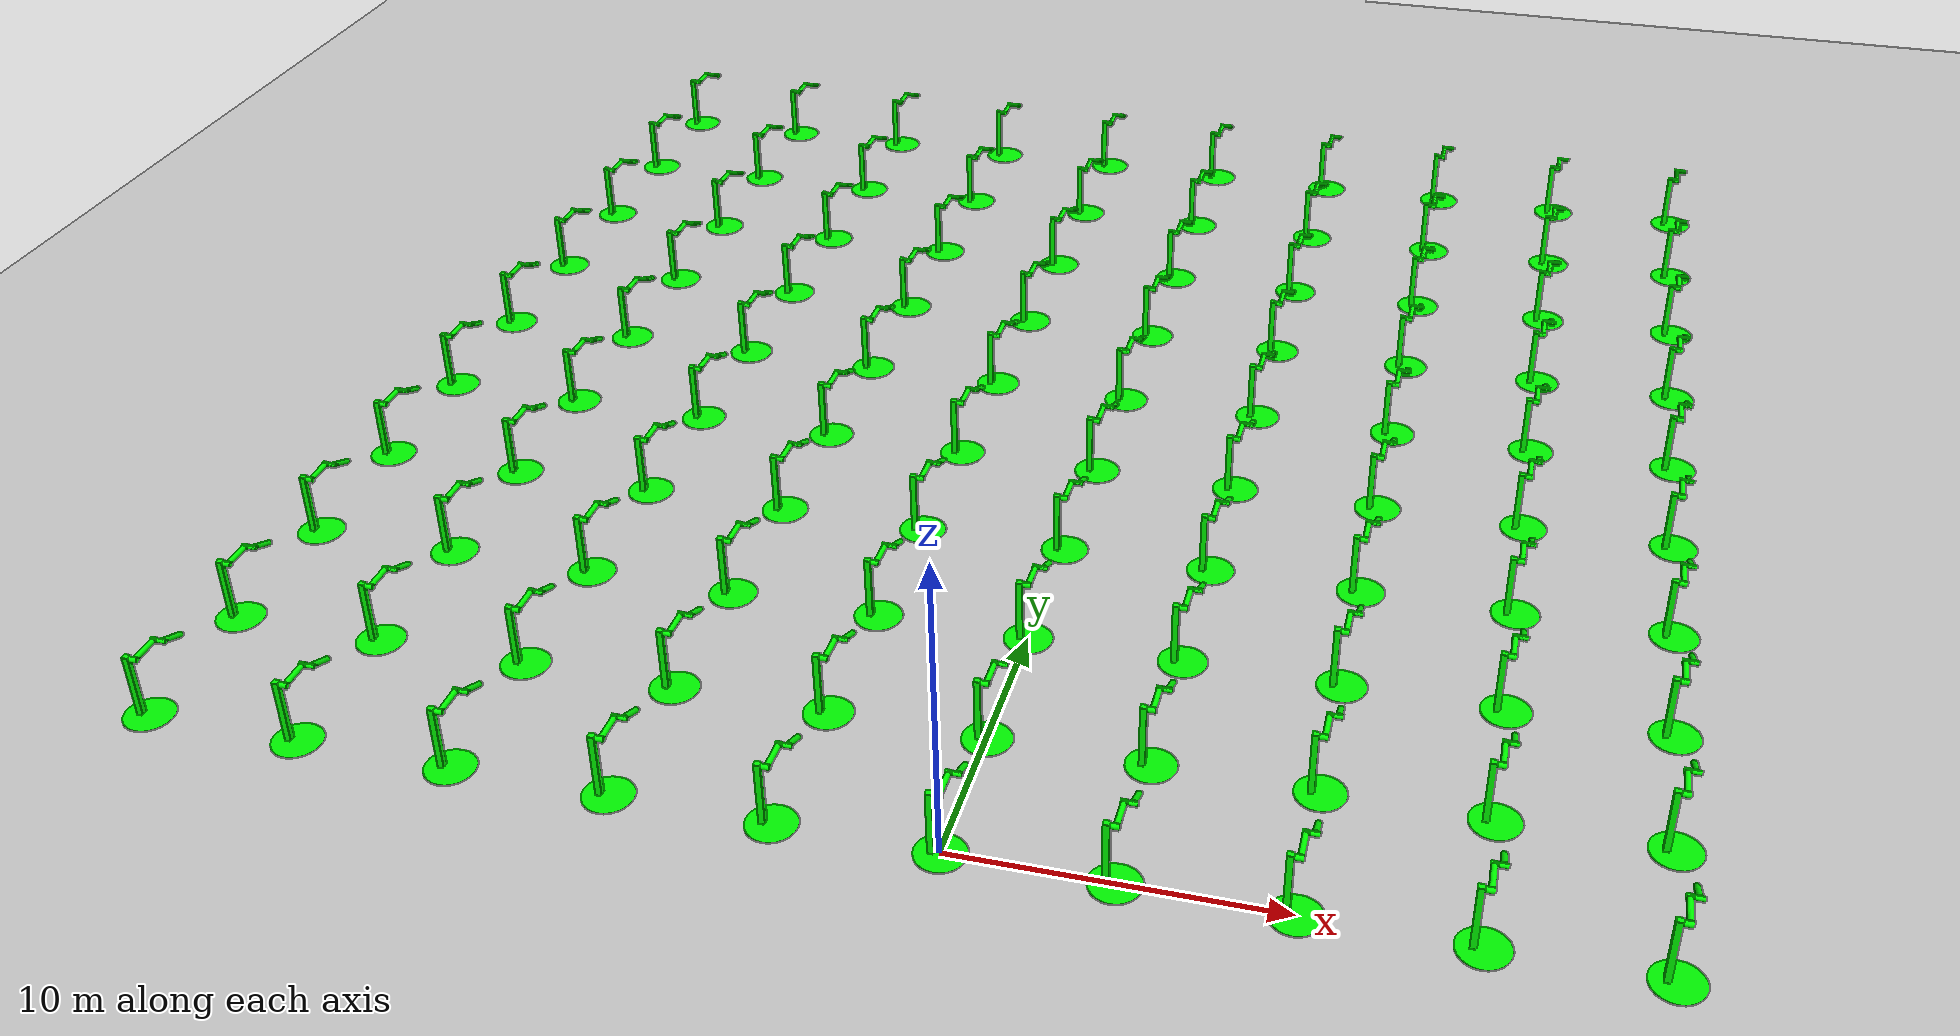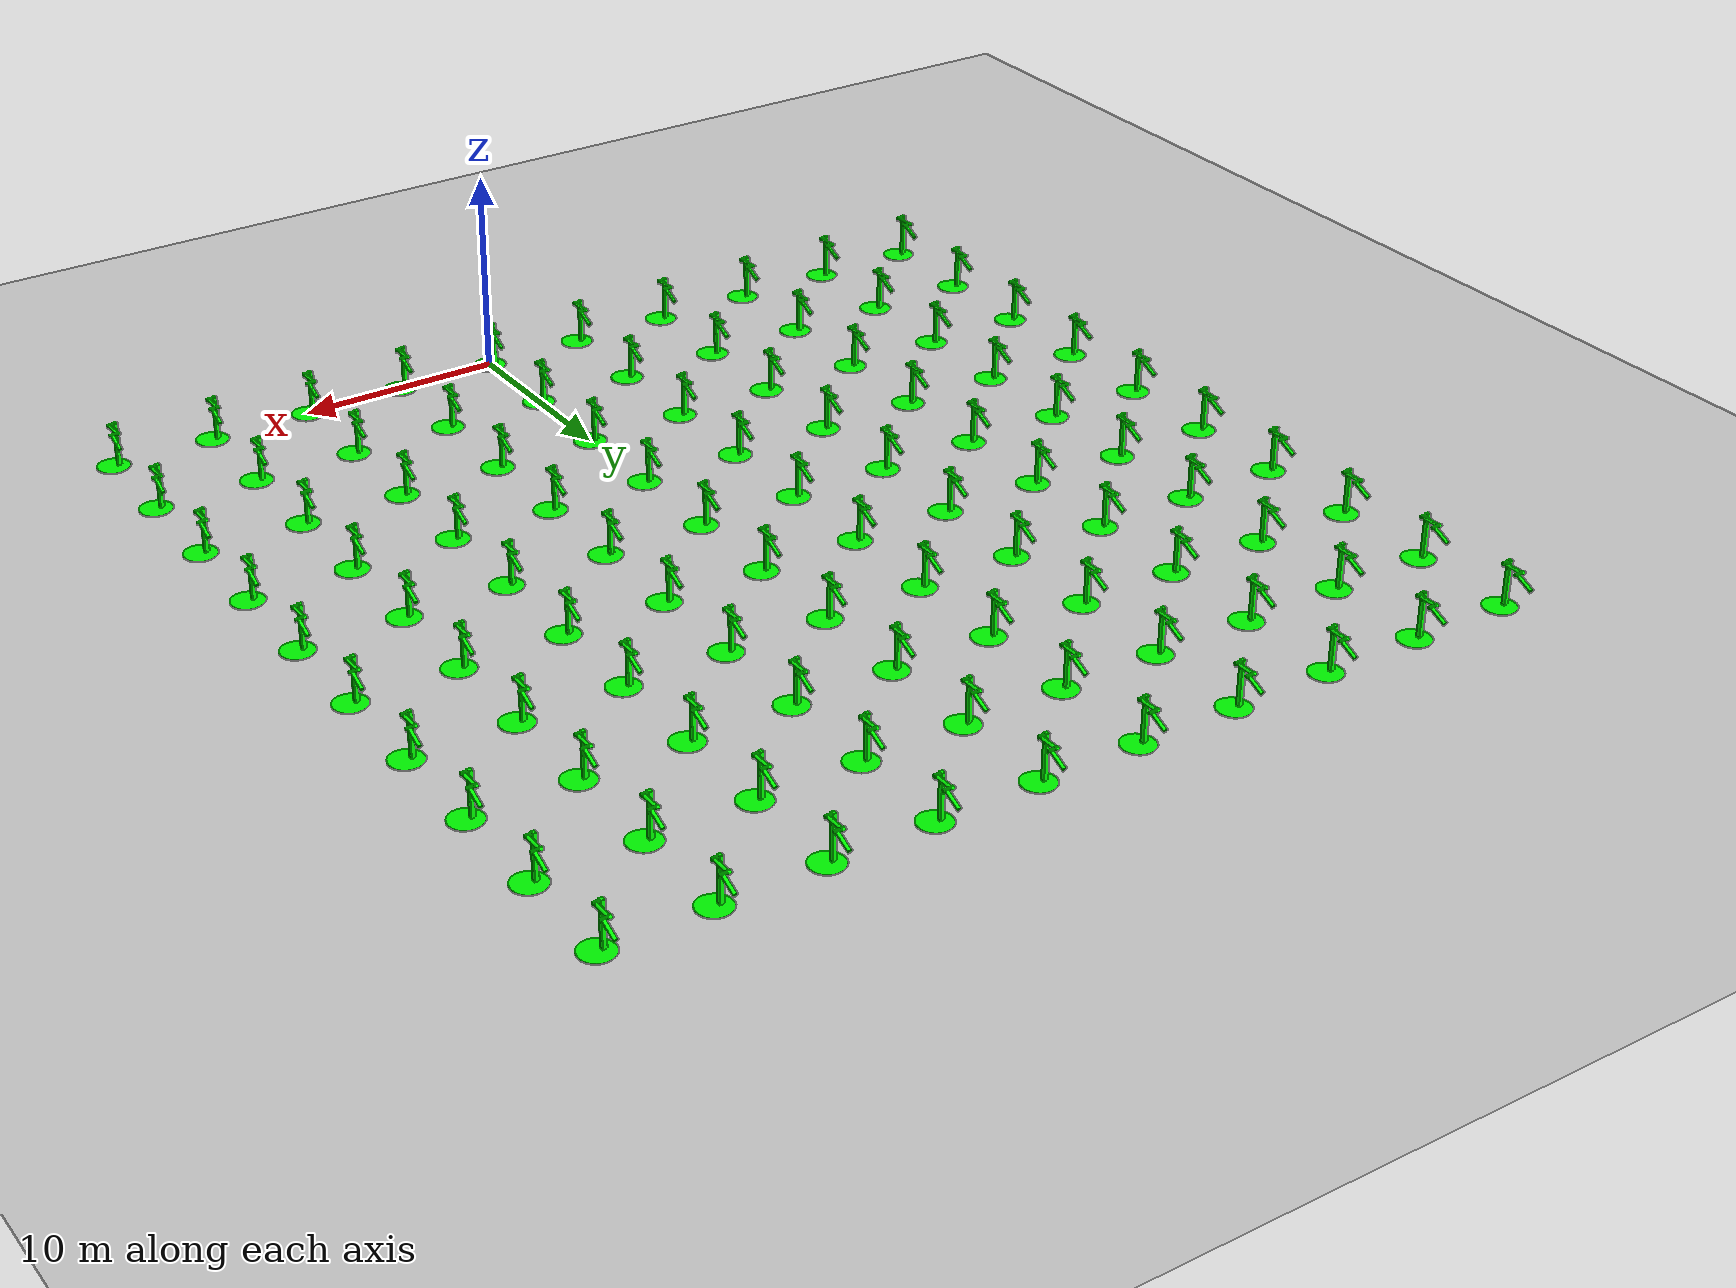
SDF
<?xml version="1.0" ?>
<!--
  to generate a world of 100 pendulums in a 10x10 grid,
  run `erb r=10 c=10 double_pendulums.sdf.erb > double_pendulums.sdf`
-->
<sdf version="1.6">
  <world name="double_pendulums">
    <model name="ground_plane">
      <static>true</static>
      <link name="link">
        <collision name="collision">
          <geometry>
            <plane>
              <normal>0 0 1</normal>
              <size>100 100</size>
            </plane>
          </geometry>
        </collision>
        <visual name="visual">
          <geometry>
            <plane>
              <normal>0 0 1</normal>
              <size>100 100</size>
            </plane>
          </geometry>
          <material>
            <ambient>0.8 0.8 0.8 1</ambient>
            <diffuse>0.8 0.8 0.8 1</diffuse>
            <specular>0.8 0.8 0.8 1</specular>
          </material>
        </visual>
      </link>
    </model>

    <model name="dbl_pendulum_0">
      <pose>-25 0 0 0 0 0</pose>
      <link name="base">
        <inertial>
          <mass>100</mass>
        </inertial>
        <visual name="vis_plate_on_ground">
          <pose>0 0 0.01 0 0 0</pose>
          <geometry>
            <cylinder>
              <radius>0.8</radius>
              <length>0.02</length>
            </cylinder>
          </geometry>
          <material>
            <ambient>0 1 0 1</ambient>
            <diffuse>0 1 0 1</diffuse>
            <specular>0 1 0 1</specular>
          </material>
        </visual>
        <visual name="vis_pole">
          <pose>-0.275 0 1.1 0 0 0</pose>
          <geometry>
            <box>
              <size>0.2 0.2 2.2</size>
            </box>
          </geometry>
          <material>
            <ambient>0 1 0 1</ambient>
            <diffuse>0 1 0 1</diffuse>
            <specular>0 1 0 1</specular>
          </material>
        </visual>
        <collision name="col_plate_on_ground">
          <pose>0 0 0.01 0 0 0</pose>
          <geometry>
            <cylinder>
              <radius>0.8</radius>
              <length>0.02</length>
            </cylinder>
          </geometry>
        </collision>
        <collision name="col_pole">
          <pose>-0.275 0 1.1 0 0 0</pose>
          <geometry>
            <box>
              <size>0.2 0.2 2.2</size>
            </box>
          </geometry>
        </collision>
      </link>
      <!-- upper link, length 1, IC -90 degrees -->
      <link name="upper_link">
        <pose>0 0 2.1 -1.5708 0 0</pose>
        <self_collide>0</self_collide>
        <inertial>
          <pose>0 0 0.5 0 0 0</pose>
        </inertial>
        <visual name="vis_upper_joint">
          <pose>-0.05 0 0 0 1.5708 0</pose>
          <geometry>
            <cylinder>
              <radius>0.1</radius>
              <length>0.3</length>
            </cylinder>
          </geometry>
          <material>
            <ambient>0 1 0 1</ambient>
            <diffuse>0 1 0 1</diffuse>
            <specular>0 1 0 1</specular>
          </material>
        </visual>
        <visual name="vis_lower_joint">
          <pose>0 0 1.0 0 1.5708 0</pose>
          <geometry>
            <cylinder>
              <radius>0.1</radius>
              <length>0.2</length>
            </cylinder>
          </geometry>
          <material>
            <ambient>0 1 0 1</ambient>
            <diffuse>0 1 0 1</diffuse>
            <specular>0 1 0 1</specular>
          </material>
        </visual>
        <visual name="vis_cylinder">
          <pose>0 0 0.5 0 0 0</pose>
          <geometry>
            <cylinder>
              <radius>0.1</radius>
              <length>0.9</length>
            </cylinder>
          </geometry>
          <material>
            <ambient>0 1 0 1</ambient>
            <diffuse>0 1 0 1</diffuse>
            <specular>0 1 0 1</specular>
          </material>
        </visual>
        <collision name="col_upper_joint">
          <pose>-0.05 0 0 0 1.5708 0</pose>
          <geometry>
            <cylinder>
              <radius>0.1</radius>
              <length>0.3</length>
            </cylinder>
          </geometry>
        </collision>
        <collision name="col_lower_joint">
          <pose>0 0 1.0 0 1.5708 0</pose>
          <geometry>
            <cylinder>
              <radius>0.1</radius>
              <length>0.2</length>
            </cylinder>
          </geometry>
        </collision>
        <collision name="col_cylinder">
          <pose>0 0 0.5 0 0 0</pose>
          <geometry>
            <cylinder>
              <radius>0.1</radius>
              <length>0.9</length>
            </cylinder>
          </geometry>
        </collision>
      </link>
      <!-- lower link, length 1, IC ~-120 degrees more -->
      <link name="lower_link">
        <pose>0.25 1.0 2.1 -2 0 0</pose>
        <self_collide>0</self_collide>
        <inertial>
          <pose>0 0 0.5 0 0 0</pose>
        </inertial>
        <visual name="vis_lower_joint">
          <pose>0 0 0 0 1.5708 0</pose>
          <geometry>
            <cylinder>
              <radius>0.08</radius>
              <length>0.3</length>
            </cylinder>
          </geometry>
          <material>
            <ambient>0 1 0 1</ambient>
            <diffuse>0 1 0 1</diffuse>
            <specular>0 1 0 1</specular>
          </material>
        </visual>
        <visual name="vis_cylinder">
          <pose>0 0 0.5 0 0 0</pose>
          <geometry>
            <cylinder>
              <radius>0.1</radius>
              <length>0.9</length>
            </cylinder>
          </geometry>
          <material>
            <ambient>0 1 0 1</ambient>
            <diffuse>0 1 0 1</diffuse>
            <specular>0 1 0 1</specular>
          </material>
        </visual>
        <collision name="col_lower_joint">
          <pose>0 0 0 0 1.5708 0</pose>
          <geometry>
            <cylinder>
              <radius>0.08</radius>
              <length>0.3</length>
            </cylinder>
          </geometry>
        </collision>
        <collision name="col_cylinder">
          <pose>0 0 0.5 0 0 0</pose>
          <geometry>
            <cylinder>
              <radius>0.1</radius>
              <length>0.9</length>
            </cylinder>
          </geometry>
        </collision>
      </link>
      <!-- pin joint for upper link, at origin of upper link -->
      <joint name="upper_joint" type="revolute">
        <parent>base</parent>
        <child>upper_link</child>
        <axis>
          <xyz>1.0 0 0</xyz>
        </axis>
      </joint>
      <!-- pin joint for lower link, at origin of child link -->
      <joint name="lower_joint" type="revolute">
        <parent>upper_link</parent>
        <child>lower_link</child>
        <axis>
          <xyz>1.0 0 0</xyz>
        </axis>
      </joint>
    </model>

    <model name="dbl_pendulum_1">
      <pose>-20 0 0 0 0 0</pose>
      <link name="base">
        <inertial>
          <mass>100</mass>
        </inertial>
        <visual name="vis_plate_on_ground">
          <pose>0 0 0.01 0 0 0</pose>
          <geometry>
            <cylinder>
              <radius>0.8</radius>
              <length>0.02</length>
            </cylinder>
          </geometry>
          <material>
            <ambient>0 1 0 1</ambient>
            <diffuse>0 1 0 1</diffuse>
            <specular>0 1 0 1</specular>
          </material>
        </visual>
        <visual name="vis_pole">
          <pose>-0.275 0 1.1 0 0 0</pose>
          <geometry>
            <box>
              <size>0.2 0.2 2.2</size>
            </box>
          </geometry>
          <material>
            <ambient>0 1 0 1</ambient>
            <diffuse>0 1 0 1</diffuse>
            <specular>0 1 0 1</specular>
          </material>
        </visual>
        <collision name="col_plate_on_ground">
          <pose>0 0 0.01 0 0 0</pose>
          <geometry>
            <cylinder>
              <radius>0.8</radius>
              <length>0.02</length>
            </cylinder>
          </geometry>
        </collision>
        <collision name="col_pole">
          <pose>-0.275 0 1.1 0 0 0</pose>
          <geometry>
            <box>
              <size>0.2 0.2 2.2</size>
            </box>
          </geometry>
        </collision>
      </link>
      <!-- upper link, length 1, IC -90 degrees -->
      <link name="upper_link">
        <pose>0 0 2.1 -1.5708 0 0</pose>
        <self_collide>0</self_collide>
        <inertial>
          <pose>0 0 0.5 0 0 0</pose>
        </inertial>
        <visual name="vis_upper_joint">
          <pose>-0.05 0 0 0 1.5708 0</pose>
          <geometry>
            <cylinder>
              <radius>0.1</radius>
              <length>0.3</length>
            </cylinder>
          </geometry>
          <material>
            <ambient>0 1 0 1</ambient>
            <diffuse>0 1 0 1</diffuse>
            <specular>0 1 0 1</specular>
          </material>
        </visual>
        <visual name="vis_lower_joint">
          <pose>0 0 1.0 0 1.5708 0</pose>
          <geometry>
            <cylinder>
              <radius>0.1</radius>
              <length>0.2</length>
            </cylinder>
          </geometry>
          <material>
            <ambient>0 1 0 1</ambient>
            <diffuse>0 1 0 1</diffuse>
            <specular>0 1 0 1</specular>
          </material>
        </visual>
        <visual name="vis_cylinder">
          <pose>0 0 0.5 0 0 0</pose>
          <geometry>
            <cylinder>
              <radius>0.1</radius>
              <length>0.9</length>
            </cylinder>
          </geometry>
          <material>
            <ambient>0 1 0 1</ambient>
            <diffuse>0 1 0 1</diffuse>
            <specular>0 1 0 1</specular>
          </material>
        </visual>
        <collision name="col_upper_joint">
          <pose>-0.05 0 0 0 1.5708 0</pose>
          <geometry>
            <cylinder>
              <radius>0.1</radius>
              <length>0.3</length>
            </cylinder>
          </geometry>
        </collision>
        <collision name="col_lower_joint">
          <pose>0 0 1.0 0 1.5708 0</pose>
          <geometry>
            <cylinder>
              <radius>0.1</radius>
              <length>0.2</length>
            </cylinder>
          </geometry>
        </collision>
        <collision name="col_cylinder">
          <pose>0 0 0.5 0 0 0</pose>
          <geometry>
            <cylinder>
              <radius>0.1</radius>
              <length>0.9</length>
            </cylinder>
          </geometry>
        </collision>
      </link>
      <!-- lower link, length 1, IC ~-120 degrees more -->
      <link name="lower_link">
        <pose>0.25 1.0 2.1 -2 0 0</pose>
        <self_collide>0</self_collide>
        <inertial>
          <pose>0 0 0.5 0 0 0</pose>
        </inertial>
        <visual name="vis_lower_joint">
          <pose>0 0 0 0 1.5708 0</pose>
          <geometry>
            <cylinder>
              <radius>0.08</radius>
              <length>0.3</length>
            </cylinder>
          </geometry>
          <material>
            <ambient>0 1 0 1</ambient>
            <diffuse>0 1 0 1</diffuse>
            <specular>0 1 0 1</specular>
          </material>
        </visual>
        <visual name="vis_cylinder">
          <pose>0 0 0.5 0 0 0</pose>
          <geometry>
            <cylinder>
              <radius>0.1</radius>
              <length>0.9</length>
            </cylinder>
          </geometry>
          <material>
            <ambient>0 1 0 1</ambient>
            <diffuse>0 1 0 1</diffuse>
            <specular>0 1 0 1</specular>
          </material>
        </visual>
        <collision name="col_lower_joint">
          <pose>0 0 0 0 1.5708 0</pose>
          <geometry>
            <cylinder>
              <radius>0.08</radius>
              <length>0.3</length>
            </cylinder>
          </geometry>
        </collision>
        <collision name="col_cylinder">
          <pose>0 0 0.5 0 0 0</pose>
          <geometry>
            <cylinder>
              <radius>0.1</radius>
              <length>0.9</length>
            </cylinder>
          </geometry>
        </collision>
      </link>
      <!-- pin joint for upper link, at origin of upper link -->
      <joint name="upper_joint" type="revolute">
        <parent>base</parent>
        <child>upper_link</child>
        <axis>
          <xyz>1.0 0 0</xyz>
        </axis>
      </joint>
      <!-- pin joint for lower link, at origin of child link -->
      <joint name="lower_joint" type="revolute">
        <parent>upper_link</parent>
        <child>lower_link</child>
        <axis>
          <xyz>1.0 0 0</xyz>
        </axis>
      </joint>
    </model>

    <model name="dbl_pendulum_2">
      <pose>-15 0 0 0 0 0</pose>
      <link name="base">
        <inertial>
          <mass>100</mass>
        </inertial>
        <visual name="vis_plate_on_ground">
          <pose>0 0 0.01 0 0 0</pose>
          <geometry>
            <cylinder>
              <radius>0.8</radius>
              <length>0.02</length>
            </cylinder>
          </geometry>
          <material>
            <ambient>0 1 0 1</ambient>
            <diffuse>0 1 0 1</diffuse>
            <specular>0 1 0 1</specular>
          </material>
        </visual>
        <visual name="vis_pole">
          <pose>-0.275 0 1.1 0 0 0</pose>
          <geometry>
            <box>
              <size>0.2 0.2 2.2</size>
            </box>
          </geometry>
          <material>
            <ambient>0 1 0 1</ambient>
            <diffuse>0 1 0 1</diffuse>
            <specular>0 1 0 1</specular>
          </material>
        </visual>
        <collision name="col_plate_on_ground">
          <pose>0 0 0.01 0 0 0</pose>
          <geometry>
            <cylinder>
              <radius>0.8</radius>
              <length>0.02</length>
            </cylinder>
          </geometry>
        </collision>
        <collision name="col_pole">
          <pose>-0.275 0 1.1 0 0 0</pose>
          <geometry>
            <box>
              <size>0.2 0.2 2.2</size>
            </box>
          </geometry>
        </collision>
      </link>
      <!-- upper link, length 1, IC -90 degrees -->
      <link name="upper_link">
        <pose>0 0 2.1 -1.5708 0 0</pose>
        <self_collide>0</self_collide>
        <inertial>
          <pose>0 0 0.5 0 0 0</pose>
        </inertial>
        <visual name="vis_upper_joint">
          <pose>-0.05 0 0 0 1.5708 0</pose>
          <geometry>
            <cylinder>
              <radius>0.1</radius>
              <length>0.3</length>
            </cylinder>
          </geometry>
          <material>
            <ambient>0 1 0 1</ambient>
            <diffuse>0 1 0 1</diffuse>
            <specular>0 1 0 1</specular>
          </material>
        </visual>
        <visual name="vis_lower_joint">
          <pose>0 0 1.0 0 1.5708 0</pose>
          <geometry>
            <cylinder>
              <radius>0.1</radius>
              <length>0.2</length>
            </cylinder>
          </geometry>
          <material>
            <ambient>0 1 0 1</ambient>
            <diffuse>0 1 0 1</diffuse>
            <specular>0 1 0 1</specular>
          </material>
        </visual>
        <visual name="vis_cylinder">
          <pose>0 0 0.5 0 0 0</pose>
          <geometry>
            <cylinder>
              <radius>0.1</radius>
              <length>0.9</length>
            </cylinder>
          </geometry>
          <material>
            <ambient>0 1 0 1</ambient>
            <diffuse>0 1 0 1</diffuse>
            <specular>0 1 0 1</specular>
          </material>
        </visual>
        <collision name="col_upper_joint">
          <pose>-0.05 0 0 0 1.5708 0</pose>
          <geometry>
            <cylinder>
              <radius>0.1</radius>
              <length>0.3</length>
            </cylinder>
          </geometry>
        </collision>
        <collision name="col_lower_joint">
          <pose>0 0 1.0 0 1.5708 0</pose>
          <geometry>
            <cylinder>
              <radius>0.1</radius>
              <length>0.2</length>
            </cylinder>
          </geometry>
        </collision>
        <collision name="col_cylinder">
          <pose>0 0 0.5 0 0 0</pose>
          <geometry>
            <cylinder>
              <radius>0.1</radius>
              <length>0.9</length>
            </cylinder>
          </geometry>
        </collision>
      </link>
      <!-- lower link, length 1, IC ~-120 degrees more -->
      <link name="lower_link">
        <pose>0.25 1.0 2.1 -2 0 0</pose>
        <self_collide>0</self_collide>
        <inertial>
          <pose>0 0 0.5 0 0 0</pose>
        </inertial>
        <visual name="vis_lower_joint">
          <pose>0 0 0 0 1.5708 0</pose>
          <geometry>
            <cylinder>
              <radius>0.08</radius>
              <length>0.3</length>
            </cylinder>
          </geometry>
          <material>
            <ambient>0 1 0 1</ambient>
            <diffuse>0 1 0 1</diffuse>
            <specular>0 1 0 1</specular>
          </material>
        </visual>
        <visual name="vis_cylinder">
          <pose>0 0 0.5 0 0 0</pose>
          <geometry>
            <cylinder>
              <radius>0.1</radius>
              <length>0.9</length>
            </cylinder>
          </geometry>
          <material>
            <ambient>0 1 0 1</ambient>
            <diffuse>0 1 0 1</diffuse>
            <specular>0 1 0 1</specular>
          </material>
        </visual>
        <collision name="col_lower_joint">
          <pose>0 0 0 0 1.5708 0</pose>
          <geometry>
            <cylinder>
              <radius>0.08</radius>
              <length>0.3</length>
            </cylinder>
          </geometry>
        </collision>
        <collision name="col_cylinder">
          <pose>0 0 0.5 0 0 0</pose>
          <geometry>
            <cylinder>
              <radius>0.1</radius>
              <length>0.9</length>
            </cylinder>
          </geometry>
        </collision>
      </link>
      <!-- pin joint for upper link, at origin of upper link -->
      <joint name="upper_joint" type="revolute">
        <parent>base</parent>
        <child>upper_link</child>
        <axis>
          <xyz>1.0 0 0</xyz>
        </axis>
      </joint>
      <!-- pin joint for lower link, at origin of child link -->
      <joint name="lower_joint" type="revolute">
        <parent>upper_link</parent>
        <child>lower_link</child>
        <axis>
          <xyz>1.0 0 0</xyz>
        </axis>
      </joint>
    </model>

    <model name="dbl_pendulum_3">
      <pose>-10 0 0 0 0 0</pose>
      <link name="base">
        <inertial>
          <mass>100</mass>
        </inertial>
        <visual name="vis_plate_on_ground">
          <pose>0 0 0.01 0 0 0</pose>
          <geometry>
            <cylinder>
              <radius>0.8</radius>
              <length>0.02</length>
            </cylinder>
          </geometry>
          <material>
            <ambient>0 1 0 1</ambient>
            <diffuse>0 1 0 1</diffuse>
            <specular>0 1 0 1</specular>
          </material>
        </visual>
        <visual name="vis_pole">
          <pose>-0.275 0 1.1 0 0 0</pose>
          <geometry>
            <box>
              <size>0.2 0.2 2.2</size>
            </box>
          </geometry>
          <material>
            <ambient>0 1 0 1</ambient>
            <diffuse>0 1 0 1</diffuse>
            <specular>0 1 0 1</specular>
          </material>
        </visual>
        <collision name="col_plate_on_ground">
          <pose>0 0 0.01 0 0 0</pose>
          <geometry>
            <cylinder>
              <radius>0.8</radius>
              <length>0.02</length>
            </cylinder>
          </geometry>
        </collision>
        <collision name="col_pole">
          <pose>-0.275 0 1.1 0 0 0</pose>
          <geometry>
            <box>
              <size>0.2 0.2 2.2</size>
            </box>
          </geometry>
        </collision>
      </link>
      <!-- upper link, length 1, IC -90 degrees -->
      <link name="upper_link">
        <pose>0 0 2.1 -1.5708 0 0</pose>
        <self_collide>0</self_collide>
        <inertial>
          <pose>0 0 0.5 0 0 0</pose>
        </inertial>
        <visual name="vis_upper_joint">
          <pose>-0.05 0 0 0 1.5708 0</pose>
          <geometry>
            <cylinder>
              <radius>0.1</radius>
              <length>0.3</length>
            </cylinder>
          </geometry>
          <material>
            <ambient>0 1 0 1</ambient>
            <diffuse>0 1 0 1</diffuse>
            <specular>0 1 0 1</specular>
          </material>
        </visual>
        <visual name="vis_lower_joint">
          <pose>0 0 1.0 0 1.5708 0</pose>
          <geometry>
            <cylinder>
              <radius>0.1</radius>
              <length>0.2</length>
            </cylinder>
          </geometry>
          <material>
            <ambient>0 1 0 1</ambient>
            <diffuse>0 1 0 1</diffuse>
            <specular>0 1 0 1</specular>
          </material>
        </visual>
        <visual name="vis_cylinder">
          <pose>0 0 0.5 0 0 0</pose>
          <geometry>
            <cylinder>
              <radius>0.1</radius>
              <length>0.9</length>
            </cylinder>
          </geometry>
          <material>
            <ambient>0 1 0 1</ambient>
            <diffuse>0 1 0 1</diffuse>
            <specular>0 1 0 1</specular>
          </material>
        </visual>
        <collision name="col_upper_joint">
          <pose>-0.05 0 0 0 1.5708 0</pose>
          <geometry>
            <cylinder>
              <radius>0.1</radius>
              <length>0.3</length>
            </cylinder>
          </geometry>
        </collision>
        <collision name="col_lower_joint">
          <pose>0 0 1.0 0 1.5708 0</pose>
          <geometry>
            <cylinder>
              <radius>0.1</radius>
              <length>0.2</length>
            </cylinder>
          </geometry>
        </collision>
        <collision name="col_cylinder">
          <pose>0 0 0.5 0 0 0</pose>
          <geometry>
            <cylinder>
              <radius>0.1</radius>
              <length>0.9</length>
            </cylinder>
          </geometry>
        </collision>
      </link>
      <!-- lower link, length 1, IC ~-120 degrees more -->
      <link name="lower_link">
        <pose>0.25 1.0 2.1 -2 0 0</pose>
        <self_collide>0</self_collide>
        <inertial>
          <pose>0 0 0.5 0 0 0</pose>
        </inertial>
        <visual name="vis_lower_joint">
          <pose>0 0 0 0 1.5708 0</pose>
          <geometry>
            <cylinder>
              <radius>0.08</radius>
              <length>0.3</length>
            </cylinder>
          </geometry>
          <material>
            <ambient>0 1 0 1</ambient>
            <diffuse>0 1 0 1</diffuse>
            <specular>0 1 0 1</specular>
          </material>
        </visual>
        <visual name="vis_cylinder">
          <pose>0 0 0.5 0 0 0</pose>
          <geometry>
            <cylinder>
              <radius>0.1</radius>
              <length>0.9</length>
            </cylinder>
          </geometry>
          <material>
            <ambient>0 1 0 1</ambient>
            <diffuse>0 1 0 1</diffuse>
            <specular>0 1 0 1</specular>
          </material>
        </visual>
        <collision name="col_lower_joint">
          <pose>0 0 0 0 1.5708 0</pose>
          <geometry>
            <cylinder>
              <radius>0.08</radius>
              <length>0.3</length>
            </cylinder>
          </geometry>
        </collision>
        <collision name="col_cylinder">
          <pose>0 0 0.5 0 0 0</pose>
          <geometry>
            <cylinder>
              <radius>0.1</radius>
              <length>0.9</length>
            </cylinder>
          </geometry>
        </collision>
      </link>
      <!-- pin joint for upper link, at origin of upper link -->
      <joint name="upper_joint" type="revolute">
        <parent>base</parent>
        <child>upper_link</child>
        <axis>
          <xyz>1.0 0 0</xyz>
        </axis>
      </joint>
      <!-- pin joint for lower link, at origin of child link -->
      <joint name="lower_joint" type="revolute">
        <parent>upper_link</parent>
        <child>lower_link</child>
        <axis>
          <xyz>1.0 0 0</xyz>
        </axis>
      </joint>
    </model>

    <model name="dbl_pendulum_4">
      <pose>-5 0 0 0 0 0</pose>
      <link name="base">
        <inertial>
          <mass>100</mass>
        </inertial>
        <visual name="vis_plate_on_ground">
          <pose>0 0 0.01 0 0 0</pose>
          <geometry>
            <cylinder>
              <radius>0.8</radius>
              <length>0.02</length>
            </cylinder>
          </geometry>
          <material>
            <ambient>0 1 0 1</ambient>
            <diffuse>0 1 0 1</diffuse>
            <specular>0 1 0 1</specular>
          </material>
        </visual>
        <visual name="vis_pole">
          <pose>-0.275 0 1.1 0 0 0</pose>
          <geometry>
            <box>
              <size>0.2 0.2 2.2</size>
            </box>
          </geometry>
          <material>
            <ambient>0 1 0 1</ambient>
            <diffuse>0 1 0 1</diffuse>
            <specular>0 1 0 1</specular>
          </material>
        </visual>
        <collision name="col_plate_on_ground">
          <pose>0 0 0.01 0 0 0</pose>
          <geometry>
            <cylinder>
              <radius>0.8</radius>
              <length>0.02</length>
            </cylinder>
          </geometry>
        </collision>
        <collision name="col_pole">
          <pose>-0.275 0 1.1 0 0 0</pose>
          <geometry>
            <box>
              <size>0.2 0.2 2.2</size>
            </box>
          </geometry>
        </collision>
      </link>
      <!-- upper link, length 1, IC -90 degrees -->
      <link name="upper_link">
        <pose>0 0 2.1 -1.5708 0 0</pose>
        <self_collide>0</self_collide>
        <inertial>
          <pose>0 0 0.5 0 0 0</pose>
        </inertial>
        <visual name="vis_upper_joint">
          <pose>-0.05 0 0 0 1.5708 0</pose>
          <geometry>
            <cylinder>
              <radius>0.1</radius>
              <length>0.3</length>
            </cylinder>
          </geometry>
          <material>
            <ambient>0 1 0 1</ambient>
            <diffuse>0 1 0 1</diffuse>
            <specular>0 1 0 1</specular>
          </material>
        </visual>
        <visual name="vis_lower_joint">
          <pose>0 0 1.0 0 1.5708 0</pose>
          <geometry>
            <cylinder>
              <radius>0.1</radius>
              <length>0.2</length>
            </cylinder>
          </geometry>
          <material>
            <ambient>0 1 0 1</ambient>
            <diffuse>0 1 0 1</diffuse>
            <specular>0 1 0 1</specular>
          </material>
        </visual>
        <visual name="vis_cylinder">
          <pose>0 0 0.5 0 0 0</pose>
          <geometry>
            <cylinder>
              <radius>0.1</radius>
              <length>0.9</length>
            </cylinder>
          </geometry>
          <material>
            <ambient>0 1 0 1</ambient>
            <diffuse>0 1 0 1</diffuse>
            <specular>0 1 0 1</specular>
          </material>
        </visual>
        <collision name="col_upper_joint">
          <pose>-0.05 0 0 0 1.5708 0</pose>
          <geometry>
            <cylinder>
              <radius>0.1</radius>
              <length>0.3</length>
            </cylinder>
          </geometry>
        </collision>
        <collision name="col_lower_joint">
          <pose>0 0 1.0 0 1.5708 0</pose>
          <geometry>
            <cylinder>
              <radius>0.1</radius>
              <length>0.2</length>
            </cylinder>
          </geometry>
        </collision>
        <collision name="col_cylinder">
          <pose>0 0 0.5 0 0 0</pose>
          <geometry>
            <cylinder>
              <radius>0.1</radius>
              <length>0.9</length>
            </cylinder>
          </geometry>
        </collision>
      </link>
      <!-- lower link, length 1, IC ~-120 degrees more -->
      <link name="lower_link">
        <pose>0.25 1.0 2.1 -2 0 0</pose>
        <self_collide>0</self_collide>
        <inertial>
          <pose>0 0 0.5 0 0 0</pose>
        </inertial>
        <visual name="vis_lower_joint">
          <pose>0 0 0 0 1.5708 0</pose>
          <geometry>
            <cylinder>
              <radius>0.08</radius>
              <length>0.3</length>
            </cylinder>
          </geometry>
          <material>
            <ambient>0 1 0 1</ambient>
            <diffuse>0 1 0 1</diffuse>
            <specular>0 1 0 1</specular>
          </material>
        </visual>
        <visual name="vis_cylinder">
          <pose>0 0 0.5 0 0 0</pose>
          <geometry>
            <cylinder>
              <radius>0.1</radius>
              <length>0.9</length>
            </cylinder>
          </geometry>
          <material>
            <ambient>0 1 0 1</ambient>
            <diffuse>0 1 0 1</diffuse>
            <specular>0 1 0 1</specular>
          </material>
        </visual>
        <collision name="col_lower_joint">
          <pose>0 0 0 0 1.5708 0</pose>
          <geometry>
            <cylinder>
              <radius>0.08</radius>
              <length>0.3</length>
            </cylinder>
          </geometry>
        </collision>
        <collision name="col_cylinder">
          <pose>0 0 0.5 0 0 0</pose>
          <geometry>
            <cylinder>
              <radius>0.1</radius>
              <length>0.9</length>
            </cylinder>
          </geometry>
        </collision>
      </link>
      <!-- pin joint for upper link, at origin of upper link -->
      <joint name="upper_joint" type="revolute">
        <parent>base</parent>
        <child>upper_link</child>
        <axis>
          <xyz>1.0 0 0</xyz>
        </axis>
      </joint>
      <!-- pin joint for lower link, at origin of child link -->
      <joint name="lower_joint" type="revolute">
        <parent>upper_link</parent>
        <child>lower_link</child>
        <axis>
          <xyz>1.0 0 0</xyz>
        </axis>
      </joint>
    </model>

    <model name="dbl_pendulum_5">
      <pose>0 0 0 0 0 0</pose>
      <link name="base">
        <inertial>
          <mass>100</mass>
        </inertial>
        <visual name="vis_plate_on_ground">
          <pose>0 0 0.01 0 0 0</pose>
          <geometry>
            <cylinder>
              <radius>0.8</radius>
              <length>0.02</length>
            </cylinder>
          </geometry>
          <material>
            <ambient>0 1 0 1</ambient>
            <diffuse>0 1 0 1</diffuse>
            <specular>0 1 0 1</specular>
          </material>
        </visual>
        <visual name="vis_pole">
          <pose>-0.275 0 1.1 0 0 0</pose>
          <geometry>
            <box>
              <size>0.2 0.2 2.2</size>
            </box>
          </geometry>
          <material>
            <ambient>0 1 0 1</ambient>
            <diffuse>0 1 0 1</diffuse>
            <specular>0 1 0 1</specular>
          </material>
        </visual>
        <collision name="col_plate_on_ground">
          <pose>0 0 0.01 0 0 0</pose>
          <geometry>
            <cylinder>
              <radius>0.8</radius>
              <length>0.02</length>
            </cylinder>
          </geometry>
        </collision>
        <collision name="col_pole">
          <pose>-0.275 0 1.1 0 0 0</pose>
          <geometry>
            <box>
              <size>0.2 0.2 2.2</size>
            </box>
          </geometry>
        </collision>
      </link>
      <!-- upper link, length 1, IC -90 degrees -->
      <link name="upper_link">
        <pose>0 0 2.1 -1.5708 0 0</pose>
        <self_collide>0</self_collide>
        <inertial>
          <pose>0 0 0.5 0 0 0</pose>
        </inertial>
        <visual name="vis_upper_joint">
          <pose>-0.05 0 0 0 1.5708 0</pose>
          <geometry>
            <cylinder>
              <radius>0.1</radius>
              <length>0.3</length>
            </cylinder>
          </geometry>
          <material>
            <ambient>0 1 0 1</ambient>
            <diffuse>0 1 0 1</diffuse>
            <specular>0 1 0 1</specular>
          </material>
        </visual>
        <visual name="vis_lower_joint">
          <pose>0 0 1.0 0 1.5708 0</pose>
          <geometry>
            <cylinder>
              <radius>0.1</radius>
              <length>0.2</length>
            </cylinder>
          </geometry>
          <material>
            <ambient>0 1 0 1</ambient>
            <diffuse>0 1 0 1</diffuse>
            <specular>0 1 0 1</specular>
          </material>
        </visual>
        <visual name="vis_cylinder">
          <pose>0 0 0.5 0 0 0</pose>
          <geometry>
            <cylinder>
              <radius>0.1</radius>
              <length>0.9</length>
            </cylinder>
          </geometry>
          <material>
            <ambient>0 1 0 1</ambient>
            <diffuse>0 1 0 1</diffuse>
            <specular>0 1 0 1</specular>
          </material>
        </visual>
        <collision name="col_upper_joint">
          <pose>-0.05 0 0 0 1.5708 0</pose>
          <geometry>
            <cylinder>
              <radius>0.1</radius>
              <length>0.3</length>
            </cylinder>
          </geometry>
        </collision>
        <collision name="col_lower_joint">
          <pose>0 0 1.0 0 1.5708 0</pose>
          <geometry>
            <cylinder>
              <radius>0.1</radius>
              <length>0.2</length>
            </cylinder>
          </geometry>
        </collision>
        <collision name="col_cylinder">
          <pose>0 0 0.5 0 0 0</pose>
          <geometry>
            <cylinder>
              <radius>0.1</radius>
              <length>0.9</length>
            </cylinder>
          </geometry>
        </collision>
      </link>
      <!-- lower link, length 1, IC ~-120 degrees more -->
      <link name="lower_link">
        <pose>0.25 1.0 2.1 -2 0 0</pose>
        <self_collide>0</self_collide>
        <inertial>
          <pose>0 0 0.5 0 0 0</pose>
        </inertial>
        <visual name="vis_lower_joint">
          <pose>0 0 0 0 1.5708 0</pose>
          <geometry>
            <cylinder>
              <radius>0.08</radius>
              <length>0.3</length>
            </cylinder>
          </geometry>
          <material>
            <ambient>0 1 0 1</ambient>
            <diffuse>0 1 0 1</diffuse>
            <specular>0 1 0 1</specular>
          </material>
        </visual>
        <visual name="vis_cylinder">
          <pose>0 0 0.5 0 0 0</pose>
          <geometry>
            <cylinder>
              <radius>0.1</radius>
              <length>0.9</length>
            </cylinder>
          </geometry>
          <material>
            <ambient>0 1 0 1</ambient>
            <diffuse>0 1 0 1</diffuse>
            <specular>0 1 0 1</specular>
          </material>
        </visual>
        <collision name="col_lower_joint">
          <pose>0 0 0 0 1.5708 0</pose>
          <geometry>
            <cylinder>
              <radius>0.08</radius>
              <length>0.3</length>
            </cylinder>
          </geometry>
        </collision>
        <collision name="col_cylinder">
          <pose>0 0 0.5 0 0 0</pose>
          <geometry>
            <cylinder>
              <radius>0.1</radius>
              <length>0.9</length>
            </cylinder>
          </geometry>
        </collision>
      </link>
      <!-- pin joint for upper link, at origin of upper link -->
      <joint name="upper_joint" type="revolute">
        <parent>base</parent>
        <child>upper_link</child>
        <axis>
          <xyz>1.0 0 0</xyz>
        </axis>
      </joint>
      <!-- pin joint for lower link, at origin of child link -->
      <joint name="lower_joint" type="revolute">
        <parent>upper_link</parent>
        <child>lower_link</child>
        <axis>
          <xyz>1.0 0 0</xyz>
        </axis>
      </joint>
    </model>

    <model name="dbl_pendulum_6">
      <pose>5 0 0 0 0 0</pose>
      <link name="base">
        <inertial>
          <mass>100</mass>
        </inertial>
        <visual name="vis_plate_on_ground">
          <pose>0 0 0.01 0 0 0</pose>
          <geometry>
            <cylinder>
              <radius>0.8</radius>
              <length>0.02</length>
            </cylinder>
          </geometry>
          <material>
            <ambient>0 1 0 1</ambient>
            <diffuse>0 1 0 1</diffuse>
            <specular>0 1 0 1</specular>
          </material>
        </visual>
        <visual name="vis_pole">
          <pose>-0.275 0 1.1 0 0 0</pose>
          <geometry>
            <box>
              <size>0.2 0.2 2.2</size>
            </box>
          </geometry>
          <material>
            <ambient>0 1 0 1</ambient>
            <diffuse>0 1 0 1</diffuse>
            <specular>0 1 0 1</specular>
          </material>
        </visual>
        <collision name="col_plate_on_ground">
          <pose>0 0 0.01 0 0 0</pose>
          <geometry>
            <cylinder>
              <radius>0.8</radius>
              <length>0.02</length>
            </cylinder>
          </geometry>
        </collision>
        <collision name="col_pole">
          <pose>-0.275 0 1.1 0 0 0</pose>
          <geometry>
            <box>
              <size>0.2 0.2 2.2</size>
            </box>
          </geometry>
        </collision>
      </link>
      <!-- upper link, length 1, IC -90 degrees -->
      <link name="upper_link">
        <pose>0 0 2.1 -1.5708 0 0</pose>
        <self_collide>0</self_collide>
        <inertial>
          <pose>0 0 0.5 0 0 0</pose>
        </inertial>
        <visual name="vis_upper_joint">
          <pose>-0.05 0 0 0 1.5708 0</pose>
          <geometry>
            <cylinder>
              <radius>0.1</radius>
              <length>0.3</length>
            </cylinder>
          </geometry>
          <material>
            <ambient>0 1 0 1</ambient>
            <diffuse>0 1 0 1</diffuse>
            <specular>0 1 0 1</specular>
          </material>
        </visual>
        <visual name="vis_lower_joint">
          <pose>0 0 1.0 0 1.5708 0</pose>
          <geometry>
            <cylinder>
              <radius>0.1</radius>
              <length>0.2</length>
            </cylinder>
          </geometry>
          <material>
            <ambient>0 1 0 1</ambient>
            <diffuse>0 1 0 1</diffuse>
            <specular>0 1 0 1</specular>
          </material>
        </visual>
        <visual name="vis_cylinder">
          <pose>0 0 0.5 0 0 0</pose>
          <geometry>
            <cylinder>
              <radius>0.1</radius>
              <length>0.9</length>
            </cylinder>
          </geometry>
          <material>
            <ambient>0 1 0 1</ambient>
            <diffuse>0 1 0 1</diffuse>
            <specular>0 1 0 1</specular>
          </material>
        </visual>
        <collision name="col_upper_joint">
          <pose>-0.05 0 0 0 1.5708 0</pose>
          <geometry>
            <cylinder>
              <radius>0.1</radius>
              <length>0.3</length>
            </cylinder>
          </geometry>
        </collision>
        <collision name="col_lower_joint">
          <pose>0 0 1.0 0 1.5708 0</pose>
          <geometry>
            <cylinder>
              <radius>0.1</radius>
              <length>0.2</length>
            </cylinder>
          </geometry>
        </collision>
        <collision name="col_cylinder">
          <pose>0 0 0.5 0 0 0</pose>
          <geometry>
            <cylinder>
              <radius>0.1</radius>
              <length>0.9</length>
            </cylinder>
          </geometry>
        </collision>
      </link>
      <!-- lower link, length 1, IC ~-120 degrees more -->
      <link name="lower_link">
        <pose>0.25 1.0 2.1 -2 0 0</pose>
        <self_collide>0</self_collide>
        <inertial>
          <pose>0 0 0.5 0 0 0</pose>
        </inertial>
        <visual name="vis_lower_joint">
          <pose>0 0 0 0 1.5708 0</pose>
          <geometry>
            <cylinder>
              <radius>0.08</radius>
              <length>0.3</length>
            </cylinder>
          </geometry>
          <material>
            <ambient>0 1 0 1</ambient>
            <diffuse>0 1 0 1</diffuse>
            <specular>0 1 0 1</specular>
          </material>
        </visual>
        <visual name="vis_cylinder">
          <pose>0 0 0.5 0 0 0</pose>
          <geometry>
            <cylinder>
              <radius>0.1</radius>
              <length>0.9</length>
            </cylinder>
          </geometry>
          <material>
            <ambient>0 1 0 1</ambient>
            <diffuse>0 1 0 1</diffuse>
            <specular>0 1 0 1</specular>
          </material>
        </visual>
        <collision name="col_lower_joint">
          <pose>0 0 0 0 1.5708 0</pose>
          <geometry>
            <cylinder>
              <radius>0.08</radius>
              <length>0.3</length>
            </cylinder>
          </geometry>
        </collision>
        <collision name="col_cylinder">
          <pose>0 0 0.5 0 0 0</pose>
          <geometry>
            <cylinder>
              <radius>0.1</radius>
              <length>0.9</length>
            </cylinder>
          </geometry>
        </collision>
      </link>
      <!-- pin joint for upper link, at origin of upper link -->
      <joint name="upper_joint" type="revolute">
        <parent>base</parent>
        <child>upper_link</child>
        <axis>
          <xyz>1.0 0 0</xyz>
        </axis>
      </joint>
      <!-- pin joint for lower link, at origin of child link -->
      <joint name="lower_joint" type="revolute">
        <parent>upper_link</parent>
        <child>lower_link</child>
        <axis>
          <xyz>1.0 0 0</xyz>
        </axis>
      </joint>
    </model>

    <model name="dbl_pendulum_7">
      <pose>10 0 0 0 0 0</pose>
      <link name="base">
        <inertial>
          <mass>100</mass>
        </inertial>
        <visual name="vis_plate_on_ground">
          <pose>0 0 0.01 0 0 0</pose>
          <geometry>
            <cylinder>
              <radius>0.8</radius>
              <length>0.02</length>
            </cylinder>
          </geometry>
          <material>
            <ambient>0 1 0 1</ambient>
            <diffuse>0 1 0 1</diffuse>
            <specular>0 1 0 1</specular>
          </material>
        </visual>
        <visual name="vis_pole">
          <pose>-0.275 0 1.1 0 0 0</pose>
          <geometry>
            <box>
              <size>0.2 0.2 2.2</size>
            </box>
          </geometry>
          <material>
            <ambient>0 1 0 1</ambient>
            <diffuse>0 1 0 1</diffuse>
            <specular>0 1 0 1</specular>
          </material>
        </visual>
        <collision name="col_plate_on_ground">
          <pose>0 0 0.01 0 0 0</pose>
          <geometry>
            <cylinder>
              <radius>0.8</radius>
              <length>0.02</length>
            </cylinder>
          </geometry>
        </collision>
        <collision name="col_pole">
          <pose>-0.275 0 1.1 0 0 0</pose>
          <geometry>
            <box>
              <size>0.2 0.2 2.2</size>
            </box>
          </geometry>
        </collision>
      </link>
      <!-- upper link, length 1, IC -90 degrees -->
      <link name="upper_link">
        <pose>0 0 2.1 -1.5708 0 0</pose>
        <self_collide>0</self_collide>
        <inertial>
          <pose>0 0 0.5 0 0 0</pose>
        </inertial>
        <visual name="vis_upper_joint">
          <pose>-0.05 0 0 0 1.5708 0</pose>
          <geometry>
            <cylinder>
              <radius>0.1</radius>
              <length>0.3</length>
            </cylinder>
          </geometry>
          <material>
            <ambient>0 1 0 1</ambient>
            <diffuse>0 1 0 1</diffuse>
            <specular>0 1 0 1</specular>
          </material>
        </visual>
        <visual name="vis_lower_joint">
          <pose>0 0 1.0 0 1.5708 0</pose>
          <geometry>
            <cylinder>
              <radius>0.1</radius>
              <length>0.2</length>
            </cylinder>
          </geometry>
          <material>
            <ambient>0 1 0 1</ambient>
            <diffuse>0 1 0 1</diffuse>
            <specular>0 1 0 1</specular>
          </material>
        </visual>
        <visual name="vis_cylinder">
          <pose>0 0 0.5 0 0 0</pose>
          <geometry>
            <cylinder>
              <radius>0.1</radius>
              <length>0.9</length>
            </cylinder>
          </geometry>
          <material>
            <ambient>0 1 0 1</ambient>
            <diffuse>0 1 0 1</diffuse>
            <specular>0 1 0 1</specular>
          </material>
        </visual>
        <collision name="col_upper_joint">
          <pose>-0.05 0 0 0 1.5708 0</pose>
          <geometry>
            <cylinder>
              <radius>0.1</radius>
              <length>0.3</length>
            </cylinder>
          </geometry>
        </collision>
        <collision name="col_lower_joint">
          <pose>0 0 1.0 0 1.5708 0</pose>
          <geometry>
            <cylinder>
              <radius>0.1</radius>
              <length>0.2</length>
            </cylinder>
          </geometry>
        </collision>
        <collision name="col_cylinder">
          <pose>0 0 0.5 0 0 0</pose>
          <geometry>
            <cylinder>
              <radius>0.1</radius>
              <length>0.9</length>
            </cylinder>
          </geometry>
        </collision>
      </link>
      <!-- lower link, length 1, IC ~-120 degrees more -->
      <link name="lower_link">
        <pose>0.25 1.0 2.1 -2 0 0</pose>
        <self_collide>0</self_collide>
        <inertial>
          <pose>0 0 0.5 0 0 0</pose>
        </inertial>
        <visual name="vis_lower_joint">
          <pose>0 0 0 0 1.5708 0</pose>
          <geometry>
            <cylinder>
              <radius>0.08</radius>
              <length>0.3</length>
            </cylinder>
          </geometry>
          <material>
            <ambient>0 1 0 1</ambient>
            <diffuse>0 1 0 1</diffuse>
            <specular>0 1 0 1</specular>
          </material>
        </visual>
        <visual name="vis_cylinder">
          <pose>0 0 0.5 0 0 0</pose>
          <geometry>
            <cylinder>
              <radius>0.1</radius>
              <length>0.9</length>
            </cylinder>
          </geometry>
          <material>
            <ambient>0 1 0 1</ambient>
            <diffuse>0 1 0 1</diffuse>
            <specular>0 1 0 1</specular>
          </material>
        </visual>
        <collision name="col_lower_joint">
          <pose>0 0 0 0 1.5708 0</pose>
          <geometry>
            <cylinder>
              <radius>0.08</radius>
              <length>0.3</length>
            </cylinder>
          </geometry>
        </collision>
        <collision name="col_cylinder">
          <pose>0 0 0.5 0 0 0</pose>
          <geometry>
            <cylinder>
              <radius>0.1</radius>
              <length>0.9</length>
            </cylinder>
          </geometry>
        </collision>
      </link>
      <!-- pin joint for upper link, at origin of upper link -->
      <joint name="upper_joint" type="revolute">
        <parent>base</parent>
        <child>upper_link</child>
        <axis>
          <xyz>1.0 0 0</xyz>
        </axis>
      </joint>
      <!-- pin joint for lower link, at origin of child link -->
      <joint name="lower_joint" type="revolute">
        <parent>upper_link</parent>
        <child>lower_link</child>
        <axis>
          <xyz>1.0 0 0</xyz>
        </axis>
      </joint>
    </model>

    <model name="dbl_pendulum_8">
      <pose>15 0 0 0 0 0</pose>
      <link name="base">
        <inertial>
          <mass>100</mass>
        </inertial>
        <visual name="vis_plate_on_ground">
          <pose>0 0 0.01 0 0 0</pose>
          <geometry>
            <cylinder>
              <radius>0.8</radius>
              <length>0.02</length>
            </cylinder>
          </geometry>
          <material>
            <ambient>0 1 0 1</ambient>
            <diffuse>0 1 0 1</diffuse>
            <specular>0 1 0 1</specular>
          </material>
        </visual>
        <visual name="vis_pole">
          <pose>-0.275 0 1.1 0 0 0</pose>
          <geometry>
            <box>
              <size>0.2 0.2 2.2</size>
            </box>
          </geometry>
          <material>
            <ambient>0 1 0 1</ambient>
            <diffuse>0 1 0 1</diffuse>
            <specular>0 1 0 1</specular>
          </material>
        </visual>
        <collision name="col_plate_on_ground">
          <pose>0 0 0.01 0 0 0</pose>
          <geometry>
            <cylinder>
              <radius>0.8</radius>
              <length>0.02</length>
            </cylinder>
          </geometry>
        </collision>
        <collision name="col_pole">
          <pose>-0.275 0 1.1 0 0 0</pose>
          <geometry>
            <box>
              <size>0.2 0.2 2.2</size>
            </box>
          </geometry>
        </collision>
      </link>
      <!-- upper link, length 1, IC -90 degrees -->
      <link name="upper_link">
        <pose>0 0 2.1 -1.5708 0 0</pose>
        <self_collide>0</self_collide>
        <inertial>
          <pose>0 0 0.5 0 0 0</pose>
        </inertial>
        <visual name="vis_upper_joint">
          <pose>-0.05 0 0 0 1.5708 0</pose>
          <geometry>
            <cylinder>
              <radius>0.1</radius>
              <length>0.3</length>
            </cylinder>
          </geometry>
          <material>
            <ambient>0 1 0 1</ambient>
            <diffuse>0 1 0 1</diffuse>
            <specular>0 1 0 1</specular>
          </material>
        </visual>
        <visual name="vis_lower_joint">
          <pose>0 0 1.0 0 1.5708 0</pose>
          <geometry>
            <cylinder>
              <radius>0.1</radius>
              <length>0.2</length>
            </cylinder>
          </geometry>
          <material>
            <ambient>0 1 0 1</ambient>
            <diffuse>0 1 0 1</diffuse>
            <specular>0 1 0 1</specular>
          </material>
        </visual>
        <visual name="vis_cylinder">
          <pose>0 0 0.5 0 0 0</pose>
          <geometry>
            <cylinder>
              <radius>0.1</radius>
              <length>0.9</length>
            </cylinder>
          </geometry>
          <material>
            <ambient>0 1 0 1</ambient>
            <diffuse>0 1 0 1</diffuse>
            <specular>0 1 0 1</specular>
          </material>
        </visual>
        <collision name="col_upper_joint">
          <pose>-0.05 0 0 0 1.5708 0</pose>
          <geometry>
            <cylinder>
              <radius>0.1</radius>
              <length>0.3</length>
            </cylinder>
          </geometry>
        </collision>
        <collision name="col_lower_joint">
          <pose>0 0 1.0 0 1.5708 0</pose>
          <geometry>
            <cylinder>
              <radius>0.1</radius>
              <length>0.2</length>
            </cylinder>
          </geometry>
        </collision>
        <collision name="col_cylinder">
          <pose>0 0 0.5 0 0 0</pose>
          <geometry>
            <cylinder>
              <radius>0.1</radius>
              <length>0.9</length>
            </cylinder>
          </geometry>
        </collision>
      </link>
      <!-- lower link, length 1, IC ~-120 degrees more -->
      <link name="lower_link">
        <pose>0.25 1.0 2.1 -2 0 0</pose>
        <self_collide>0</self_collide>
        <inertial>
          <pose>0 0 0.5 0 0 0</pose>
        </inertial>
        <visual name="vis_lower_joint">
          <pose>0 0 0 0 1.5708 0</pose>
          <geometry>
            <cylinder>
              <radius>0.08</radius>
              <length>0.3</length>
            </cylinder>
          </geometry>
          <material>
            <ambient>0 1 0 1</ambient>
            <diffuse>0 1 0 1</diffuse>
            <specular>0 1 0 1</specular>
          </material>
        </visual>
        <visual name="vis_cylinder">
          <pose>0 0 0.5 0 0 0</pose>
          <geometry>
            <cylinder>
              <radius>0.1</radius>
              <length>0.9</length>
            </cylinder>
          </geometry>
          <material>
            <ambient>0 1 0 1</ambient>
            <diffuse>0 1 0 1</diffuse>
            <specular>0 1 0 1</specular>
          </material>
        </visual>
        <collision name="col_lower_joint">
          <pose>0 0 0 0 1.5708 0</pose>
          <geometry>
            <cylinder>
              <radius>0.08</radius>
              <length>0.3</length>
            </cylinder>
          </geometry>
        </collision>
        <collision name="col_cylinder">
          <pose>0 0 0.5 0 0 0</pose>
          <geometry>
            <cylinder>
              <radius>0.1</radius>
              <length>0.9</length>
            </cylinder>
          </geometry>
        </collision>
      </link>
      <!-- pin joint for upper link, at origin of upper link -->
      <joint name="upper_joint" type="revolute">
        <parent>base</parent>
        <child>upper_link</child>
        <axis>
          <xyz>1.0 0 0</xyz>
        </axis>
      </joint>
      <!-- pin joint for lower link, at origin of child link -->
      <joint name="lower_joint" type="revolute">
        <parent>upper_link</parent>
        <child>lower_link</child>
        <axis>
          <xyz>1.0 0 0</xyz>
        </axis>
      </joint>
    </model>

    <model name="dbl_pendulum_9">
      <pose>20 0 0 0 0 0</pose>
      <link name="base">
        <inertial>
          <mass>100</mass>
        </inertial>
        <visual name="vis_plate_on_ground">
          <pose>0 0 0.01 0 0 0</pose>
          <geometry>
            <cylinder>
              <radius>0.8</radius>
              <length>0.02</length>
            </cylinder>
          </geometry>
          <material>
            <ambient>0 1 0 1</ambient>
            <diffuse>0 1 0 1</diffuse>
            <specular>0 1 0 1</specular>
          </material>
        </visual>
        <visual name="vis_pole">
          <pose>-0.275 0 1.1 0 0 0</pose>
          <geometry>
            <box>
              <size>0.2 0.2 2.2</size>
            </box>
          </geometry>
          <material>
            <ambient>0 1 0 1</ambient>
            <diffuse>0 1 0 1</diffuse>
            <specular>0 1 0 1</specular>
          </material>
        </visual>
        <collision name="col_plate_on_ground">
          <pose>0 0 0.01 0 0 0</pose>
          <geometry>
            <cylinder>
              <radius>0.8</radius>
              <length>0.02</length>
            </cylinder>
          </geometry>
        </collision>
        <collision name="col_pole">
          <pose>-0.275 0 1.1 0 0 0</pose>
          <geometry>
            <box>
              <size>0.2 0.2 2.2</size>
            </box>
          </geometry>
        </collision>
      </link>
      <!-- upper link, length 1, IC -90 degrees -->
      <link name="upper_link">
        <pose>0 0 2.1 -1.5708 0 0</pose>
        <self_collide>0</self_collide>
        <inertial>
          <pose>0 0 0.5 0 0 0</pose>
        </inertial>
        <visual name="vis_upper_joint">
          <pose>-0.05 0 0 0 1.5708 0</pose>
          <geometry>
            <cylinder>
              <radius>0.1</radius>
              <length>0.3</length>
            </cylinder>
          </geometry>
          <material>
            <ambient>0 1 0 1</ambient>
            <diffuse>0 1 0 1</diffuse>
            <specular>0 1 0 1</specular>
          </material>
        </visual>
        <visual name="vis_lower_joint">
          <pose>0 0 1.0 0 1.5708 0</pose>
          <geometry>
            <cylinder>
              <radius>0.1</radius>
              <length>0.2</length>
            </cylinder>
          </geometry>
          <material>
            <ambient>0 1 0 1</ambient>
            <diffuse>0 1 0 1</diffuse>
            <specular>0 1 0 1</specular>
          </material>
        </visual>
        <visual name="vis_cylinder">
          <pose>0 0 0.5 0 0 0</pose>
          <geometry>
            <cylinder>
              <radius>0.1</radius>
              <length>0.9</length>
            </cylinder>
          </geometry>
          <material>
            <ambient>0 1 0 1</ambient>
            <diffuse>0 1 0 1</diffuse>
            <specular>0 1 0 1</specular>
          </material>
        </visual>
        <collision name="col_upper_joint">
          <pose>-0.05 0 0 0 1.5708 0</pose>
          <geometry>
            <cylinder>
              <radius>0.1</radius>
              <length>0.3</length>
            </cylinder>
          </geometry>
        </collision>
        <collision name="col_lower_joint">
          <pose>0 0 1.0 0 1.5708 0</pose>
          <geometry>
            <cylinder>
              <radius>0.1</radius>
              <length>0.2</length>
            </cylinder>
          </geometry>
        </collision>
        <collision name="col_cylinder">
          <pose>0 0 0.5 0 0 0</pose>
          <geometry>
            <cylinder>
              <radius>0.1</radius>
              <length>0.9</length>
            </cylinder>
          </geometry>
        </collision>
      </link>
      <!-- lower link, length 1, IC ~-120 degrees more -->
      <link name="lower_link">
        <pose>0.25 1.0 2.1 -2 0 0</pose>
        <self_collide>0</self_collide>
        <inertial>
          <pose>0 0 0.5 0 0 0</pose>
        </inertial>
        <visual name="vis_lower_joint">
          <pose>0 0 0 0 1.5708 0</pose>
          <geometry>
            <cylinder>
              <radius>0.08</radius>
              <length>0.3</length>
            </cylinder>
          </geometry>
          <material>
            <ambient>0 1 0 1</ambient>
            <diffuse>0 1 0 1</diffuse>
            <specular>0 1 0 1</specular>
          </material>
        </visual>
        <visual name="vis_cylinder">
          <pose>0 0 0.5 0 0 0</pose>
          <geometry>
            <cylinder>
              <radius>0.1</radius>
              <length>0.9</length>
            </cylinder>
          </geometry>
          <material>
            <ambient>0 1 0 1</ambient>
            <diffuse>0 1 0 1</diffuse>
            <specular>0 1 0 1</specular>
          </material>
        </visual>
        <collision name="col_lower_joint">
          <pose>0 0 0 0 1.5708 0</pose>
          <geometry>
            <cylinder>
              <radius>0.08</radius>
              <length>0.3</length>
            </cylinder>
          </geometry>
        </collision>
        <collision name="col_cylinder">
          <pose>0 0 0.5 0 0 0</pose>
          <geometry>
            <cylinder>
              <radius>0.1</radius>
              <length>0.9</length>
            </cylinder>
          </geometry>
        </collision>
      </link>
      <!-- pin joint for upper link, at origin of upper link -->
      <joint name="upper_joint" type="revolute">
        <parent>base</parent>
        <child>upper_link</child>
        <axis>
          <xyz>1.0 0 0</xyz>
        </axis>
      </joint>
      <!-- pin joint for lower link, at origin of child link -->
      <joint name="lower_joint" type="revolute">
        <parent>upper_link</parent>
        <child>lower_link</child>
        <axis>
          <xyz>1.0 0 0</xyz>
        </axis>
      </joint>
    </model>

    <model name="dbl_pendulum_10">
      <pose>-25 5 0 0 0 0</pose>
      <link name="base">
        <inertial>
          <mass>100</mass>
        </inertial>
        <visual name="vis_plate_on_ground">
          <pose>0 0 0.01 0 0 0</pose>
          <geometry>
            <cylinder>
              <radius>0.8</radius>
              <length>0.02</length>
            </cylinder>
          </geometry>
          <material>
            <ambient>0 1 0 1</ambient>
            <diffuse>0 1 0 1</diffuse>
            <specular>0 1 0 1</specular>
          </material>
        </visual>
        <visual name="vis_pole">
          <pose>-0.275 0 1.1 0 0 0</pose>
          <geometry>
            <box>
              <size>0.2 0.2 2.2</size>
            </box>
          </geometry>
          <material>
            <ambient>0 1 0 1</ambient>
            <diffuse>0 1 0 1</diffuse>
            <specular>0 1 0 1</specular>
          </material>
        </visual>
        <collision name="col_plate_on_ground">
          <pose>0 0 0.01 0 0 0</pose>
          <geometry>
            <cylinder>
              <radius>0.8</radius>
              <length>0.02</length>
            </cylinder>
          </geometry>
        </collision>
        <collision name="col_pole">
          <pose>-0.275 0 1.1 0 0 0</pose>
          <geometry>
            <box>
              <size>0.2 0.2 2.2</size>
            </box>
          </geometry>
        </collision>
      </link>
      <!-- upper link, length 1, IC -90 degrees -->
      <link name="upper_link">
        <pose>0 0 2.1 -1.5708 0 0</pose>
        <self_collide>0</self_collide>
        <inertial>
          <pose>0 0 0.5 0 0 0</pose>
        </inertial>
        <visual name="vis_upper_joint">
          <pose>-0.05 0 0 0 1.5708 0</pose>
          <geometry>
            <cylinder>
              <radius>0.1</radius>
              <length>0.3</length>
            </cylinder>
          </geometry>
          <material>
            <ambient>0 1 0 1</ambient>
            <diffuse>0 1 0 1</diffuse>
            <specular>0 1 0 1</specular>
          </material>
        </visual>
        <visual name="vis_lower_joint">
          <pose>0 0 1.0 0 1.5708 0</pose>
          <geometry>
            <cylinder>
              <radius>0.1</radius>
              <length>0.2</length>
            </cylinder>
          </geometry>
          <material>
            <ambient>0 1 0 1</ambient>
            <diffuse>0 1 0 1</diffuse>
            <specular>0 1 0 1</specular>
          </material>
        </visual>
        <visual name="vis_cylinder">
          <pose>0 0 0.5 0 0 0</pose>
          <geometry>
            <cylinder>
              <radius>0.1</radius>
              <length>0.9</length>
            </cylinder>
          </geometry>
          <material>
            <ambient>0 1 0 1</ambient>
            <diffuse>0 1 0 1</diffuse>
            <specular>0 1 0 1</specular>
          </material>
        </visual>
        <collision name="col_upper_joint">
          <pose>-0.05 0 0 0 1.5708 0</pose>
          <geometry>
            <cylinder>
              <radius>0.1</radius>
              <length>0.3</length>
            </cylinder>
          </geometry>
        </collision>
        <collision name="col_lower_joint">
          <pose>0 0 1.0 0 1.5708 0</pose>
          <geometry>
            <cylinder>
              <radius>0.1</radius>
              <length>0.2</length>
            </cylinder>
          </geometry>
        </collision>
        <collision name="col_cylinder">
          <pose>0 0 0.5 0 0 0</pose>
          <geometry>
            <cylinder>
              <radius>0.1</radius>
              <length>0.9</length>
            </cylinder>
          </geometry>
        </collision>
      </link>
      <!-- lower link, length 1, IC ~-120 degrees more -->
      <link name="lower_link">
        <pose>0.25 1.0 2.1 -2 0 0</pose>
        <self_collide>0</self_collide>
        <inertial>
          <pose>0 0 0.5 0 0 0</pose>
        </inertial>
        <visual name="vis_lower_joint">
          <pose>0 0 0 0 1.5708 0</pose>
          <geometry>
            <cylinder>
              <radius>0.08</radius>
              <length>0.3</length>
            </cylinder>
          </geometry>
          <material>
            <ambient>0 1 0 1</ambient>
            <diffuse>0 1 0 1</diffuse>
            <specular>0 1 0 1</specular>
          </material>
        </visual>
        <visual name="vis_cylinder">
          <pose>0 0 0.5 0 0 0</pose>
          <geometry>
            <cylinder>
              <radius>0.1</radius>
              <length>0.9</length>
            </cylinder>
          </geometry>
          <material>
            <ambient>0 1 0 1</ambient>
            <diffuse>0 1 0 1</diffuse>
            <specular>0 1 0 1</specular>
          </material>
        </visual>
        <collision name="col_lower_joint">
          <pose>0 0 0 0 1.5708 0</pose>
          <geometry>
            <cylinder>
              <radius>0.08</radius>
              <length>0.3</length>
            </cylinder>
          </geometry>
        </collision>
        <collision name="col_cylinder">
          <pose>0 0 0.5 0 0 0</pose>
          <geometry>
            <cylinder>
              <radius>0.1</radius>
              <length>0.9</length>
            </cylinder>
          </geometry>
        </collision>
      </link>
      <!-- pin joint for upper link, at origin of upper link -->
      <joint name="upper_joint" type="revolute">
        <parent>base</parent>
        <child>upper_link</child>
        <axis>
          <xyz>1.0 0 0</xyz>
        </axis>
      </joint>
      <!-- pin joint for lower link, at origin of child link -->
      <joint name="lower_joint" type="revolute">
        <parent>upper_link</parent>
        <child>lower_link</child>
        <axis>
          <xyz>1.0 0 0</xyz>
        </axis>
      </joint>
    </model>

    <model name="dbl_pendulum_11">
      <pose>-20 5 0 0 0 0</pose>
      <link name="base">
        <inertial>
          <mass>100</mass>
        </inertial>
        <visual name="vis_plate_on_ground">
          <pose>0 0 0.01 0 0 0</pose>
          <geometry>
            <cylinder>
              <radius>0.8</radius>
              <length>0.02</length>
            </cylinder>
          </geometry>
          <material>
            <ambient>0 1 0 1</ambient>
            <diffuse>0 1 0 1</diffuse>
            <specular>0 1 0 1</specular>
          </material>
        </visual>
        <visual name="vis_pole">
          <pose>-0.275 0 1.1 0 0 0</pose>
          <geometry>
            <box>
              <size>0.2 0.2 2.2</size>
            </box>
          </geometry>
          <material>
            <ambient>0 1 0 1</ambient>
            <diffuse>0 1 0 1</diffuse>
            <specular>0 1 0 1</specular>
          </material>
        </visual>
        <collision name="col_plate_on_ground">
          <pose>0 0 0.01 0 0 0</pose>
          <geometry>
            <cylinder>
              <radius>0.8</radius>
              <length>0.02</length>
            </cylinder>
          </geometry>
        </collision>
        <collision name="col_pole">
          <pose>-0.275 0 1.1 0 0 0</pose>
          <geometry>
            <box>
              <size>0.2 0.2 2.2</size>
            </box>
          </geometry>
        </collision>
      </link>
      <!-- upper link, length 1, IC -90 degrees -->
      <link name="upper_link">
        <pose>0 0 2.1 -1.5708 0 0</pose>
        <self_collide>0</self_collide>
        <inertial>
          <pose>0 0 0.5 0 0 0</pose>
        </inertial>
        <visual name="vis_upper_joint">
          <pose>-0.05 0 0 0 1.5708 0</pose>
          <geometry>
            <cylinder>
              <radius>0.1</radius>
              <length>0.3</length>
            </cylinder>
          </geometry>
          <material>
            <ambient>0 1 0 1</ambient>
            <diffuse>0 1 0 1</diffuse>
            <specular>0 1 0 1</specular>
          </material>
        </visual>
        <visual name="vis_lower_joint">
          <pose>0 0 1.0 0 1.5708 0</pose>
          <geometry>
            <cylinder>
              <radius>0.1</radius>
              <length>0.2</length>
            </cylinder>
          </geometry>
          <material>
            <ambient>0 1 0 1</ambient>
            <diffuse>0 1 0 1</diffuse>
            <specular>0 1 0 1</specular>
          </material>
        </visual>
        <visual name="vis_cylinder">
          <pose>0 0 0.5 0 0 0</pose>
          <geometry>
            <cylinder>
              <radius>0.1</radius>
              <length>0.9</length>
            </cylinder>
          </geometry>
          <material>
            <ambient>0 1 0 1</ambient>
            <diffuse>0 1 0 1</diffuse>
            <specular>0 1 0 1</specular>
          </material>
        </visual>
        <collision name="col_upper_joint">
          <pose>-0.05 0 0 0 1.5708 0</pose>
          <geometry>
            <cylinder>
              <radius>0.1</radius>
              <length>0.3</length>
            </cylinder>
          </geometry>
        </collision>
        <collision name="col_lower_joint">
          <pose>0 0 1.0 0 1.5708 0</pose>
          <geometry>
            <cylinder>
              <radius>0.1</radius>
              <length>0.2</length>
            </cylinder>
          </geometry>
        </collision>
        <collision name="col_cylinder">
          <pose>0 0 0.5 0 0 0</pose>
          <geometry>
            <cylinder>
              <radius>0.1</radius>
              <length>0.9</length>
            </cylinder>
          </geometry>
        </collision>
      </link>
      <!-- lower link, length 1, IC ~-120 degrees more -->
      <link name="lower_link">
        <pose>0.25 1.0 2.1 -2 0 0</pose>
        <self_collide>0</self_collide>
        <inertial>
          <pose>0 0 0.5 0 0 0</pose>
        </inertial>
        <visual name="vis_lower_joint">
          <pose>0 0 0 0 1.5708 0</pose>
          <geometry>
            <cylinder>
              <radius>0.08</radius>
              <length>0.3</length>
            </cylinder>
          </geometry>
          <material>
            <ambient>0 1 0 1</ambient>
            <diffuse>0 1 0 1</diffuse>
            <specular>0 1 0 1</specular>
          </material>
        </visual>
        <visual name="vis_cylinder">
          <pose>0 0 0.5 0 0 0</pose>
          <geometry>
            <cylinder>
              <radius>0.1</radius>
              <length>0.9</length>
            </cylinder>
          </geometry>
          <material>
            <ambient>0 1 0 1</ambient>
            <diffuse>0 1 0 1</diffuse>
            <specular>0 1 0 1</specular>
          </material>
        </visual>
        <collision name="col_lower_joint">
          <pose>0 0 0 0 1.5708 0</pose>
          <geometry>
            <cylinder>
              <radius>0.08</radius>
              <length>0.3</length>
            </cylinder>
          </geometry>
        </collision>
        <collision name="col_cylinder">
          <pose>0 0 0.5 0 0 0</pose>
          <geometry>
            <cylinder>
              <radius>0.1</radius>
              <length>0.9</length>
            </cylinder>
          </geometry>
        </collision>
      </link>
      <!-- pin joint for upper link, at origin of upper link -->
      <joint name="upper_joint" type="revolute">
        <parent>base</parent>
        <child>upper_link</child>
        <axis>
          <xyz>1.0 0 0</xyz>
        </axis>
      </joint>
      <!-- pin joint for lower link, at origin of child link -->
      <joint name="lower_joint" type="revolute">
        <parent>upper_link</parent>
        <child>lower_link</child>
        <axis>
          <xyz>1.0 0 0</xyz>
        </axis>
      </joint>
    </model>

    <model name="dbl_pendulum_12">
      <pose>-15 5 0 0 0 0</pose>
      <link name="base">
        <inertial>
          <mass>100</mass>
        </inertial>
        <visual name="vis_plate_on_ground">
          <pose>0 0 0.01 0 0 0</pose>
          <geometry>
            <cylinder>
              <radius>0.8</radius>
              <length>0.02</length>
            </cylinder>
          </geometry>
          <material>
            <ambient>0 1 0 1</ambient>
            <diffuse>0 1 0 1</diffuse>
            <specular>0 1 0 1</specular>
          </material>
        </visual>
        <visual name="vis_pole">
          <pose>-0.275 0 1.1 0 0 0</pose>
          <geometry>
            <box>
              <size>0.2 0.2 2.2</size>
            </box>
          </geometry>
          <material>
            <ambient>0 1 0 1</ambient>
            <diffuse>0 1 0 1</diffuse>
            <specular>0 1 0 1</specular>
          </material>
        </visual>
        <collision name="col_plate_on_ground">
          <pose>0 0 0.01 0 0 0</pose>
          <geometry>
            <cylinder>
              <radius>0.8</radius>
              <length>0.02</length>
            </cylinder>
          </geometry>
        </collision>
        <collision name="col_pole">
          <pose>-0.275 0 1.1 0 0 0</pose>
          <geometry>
            <box>
              <size>0.2 0.2 2.2</size>
            </box>
          </geometry>
        </collision>
      </link>
      <!-- upper link, length 1, IC -90 degrees -->
      <link name="upper_link">
        <pose>0 0 2.1 -1.5708 0 0</pose>
        <self_collide>0</self_collide>
        <inertial>
          <pose>0 0 0.5 0 0 0</pose>
        </inertial>
        <visual name="vis_upper_joint">
          <pose>-0.05 0 0 0 1.5708 0</pose>
          <geometry>
            <cylinder>
              <radius>0.1</radius>
              <length>0.3</length>
            </cylinder>
          </geometry>
          <material>
            <ambient>0 1 0 1</ambient>
            <diffuse>0 1 0 1</diffuse>
            <specular>0 1 0 1</specular>
          </material>
        </visual>
        <visual name="vis_lower_joint">
          <pose>0 0 1.0 0 1.5708 0</pose>
          <geometry>
            <cylinder>
              <radius>0.1</radius>
              <length>0.2</length>
            </cylinder>
          </geometry>
          <material>
            <ambient>0 1 0 1</ambient>
            <diffuse>0 1 0 1</diffuse>
            <specular>0 1 0 1</specular>
          </material>
        </visual>
        <visual name="vis_cylinder">
          <pose>0 0 0.5 0 0 0</pose>
          <geometry>
            <cylinder>
              <radius>0.1</radius>
              <length>0.9</length>
            </cylinder>
          </geometry>
          <material>
            <ambient>0 1 0 1</ambient>
            <diffuse>0 1 0 1</diffuse>
            <specular>0 1 0 1</specular>
          </material>
        </visual>
        <collision name="col_upper_joint">
          <pose>-0.05 0 0 0 1.5708 0</pose>
          <geometry>
            <cylinder>
              <radius>0.1</radius>
              <length>0.3</length>
            </cylinder>
          </geometry>
        </collision>
        <collision name="col_lower_joint">
          <pose>0 0 1.0 0 1.5708 0</pose>
          <geometry>
            <cylinder>
              <radius>0.1</radius>
              <length>0.2</length>
            </cylinder>
          </geometry>
        </collision>
        <collision name="col_cylinder">
          <pose>0 0 0.5 0 0 0</pose>
          <geometry>
            <cylinder>
              <radius>0.1</radius>
              <length>0.9</length>
            </cylinder>
          </geometry>
        </collision>
      </link>
      <!-- lower link, length 1, IC ~-120 degrees more -->
      <link name="lower_link">
        <pose>0.25 1.0 2.1 -2 0 0</pose>
        <self_collide>0</self_collide>
        <inertial>
          <pose>0 0 0.5 0 0 0</pose>
        </inertial>
        <visual name="vis_lower_joint">
          <pose>0 0 0 0 1.5708 0</pose>
          <geometry>
            <cylinder>
              <radius>0.08</radius>
              <length>0.3</length>
            </cylinder>
          </geometry>
          <material>
            <ambient>0 1 0 1</ambient>
            <diffuse>0 1 0 1</diffuse>
            <specular>0 1 0 1</specular>
          </material>
        </visual>
        <visual name="vis_cylinder">
          <pose>0 0 0.5 0 0 0</pose>
          <geometry>
            <cylinder>
              <radius>0.1</radius>
              <length>0.9</length>
            </cylinder>
          </geometry>
          <material>
            <ambient>0 1 0 1</ambient>
            <diffuse>0 1 0 1</diffuse>
            <specular>0 1 0 1</specular>
          </material>
        </visual>
        <collision name="col_lower_joint">
          <pose>0 0 0 0 1.5708 0</pose>
          <geometry>
            <cylinder>
              <radius>0.08</radius>
              <length>0.3</length>
            </cylinder>
          </geometry>
        </collision>
        <collision name="col_cylinder">
          <pose>0 0 0.5 0 0 0</pose>
          <geometry>
            <cylinder>
              <radius>0.1</radius>
              <length>0.9</length>
            </cylinder>
          </geometry>
        </collision>
      </link>
      <!-- pin joint for upper link, at origin of upper link -->
      <joint name="upper_joint" type="revolute">
        <parent>base</parent>
        <child>upper_link</child>
        <axis>
          <xyz>1.0 0 0</xyz>
        </axis>
      </joint>
      <!-- pin joint for lower link, at origin of child link -->
      <joint name="lower_joint" type="revolute">
        <parent>upper_link</parent>
        <child>lower_link</child>
        <axis>
          <xyz>1.0 0 0</xyz>
        </axis>
      </joint>
    </model>

    <model name="dbl_pendulum_13">
      <pose>-10 5 0 0 0 0</pose>
      <link name="base">
        <inertial>
          <mass>100</mass>
        </inertial>
        <visual name="vis_plate_on_ground">
          <pose>0 0 0.01 0 0 0</pose>
          <geometry>
            <cylinder>
              <radius>0.8</radius>
              <length>0.02</length>
            </cylinder>
          </geometry>
          <material>
            <ambient>0 1 0 1</ambient>
            <diffuse>0 1 0 1</diffuse>
            <specular>0 1 0 1</specular>
          </material>
        </visual>
        <visual name="vis_pole">
          <pose>-0.275 0 1.1 0 0 0</pose>
          <geometry>
            <box>
              <size>0.2 0.2 2.2</size>
            </box>
          </geometry>
          <material>
            <ambient>0 1 0 1</ambient>
            <diffuse>0 1 0 1</diffuse>
            <specular>0 1 0 1</specular>
          </material>
        </visual>
        <collision name="col_plate_on_ground">
          <pose>0 0 0.01 0 0 0</pose>
          <geometry>
            <cylinder>
              <radius>0.8</radius>
              <length>0.02</length>
            </cylinder>
          </geometry>
        </collision>
        <collision name="col_pole">
          <pose>-0.275 0 1.1 0 0 0</pose>
          <geometry>
            <box>
              <size>0.2 0.2 2.2</size>
            </box>
          </geometry>
        </collision>
      </link>
      <!-- upper link, length 1, IC -90 degrees -->
      <link name="upper_link">
        <pose>0 0 2.1 -1.5708 0 0</pose>
        <self_collide>0</self_collide>
        <inertial>
          <pose>0 0 0.5 0 0 0</pose>
        </inertial>
        <visual name="vis_upper_joint">
          <pose>-0.05 0 0 0 1.5708 0</pose>
          <geometry>
            <cylinder>
              <radius>0.1</radius>
              <length>0.3</length>
            </cylinder>
          </geometry>
          <material>
            <ambient>0 1 0 1</ambient>
            <diffuse>0 1 0 1</diffuse>
            <specular>0 1 0 1</specular>
          </material>
        </visual>
        <visual name="vis_lower_joint">
          <pose>0 0 1.0 0 1.5708 0</pose>
          <geometry>
            <cylinder>
              <radius>0.1</radius>
              <length>0.2</length>
            </cylinder>
          </geometry>
          <material>
            <ambient>0 1 0 1</ambient>
            <diffuse>0 1 0 1</diffuse>
            <specular>0 1 0 1</specular>
          </material>
        </visual>
        <visual name="vis_cylinder">
          <pose>0 0 0.5 0 0 0</pose>
          <geometry>
            <cylinder>
              <radius>0.1</radius>
              <length>0.9</length>
            </cylinder>
          </geometry>
          <material>
            <ambient>0 1 0 1</ambient>
            <diffuse>0 1 0 1</diffuse>
            <specular>0 1 0 1</specular>
          </material>
        </visual>
        <collision name="col_upper_joint">
          <pose>-0.05 0 0 0 1.5708 0</pose>
          <geometry>
            <cylinder>
              <radius>0.1</radius>
              <length>0.3</length>
            </cylinder>
          </geometry>
        </collision>
        <collision name="col_lower_joint">
          <pose>0 0 1.0 0 1.5708 0</pose>
          <geometry>
            <cylinder>
              <radius>0.1</radius>
              <length>0.2</length>
            </cylinder>
          </geometry>
        </collision>
        <collision name="col_cylinder">
          <pose>0 0 0.5 0 0 0</pose>
          <geometry>
            <cylinder>
              <radius>0.1</radius>
              <length>0.9</length>
            </cylinder>
          </geometry>
        </collision>
      </link>
      <!-- lower link, length 1, IC ~-120 degrees more -->
      <link name="lower_link">
        <pose>0.25 1.0 2.1 -2 0 0</pose>
        <self_collide>0</self_collide>
        <inertial>
          <pose>0 0 0.5 0 0 0</pose>
        </inertial>
        <visual name="vis_lower_joint">
          <pose>0 0 0 0 1.5708 0</pose>
          <geometry>
            <cylinder>
              <radius>0.08</radius>
              <length>0.3</length>
            </cylinder>
          </geometry>
          <material>
            <ambient>0 1 0 1</ambient>
            <diffuse>0 1 0 1</diffuse>
            <specular>0 1 0 1</specular>
          </material>
        </visual>
        <visual name="vis_cylinder">
          <pose>0 0 0.5 0 0 0</pose>
          <geometry>
            <cylinder>
              <radius>0.1</radius>
              <length>0.9</length>
            </cylinder>
          </geometry>
          <material>
            <ambient>0 1 0 1</ambient>
            <diffuse>0 1 0 1</diffuse>
            <specular>0 1 0 1</specular>
          </material>
        </visual>
        <collision name="col_lower_joint">
          <pose>0 0 0 0 1.5708 0</pose>
          <geometry>
            <cylinder>
              <radius>0.08</radius>
              <length>0.3</length>
            </cylinder>
          </geometry>
        </collision>
        <collision name="col_cylinder">
          <pose>0 0 0.5 0 0 0</pose>
          <geometry>
            <cylinder>
              <radius>0.1</radius>
              <length>0.9</length>
            </cylinder>
          </geometry>
        </collision>
      </link>
      <!-- pin joint for upper link, at origin of upper link -->
      <joint name="upper_joint" type="revolute">
        <parent>base</parent>
        <child>upper_link</child>
        <axis>
          <xyz>1.0 0 0</xyz>
        </axis>
      </joint>
      <!-- pin joint for lower link, at origin of child link -->
      <joint name="lower_joint" type="revolute">
        <parent>upper_link</parent>
        <child>lower_link</child>
        <axis>
          <xyz>1.0 0 0</xyz>
        </axis>
      </joint>
    </model>

    <model name="dbl_pendulum_14">
      <pose>-5 5 0 0 0 0</pose>
      <link name="base">
        <inertial>
          <mass>100</mass>
        </inertial>
        <visual name="vis_plate_on_ground">
          <pose>0 0 0.01 0 0 0</pose>
          <geometry>
            <cylinder>
              <radius>0.8</radius>
              <length>0.02</length>
            </cylinder>
          </geometry>
          <material>
            <ambient>0 1 0 1</ambient>
            <diffuse>0 1 0 1</diffuse>
            <specular>0 1 0 1</specular>
          </material>
        </visual>
        <visual name="vis_pole">
          <pose>-0.275 0 1.1 0 0 0</pose>
          <geometry>
            <box>
              <size>0.2 0.2 2.2</size>
            </box>
          </geometry>
          <material>
            <ambient>0 1 0 1</ambient>
            <diffuse>0 1 0 1</diffuse>
            <specular>0 1 0 1</specular>
          </material>
        </visual>
        <collision name="col_plate_on_ground">
          <pose>0 0 0.01 0 0 0</pose>
          <geometry>
            <cylinder>
              <radius>0.8</radius>
              <length>0.02</length>
            </cylinder>
          </geometry>
        </collision>
        <collision name="col_pole">
          <pose>-0.275 0 1.1 0 0 0</pose>
          <geometry>
            <box>
              <size>0.2 0.2 2.2</size>
            </box>
          </geometry>
        </collision>
      </link>
      <!-- upper link, length 1, IC -90 degrees -->
      <link name="upper_link">
        <pose>0 0 2.1 -1.5708 0 0</pose>
        <self_collide>0</self_collide>
        <inertial>
          <pose>0 0 0.5 0 0 0</pose>
        </inertial>
        <visual name="vis_upper_joint">
          <pose>-0.05 0 0 0 1.5708 0</pose>
          <geometry>
            <cylinder>
              <radius>0.1</radius>
              <length>0.3</length>
            </cylinder>
          </geometry>
          <material>
            <ambient>0 1 0 1</ambient>
            <diffuse>0 1 0 1</diffuse>
            <specular>0 1 0 1</specular>
          </material>
        </visual>
        <visual name="vis_lower_joint">
          <pose>0 0 1.0 0 1.5708 0</pose>
          <geometry>
            <cylinder>
              <radius>0.1</radius>
              <length>0.2</length>
            </cylinder>
          </geometry>
          <material>
            <ambient>0 1 0 1</ambient>
            <diffuse>0 1 0 1</diffuse>
            <specular>0 1 0 1</specular>
          </material>
        </visual>
        <visual name="vis_cylinder">
          <pose>0 0 0.5 0 0 0</pose>
          <geometry>
            <cylinder>
              <radius>0.1</radius>
              <length>0.9</length>
            </cylinder>
          </geometry>
          <material>
            <ambient>0 1 0 1</ambient>
            <diffuse>0 1 0 1</diffuse>
            <specular>0 1 0 1</specular>
          </material>
        </visual>
        <collision name="col_upper_joint">
          <pose>-0.05 0 0 0 1.5708 0</pose>
          <geometry>
            <cylinder>
              <radius>0.1</radius>
              <length>0.3</length>
            </cylinder>
          </geometry>
        </collision>
        <collision name="col_lower_joint">
          <pose>0 0 1.0 0 1.5708 0</pose>
          <geometry>
            <cylinder>
              <radius>0.1</radius>
              <length>0.2</length>
            </cylinder>
          </geometry>
        </collision>
        <collision name="col_cylinder">
          <pose>0 0 0.5 0 0 0</pose>
          <geometry>
            <cylinder>
              <radius>0.1</radius>
              <length>0.9</length>
            </cylinder>
          </geometry>
        </collision>
      </link>
      <!-- lower link, length 1, IC ~-120 degrees more -->
      <link name="lower_link">
        <pose>0.25 1.0 2.1 -2 0 0</pose>
        <self_collide>0</self_collide>
        <inertial>
          <pose>0 0 0.5 0 0 0</pose>
        </inertial>
        <visual name="vis_lower_joint">
          <pose>0 0 0 0 1.5708 0</pose>
          <geometry>
            <cylinder>
              <radius>0.08</radius>
              <length>0.3</length>
            </cylinder>
          </geometry>
          <material>
            <ambient>0 1 0 1</ambient>
            <diffuse>0 1 0 1</diffuse>
            <specular>0 1 0 1</specular>
          </material>
        </visual>
        <visual name="vis_cylinder">
          <pose>0 0 0.5 0 0 0</pose>
          <geometry>
            <cylinder>
              <radius>0.1</radius>
              <length>0.9</length>
            </cylinder>
          </geometry>
          <material>
            <ambient>0 1 0 1</ambient>
            <diffuse>0 1 0 1</diffuse>
            <specular>0 1 0 1</specular>
          </material>
        </visual>
        <collision name="col_lower_joint">
          <pose>0 0 0 0 1.5708 0</pose>
          <geometry>
            <cylinder>
              <radius>0.08</radius>
              <length>0.3</length>
            </cylinder>
          </geometry>
        </collision>
        <collision name="col_cylinder">
          <pose>0 0 0.5 0 0 0</pose>
          <geometry>
            <cylinder>
              <radius>0.1</radius>
              <length>0.9</length>
            </cylinder>
          </geometry>
        </collision>
      </link>
      <!-- pin joint for upper link, at origin of upper link -->
      <joint name="upper_joint" type="revolute">
        <parent>base</parent>
        <child>upper_link</child>
        <axis>
          <xyz>1.0 0 0</xyz>
        </axis>
      </joint>
      <!-- pin joint for lower link, at origin of child link -->
      <joint name="lower_joint" type="revolute">
        <parent>upper_link</parent>
        <child>lower_link</child>
        <axis>
          <xyz>1.0 0 0</xyz>
        </axis>
      </joint>
    </model>

    <model name="dbl_pendulum_15">
      <pose>0 5 0 0 0 0</pose>
      <link name="base">
        <inertial>
          <mass>100</mass>
        </inertial>
        <visual name="vis_plate_on_ground">
          <pose>0 0 0.01 0 0 0</pose>
          <geometry>
            <cylinder>
              <radius>0.8</radius>
              <length>0.02</length>
            </cylinder>
          </geometry>
          <material>
            <ambient>0 1 0 1</ambient>
            <diffuse>0 1 0 1</diffuse>
            <specular>0 1 0 1</specular>
          </material>
        </visual>
        <visual name="vis_pole">
          <pose>-0.275 0 1.1 0 0 0</pose>
          <geometry>
            <box>
              <size>0.2 0.2 2.2</size>
            </box>
          </geometry>
          <material>
            <ambient>0 1 0 1</ambient>
            <diffuse>0 1 0 1</diffuse>
            <specular>0 1 0 1</specular>
          </material>
        </visual>
        <collision name="col_plate_on_ground">
          <pose>0 0 0.01 0 0 0</pose>
          <geometry>
            <cylinder>
              <radius>0.8</radius>
              <length>0.02</length>
            </cylinder>
          </geometry>
        </collision>
        <collision name="col_pole">
          <pose>-0.275 0 1.1 0 0 0</pose>
          <geometry>
            <box>
              <size>0.2 0.2 2.2</size>
            </box>
          </geometry>
        </collision>
      </link>
      <!-- upper link, length 1, IC -90 degrees -->
      <link name="upper_link">
        <pose>0 0 2.1 -1.5708 0 0</pose>
        <self_collide>0</self_collide>
        <inertial>
          <pose>0 0 0.5 0 0 0</pose>
        </inertial>
        <visual name="vis_upper_joint">
          <pose>-0.05 0 0 0 1.5708 0</pose>
          <geometry>
            <cylinder>
              <radius>0.1</radius>
              <length>0.3</length>
            </cylinder>
          </geometry>
          <material>
            <ambient>0 1 0 1</ambient>
            <diffuse>0 1 0 1</diffuse>
            <specular>0 1 0 1</specular>
          </material>
        </visual>
        <visual name="vis_lower_joint">
          <pose>0 0 1.0 0 1.5708 0</pose>
          <geometry>
            <cylinder>
              <radius>0.1</radius>
              <length>0.2</length>
            </cylinder>
          </geometry>
          <material>
            <ambient>0 1 0 1</ambient>
            <diffuse>0 1 0 1</diffuse>
            <specular>0 1 0 1</specular>
          </material>
        </visual>
        <visual name="vis_cylinder">
          <pose>0 0 0.5 0 0 0</pose>
          <geometry>
            <cylinder>
              <radius>0.1</radius>
              <length>0.9</length>
            </cylinder>
          </geometry>
          <material>
            <ambient>0 1 0 1</ambient>
            <diffuse>0 1 0 1</diffuse>
            <specular>0 1 0 1</specular>
          </material>
        </visual>
        <collision name="col_upper_joint">
          <pose>-0.05 0 0 0 1.5708 0</pose>
          <geometry>
            <cylinder>
              <radius>0.1</radius>
              <length>0.3</length>
            </cylinder>
          </geometry>
        </collision>
        <collision name="col_lower_joint">
          <pose>0 0 1.0 0 1.5708 0</pose>
          <geometry>
            <cylinder>
              <radius>0.1</radius>
              <length>0.2</length>
            </cylinder>
          </geometry>
        </collision>
        <collision name="col_cylinder">
          <pose>0 0 0.5 0 0 0</pose>
          <geometry>
            <cylinder>
              <radius>0.1</radius>
              <length>0.9</length>
            </cylinder>
          </geometry>
        </collision>
      </link>
      <!-- lower link, length 1, IC ~-120 degrees more -->
      <link name="lower_link">
        <pose>0.25 1.0 2.1 -2 0 0</pose>
        <self_collide>0</self_collide>
        <inertial>
          <pose>0 0 0.5 0 0 0</pose>
        </inertial>
        <visual name="vis_lower_joint">
          <pose>0 0 0 0 1.5708 0</pose>
          <geometry>
            <cylinder>
              <radius>0.08</radius>
              <length>0.3</length>
            </cylinder>
          </geometry>
          <material>
            <ambient>0 1 0 1</ambient>
            <diffuse>0 1 0 1</diffuse>
            <specular>0 1 0 1</specular>
          </material>
        </visual>
        <visual name="vis_cylinder">
          <pose>0 0 0.5 0 0 0</pose>
          <geometry>
            <cylinder>
              <radius>0.1</radius>
              <length>0.9</length>
            </cylinder>
          </geometry>
          <material>
            <ambient>0 1 0 1</ambient>
            <diffuse>0 1 0 1</diffuse>
            <specular>0 1 0 1</specular>
          </material>
        </visual>
        <collision name="col_lower_joint">
          <pose>0 0 0 0 1.5708 0</pose>
          <geometry>
            <cylinder>
              <radius>0.08</radius>
              <length>0.3</length>
            </cylinder>
          </geometry>
        </collision>
        <collision name="col_cylinder">
          <pose>0 0 0.5 0 0 0</pose>
          <geometry>
            <cylinder>
              <radius>0.1</radius>
              <length>0.9</length>
            </cylinder>
          </geometry>
        </collision>
      </link>
      <!-- pin joint for upper link, at origin of upper link -->
      <joint name="upper_joint" type="revolute">
        <parent>base</parent>
        <child>upper_link</child>
        <axis>
          <xyz>1.0 0 0</xyz>
        </axis>
      </joint>
      <!-- pin joint for lower link, at origin of child link -->
      <joint name="lower_joint" type="revolute">
        <parent>upper_link</parent>
        <child>lower_link</child>
        <axis>
          <xyz>1.0 0 0</xyz>
        </axis>
      </joint>
    </model>

    <model name="dbl_pendulum_16">
      <pose>5 5 0 0 0 0</pose>
      <link name="base">
        <inertial>
          <mass>100</mass>
        </inertial>
        <visual name="vis_plate_on_ground">
          <pose>0 0 0.01 0 0 0</pose>
          <geometry>
            <cylinder>
              <radius>0.8</radius>
              <length>0.02</length>
            </cylinder>
          </geometry>
          <material>
            <ambient>0 1 0 1</ambient>
            <diffuse>0 1 0 1</diffuse>
            <specular>0 1 0 1</specular>
          </material>
        </visual>
        <visual name="vis_pole">
          <pose>-0.275 0 1.1 0 0 0</pose>
          <geometry>
            <box>
              <size>0.2 0.2 2.2</size>
            </box>
          </geometry>
          <material>
            <ambient>0 1 0 1</ambient>
            <diffuse>0 1 0 1</diffuse>
            <specular>0 1 0 1</specular>
          </material>
        </visual>
        <collision name="col_plate_on_ground">
          <pose>0 0 0.01 0 0 0</pose>
          <geometry>
            <cylinder>
              <radius>0.8</radius>
              <length>0.02</length>
            </cylinder>
          </geometry>
        </collision>
        <collision name="col_pole">
          <pose>-0.275 0 1.1 0 0 0</pose>
          <geometry>
            <box>
              <size>0.2 0.2 2.2</size>
            </box>
          </geometry>
        </collision>
      </link>
      <!-- upper link, length 1, IC -90 degrees -->
      <link name="upper_link">
        <pose>0 0 2.1 -1.5708 0 0</pose>
        <self_collide>0</self_collide>
        <inertial>
          <pose>0 0 0.5 0 0 0</pose>
        </inertial>
        <visual name="vis_upper_joint">
          <pose>-0.05 0 0 0 1.5708 0</pose>
          <geometry>
            <cylinder>
              <radius>0.1</radius>
              <length>0.3</length>
            </cylinder>
          </geometry>
          <material>
            <ambient>0 1 0 1</ambient>
            <diffuse>0 1 0 1</diffuse>
            <specular>0 1 0 1</specular>
          </material>
        </visual>
        <visual name="vis_lower_joint">
          <pose>0 0 1.0 0 1.5708 0</pose>
          <geometry>
            <cylinder>
              <radius>0.1</radius>
              <length>0.2</length>
            </cylinder>
          </geometry>
          <material>
            <ambient>0 1 0 1</ambient>
            <diffuse>0 1 0 1</diffuse>
            <specular>0 1 0 1</specular>
          </material>
        </visual>
        <visual name="vis_cylinder">
          <pose>0 0 0.5 0 0 0</pose>
          <geometry>
            <cylinder>
              <radius>0.1</radius>
              <length>0.9</length>
            </cylinder>
          </geometry>
          <material>
            <ambient>0 1 0 1</ambient>
            <diffuse>0 1 0 1</diffuse>
            <specular>0 1 0 1</specular>
          </material>
        </visual>
        <collision name="col_upper_joint">
          <pose>-0.05 0 0 0 1.5708 0</pose>
          <geometry>
            <cylinder>
              <radius>0.1</radius>
              <length>0.3</length>
            </cylinder>
          </geometry>
        </collision>
        <collision name="col_lower_joint">
          <pose>0 0 1.0 0 1.5708 0</pose>
          <geometry>
            <cylinder>
              <radius>0.1</radius>
              <length>0.2</length>
            </cylinder>
          </geometry>
        </collision>
        <collision name="col_cylinder">
          <pose>0 0 0.5 0 0 0</pose>
          <geometry>
            <cylinder>
              <radius>0.1</radius>
              <length>0.9</length>
            </cylinder>
          </geometry>
        </collision>
      </link>
      <!-- lower link, length 1, IC ~-120 degrees more -->
      <link name="lower_link">
        <pose>0.25 1.0 2.1 -2 0 0</pose>
        <self_collide>0</self_collide>
        <inertial>
          <pose>0 0 0.5 0 0 0</pose>
        </inertial>
        <visual name="vis_lower_joint">
          <pose>0 0 0 0 1.5708 0</pose>
          <geometry>
            <cylinder>
              <radius>0.08</radius>
              <length>0.3</length>
            </cylinder>
          </geometry>
          <material>
            <ambient>0 1 0 1</ambient>
            <diffuse>0 1 0 1</diffuse>
            <specular>0 1 0 1</specular>
          </material>
        </visual>
        <visual name="vis_cylinder">
          <pose>0 0 0.5 0 0 0</pose>
          <geometry>
            <cylinder>
              <radius>0.1</radius>
              <length>0.9</length>
            </cylinder>
          </geometry>
          <material>
            <ambient>0 1 0 1</ambient>
            <diffuse>0 1 0 1</diffuse>
            <specular>0 1 0 1</specular>
          </material>
        </visual>
        <collision name="col_lower_joint">
          <pose>0 0 0 0 1.5708 0</pose>
          <geometry>
            <cylinder>
              <radius>0.08</radius>
              <length>0.3</length>
            </cylinder>
          </geometry>
        </collision>
        <collision name="col_cylinder">
          <pose>0 0 0.5 0 0 0</pose>
          <geometry>
            <cylinder>
              <radius>0.1</radius>
              <length>0.9</length>
            </cylinder>
          </geometry>
        </collision>
      </link>
      <!-- pin joint for upper link, at origin of upper link -->
      <joint name="upper_joint" type="revolute">
        <parent>base</parent>
        <child>upper_link</child>
        <axis>
          <xyz>1.0 0 0</xyz>
        </axis>
      </joint>
      <!-- pin joint for lower link, at origin of child link -->
      <joint name="lower_joint" type="revolute">
        <parent>upper_link</parent>
        <child>lower_link</child>
        <axis>
          <xyz>1.0 0 0</xyz>
        </axis>
      </joint>
    </model>

    <model name="dbl_pendulum_17">
      <pose>10 5 0 0 0 0</pose>
      <link name="base">
        <inertial>
          <mass>100</mass>
        </inertial>
        <visual name="vis_plate_on_ground">
          <pose>0 0 0.01 0 0 0</pose>
          <geometry>
            <cylinder>
              <radius>0.8</radius>
              <length>0.02</length>
            </cylinder>
          </geometry>
          <material>
            <ambient>0 1 0 1</ambient>
            <diffuse>0 1 0 1</diffuse>
            <specular>0 1 0 1</specular>
          </material>
        </visual>
        <visual name="vis_pole">
          <pose>-0.275 0 1.1 0 0 0</pose>
          <geometry>
            <box>
              <size>0.2 0.2 2.2</size>
            </box>
          </geometry>
          <material>
            <ambient>0 1 0 1</ambient>
            <diffuse>0 1 0 1</diffuse>
            <specular>0 1 0 1</specular>
          </material>
        </visual>
        <collision name="col_plate_on_ground">
          <pose>0 0 0.01 0 0 0</pose>
          <geometry>
            <cylinder>
              <radius>0.8</radius>
              <length>0.02</length>
            </cylinder>
          </geometry>
        </collision>
        <collision name="col_pole">
          <pose>-0.275 0 1.1 0 0 0</pose>
          <geometry>
            <box>
              <size>0.2 0.2 2.2</size>
            </box>
          </geometry>
        </collision>
      </link>
      <!-- upper link, length 1, IC -90 degrees -->
      <link name="upper_link">
        <pose>0 0 2.1 -1.5708 0 0</pose>
        <self_collide>0</self_collide>
        <inertial>
          <pose>0 0 0.5 0 0 0</pose>
        </inertial>
        <visual name="vis_upper_joint">
          <pose>-0.05 0 0 0 1.5708 0</pose>
          <geometry>
            <cylinder>
              <radius>0.1</radius>
              <length>0.3</length>
            </cylinder>
          </geometry>
          <material>
            <ambient>0 1 0 1</ambient>
            <diffuse>0 1 0 1</diffuse>
            <specular>0 1 0 1</specular>
          </material>
        </visual>
        <visual name="vis_lower_joint">
          <pose>0 0 1.0 0 1.5708 0</pose>
          <geometry>
            <cylinder>
              <radius>0.1</radius>
              <length>0.2</length>
            </cylinder>
          </geometry>
          <material>
            <ambient>0 1 0 1</ambient>
            <diffuse>0 1 0 1</diffuse>
            <specular>0 1 0 1</specular>
          </material>
        </visual>
        <visual name="vis_cylinder">
          <pose>0 0 0.5 0 0 0</pose>
          <geometry>
            <cylinder>
              <radius>0.1</radius>
              <length>0.9</length>
            </cylinder>
          </geometry>
          <material>
            <ambient>0 1 0 1</ambient>
            <diffuse>0 1 0 1</diffuse>
            <specular>0 1 0 1</specular>
          </material>
        </visual>
        <collision name="col_upper_joint">
          <pose>-0.05 0 0 0 1.5708 0</pose>
          <geometry>
            <cylinder>
              <radius>0.1</radius>
              <length>0.3</length>
            </cylinder>
          </geometry>
        </collision>
        <collision name="col_lower_joint">
          <pose>0 0 1.0 0 1.5708 0</pose>
          <geometry>
            <cylinder>
              <radius>0.1</radius>
              <length>0.2</length>
            </cylinder>
          </geometry>
        </collision>
        <collision name="col_cylinder">
          <pose>0 0 0.5 0 0 0</pose>
          <geometry>
            <cylinder>
              <radius>0.1</radius>
              <length>0.9</length>
            </cylinder>
          </geometry>
        </collision>
      </link>
      <!-- lower link, length 1, IC ~-120 degrees more -->
      <link name="lower_link">
        <pose>0.25 1.0 2.1 -2 0 0</pose>
        <self_collide>0</self_collide>
        <inertial>
          <pose>0 0 0.5 0 0 0</pose>
        </inertial>
        <visual name="vis_lower_joint">
          <pose>0 0 0 0 1.5708 0</pose>
          <geometry>
            <cylinder>
              <radius>0.08</radius>
              <length>0.3</length>
            </cylinder>
          </geometry>
          <material>
            <ambient>0 1 0 1</ambient>
            <diffuse>0 1 0 1</diffuse>
            <specular>0 1 0 1</specular>
          </material>
        </visual>
        <visual name="vis_cylinder">
          <pose>0 0 0.5 0 0 0</pose>
          <geometry>
            <cylinder>
              <radius>0.1</radius>
              <length>0.9</length>
            </cylinder>
          </geometry>
          <material>
            <ambient>0 1 0 1</ambient>
            <diffuse>0 1 0 1</diffuse>
            <specular>0 1 0 1</specular>
          </material>
        </visual>
        <collision name="col_lower_joint">
          <pose>0 0 0 0 1.5708 0</pose>
          <geometry>
            <cylinder>
              <radius>0.08</radius>
              <length>0.3</length>
            </cylinder>
          </geometry>
        </collision>
        <collision name="col_cylinder">
          <pose>0 0 0.5 0 0 0</pose>
          <geometry>
            <cylinder>
              <radius>0.1</radius>
              <length>0.9</length>
            </cylinder>
          </geometry>
        </collision>
      </link>
      <!-- pin joint for upper link, at origin of upper link -->
      <joint name="upper_joint" type="revolute">
        <parent>base</parent>
        <child>upper_link</child>
        <axis>
          <xyz>1.0 0 0</xyz>
        </axis>
      </joint>
      <!-- pin joint for lower link, at origin of child link -->
      <joint name="lower_joint" type="revolute">
        <parent>upper_link</parent>
        <child>lower_link</child>
        <axis>
          <xyz>1.0 0 0</xyz>
        </axis>
      </joint>
    </model>

    <model name="dbl_pendulum_18">
      <pose>15 5 0 0 0 0</pose>
      <link name="base">
        <inertial>
          <mass>100</mass>
        </inertial>
        <visual name="vis_plate_on_ground">
          <pose>0 0 0.01 0 0 0</pose>
          <geometry>
            <cylinder>
              <radius>0.8</radius>
              <length>0.02</length>
            </cylinder>
          </geometry>
          <material>
            <ambient>0 1 0 1</ambient>
            <diffuse>0 1 0 1</diffuse>
            <specular>0 1 0 1</specular>
          </material>
        </visual>
        <visual name="vis_pole">
          <pose>-0.275 0 1.1 0 0 0</pose>
          <geometry>
            <box>
              <size>0.2 0.2 2.2</size>
            </box>
          </geometry>
          <material>
            <ambient>0 1 0 1</ambient>
            <diffuse>0 1 0 1</diffuse>
            <specular>0 1 0 1</specular>
          </material>
        </visual>
        <collision name="col_plate_on_ground">
          <pose>0 0 0.01 0 0 0</pose>
          <geometry>
            <cylinder>
              <radius>0.8</radius>
              <length>0.02</length>
            </cylinder>
          </geometry>
        </collision>
        <collision name="col_pole">
          <pose>-0.275 0 1.1 0 0 0</pose>
          <geometry>
            <box>
              <size>0.2 0.2 2.2</size>
            </box>
          </geometry>
        </collision>
      </link>
      <!-- upper link, length 1, IC -90 degrees -->
      <link name="upper_link">
        <pose>0 0 2.1 -1.5708 0 0</pose>
        <self_collide>0</self_collide>
        <inertial>
          <pose>0 0 0.5 0 0 0</pose>
        </inertial>
        <visual name="vis_upper_joint">
          <pose>-0.05 0 0 0 1.5708 0</pose>
          <geometry>
            <cylinder>
              <radius>0.1</radius>
              <length>0.3</length>
            </cylinder>
          </geometry>
          <material>
            <ambient>0 1 0 1</ambient>
            <diffuse>0 1 0 1</diffuse>
            <specular>0 1 0 1</specular>
          </material>
        </visual>
        <visual name="vis_lower_joint">
          <pose>0 0 1.0 0 1.5708 0</pose>
          <geometry>
            <cylinder>
              <radius>0.1</radius>
              <length>0.2</length>
            </cylinder>
          </geometry>
          <material>
            <ambient>0 1 0 1</ambient>
            <diffuse>0 1 0 1</diffuse>
            <specular>0 1 0 1</specular>
          </material>
        </visual>
        <visual name="vis_cylinder">
          <pose>0 0 0.5 0 0 0</pose>
          <geometry>
            <cylinder>
              <radius>0.1</radius>
              <length>0.9</length>
            </cylinder>
          </geometry>
          <material>
            <ambient>0 1 0 1</ambient>
            <diffuse>0 1 0 1</diffuse>
            <specular>0 1 0 1</specular>
          </material>
        </visual>
        <collision name="col_upper_joint">
          <pose>-0.05 0 0 0 1.5708 0</pose>
          <geometry>
            <cylinder>
              <radius>0.1</radius>
              <length>0.3</length>
            </cylinder>
          </geometry>
        </collision>
        <collision name="col_lower_joint">
          <pose>0 0 1.0 0 1.5708 0</pose>
          <geometry>
            <cylinder>
              <radius>0.1</radius>
              <length>0.2</length>
            </cylinder>
          </geometry>
        </collision>
        <collision name="col_cylinder">
          <pose>0 0 0.5 0 0 0</pose>
          <geometry>
            <cylinder>
              <radius>0.1</radius>
              <length>0.9</length>
            </cylinder>
          </geometry>
        </collision>
      </link>
      <!-- lower link, length 1, IC ~-120 degrees more -->
      <link name="lower_link">
        <pose>0.25 1.0 2.1 -2 0 0</pose>
        <self_collide>0</self_collide>
        <inertial>
          <pose>0 0 0.5 0 0 0</pose>
        </inertial>
        <visual name="vis_lower_joint">
          <pose>0 0 0 0 1.5708 0</pose>
          <geometry>
            <cylinder>
              <radius>0.08</radius>
              <length>0.3</length>
            </cylinder>
          </geometry>
          <material>
            <ambient>0 1 0 1</ambient>
            <diffuse>0 1 0 1</diffuse>
            <specular>0 1 0 1</specular>
          </material>
        </visual>
        <visual name="vis_cylinder">
          <pose>0 0 0.5 0 0 0</pose>
          <geometry>
            <cylinder>
              <radius>0.1</radius>
              <length>0.9</length>
            </cylinder>
          </geometry>
          <material>
            <ambient>0 1 0 1</ambient>
            <diffuse>0 1 0 1</diffuse>
            <specular>0 1 0 1</specular>
          </material>
        </visual>
        <collision name="col_lower_joint">
          <pose>0 0 0 0 1.5708 0</pose>
          <geometry>
            <cylinder>
              <radius>0.08</radius>
              <length>0.3</length>
            </cylinder>
          </geometry>
        </collision>
        <collision name="col_cylinder">
          <pose>0 0 0.5 0 0 0</pose>
          <geometry>
            <cylinder>
              <radius>0.1</radius>
              <length>0.9</length>
            </cylinder>
          </geometry>
        </collision>
      </link>
      <!-- pin joint for upper link, at origin of upper link -->
      <joint name="upper_joint" type="revolute">
        <parent>base</parent>
        <child>upper_link</child>
        <axis>
          <xyz>1.0 0 0</xyz>
        </axis>
      </joint>
      <!-- pin joint for lower link, at origin of child link -->
      <joint name="lower_joint" type="revolute">
        <parent>upper_link</parent>
        <child>lower_link</child>
        <axis>
          <xyz>1.0 0 0</xyz>
        </axis>
      </joint>
    </model>

    <model name="dbl_pendulum_19">
      <pose>20 5 0 0 0 0</pose>
      <link name="base">
        <inertial>
          <mass>100</mass>
        </inertial>
        <visual name="vis_plate_on_ground">
          <pose>0 0 0.01 0 0 0</pose>
          <geometry>
            <cylinder>
              <radius>0.8</radius>
              <length>0.02</length>
            </cylinder>
          </geometry>
          <material>
            <ambient>0 1 0 1</ambient>
            <diffuse>0 1 0 1</diffuse>
            <specular>0 1 0 1</specular>
          </material>
        </visual>
        <visual name="vis_pole">
          <pose>-0.275 0 1.1 0 0 0</pose>
          <geometry>
            <box>
              <size>0.2 0.2 2.2</size>
            </box>
          </geometry>
          <material>
            <ambient>0 1 0 1</ambient>
            <diffuse>0 1 0 1</diffuse>
            <specular>0 1 0 1</specular>
          </material>
        </visual>
        <collision name="col_plate_on_ground">
          <pose>0 0 0.01 0 0 0</pose>
          <geometry>
            <cylinder>
              <radius>0.8</radius>
              <length>0.02</length>
            </cylinder>
          </geometry>
        </collision>
        <collision name="col_pole">
          <pose>-0.275 0 1.1 0 0 0</pose>
          <geometry>
            <box>
              <size>0.2 0.2 2.2</size>
            </box>
          </geometry>
        </collision>
      </link>
      <!-- upper link, length 1, IC -90 degrees -->
      <link name="upper_link">
        <pose>0 0 2.1 -1.5708 0 0</pose>
        <self_collide>0</self_collide>
        <inertial>
          <pose>0 0 0.5 0 0 0</pose>
        </inertial>
        <visual name="vis_upper_joint">
          <pose>-0.05 0 0 0 1.5708 0</pose>
          <geometry>
            <cylinder>
              <radius>0.1</radius>
              <length>0.3</length>
            </cylinder>
          </geometry>
          <material>
            <ambient>0 1 0 1</ambient>
            <diffuse>0 1 0 1</diffuse>
            <specular>0 1 0 1</specular>
          </material>
        </visual>
        <visual name="vis_lower_joint">
          <pose>0 0 1.0 0 1.5708 0</pose>
          <geometry>
            <cylinder>
              <radius>0.1</radius>
              <length>0.2</length>
            </cylinder>
          </geometry>
          <material>
            <ambient>0 1 0 1</ambient>
            <diffuse>0 1 0 1</diffuse>
            <specular>0 1 0 1</specular>
          </material>
        </visual>
        <visual name="vis_cylinder">
          <pose>0 0 0.5 0 0 0</pose>
          <geometry>
            <cylinder>
              <radius>0.1</radius>
              <length>0.9</length>
            </cylinder>
          </geometry>
          <material>
            <ambient>0 1 0 1</ambient>
            <diffuse>0 1 0 1</diffuse>
            <specular>0 1 0 1</specular>
          </material>
        </visual>
        <collision name="col_upper_joint">
          <pose>-0.05 0 0 0 1.5708 0</pose>
          <geometry>
            <cylinder>
              <radius>0.1</radius>
              <length>0.3</length>
            </cylinder>
          </geometry>
        </collision>
        <collision name="col_lower_joint">
          <pose>0 0 1.0 0 1.5708 0</pose>
          <geometry>
            <cylinder>
              <radius>0.1</radius>
              <length>0.2</length>
            </cylinder>
          </geometry>
        </collision>
        <collision name="col_cylinder">
          <pose>0 0 0.5 0 0 0</pose>
          <geometry>
            <cylinder>
              <radius>0.1</radius>
              <length>0.9</length>
            </cylinder>
          </geometry>
        </collision>
      </link>
      <!-- lower link, length 1, IC ~-120 degrees more -->
      <link name="lower_link">
        <pose>0.25 1.0 2.1 -2 0 0</pose>
        <self_collide>0</self_collide>
        <inertial>
          <pose>0 0 0.5 0 0 0</pose>
        </inertial>
        <visual name="vis_lower_joint">
          <pose>0 0 0 0 1.5708 0</pose>
          <geometry>
            <cylinder>
              <radius>0.08</radius>
              <length>0.3</length>
            </cylinder>
          </geometry>
          <material>
            <ambient>0 1 0 1</ambient>
            <diffuse>0 1 0 1</diffuse>
            <specular>0 1 0 1</specular>
          </material>
        </visual>
        <visual name="vis_cylinder">
          <pose>0 0 0.5 0 0 0</pose>
          <geometry>
            <cylinder>
              <radius>0.1</radius>
              <length>0.9</length>
            </cylinder>
          </geometry>
          <material>
            <ambient>0 1 0 1</ambient>
            <diffuse>0 1 0 1</diffuse>
            <specular>0 1 0 1</specular>
          </material>
        </visual>
        <collision name="col_lower_joint">
          <pose>0 0 0 0 1.5708 0</pose>
          <geometry>
            <cylinder>
              <radius>0.08</radius>
              <length>0.3</length>
            </cylinder>
          </geometry>
        </collision>
        <collision name="col_cylinder">
          <pose>0 0 0.5 0 0 0</pose>
          <geometry>
            <cylinder>
              <radius>0.1</radius>
              <length>0.9</length>
            </cylinder>
          </geometry>
        </collision>
      </link>
      <!-- pin joint for upper link, at origin of upper link -->
      <joint name="upper_joint" type="revolute">
        <parent>base</parent>
        <child>upper_link</child>
        <axis>
          <xyz>1.0 0 0</xyz>
        </axis>
      </joint>
      <!-- pin joint for lower link, at origin of child link -->
      <joint name="lower_joint" type="revolute">
        <parent>upper_link</parent>
        <child>lower_link</child>
        <axis>
          <xyz>1.0 0 0</xyz>
        </axis>
      </joint>
    </model>

    <model name="dbl_pendulum_20">
      <pose>-25 10 0 0 0 0</pose>
      <link name="base">
        <inertial>
          <mass>100</mass>
        </inertial>
        <visual name="vis_plate_on_ground">
          <pose>0 0 0.01 0 0 0</pose>
          <geometry>
            <cylinder>
              <radius>0.8</radius>
              <length>0.02</length>
            </cylinder>
          </geometry>
          <material>
            <ambient>0 1 0 1</ambient>
            <diffuse>0 1 0 1</diffuse>
            <specular>0 1 0 1</specular>
          </material>
        </visual>
        <visual name="vis_pole">
          <pose>-0.275 0 1.1 0 0 0</pose>
          <geometry>
            <box>
              <size>0.2 0.2 2.2</size>
            </box>
          </geometry>
          <material>
            <ambient>0 1 0 1</ambient>
            <diffuse>0 1 0 1</diffuse>
            <specular>0 1 0 1</specular>
          </material>
        </visual>
        <collision name="col_plate_on_ground">
          <pose>0 0 0.01 0 0 0</pose>
          <geometry>
            <cylinder>
              <radius>0.8</radius>
              <length>0.02</length>
            </cylinder>
          </geometry>
        </collision>
        <collision name="col_pole">
          <pose>-0.275 0 1.1 0 0 0</pose>
          <geometry>
            <box>
              <size>0.2 0.2 2.2</size>
            </box>
          </geometry>
        </collision>
      </link>
      <!-- upper link, length 1, IC -90 degrees -->
      <link name="upper_link">
        <pose>0 0 2.1 -1.5708 0 0</pose>
        <self_collide>0</self_collide>
        <inertial>
          <pose>0 0 0.5 0 0 0</pose>
        </inertial>
        <visual name="vis_upper_joint">
          <pose>-0.05 0 0 0 1.5708 0</pose>
          <geometry>
            <cylinder>
              <radius>0.1</radius>
              <length>0.3</length>
            </cylinder>
          </geometry>
          <material>
            <ambient>0 1 0 1</ambient>
            <diffuse>0 1 0 1</diffuse>
            <specular>0 1 0 1</specular>
          </material>
        </visual>
        <visual name="vis_lower_joint">
          <pose>0 0 1.0 0 1.5708 0</pose>
          <geometry>
            <cylinder>
              <radius>0.1</radius>
              <length>0.2</length>
            </cylinder>
          </geometry>
          <material>
            <ambient>0 1 0 1</ambient>
            <diffuse>0 1 0 1</diffuse>
            <specular>0 1 0 1</specular>
          </material>
        </visual>
        <visual name="vis_cylinder">
          <pose>0 0 0.5 0 0 0</pose>
          <geometry>
            <cylinder>
              <radius>0.1</radius>
              <length>0.9</length>
            </cylinder>
          </geometry>
          <material>
            <ambient>0 1 0 1</ambient>
            <diffuse>0 1 0 1</diffuse>
            <specular>0 1 0 1</specular>
          </material>
        </visual>
        <collision name="col_upper_joint">
          <pose>-0.05 0 0 0 1.5708 0</pose>
          <geometry>
            <cylinder>
              <radius>0.1</radius>
              <length>0.3</length>
            </cylinder>
          </geometry>
        </collision>
        <collision name="col_lower_joint">
          <pose>0 0 1.0 0 1.5708 0</pose>
          <geometry>
            <cylinder>
              <radius>0.1</radius>
              <length>0.2</length>
            </cylinder>
          </geometry>
        </collision>
        <collision name="col_cylinder">
          <pose>0 0 0.5 0 0 0</pose>
          <geometry>
            <cylinder>
              <radius>0.1</radius>
              <length>0.9</length>
            </cylinder>
          </geometry>
        </collision>
      </link>
      <!-- lower link, length 1, IC ~-120 degrees more -->
      <link name="lower_link">
        <pose>0.25 1.0 2.1 -2 0 0</pose>
        <self_collide>0</self_collide>
        <inertial>
          <pose>0 0 0.5 0 0 0</pose>
        </inertial>
        <visual name="vis_lower_joint">
          <pose>0 0 0 0 1.5708 0</pose>
          <geometry>
            <cylinder>
              <radius>0.08</radius>
              <length>0.3</length>
            </cylinder>
          </geometry>
          <material>
            <ambient>0 1 0 1</ambient>
            <diffuse>0 1 0 1</diffuse>
            <specular>0 1 0 1</specular>
          </material>
        </visual>
        <visual name="vis_cylinder">
          <pose>0 0 0.5 0 0 0</pose>
          <geometry>
            <cylinder>
              <radius>0.1</radius>
              <length>0.9</length>
            </cylinder>
          </geometry>
          <material>
            <ambient>0 1 0 1</ambient>
            <diffuse>0 1 0 1</diffuse>
            <specular>0 1 0 1</specular>
          </material>
        </visual>
        <collision name="col_lower_joint">
          <pose>0 0 0 0 1.5708 0</pose>
          <geometry>
            <cylinder>
              <radius>0.08</radius>
              <length>0.3</length>
            </cylinder>
          </geometry>
        </collision>
        <collision name="col_cylinder">
          <pose>0 0 0.5 0 0 0</pose>
          <geometry>
            <cylinder>
              <radius>0.1</radius>
              <length>0.9</length>
            </cylinder>
          </geometry>
        </collision>
      </link>
      <!-- pin joint for upper link, at origin of upper link -->
      <joint name="upper_joint" type="revolute">
        <parent>base</parent>
        <child>upper_link</child>
        <axis>
          <xyz>1.0 0 0</xyz>
        </axis>
      </joint>
      <!-- pin joint for lower link, at origin of child link -->
      <joint name="lower_joint" type="revolute">
        <parent>upper_link</parent>
        <child>lower_link</child>
        <axis>
          <xyz>1.0 0 0</xyz>
        </axis>
      </joint>
    </model>

    <model name="dbl_pendulum_21">
      <pose>-20 10 0 0 0 0</pose>
      <link name="base">
        <inertial>
          <mass>100</mass>
        </inertial>
        <visual name="vis_plate_on_ground">
          <pose>0 0 0.01 0 0 0</pose>
          <geometry>
            <cylinder>
              <radius>0.8</radius>
              <length>0.02</length>
            </cylinder>
          </geometry>
          <material>
            <ambient>0 1 0 1</ambient>
            <diffuse>0 1 0 1</diffuse>
            <specular>0 1 0 1</specular>
          </material>
        </visual>
        <visual name="vis_pole">
          <pose>-0.275 0 1.1 0 0 0</pose>
          <geometry>
            <box>
              <size>0.2 0.2 2.2</size>
            </box>
          </geometry>
          <material>
            <ambient>0 1 0 1</ambient>
            <diffuse>0 1 0 1</diffuse>
            <specular>0 1 0 1</specular>
          </material>
        </visual>
        <collision name="col_plate_on_ground">
          <pose>0 0 0.01 0 0 0</pose>
          <geometry>
            <cylinder>
              <radius>0.8</radius>
              <length>0.02</length>
            </cylinder>
          </geometry>
        </collision>
        <collision name="col_pole">
          <pose>-0.275 0 1.1 0 0 0</pose>
          <geometry>
            <box>
              <size>0.2 0.2 2.2</size>
            </box>
          </geometry>
        </collision>
      </link>
      <!-- upper link, length 1, IC -90 degrees -->
      <link name="upper_link">
        <pose>0 0 2.1 -1.5708 0 0</pose>
        <self_collide>0</self_collide>
        <inertial>
          <pose>0 0 0.5 0 0 0</pose>
        </inertial>
        <visual name="vis_upper_joint">
          <pose>-0.05 0 0 0 1.5708 0</pose>
          <geometry>
            <cylinder>
              <radius>0.1</radius>
              <length>0.3</length>
            </cylinder>
          </geometry>
          <material>
            <ambient>0 1 0 1</ambient>
            <diffuse>0 1 0 1</diffuse>
            <specular>0 1 0 1</specular>
          </material>
        </visual>
        <visual name="vis_lower_joint">
          <pose>0 0 1.0 0 1.5708 0</pose>
          <geometry>
            <cylinder>
              <radius>0.1</radius>
              <length>0.2</length>
            </cylinder>
          </geometry>
          <material>
            <ambient>0 1 0 1</ambient>
            <diffuse>0 1 0 1</diffuse>
            <specular>0 1 0 1</specular>
          </material>
        </visual>
        <visual name="vis_cylinder">
          <pose>0 0 0.5 0 0 0</pose>
          <geometry>
            <cylinder>
              <radius>0.1</radius>
              <length>0.9</length>
            </cylinder>
          </geometry>
          <material>
            <ambient>0 1 0 1</ambient>
            <diffuse>0 1 0 1</diffuse>
            <specular>0 1 0 1</specular>
          </material>
        </visual>
        <collision name="col_upper_joint">
          <pose>-0.05 0 0 0 1.5708 0</pose>
          <geometry>
            <cylinder>
              <radius>0.1</radius>
              <length>0.3</length>
            </cylinder>
          </geometry>
        </collision>
        <collision name="col_lower_joint">
          <pose>0 0 1.0 0 1.5708 0</pose>
          <geometry>
            <cylinder>
              <radius>0.1</radius>
              <length>0.2</length>
            </cylinder>
          </geometry>
        </collision>
        <collision name="col_cylinder">
          <pose>0 0 0.5 0 0 0</pose>
          <geometry>
            <cylinder>
              <radius>0.1</radius>
              <length>0.9</length>
            </cylinder>
          </geometry>
        </collision>
      </link>
      <!-- lower link, length 1, IC ~-120 degrees more -->
      <link name="lower_link">
        <pose>0.25 1.0 2.1 -2 0 0</pose>
        <self_collide>0</self_collide>
        <inertial>
          <pose>0 0 0.5 0 0 0</pose>
        </inertial>
        <visual name="vis_lower_joint">
          <pose>0 0 0 0 1.5708 0</pose>
          <geometry>
            <cylinder>
              <radius>0.08</radius>
              <length>0.3</length>
            </cylinder>
          </geometry>
          <material>
            <ambient>0 1 0 1</ambient>
            <diffuse>0 1 0 1</diffuse>
            <specular>0 1 0 1</specular>
          </material>
        </visual>
        <visual name="vis_cylinder">
          <pose>0 0 0.5 0 0 0</pose>
          <geometry>
            <cylinder>
              <radius>0.1</radius>
              <length>0.9</length>
            </cylinder>
          </geometry>
          <material>
            <ambient>0 1 0 1</ambient>
            <diffuse>0 1 0 1</diffuse>
            <specular>0 1 0 1</specular>
          </material>
        </visual>
        <collision name="col_lower_joint">
          <pose>0 0 0 0 1.5708 0</pose>
          <geometry>
            <cylinder>
              <radius>0.08</radius>
              <length>0.3</length>
            </cylinder>
          </geometry>
        </collision>
        <collision name="col_cylinder">
          <pose>0 0 0.5 0 0 0</pose>
          <geometry>
            <cylinder>
              <radius>0.1</radius>
              <length>0.9</length>
            </cylinder>
          </geometry>
        </collision>
      </link>
      <!-- pin joint for upper link, at origin of upper link -->
      <joint name="upper_joint" type="revolute">
        <parent>base</parent>
        <child>upper_link</child>
        <axis>
          <xyz>1.0 0 0</xyz>
        </axis>
      </joint>
      <!-- pin joint for lower link, at origin of child link -->
      <joint name="lower_joint" type="revolute">
        <parent>upper_link</parent>
        <child>lower_link</child>
        <axis>
          <xyz>1.0 0 0</xyz>
        </axis>
      </joint>
    </model>

    <model name="dbl_pendulum_22">
      <pose>-15 10 0 0 0 0</pose>
      <link name="base">
        <inertial>
          <mass>100</mass>
        </inertial>
        <visual name="vis_plate_on_ground">
          <pose>0 0 0.01 0 0 0</pose>
          <geometry>
            <cylinder>
              <radius>0.8</radius>
              <length>0.02</length>
            </cylinder>
          </geometry>
          <material>
            <ambient>0 1 0 1</ambient>
            <diffuse>0 1 0 1</diffuse>
            <specular>0 1 0 1</specular>
          </material>
        </visual>
        <visual name="vis_pole">
          <pose>-0.275 0 1.1 0 0 0</pose>
          <geometry>
            <box>
              <size>0.2 0.2 2.2</size>
            </box>
          </geometry>
          <material>
            <ambient>0 1 0 1</ambient>
            <diffuse>0 1 0 1</diffuse>
            <specular>0 1 0 1</specular>
          </material>
        </visual>
        <collision name="col_plate_on_ground">
          <pose>0 0 0.01 0 0 0</pose>
          <geometry>
            <cylinder>
              <radius>0.8</radius>
              <length>0.02</length>
            </cylinder>
          </geometry>
        </collision>
        <collision name="col_pole">
          <pose>-0.275 0 1.1 0 0 0</pose>
          <geometry>
            <box>
              <size>0.2 0.2 2.2</size>
            </box>
          </geometry>
        </collision>
      </link>
      <!-- upper link, length 1, IC -90 degrees -->
      <link name="upper_link">
        <pose>0 0 2.1 -1.5708 0 0</pose>
        <self_collide>0</self_collide>
        <inertial>
          <pose>0 0 0.5 0 0 0</pose>
        </inertial>
        <visual name="vis_upper_joint">
          <pose>-0.05 0 0 0 1.5708 0</pose>
          <geometry>
            <cylinder>
              <radius>0.1</radius>
              <length>0.3</length>
            </cylinder>
          </geometry>
          <material>
            <ambient>0 1 0 1</ambient>
            <diffuse>0 1 0 1</diffuse>
            <specular>0 1 0 1</specular>
          </material>
        </visual>
        <visual name="vis_lower_joint">
          <pose>0 0 1.0 0 1.5708 0</pose>
          <geometry>
            <cylinder>
              <radius>0.1</radius>
              <length>0.2</length>
            </cylinder>
          </geometry>
          <material>
            <ambient>0 1 0 1</ambient>
            <diffuse>0 1 0 1</diffuse>
            <specular>0 1 0 1</specular>
          </material>
        </visual>
        <visual name="vis_cylinder">
          <pose>0 0 0.5 0 0 0</pose>
          <geometry>
            <cylinder>
              <radius>0.1</radius>
              <length>0.9</length>
            </cylinder>
          </geometry>
          <material>
            <ambient>0 1 0 1</ambient>
            <diffuse>0 1 0 1</diffuse>
            <specular>0 1 0 1</specular>
          </material>
        </visual>
        <collision name="col_upper_joint">
          <pose>-0.05 0 0 0 1.5708 0</pose>
          <geometry>
            <cylinder>
              <radius>0.1</radius>
              <length>0.3</length>
            </cylinder>
          </geometry>
        </collision>
        <collision name="col_lower_joint">
          <pose>0 0 1.0 0 1.5708 0</pose>
          <geometry>
            <cylinder>
              <radius>0.1</radius>
              <length>0.2</length>
            </cylinder>
          </geometry>
        </collision>
        <collision name="col_cylinder">
          <pose>0 0 0.5 0 0 0</pose>
          <geometry>
            <cylinder>
              <radius>0.1</radius>
              <length>0.9</length>
            </cylinder>
          </geometry>
        </collision>
      </link>
      <!-- lower link, length 1, IC ~-120 degrees more -->
      <link name="lower_link">
        <pose>0.25 1.0 2.1 -2 0 0</pose>
        <self_collide>0</self_collide>
        <inertial>
          <pose>0 0 0.5 0 0 0</pose>
        </inertial>
        <visual name="vis_lower_joint">
          <pose>0 0 0 0 1.5708 0</pose>
          <geometry>
            <cylinder>
              <radius>0.08</radius>
              <length>0.3</length>
            </cylinder>
          </geometry>
          <material>
            <ambient>0 1 0 1</ambient>
            <diffuse>0 1 0 1</diffuse>
            <specular>0 1 0 1</specular>
          </material>
        </visual>
        <visual name="vis_cylinder">
          <pose>0 0 0.5 0 0 0</pose>
          <geometry>
            <cylinder>
              <radius>0.1</radius>
              <length>0.9</length>
            </cylinder>
          </geometry>
          <material>
            <ambient>0 1 0 1</ambient>
            <diffuse>0 1 0 1</diffuse>
            <specular>0 1 0 1</specular>
          </material>
        </visual>
        <collision name="col_lower_joint">
          <pose>0 0 0 0 1.5708 0</pose>
          <geometry>
            <cylinder>
              <radius>0.08</radius>
              <length>0.3</length>
            </cylinder>
          </geometry>
        </collision>
        <collision name="col_cylinder">
          <pose>0 0 0.5 0 0 0</pose>
          <geometry>
            <cylinder>
              <radius>0.1</radius>
              <length>0.9</length>
            </cylinder>
          </geometry>
        </collision>
      </link>
      <!-- pin joint for upper link, at origin of upper link -->
      <joint name="upper_joint" type="revolute">
        <parent>base</parent>
        <child>upper_link</child>
        <axis>
          <xyz>1.0 0 0</xyz>
        </axis>
      </joint>
      <!-- pin joint for lower link, at origin of child link -->
      <joint name="lower_joint" type="revolute">
        <parent>upper_link</parent>
        <child>lower_link</child>
        <axis>
          <xyz>1.0 0 0</xyz>
        </axis>
      </joint>
    </model>

    <model name="dbl_pendulum_23">
      <pose>-10 10 0 0 0 0</pose>
      <link name="base">
        <inertial>
          <mass>100</mass>
        </inertial>
        <visual name="vis_plate_on_ground">
          <pose>0 0 0.01 0 0 0</pose>
          <geometry>
            <cylinder>
              <radius>0.8</radius>
              <length>0.02</length>
            </cylinder>
          </geometry>
          <material>
            <ambient>0 1 0 1</ambient>
            <diffuse>0 1 0 1</diffuse>
            <specular>0 1 0 1</specular>
          </material>
        </visual>
        <visual name="vis_pole">
          <pose>-0.275 0 1.1 0 0 0</pose>
          <geometry>
            <box>
              <size>0.2 0.2 2.2</size>
            </box>
          </geometry>
          <material>
            <ambient>0 1 0 1</ambient>
            <diffuse>0 1 0 1</diffuse>
            <specular>0 1 0 1</specular>
          </material>
        </visual>
        <collision name="col_plate_on_ground">
          <pose>0 0 0.01 0 0 0</pose>
          <geometry>
            <cylinder>
              <radius>0.8</radius>
              <length>0.02</length>
            </cylinder>
          </geometry>
        </collision>
        <collision name="col_pole">
          <pose>-0.275 0 1.1 0 0 0</pose>
          <geometry>
            <box>
              <size>0.2 0.2 2.2</size>
            </box>
          </geometry>
        </collision>
      </link>
      <!-- upper link, length 1, IC -90 degrees -->
      <link name="upper_link">
        <pose>0 0 2.1 -1.5708 0 0</pose>
        <self_collide>0</self_collide>
        <inertial>
          <pose>0 0 0.5 0 0 0</pose>
        </inertial>
        <visual name="vis_upper_joint">
          <pose>-0.05 0 0 0 1.5708 0</pose>
          <geometry>
            <cylinder>
              <radius>0.1</radius>
              <length>0.3</length>
            </cylinder>
          </geometry>
          <material>
            <ambient>0 1 0 1</ambient>
            <diffuse>0 1 0 1</diffuse>
            <specular>0 1 0 1</specular>
          </material>
        </visual>
        <visual name="vis_lower_joint">
          <pose>0 0 1.0 0 1.5708 0</pose>
          <geometry>
            <cylinder>
              <radius>0.1</radius>
              <length>0.2</length>
            </cylinder>
          </geometry>
          <material>
            <ambient>0 1 0 1</ambient>
            <diffuse>0 1 0 1</diffuse>
            <specular>0 1 0 1</specular>
          </material>
        </visual>
        <visual name="vis_cylinder">
          <pose>0 0 0.5 0 0 0</pose>
          <geometry>
            <cylinder>
              <radius>0.1</radius>
              <length>0.9</length>
            </cylinder>
          </geometry>
          <material>
            <ambient>0 1 0 1</ambient>
            <diffuse>0 1 0 1</diffuse>
            <specular>0 1 0 1</specular>
          </material>
        </visual>
        <collision name="col_upper_joint">
          <pose>-0.05 0 0 0 1.5708 0</pose>
          <geometry>
            <cylinder>
              <radius>0.1</radius>
              <length>0.3</length>
            </cylinder>
          </geometry>
        </collision>
        <collision name="col_lower_joint">
          <pose>0 0 1.0 0 1.5708 0</pose>
          <geometry>
            <cylinder>
              <radius>0.1</radius>
              <length>0.2</length>
            </cylinder>
          </geometry>
        </collision>
        <collision name="col_cylinder">
          <pose>0 0 0.5 0 0 0</pose>
          <geometry>
            <cylinder>
              <radius>0.1</radius>
              <length>0.9</length>
            </cylinder>
          </geometry>
        </collision>
      </link>
      <!-- lower link, length 1, IC ~-120 degrees more -->
      <link name="lower_link">
        <pose>0.25 1.0 2.1 -2 0 0</pose>
        <self_collide>0</self_collide>
        <inertial>
          <pose>0 0 0.5 0 0 0</pose>
        </inertial>
        <visual name="vis_lower_joint">
          <pose>0 0 0 0 1.5708 0</pose>
          <geometry>
            <cylinder>
              <radius>0.08</radius>
              <length>0.3</length>
            </cylinder>
          </geometry>
          <material>
            <ambient>0 1 0 1</ambient>
            <diffuse>0 1 0 1</diffuse>
            <specular>0 1 0 1</specular>
          </material>
        </visual>
        <visual name="vis_cylinder">
          <pose>0 0 0.5 0 0 0</pose>
          <geometry>
            <cylinder>
              <radius>0.1</radius>
              <length>0.9</length>
            </cylinder>
          </geometry>
          <material>
            <ambient>0 1 0 1</ambient>
            <diffuse>0 1 0 1</diffuse>
            <specular>0 1 0 1</specular>
          </material>
        </visual>
        <collision name="col_lower_joint">
          <pose>0 0 0 0 1.5708 0</pose>
          <geometry>
            <cylinder>
              <radius>0.08</radius>
              <length>0.3</length>
            </cylinder>
          </geometry>
        </collision>
        <collision name="col_cylinder">
          <pose>0 0 0.5 0 0 0</pose>
          <geometry>
            <cylinder>
              <radius>0.1</radius>
              <length>0.9</length>
            </cylinder>
          </geometry>
        </collision>
      </link>
      <!-- pin joint for upper link, at origin of upper link -->
      <joint name="upper_joint" type="revolute">
        <parent>base</parent>
        <child>upper_link</child>
        <axis>
          <xyz>1.0 0 0</xyz>
        </axis>
      </joint>
      <!-- pin joint for lower link, at origin of child link -->
      <joint name="lower_joint" type="revolute">
        <parent>upper_link</parent>
        <child>lower_link</child>
        <axis>
          <xyz>1.0 0 0</xyz>
        </axis>
      </joint>
    </model>

    <model name="dbl_pendulum_24">
      <pose>-5 10 0 0 0 0</pose>
      <link name="base">
        <inertial>
          <mass>100</mass>
        </inertial>
        <visual name="vis_plate_on_ground">
          <pose>0 0 0.01 0 0 0</pose>
          <geometry>
            <cylinder>
              <radius>0.8</radius>
              <length>0.02</length>
            </cylinder>
          </geometry>
          <material>
            <ambient>0 1 0 1</ambient>
            <diffuse>0 1 0 1</diffuse>
            <specular>0 1 0 1</specular>
          </material>
        </visual>
        <visual name="vis_pole">
          <pose>-0.275 0 1.1 0 0 0</pose>
          <geometry>
            <box>
              <size>0.2 0.2 2.2</size>
            </box>
          </geometry>
          <material>
            <ambient>0 1 0 1</ambient>
            <diffuse>0 1 0 1</diffuse>
            <specular>0 1 0 1</specular>
          </material>
        </visual>
        <collision name="col_plate_on_ground">
          <pose>0 0 0.01 0 0 0</pose>
          <geometry>
            <cylinder>
              <radius>0.8</radius>
              <length>0.02</length>
            </cylinder>
          </geometry>
        </collision>
        <collision name="col_pole">
          <pose>-0.275 0 1.1 0 0 0</pose>
          <geometry>
            <box>
              <size>0.2 0.2 2.2</size>
            </box>
          </geometry>
        </collision>
      </link>
      <!-- upper link, length 1, IC -90 degrees -->
      <link name="upper_link">
        <pose>0 0 2.1 -1.5708 0 0</pose>
        <self_collide>0</self_collide>
        <inertial>
          <pose>0 0 0.5 0 0 0</pose>
        </inertial>
        <visual name="vis_upper_joint">
          <pose>-0.05 0 0 0 1.5708 0</pose>
          <geometry>
            <cylinder>
              <radius>0.1</radius>
              <length>0.3</length>
            </cylinder>
          </geometry>
          <material>
            <ambient>0 1 0 1</ambient>
            <diffuse>0 1 0 1</diffuse>
            <specular>0 1 0 1</specular>
          </material>
        </visual>
        <visual name="vis_lower_joint">
          <pose>0 0 1.0 0 1.5708 0</pose>
          <geometry>
            <cylinder>
              <radius>0.1</radius>
              <length>0.2</length>
            </cylinder>
          </geometry>
          <material>
            <ambient>0 1 0 1</ambient>
            <diffuse>0 1 0 1</diffuse>
            <specular>0 1 0 1</specular>
          </material>
        </visual>
        <visual name="vis_cylinder">
          <pose>0 0 0.5 0 0 0</pose>
          <geometry>
            <cylinder>
              <radius>0.1</radius>
              <length>0.9</length>
            </cylinder>
          </geometry>
          <material>
            <ambient>0 1 0 1</ambient>
            <diffuse>0 1 0 1</diffuse>
            <specular>0 1 0 1</specular>
          </material>
        </visual>
        <collision name="col_upper_joint">
          <pose>-0.05 0 0 0 1.5708 0</pose>
          <geometry>
            <cylinder>
              <radius>0.1</radius>
              <length>0.3</length>
            </cylinder>
          </geometry>
        </collision>
        <collision name="col_lower_joint">
          <pose>0 0 1.0 0 1.5708 0</pose>
          <geometry>
            <cylinder>
              <radius>0.1</radius>
              <length>0.2</length>
            </cylinder>
          </geometry>
        </collision>
        <collision name="col_cylinder">
          <pose>0 0 0.5 0 0 0</pose>
          <geometry>
            <cylinder>
              <radius>0.1</radius>
              <length>0.9</length>
            </cylinder>
          </geometry>
        </collision>
      </link>
      <!-- lower link, length 1, IC ~-120 degrees more -->
      <link name="lower_link">
        <pose>0.25 1.0 2.1 -2 0 0</pose>
        <self_collide>0</self_collide>
        <inertial>
          <pose>0 0 0.5 0 0 0</pose>
        </inertial>
        <visual name="vis_lower_joint">
          <pose>0 0 0 0 1.5708 0</pose>
          <geometry>
            <cylinder>
              <radius>0.08</radius>
              <length>0.3</length>
            </cylinder>
          </geometry>
          <material>
            <ambient>0 1 0 1</ambient>
            <diffuse>0 1 0 1</diffuse>
            <specular>0 1 0 1</specular>
          </material>
        </visual>
        <visual name="vis_cylinder">
          <pose>0 0 0.5 0 0 0</pose>
          <geometry>
            <cylinder>
              <radius>0.1</radius>
              <length>0.9</length>
            </cylinder>
          </geometry>
          <material>
            <ambient>0 1 0 1</ambient>
            <diffuse>0 1 0 1</diffuse>
            <specular>0 1 0 1</specular>
          </material>
        </visual>
        <collision name="col_lower_joint">
          <pose>0 0 0 0 1.5708 0</pose>
          <geometry>
            <cylinder>
              <radius>0.08</radius>
              <length>0.3</length>
            </cylinder>
          </geometry>
        </collision>
        <collision name="col_cylinder">
          <pose>0 0 0.5 0 0 0</pose>
          <geometry>
            <cylinder>
              <radius>0.1</radius>
              <length>0.9</length>
            </cylinder>
          </geometry>
        </collision>
      </link>
      <!-- pin joint for upper link, at origin of upper link -->
      <joint name="upper_joint" type="revolute">
        <parent>base</parent>
        <child>upper_link</child>
        <axis>
          <xyz>1.0 0 0</xyz>
        </axis>
      </joint>
      <!-- pin joint for lower link, at origin of child link -->
      <joint name="lower_joint" type="revolute">
        <parent>upper_link</parent>
        <child>lower_link</child>
        <axis>
          <xyz>1.0 0 0</xyz>
        </axis>
      </joint>
    </model>

    <model name="dbl_pendulum_25">
      <pose>0 10 0 0 0 0</pose>
      <link name="base">
        <inertial>
          <mass>100</mass>
        </inertial>
        <visual name="vis_plate_on_ground">
          <pose>0 0 0.01 0 0 0</pose>
          <geometry>
            <cylinder>
              <radius>0.8</radius>
              <length>0.02</length>
            </cylinder>
          </geometry>
          <material>
            <ambient>0 1 0 1</ambient>
            <diffuse>0 1 0 1</diffuse>
            <specular>0 1 0 1</specular>
          </material>
        </visual>
        <visual name="vis_pole">
          <pose>-0.275 0 1.1 0 0 0</pose>
          <geometry>
            <box>
              <size>0.2 0.2 2.2</size>
            </box>
          </geometry>
          <material>
            <ambient>0 1 0 1</ambient>
            <diffuse>0 1 0 1</diffuse>
            <specular>0 1 0 1</specular>
          </material>
        </visual>
        <collision name="col_plate_on_ground">
          <pose>0 0 0.01 0 0 0</pose>
          <geometry>
            <cylinder>
              <radius>0.8</radius>
              <length>0.02</length>
            </cylinder>
          </geometry>
        </collision>
        <collision name="col_pole">
          <pose>-0.275 0 1.1 0 0 0</pose>
          <geometry>
            <box>
              <size>0.2 0.2 2.2</size>
            </box>
          </geometry>
        </collision>
      </link>
      <!-- upper link, length 1, IC -90 degrees -->
      <link name="upper_link">
        <pose>0 0 2.1 -1.5708 0 0</pose>
        <self_collide>0</self_collide>
        <inertial>
          <pose>0 0 0.5 0 0 0</pose>
        </inertial>
        <visual name="vis_upper_joint">
          <pose>-0.05 0 0 0 1.5708 0</pose>
          <geometry>
            <cylinder>
              <radius>0.1</radius>
              <length>0.3</length>
            </cylinder>
          </geometry>
          <material>
            <ambient>0 1 0 1</ambient>
            <diffuse>0 1 0 1</diffuse>
            <specular>0 1 0 1</specular>
          </material>
        </visual>
        <visual name="vis_lower_joint">
          <pose>0 0 1.0 0 1.5708 0</pose>
          <geometry>
            <cylinder>
              <radius>0.1</radius>
              <length>0.2</length>
            </cylinder>
          </geometry>
          <material>
            <ambient>0 1 0 1</ambient>
            <diffuse>0 1 0 1</diffuse>
            <specular>0 1 0 1</specular>
          </material>
        </visual>
        <visual name="vis_cylinder">
          <pose>0 0 0.5 0 0 0</pose>
          <geometry>
            <cylinder>
              <radius>0.1</radius>
              <length>0.9</length>
            </cylinder>
          </geometry>
          <material>
            <ambient>0 1 0 1</ambient>
            <diffuse>0 1 0 1</diffuse>
            <specular>0 1 0 1</specular>
          </material>
        </visual>
        <collision name="col_upper_joint">
          <pose>-0.05 0 0 0 1.5708 0</pose>
          <geometry>
            <cylinder>
              <radius>0.1</radius>
              <length>0.3</length>
            </cylinder>
          </geometry>
        </collision>
        <collision name="col_lower_joint">
          <pose>0 0 1.0 0 1.5708 0</pose>
          <geometry>
            <cylinder>
              <radius>0.1</radius>
              <length>0.2</length>
            </cylinder>
          </geometry>
        </collision>
        <collision name="col_cylinder">
          <pose>0 0 0.5 0 0 0</pose>
          <geometry>
            <cylinder>
              <radius>0.1</radius>
              <length>0.9</length>
            </cylinder>
          </geometry>
        </collision>
      </link>
      <!-- lower link, length 1, IC ~-120 degrees more -->
      <link name="lower_link">
        <pose>0.25 1.0 2.1 -2 0 0</pose>
        <self_collide>0</self_collide>
        <inertial>
          <pose>0 0 0.5 0 0 0</pose>
        </inertial>
        <visual name="vis_lower_joint">
          <pose>0 0 0 0 1.5708 0</pose>
          <geometry>
            <cylinder>
              <radius>0.08</radius>
              <length>0.3</length>
            </cylinder>
          </geometry>
          <material>
            <ambient>0 1 0 1</ambient>
            <diffuse>0 1 0 1</diffuse>
            <specular>0 1 0 1</specular>
          </material>
        </visual>
        <visual name="vis_cylinder">
          <pose>0 0 0.5 0 0 0</pose>
          <geometry>
            <cylinder>
              <radius>0.1</radius>
              <length>0.9</length>
            </cylinder>
          </geometry>
          <material>
            <ambient>0 1 0 1</ambient>
            <diffuse>0 1 0 1</diffuse>
            <specular>0 1 0 1</specular>
          </material>
        </visual>
        <collision name="col_lower_joint">
          <pose>0 0 0 0 1.5708 0</pose>
          <geometry>
            <cylinder>
              <radius>0.08</radius>
              <length>0.3</length>
            </cylinder>
          </geometry>
        </collision>
        <collision name="col_cylinder">
          <pose>0 0 0.5 0 0 0</pose>
          <geometry>
            <cylinder>
              <radius>0.1</radius>
              <length>0.9</length>
            </cylinder>
          </geometry>
        </collision>
      </link>
      <!-- pin joint for upper link, at origin of upper link -->
      <joint name="upper_joint" type="revolute">
        <parent>base</parent>
        <child>upper_link</child>
        <axis>
          <xyz>1.0 0 0</xyz>
        </axis>
      </joint>
      <!-- pin joint for lower link, at origin of child link -->
      <joint name="lower_joint" type="revolute">
        <parent>upper_link</parent>
        <child>lower_link</child>
        <axis>
          <xyz>1.0 0 0</xyz>
        </axis>
      </joint>
    </model>

    <model name="dbl_pendulum_26">
      <pose>5 10 0 0 0 0</pose>
      <link name="base">
        <inertial>
          <mass>100</mass>
        </inertial>
        <visual name="vis_plate_on_ground">
          <pose>0 0 0.01 0 0 0</pose>
          <geometry>
            <cylinder>
              <radius>0.8</radius>
              <length>0.02</length>
            </cylinder>
          </geometry>
          <material>
            <ambient>0 1 0 1</ambient>
            <diffuse>0 1 0 1</diffuse>
            <specular>0 1 0 1</specular>
          </material>
        </visual>
        <visual name="vis_pole">
          <pose>-0.275 0 1.1 0 0 0</pose>
          <geometry>
            <box>
              <size>0.2 0.2 2.2</size>
            </box>
          </geometry>
          <material>
            <ambient>0 1 0 1</ambient>
            <diffuse>0 1 0 1</diffuse>
            <specular>0 1 0 1</specular>
          </material>
        </visual>
        <collision name="col_plate_on_ground">
          <pose>0 0 0.01 0 0 0</pose>
          <geometry>
            <cylinder>
              <radius>0.8</radius>
              <length>0.02</length>
            </cylinder>
          </geometry>
        </collision>
        <collision name="col_pole">
          <pose>-0.275 0 1.1 0 0 0</pose>
          <geometry>
            <box>
              <size>0.2 0.2 2.2</size>
            </box>
          </geometry>
        </collision>
      </link>
      <!-- upper link, length 1, IC -90 degrees -->
      <link name="upper_link">
        <pose>0 0 2.1 -1.5708 0 0</pose>
        <self_collide>0</self_collide>
        <inertial>
          <pose>0 0 0.5 0 0 0</pose>
        </inertial>
        <visual name="vis_upper_joint">
          <pose>-0.05 0 0 0 1.5708 0</pose>
          <geometry>
            <cylinder>
              <radius>0.1</radius>
              <length>0.3</length>
            </cylinder>
          </geometry>
          <material>
            <ambient>0 1 0 1</ambient>
            <diffuse>0 1 0 1</diffuse>
            <specular>0 1 0 1</specular>
          </material>
        </visual>
        <visual name="vis_lower_joint">
          <pose>0 0 1.0 0 1.5708 0</pose>
          <geometry>
            <cylinder>
              <radius>0.1</radius>
              <length>0.2</length>
            </cylinder>
          </geometry>
          <material>
            <ambient>0 1 0 1</ambient>
            <diffuse>0 1 0 1</diffuse>
            <specular>0 1 0 1</specular>
          </material>
        </visual>
        <visual name="vis_cylinder">
          <pose>0 0 0.5 0 0 0</pose>
          <geometry>
            <cylinder>
              <radius>0.1</radius>
              <length>0.9</length>
            </cylinder>
          </geometry>
          <material>
            <ambient>0 1 0 1</ambient>
            <diffuse>0 1 0 1</diffuse>
            <specular>0 1 0 1</specular>
          </material>
        </visual>
        <collision name="col_upper_joint">
          <pose>-0.05 0 0 0 1.5708 0</pose>
          <geometry>
            <cylinder>
              <radius>0.1</radius>
              <length>0.3</length>
            </cylinder>
          </geometry>
        </collision>
        <collision name="col_lower_joint">
          <pose>0 0 1.0 0 1.5708 0</pose>
          <geometry>
            <cylinder>
              <radius>0.1</radius>
              <length>0.2</length>
            </cylinder>
          </geometry>
        </collision>
        <collision name="col_cylinder">
          <pose>0 0 0.5 0 0 0</pose>
          <geometry>
            <cylinder>
              <radius>0.1</radius>
              <length>0.9</length>
            </cylinder>
          </geometry>
        </collision>
      </link>
      <!-- lower link, length 1, IC ~-120 degrees more -->
      <link name="lower_link">
        <pose>0.25 1.0 2.1 -2 0 0</pose>
        <self_collide>0</self_collide>
        <inertial>
          <pose>0 0 0.5 0 0 0</pose>
        </inertial>
        <visual name="vis_lower_joint">
          <pose>0 0 0 0 1.5708 0</pose>
          <geometry>
            <cylinder>
              <radius>0.08</radius>
              <length>0.3</length>
            </cylinder>
          </geometry>
          <material>
            <ambient>0 1 0 1</ambient>
            <diffuse>0 1 0 1</diffuse>
            <specular>0 1 0 1</specular>
          </material>
        </visual>
        <visual name="vis_cylinder">
          <pose>0 0 0.5 0 0 0</pose>
          <geometry>
            <cylinder>
              <radius>0.1</radius>
              <length>0.9</length>
            </cylinder>
          </geometry>
          <material>
            <ambient>0 1 0 1</ambient>
            <diffuse>0 1 0 1</diffuse>
            <specular>0 1 0 1</specular>
          </material>
        </visual>
        <collision name="col_lower_joint">
          <pose>0 0 0 0 1.5708 0</pose>
          <geometry>
            <cylinder>
              <radius>0.08</radius>
              <length>0.3</length>
            </cylinder>
          </geometry>
        </collision>
        <collision name="col_cylinder">
          <pose>0 0 0.5 0 0 0</pose>
          <geometry>
            <cylinder>
              <radius>0.1</radius>
              <length>0.9</length>
            </cylinder>
          </geometry>
        </collision>
      </link>
      <!-- pin joint for upper link, at origin of upper link -->
      <joint name="upper_joint" type="revolute">
        <parent>base</parent>
        <child>upper_link</child>
        <axis>
          <xyz>1.0 0 0</xyz>
        </axis>
      </joint>
      <!-- pin joint for lower link, at origin of child link -->
      <joint name="lower_joint" type="revolute">
        <parent>upper_link</parent>
        <child>lower_link</child>
        <axis>
          <xyz>1.0 0 0</xyz>
        </axis>
      </joint>
    </model>

    <model name="dbl_pendulum_27">
      <pose>10 10 0 0 0 0</pose>
      <link name="base">
        <inertial>
          <mass>100</mass>
        </inertial>
        <visual name="vis_plate_on_ground">
          <pose>0 0 0.01 0 0 0</pose>
          <geometry>
            <cylinder>
              <radius>0.8</radius>
              <length>0.02</length>
            </cylinder>
          </geometry>
          <material>
            <ambient>0 1 0 1</ambient>
            <diffuse>0 1 0 1</diffuse>
            <specular>0 1 0 1</specular>
          </material>
        </visual>
        <visual name="vis_pole">
          <pose>-0.275 0 1.1 0 0 0</pose>
          <geometry>
            <box>
              <size>0.2 0.2 2.2</size>
            </box>
          </geometry>
          <material>
            <ambient>0 1 0 1</ambient>
            <diffuse>0 1 0 1</diffuse>
            <specular>0 1 0 1</specular>
          </material>
        </visual>
        <collision name="col_plate_on_ground">
          <pose>0 0 0.01 0 0 0</pose>
          <geometry>
            <cylinder>
              <radius>0.8</radius>
              <length>0.02</length>
            </cylinder>
          </geometry>
        </collision>
        <collision name="col_pole">
          <pose>-0.275 0 1.1 0 0 0</pose>
          <geometry>
            <box>
              <size>0.2 0.2 2.2</size>
            </box>
          </geometry>
        </collision>
      </link>
      <!-- upper link, length 1, IC -90 degrees -->
      <link name="upper_link">
        <pose>0 0 2.1 -1.5708 0 0</pose>
        <self_collide>0</self_collide>
        <inertial>
          <pose>0 0 0.5 0 0 0</pose>
        </inertial>
        <visual name="vis_upper_joint">
          <pose>-0.05 0 0 0 1.5708 0</pose>
          <geometry>
            <cylinder>
              <radius>0.1</radius>
              <length>0.3</length>
            </cylinder>
          </geometry>
          <material>
            <ambient>0 1 0 1</ambient>
            <diffuse>0 1 0 1</diffuse>
            <specular>0 1 0 1</specular>
          </material>
        </visual>
        <visual name="vis_lower_joint">
          <pose>0 0 1.0 0 1.5708 0</pose>
          <geometry>
            <cylinder>
              <radius>0.1</radius>
              <length>0.2</length>
            </cylinder>
          </geometry>
          <material>
            <ambient>0 1 0 1</ambient>
            <diffuse>0 1 0 1</diffuse>
            <specular>0 1 0 1</specular>
          </material>
        </visual>
        <visual name="vis_cylinder">
          <pose>0 0 0.5 0 0 0</pose>
          <geometry>
            <cylinder>
              <radius>0.1</radius>
              <length>0.9</length>
            </cylinder>
          </geometry>
          <material>
            <ambient>0 1 0 1</ambient>
            <diffuse>0 1 0 1</diffuse>
            <specular>0 1 0 1</specular>
          </material>
        </visual>
        <collision name="col_upper_joint">
          <pose>-0.05 0 0 0 1.5708 0</pose>
          <geometry>
            <cylinder>
              <radius>0.1</radius>
              <length>0.3</length>
            </cylinder>
          </geometry>
        </collision>
        <collision name="col_lower_joint">
          <pose>0 0 1.0 0 1.5708 0</pose>
          <geometry>
            <cylinder>
              <radius>0.1</radius>
              <length>0.2</length>
            </cylinder>
          </geometry>
        </collision>
        <collision name="col_cylinder">
          <pose>0 0 0.5 0 0 0</pose>
          <geometry>
            <cylinder>
              <radius>0.1</radius>
              <length>0.9</length>
            </cylinder>
          </geometry>
        </collision>
      </link>
      <!-- lower link, length 1, IC ~-120 degrees more -->
      <link name="lower_link">
        <pose>0.25 1.0 2.1 -2 0 0</pose>
        <self_collide>0</self_collide>
        <inertial>
          <pose>0 0 0.5 0 0 0</pose>
        </inertial>
        <visual name="vis_lower_joint">
          <pose>0 0 0 0 1.5708 0</pose>
          <geometry>
            <cylinder>
              <radius>0.08</radius>
              <length>0.3</length>
            </cylinder>
          </geometry>
          <material>
            <ambient>0 1 0 1</ambient>
            <diffuse>0 1 0 1</diffuse>
            <specular>0 1 0 1</specular>
          </material>
        </visual>
        <visual name="vis_cylinder">
          <pose>0 0 0.5 0 0 0</pose>
          <geometry>
            <cylinder>
              <radius>0.1</radius>
              <length>0.9</length>
            </cylinder>
          </geometry>
          <material>
            <ambient>0 1 0 1</ambient>
            <diffuse>0 1 0 1</diffuse>
            <specular>0 1 0 1</specular>
          </material>
        </visual>
        <collision name="col_lower_joint">
          <pose>0 0 0 0 1.5708 0</pose>
          <geometry>
            <cylinder>
              <radius>0.08</radius>
              <length>0.3</length>
            </cylinder>
          </geometry>
        </collision>
        <collision name="col_cylinder">
          <pose>0 0 0.5 0 0 0</pose>
          <geometry>
            <cylinder>
              <radius>0.1</radius>
              <length>0.9</length>
            </cylinder>
          </geometry>
        </collision>
      </link>
      <!-- pin joint for upper link, at origin of upper link -->
      <joint name="upper_joint" type="revolute">
        <parent>base</parent>
        <child>upper_link</child>
        <axis>
          <xyz>1.0 0 0</xyz>
        </axis>
      </joint>
      <!-- pin joint for lower link, at origin of child link -->
      <joint name="lower_joint" type="revolute">
        <parent>upper_link</parent>
        <child>lower_link</child>
        <axis>
          <xyz>1.0 0 0</xyz>
        </axis>
      </joint>
    </model>

    <model name="dbl_pendulum_28">
      <pose>15 10 0 0 0 0</pose>
      <link name="base">
        <inertial>
          <mass>100</mass>
        </inertial>
        <visual name="vis_plate_on_ground">
          <pose>0 0 0.01 0 0 0</pose>
          <geometry>
            <cylinder>
              <radius>0.8</radius>
              <length>0.02</length>
            </cylinder>
          </geometry>
          <material>
            <ambient>0 1 0 1</ambient>
            <diffuse>0 1 0 1</diffuse>
            <specular>0 1 0 1</specular>
          </material>
        </visual>
        <visual name="vis_pole">
          <pose>-0.275 0 1.1 0 0 0</pose>
          <geometry>
            <box>
              <size>0.2 0.2 2.2</size>
            </box>
          </geometry>
          <material>
            <ambient>0 1 0 1</ambient>
            <diffuse>0 1 0 1</diffuse>
            <specular>0 1 0 1</specular>
          </material>
        </visual>
        <collision name="col_plate_on_ground">
          <pose>0 0 0.01 0 0 0</pose>
          <geometry>
            <cylinder>
              <radius>0.8</radius>
              <length>0.02</length>
            </cylinder>
          </geometry>
        </collision>
        <collision name="col_pole">
          <pose>-0.275 0 1.1 0 0 0</pose>
          <geometry>
            <box>
              <size>0.2 0.2 2.2</size>
            </box>
          </geometry>
        </collision>
      </link>
      <!-- upper link, length 1, IC -90 degrees -->
      <link name="upper_link">
        <pose>0 0 2.1 -1.5708 0 0</pose>
        <self_collide>0</self_collide>
        <inertial>
          <pose>0 0 0.5 0 0 0</pose>
        </inertial>
        <visual name="vis_upper_joint">
          <pose>-0.05 0 0 0 1.5708 0</pose>
          <geometry>
            <cylinder>
              <radius>0.1</radius>
              <length>0.3</length>
            </cylinder>
          </geometry>
          <material>
            <ambient>0 1 0 1</ambient>
            <diffuse>0 1 0 1</diffuse>
            <specular>0 1 0 1</specular>
          </material>
        </visual>
        <visual name="vis_lower_joint">
          <pose>0 0 1.0 0 1.5708 0</pose>
          <geometry>
            <cylinder>
              <radius>0.1</radius>
              <length>0.2</length>
            </cylinder>
          </geometry>
          <material>
            <ambient>0 1 0 1</ambient>
            <diffuse>0 1 0 1</diffuse>
            <specular>0 1 0 1</specular>
          </material>
        </visual>
        <visual name="vis_cylinder">
          <pose>0 0 0.5 0 0 0</pose>
          <geometry>
            <cylinder>
              <radius>0.1</radius>
              <length>0.9</length>
            </cylinder>
          </geometry>
          <material>
            <ambient>0 1 0 1</ambient>
            <diffuse>0 1 0 1</diffuse>
            <specular>0 1 0 1</specular>
          </material>
        </visual>
        <collision name="col_upper_joint">
          <pose>-0.05 0 0 0 1.5708 0</pose>
          <geometry>
            <cylinder>
              <radius>0.1</radius>
              <length>0.3</length>
            </cylinder>
          </geometry>
        </collision>
        <collision name="col_lower_joint">
          <pose>0 0 1.0 0 1.5708 0</pose>
          <geometry>
            <cylinder>
              <radius>0.1</radius>
              <length>0.2</length>
            </cylinder>
          </geometry>
        </collision>
        <collision name="col_cylinder">
          <pose>0 0 0.5 0 0 0</pose>
          <geometry>
            <cylinder>
              <radius>0.1</radius>
              <length>0.9</length>
            </cylinder>
          </geometry>
        </collision>
      </link>
      <!-- lower link, length 1, IC ~-120 degrees more -->
      <link name="lower_link">
        <pose>0.25 1.0 2.1 -2 0 0</pose>
        <self_collide>0</self_collide>
        <inertial>
          <pose>0 0 0.5 0 0 0</pose>
        </inertial>
        <visual name="vis_lower_joint">
          <pose>0 0 0 0 1.5708 0</pose>
          <geometry>
            <cylinder>
              <radius>0.08</radius>
              <length>0.3</length>
            </cylinder>
          </geometry>
          <material>
            <ambient>0 1 0 1</ambient>
            <diffuse>0 1 0 1</diffuse>
            <specular>0 1 0 1</specular>
          </material>
        </visual>
        <visual name="vis_cylinder">
          <pose>0 0 0.5 0 0 0</pose>
          <geometry>
            <cylinder>
              <radius>0.1</radius>
              <length>0.9</length>
            </cylinder>
          </geometry>
          <material>
            <ambient>0 1 0 1</ambient>
            <diffuse>0 1 0 1</diffuse>
            <specular>0 1 0 1</specular>
          </material>
        </visual>
        <collision name="col_lower_joint">
          <pose>0 0 0 0 1.5708 0</pose>
          <geometry>
            <cylinder>
              <radius>0.08</radius>
              <length>0.3</length>
            </cylinder>
          </geometry>
        </collision>
        <collision name="col_cylinder">
          <pose>0 0 0.5 0 0 0</pose>
          <geometry>
            <cylinder>
              <radius>0.1</radius>
              <length>0.9</length>
            </cylinder>
          </geometry>
        </collision>
      </link>
      <!-- pin joint for upper link, at origin of upper link -->
      <joint name="upper_joint" type="revolute">
        <parent>base</parent>
        <child>upper_link</child>
        <axis>
          <xyz>1.0 0 0</xyz>
        </axis>
      </joint>
      <!-- pin joint for lower link, at origin of child link -->
      <joint name="lower_joint" type="revolute">
        <parent>upper_link</parent>
        <child>lower_link</child>
        <axis>
          <xyz>1.0 0 0</xyz>
        </axis>
      </joint>
    </model>

    <model name="dbl_pendulum_29">
      <pose>20 10 0 0 0 0</pose>
      <link name="base">
        <inertial>
          <mass>100</mass>
        </inertial>
        <visual name="vis_plate_on_ground">
          <pose>0 0 0.01 0 0 0</pose>
          <geometry>
            <cylinder>
              <radius>0.8</radius>
              <length>0.02</length>
            </cylinder>
          </geometry>
          <material>
            <ambient>0 1 0 1</ambient>
            <diffuse>0 1 0 1</diffuse>
            <specular>0 1 0 1</specular>
          </material>
        </visual>
        <visual name="vis_pole">
          <pose>-0.275 0 1.1 0 0 0</pose>
          <geometry>
            <box>
              <size>0.2 0.2 2.2</size>
            </box>
          </geometry>
          <material>
            <ambient>0 1 0 1</ambient>
            <diffuse>0 1 0 1</diffuse>
            <specular>0 1 0 1</specular>
          </material>
        </visual>
        <collision name="col_plate_on_ground">
          <pose>0 0 0.01 0 0 0</pose>
          <geometry>
            <cylinder>
              <radius>0.8</radius>
              <length>0.02</length>
            </cylinder>
          </geometry>
        </collision>
        <collision name="col_pole">
          <pose>-0.275 0 1.1 0 0 0</pose>
          <geometry>
            <box>
              <size>0.2 0.2 2.2</size>
            </box>
          </geometry>
        </collision>
      </link>
      <!-- upper link, length 1, IC -90 degrees -->
      <link name="upper_link">
        <pose>0 0 2.1 -1.5708 0 0</pose>
        <self_collide>0</self_collide>
        <inertial>
          <pose>0 0 0.5 0 0 0</pose>
        </inertial>
        <visual name="vis_upper_joint">
          <pose>-0.05 0 0 0 1.5708 0</pose>
          <geometry>
            <cylinder>
              <radius>0.1</radius>
              <length>0.3</length>
            </cylinder>
          </geometry>
          <material>
            <ambient>0 1 0 1</ambient>
            <diffuse>0 1 0 1</diffuse>
            <specular>0 1 0 1</specular>
          </material>
        </visual>
        <visual name="vis_lower_joint">
          <pose>0 0 1.0 0 1.5708 0</pose>
          <geometry>
            <cylinder>
              <radius>0.1</radius>
              <length>0.2</length>
            </cylinder>
          </geometry>
          <material>
            <ambient>0 1 0 1</ambient>
            <diffuse>0 1 0 1</diffuse>
            <specular>0 1 0 1</specular>
          </material>
        </visual>
        <visual name="vis_cylinder">
          <pose>0 0 0.5 0 0 0</pose>
          <geometry>
            <cylinder>
              <radius>0.1</radius>
              <length>0.9</length>
            </cylinder>
          </geometry>
          <material>
            <ambient>0 1 0 1</ambient>
            <diffuse>0 1 0 1</diffuse>
            <specular>0 1 0 1</specular>
          </material>
        </visual>
        <collision name="col_upper_joint">
          <pose>-0.05 0 0 0 1.5708 0</pose>
          <geometry>
            <cylinder>
              <radius>0.1</radius>
              <length>0.3</length>
            </cylinder>
          </geometry>
        </collision>
        <collision name="col_lower_joint">
          <pose>0 0 1.0 0 1.5708 0</pose>
          <geometry>
            <cylinder>
              <radius>0.1</radius>
              <length>0.2</length>
            </cylinder>
          </geometry>
        </collision>
        <collision name="col_cylinder">
          <pose>0 0 0.5 0 0 0</pose>
          <geometry>
            <cylinder>
              <radius>0.1</radius>
              <length>0.9</length>
            </cylinder>
          </geometry>
        </collision>
      </link>
      <!-- lower link, length 1, IC ~-120 degrees more -->
      <link name="lower_link">
        <pose>0.25 1.0 2.1 -2 0 0</pose>
        <self_collide>0</self_collide>
        <inertial>
          <pose>0 0 0.5 0 0 0</pose>
        </inertial>
        <visual name="vis_lower_joint">
          <pose>0 0 0 0 1.5708 0</pose>
          <geometry>
            <cylinder>
              <radius>0.08</radius>
              <length>0.3</length>
            </cylinder>
          </geometry>
          <material>
            <ambient>0 1 0 1</ambient>
            <diffuse>0 1 0 1</diffuse>
            <specular>0 1 0 1</specular>
          </material>
        </visual>
        <visual name="vis_cylinder">
          <pose>0 0 0.5 0 0 0</pose>
          <geometry>
            <cylinder>
              <radius>0.1</radius>
              <length>0.9</length>
            </cylinder>
          </geometry>
          <material>
            <ambient>0 1 0 1</ambient>
            <diffuse>0 1 0 1</diffuse>
            <specular>0 1 0 1</specular>
          </material>
        </visual>
        <collision name="col_lower_joint">
          <pose>0 0 0 0 1.5708 0</pose>
          <geometry>
            <cylinder>
              <radius>0.08</radius>
              <length>0.3</length>
            </cylinder>
          </geometry>
        </collision>
        <collision name="col_cylinder">
          <pose>0 0 0.5 0 0 0</pose>
          <geometry>
            <cylinder>
              <radius>0.1</radius>
              <length>0.9</length>
            </cylinder>
          </geometry>
        </collision>
      </link>
      <!-- pin joint for upper link, at origin of upper link -->
      <joint name="upper_joint" type="revolute">
        <parent>base</parent>
        <child>upper_link</child>
        <axis>
          <xyz>1.0 0 0</xyz>
        </axis>
      </joint>
      <!-- pin joint for lower link, at origin of child link -->
      <joint name="lower_joint" type="revolute">
        <parent>upper_link</parent>
        <child>lower_link</child>
        <axis>
          <xyz>1.0 0 0</xyz>
        </axis>
      </joint>
    </model>

    <model name="dbl_pendulum_30">
      <pose>-25 15 0 0 0 0</pose>
      <link name="base">
        <inertial>
          <mass>100</mass>
        </inertial>
        <visual name="vis_plate_on_ground">
          <pose>0 0 0.01 0 0 0</pose>
          <geometry>
            <cylinder>
              <radius>0.8</radius>
              <length>0.02</length>
            </cylinder>
          </geometry>
          <material>
            <ambient>0 1 0 1</ambient>
            <diffuse>0 1 0 1</diffuse>
            <specular>0 1 0 1</specular>
          </material>
        </visual>
        <visual name="vis_pole">
          <pose>-0.275 0 1.1 0 0 0</pose>
          <geometry>
            <box>
              <size>0.2 0.2 2.2</size>
            </box>
          </geometry>
          <material>
            <ambient>0 1 0 1</ambient>
            <diffuse>0 1 0 1</diffuse>
            <specular>0 1 0 1</specular>
          </material>
        </visual>
        <collision name="col_plate_on_ground">
          <pose>0 0 0.01 0 0 0</pose>
          <geometry>
            <cylinder>
              <radius>0.8</radius>
              <length>0.02</length>
            </cylinder>
          </geometry>
        </collision>
        <collision name="col_pole">
          <pose>-0.275 0 1.1 0 0 0</pose>
          <geometry>
            <box>
              <size>0.2 0.2 2.2</size>
            </box>
          </geometry>
        </collision>
      </link>
      <!-- upper link, length 1, IC -90 degrees -->
      <link name="upper_link">
        <pose>0 0 2.1 -1.5708 0 0</pose>
        <self_collide>0</self_collide>
        <inertial>
          <pose>0 0 0.5 0 0 0</pose>
        </inertial>
        <visual name="vis_upper_joint">
          <pose>-0.05 0 0 0 1.5708 0</pose>
          <geometry>
            <cylinder>
              <radius>0.1</radius>
              <length>0.3</length>
            </cylinder>
          </geometry>
          <material>
            <ambient>0 1 0 1</ambient>
            <diffuse>0 1 0 1</diffuse>
            <specular>0 1 0 1</specular>
          </material>
        </visual>
        <visual name="vis_lower_joint">
          <pose>0 0 1.0 0 1.5708 0</pose>
          <geometry>
            <cylinder>
              <radius>0.1</radius>
              <length>0.2</length>
            </cylinder>
          </geometry>
          <material>
            <ambient>0 1 0 1</ambient>
            <diffuse>0 1 0 1</diffuse>
            <specular>0 1 0 1</specular>
          </material>
        </visual>
        <visual name="vis_cylinder">
          <pose>0 0 0.5 0 0 0</pose>
          <geometry>
            <cylinder>
              <radius>0.1</radius>
              <length>0.9</length>
            </cylinder>
          </geometry>
          <material>
            <ambient>0 1 0 1</ambient>
            <diffuse>0 1 0 1</diffuse>
            <specular>0 1 0 1</specular>
          </material>
        </visual>
        <collision name="col_upper_joint">
          <pose>-0.05 0 0 0 1.5708 0</pose>
          <geometry>
            <cylinder>
              <radius>0.1</radius>
              <length>0.3</length>
            </cylinder>
          </geometry>
        </collision>
        <collision name="col_lower_joint">
          <pose>0 0 1.0 0 1.5708 0</pose>
          <geometry>
            <cylinder>
              <radius>0.1</radius>
              <length>0.2</length>
            </cylinder>
          </geometry>
        </collision>
        <collision name="col_cylinder">
          <pose>0 0 0.5 0 0 0</pose>
          <geometry>
            <cylinder>
              <radius>0.1</radius>
              <length>0.9</length>
            </cylinder>
          </geometry>
        </collision>
      </link>
      <!-- lower link, length 1, IC ~-120 degrees more -->
      <link name="lower_link">
        <pose>0.25 1.0 2.1 -2 0 0</pose>
        <self_collide>0</self_collide>
        <inertial>
          <pose>0 0 0.5 0 0 0</pose>
        </inertial>
        <visual name="vis_lower_joint">
          <pose>0 0 0 0 1.5708 0</pose>
          <geometry>
            <cylinder>
              <radius>0.08</radius>
              <length>0.3</length>
            </cylinder>
          </geometry>
          <material>
            <ambient>0 1 0 1</ambient>
            <diffuse>0 1 0 1</diffuse>
            <specular>0 1 0 1</specular>
          </material>
        </visual>
        <visual name="vis_cylinder">
          <pose>0 0 0.5 0 0 0</pose>
          <geometry>
            <cylinder>
              <radius>0.1</radius>
              <length>0.9</length>
            </cylinder>
          </geometry>
          <material>
            <ambient>0 1 0 1</ambient>
            <diffuse>0 1 0 1</diffuse>
            <specular>0 1 0 1</specular>
          </material>
        </visual>
        <collision name="col_lower_joint">
          <pose>0 0 0 0 1.5708 0</pose>
          <geometry>
            <cylinder>
              <radius>0.08</radius>
              <length>0.3</length>
            </cylinder>
          </geometry>
        </collision>
        <collision name="col_cylinder">
          <pose>0 0 0.5 0 0 0</pose>
          <geometry>
            <cylinder>
              <radius>0.1</radius>
              <length>0.9</length>
            </cylinder>
          </geometry>
        </collision>
      </link>
      <!-- pin joint for upper link, at origin of upper link -->
      <joint name="upper_joint" type="revolute">
        <parent>base</parent>
        <child>upper_link</child>
        <axis>
          <xyz>1.0 0 0</xyz>
        </axis>
      </joint>
      <!-- pin joint for lower link, at origin of child link -->
      <joint name="lower_joint" type="revolute">
        <parent>upper_link</parent>
        <child>lower_link</child>
        <axis>
          <xyz>1.0 0 0</xyz>
        </axis>
      </joint>
    </model>

    <model name="dbl_pendulum_31">
      <pose>-20 15 0 0 0 0</pose>
      <link name="base">
        <inertial>
          <mass>100</mass>
        </inertial>
        <visual name="vis_plate_on_ground">
          <pose>0 0 0.01 0 0 0</pose>
          <geometry>
            <cylinder>
              <radius>0.8</radius>
              <length>0.02</length>
            </cylinder>
          </geometry>
          <material>
            <ambient>0 1 0 1</ambient>
            <diffuse>0 1 0 1</diffuse>
            <specular>0 1 0 1</specular>
          </material>
        </visual>
        <visual name="vis_pole">
          <pose>-0.275 0 1.1 0 0 0</pose>
          <geometry>
            <box>
              <size>0.2 0.2 2.2</size>
            </box>
          </geometry>
          <material>
            <ambient>0 1 0 1</ambient>
            <diffuse>0 1 0 1</diffuse>
            <specular>0 1 0 1</specular>
          </material>
        </visual>
        <collision name="col_plate_on_ground">
          <pose>0 0 0.01 0 0 0</pose>
          <geometry>
            <cylinder>
              <radius>0.8</radius>
              <length>0.02</length>
            </cylinder>
          </geometry>
        </collision>
        <collision name="col_pole">
          <pose>-0.275 0 1.1 0 0 0</pose>
          <geometry>
            <box>
              <size>0.2 0.2 2.2</size>
            </box>
          </geometry>
        </collision>
      </link>
      <!-- upper link, length 1, IC -90 degrees -->
      <link name="upper_link">
        <pose>0 0 2.1 -1.5708 0 0</pose>
        <self_collide>0</self_collide>
        <inertial>
          <pose>0 0 0.5 0 0 0</pose>
        </inertial>
        <visual name="vis_upper_joint">
          <pose>-0.05 0 0 0 1.5708 0</pose>
          <geometry>
            <cylinder>
              <radius>0.1</radius>
              <length>0.3</length>
            </cylinder>
          </geometry>
          <material>
            <ambient>0 1 0 1</ambient>
            <diffuse>0 1 0 1</diffuse>
            <specular>0 1 0 1</specular>
          </material>
        </visual>
        <visual name="vis_lower_joint">
          <pose>0 0 1.0 0 1.5708 0</pose>
          <geometry>
            <cylinder>
              <radius>0.1</radius>
              <length>0.2</length>
            </cylinder>
          </geometry>
          <material>
            <ambient>0 1 0 1</ambient>
            <diffuse>0 1 0 1</diffuse>
            <specular>0 1 0 1</specular>
          </material>
        </visual>
        <visual name="vis_cylinder">
          <pose>0 0 0.5 0 0 0</pose>
          <geometry>
            <cylinder>
              <radius>0.1</radius>
              <length>0.9</length>
            </cylinder>
          </geometry>
          <material>
            <ambient>0 1 0 1</ambient>
            <diffuse>0 1 0 1</diffuse>
            <specular>0 1 0 1</specular>
          </material>
        </visual>
        <collision name="col_upper_joint">
          <pose>-0.05 0 0 0 1.5708 0</pose>
          <geometry>
            <cylinder>
              <radius>0.1</radius>
              <length>0.3</length>
            </cylinder>
          </geometry>
        </collision>
        <collision name="col_lower_joint">
          <pose>0 0 1.0 0 1.5708 0</pose>
          <geometry>
            <cylinder>
              <radius>0.1</radius>
              <length>0.2</length>
            </cylinder>
          </geometry>
        </collision>
        <collision name="col_cylinder">
          <pose>0 0 0.5 0 0 0</pose>
          <geometry>
            <cylinder>
              <radius>0.1</radius>
              <length>0.9</length>
            </cylinder>
          </geometry>
        </collision>
      </link>
      <!-- lower link, length 1, IC ~-120 degrees more -->
      <link name="lower_link">
        <pose>0.25 1.0 2.1 -2 0 0</pose>
        <self_collide>0</self_collide>
        <inertial>
          <pose>0 0 0.5 0 0 0</pose>
        </inertial>
        <visual name="vis_lower_joint">
          <pose>0 0 0 0 1.5708 0</pose>
          <geometry>
            <cylinder>
              <radius>0.08</radius>
              <length>0.3</length>
            </cylinder>
          </geometry>
          <material>
            <ambient>0 1 0 1</ambient>
            <diffuse>0 1 0 1</diffuse>
            <specular>0 1 0 1</specular>
          </material>
        </visual>
        <visual name="vis_cylinder">
          <pose>0 0 0.5 0 0 0</pose>
          <geometry>
            <cylinder>
              <radius>0.1</radius>
              <length>0.9</length>
            </cylinder>
          </geometry>
          <material>
            <ambient>0 1 0 1</ambient>
            <diffuse>0 1 0 1</diffuse>
            <specular>0 1 0 1</specular>
          </material>
        </visual>
        <collision name="col_lower_joint">
          <pose>0 0 0 0 1.5708 0</pose>
          <geometry>
            <cylinder>
              <radius>0.08</radius>
              <length>0.3</length>
            </cylinder>
          </geometry>
        </collision>
        <collision name="col_cylinder">
          <pose>0 0 0.5 0 0 0</pose>
          <geometry>
            <cylinder>
              <radius>0.1</radius>
              <length>0.9</length>
            </cylinder>
          </geometry>
        </collision>
      </link>
      <!-- pin joint for upper link, at origin of upper link -->
      <joint name="upper_joint" type="revolute">
        <parent>base</parent>
        <child>upper_link</child>
        <axis>
          <xyz>1.0 0 0</xyz>
        </axis>
      </joint>
      <!-- pin joint for lower link, at origin of child link -->
      <joint name="lower_joint" type="revolute">
        <parent>upper_link</parent>
        <child>lower_link</child>
        <axis>
          <xyz>1.0 0 0</xyz>
        </axis>
      </joint>
    </model>

    <model name="dbl_pendulum_32">
      <pose>-15 15 0 0 0 0</pose>
      <link name="base">
        <inertial>
          <mass>100</mass>
        </inertial>
        <visual name="vis_plate_on_ground">
          <pose>0 0 0.01 0 0 0</pose>
          <geometry>
            <cylinder>
              <radius>0.8</radius>
              <length>0.02</length>
            </cylinder>
          </geometry>
          <material>
            <ambient>0 1 0 1</ambient>
            <diffuse>0 1 0 1</diffuse>
            <specular>0 1 0 1</specular>
          </material>
        </visual>
        <visual name="vis_pole">
          <pose>-0.275 0 1.1 0 0 0</pose>
          <geometry>
            <box>
              <size>0.2 0.2 2.2</size>
            </box>
          </geometry>
          <material>
            <ambient>0 1 0 1</ambient>
            <diffuse>0 1 0 1</diffuse>
            <specular>0 1 0 1</specular>
          </material>
        </visual>
        <collision name="col_plate_on_ground">
          <pose>0 0 0.01 0 0 0</pose>
          <geometry>
            <cylinder>
              <radius>0.8</radius>
              <length>0.02</length>
            </cylinder>
          </geometry>
        </collision>
        <collision name="col_pole">
          <pose>-0.275 0 1.1 0 0 0</pose>
          <geometry>
            <box>
              <size>0.2 0.2 2.2</size>
            </box>
          </geometry>
        </collision>
      </link>
      <!-- upper link, length 1, IC -90 degrees -->
      <link name="upper_link">
        <pose>0 0 2.1 -1.5708 0 0</pose>
        <self_collide>0</self_collide>
        <inertial>
          <pose>0 0 0.5 0 0 0</pose>
        </inertial>
        <visual name="vis_upper_joint">
          <pose>-0.05 0 0 0 1.5708 0</pose>
          <geometry>
            <cylinder>
              <radius>0.1</radius>
              <length>0.3</length>
            </cylinder>
          </geometry>
          <material>
            <ambient>0 1 0 1</ambient>
            <diffuse>0 1 0 1</diffuse>
            <specular>0 1 0 1</specular>
          </material>
        </visual>
        <visual name="vis_lower_joint">
          <pose>0 0 1.0 0 1.5708 0</pose>
          <geometry>
            <cylinder>
              <radius>0.1</radius>
              <length>0.2</length>
            </cylinder>
          </geometry>
          <material>
            <ambient>0 1 0 1</ambient>
            <diffuse>0 1 0 1</diffuse>
            <specular>0 1 0 1</specular>
          </material>
        </visual>
        <visual name="vis_cylinder">
          <pose>0 0 0.5 0 0 0</pose>
          <geometry>
            <cylinder>
              <radius>0.1</radius>
              <length>0.9</length>
            </cylinder>
          </geometry>
          <material>
            <ambient>0 1 0 1</ambient>
            <diffuse>0 1 0 1</diffuse>
            <specular>0 1 0 1</specular>
          </material>
        </visual>
        <collision name="col_upper_joint">
          <pose>-0.05 0 0 0 1.5708 0</pose>
          <geometry>
            <cylinder>
              <radius>0.1</radius>
              <length>0.3</length>
            </cylinder>
          </geometry>
        </collision>
        <collision name="col_lower_joint">
          <pose>0 0 1.0 0 1.5708 0</pose>
          <geometry>
            <cylinder>
              <radius>0.1</radius>
              <length>0.2</length>
            </cylinder>
          </geometry>
        </collision>
        <collision name="col_cylinder">
          <pose>0 0 0.5 0 0 0</pose>
          <geometry>
            <cylinder>
              <radius>0.1</radius>
              <length>0.9</length>
            </cylinder>
          </geometry>
        </collision>
      </link>
      <!-- lower link, length 1, IC ~-120 degrees more -->
      <link name="lower_link">
        <pose>0.25 1.0 2.1 -2 0 0</pose>
        <self_collide>0</self_collide>
        <inertial>
          <pose>0 0 0.5 0 0 0</pose>
        </inertial>
        <visual name="vis_lower_joint">
          <pose>0 0 0 0 1.5708 0</pose>
          <geometry>
            <cylinder>
              <radius>0.08</radius>
              <length>0.3</length>
            </cylinder>
          </geometry>
          <material>
            <ambient>0 1 0 1</ambient>
            <diffuse>0 1 0 1</diffuse>
            <specular>0 1 0 1</specular>
          </material>
        </visual>
        <visual name="vis_cylinder">
          <pose>0 0 0.5 0 0 0</pose>
          <geometry>
            <cylinder>
              <radius>0.1</radius>
              <length>0.9</length>
            </cylinder>
          </geometry>
          <material>
            <ambient>0 1 0 1</ambient>
            <diffuse>0 1 0 1</diffuse>
            <specular>0 1 0 1</specular>
          </material>
        </visual>
        <collision name="col_lower_joint">
          <pose>0 0 0 0 1.5708 0</pose>
          <geometry>
            <cylinder>
              <radius>0.08</radius>
              <length>0.3</length>
            </cylinder>
          </geometry>
        </collision>
        <collision name="col_cylinder">
          <pose>0 0 0.5 0 0 0</pose>
          <geometry>
            <cylinder>
              <radius>0.1</radius>
              <length>0.9</length>
            </cylinder>
          </geometry>
        </collision>
      </link>
      <!-- pin joint for upper link, at origin of upper link -->
      <joint name="upper_joint" type="revolute">
        <parent>base</parent>
        <child>upper_link</child>
        <axis>
          <xyz>1.0 0 0</xyz>
        </axis>
      </joint>
      <!-- pin joint for lower link, at origin of child link -->
      <joint name="lower_joint" type="revolute">
        <parent>upper_link</parent>
        <child>lower_link</child>
        <axis>
          <xyz>1.0 0 0</xyz>
        </axis>
      </joint>
    </model>

    <model name="dbl_pendulum_33">
      <pose>-10 15 0 0 0 0</pose>
      <link name="base">
        <inertial>
          <mass>100</mass>
        </inertial>
        <visual name="vis_plate_on_ground">
          <pose>0 0 0.01 0 0 0</pose>
          <geometry>
            <cylinder>
              <radius>0.8</radius>
              <length>0.02</length>
            </cylinder>
          </geometry>
          <material>
            <ambient>0 1 0 1</ambient>
            <diffuse>0 1 0 1</diffuse>
            <specular>0 1 0 1</specular>
          </material>
        </visual>
        <visual name="vis_pole">
          <pose>-0.275 0 1.1 0 0 0</pose>
          <geometry>
            <box>
              <size>0.2 0.2 2.2</size>
            </box>
          </geometry>
          <material>
            <ambient>0 1 0 1</ambient>
            <diffuse>0 1 0 1</diffuse>
            <specular>0 1 0 1</specular>
          </material>
        </visual>
        <collision name="col_plate_on_ground">
          <pose>0 0 0.01 0 0 0</pose>
          <geometry>
            <cylinder>
              <radius>0.8</radius>
              <length>0.02</length>
            </cylinder>
          </geometry>
        </collision>
        <collision name="col_pole">
          <pose>-0.275 0 1.1 0 0 0</pose>
          <geometry>
            <box>
              <size>0.2 0.2 2.2</size>
            </box>
          </geometry>
        </collision>
      </link>
      <!-- upper link, length 1, IC -90 degrees -->
      <link name="upper_link">
        <pose>0 0 2.1 -1.5708 0 0</pose>
        <self_collide>0</self_collide>
        <inertial>
          <pose>0 0 0.5 0 0 0</pose>
        </inertial>
        <visual name="vis_upper_joint">
          <pose>-0.05 0 0 0 1.5708 0</pose>
          <geometry>
            <cylinder>
              <radius>0.1</radius>
              <length>0.3</length>
            </cylinder>
          </geometry>
          <material>
            <ambient>0 1 0 1</ambient>
            <diffuse>0 1 0 1</diffuse>
            <specular>0 1 0 1</specular>
          </material>
        </visual>
        <visual name="vis_lower_joint">
          <pose>0 0 1.0 0 1.5708 0</pose>
          <geometry>
            <cylinder>
              <radius>0.1</radius>
              <length>0.2</length>
            </cylinder>
          </geometry>
          <material>
            <ambient>0 1 0 1</ambient>
            <diffuse>0 1 0 1</diffuse>
            <specular>0 1 0 1</specular>
          </material>
        </visual>
        <visual name="vis_cylinder">
          <pose>0 0 0.5 0 0 0</pose>
          <geometry>
            <cylinder>
              <radius>0.1</radius>
              <length>0.9</length>
            </cylinder>
          </geometry>
          <material>
            <ambient>0 1 0 1</ambient>
            <diffuse>0 1 0 1</diffuse>
            <specular>0 1 0 1</specular>
          </material>
        </visual>
        <collision name="col_upper_joint">
          <pose>-0.05 0 0 0 1.5708 0</pose>
          <geometry>
            <cylinder>
              <radius>0.1</radius>
              <length>0.3</length>
            </cylinder>
          </geometry>
        </collision>
        <collision name="col_lower_joint">
          <pose>0 0 1.0 0 1.5708 0</pose>
          <geometry>
            <cylinder>
              <radius>0.1</radius>
              <length>0.2</length>
            </cylinder>
          </geometry>
        </collision>
        <collision name="col_cylinder">
          <pose>0 0 0.5 0 0 0</pose>
          <geometry>
            <cylinder>
              <radius>0.1</radius>
              <length>0.9</length>
            </cylinder>
          </geometry>
        </collision>
      </link>
      <!-- lower link, length 1, IC ~-120 degrees more -->
      <link name="lower_link">
        <pose>0.25 1.0 2.1 -2 0 0</pose>
        <self_collide>0</self_collide>
        <inertial>
          <pose>0 0 0.5 0 0 0</pose>
        </inertial>
        <visual name="vis_lower_joint">
          <pose>0 0 0 0 1.5708 0</pose>
          <geometry>
            <cylinder>
              <radius>0.08</radius>
              <length>0.3</length>
            </cylinder>
          </geometry>
          <material>
            <ambient>0 1 0 1</ambient>
            <diffuse>0 1 0 1</diffuse>
            <specular>0 1 0 1</specular>
          </material>
        </visual>
        <visual name="vis_cylinder">
          <pose>0 0 0.5 0 0 0</pose>
          <geometry>
            <cylinder>
              <radius>0.1</radius>
              <length>0.9</length>
            </cylinder>
          </geometry>
          <material>
            <ambient>0 1 0 1</ambient>
            <diffuse>0 1 0 1</diffuse>
            <specular>0 1 0 1</specular>
          </material>
        </visual>
        <collision name="col_lower_joint">
          <pose>0 0 0 0 1.5708 0</pose>
          <geometry>
            <cylinder>
              <radius>0.08</radius>
              <length>0.3</length>
            </cylinder>
          </geometry>
        </collision>
        <collision name="col_cylinder">
          <pose>0 0 0.5 0 0 0</pose>
          <geometry>
            <cylinder>
              <radius>0.1</radius>
              <length>0.9</length>
            </cylinder>
          </geometry>
        </collision>
      </link>
      <!-- pin joint for upper link, at origin of upper link -->
      <joint name="upper_joint" type="revolute">
        <parent>base</parent>
        <child>upper_link</child>
        <axis>
          <xyz>1.0 0 0</xyz>
        </axis>
      </joint>
      <!-- pin joint for lower link, at origin of child link -->
      <joint name="lower_joint" type="revolute">
        <parent>upper_link</parent>
        <child>lower_link</child>
        <axis>
          <xyz>1.0 0 0</xyz>
        </axis>
      </joint>
    </model>

    <model name="dbl_pendulum_34">
      <pose>-5 15 0 0 0 0</pose>
      <link name="base">
        <inertial>
          <mass>100</mass>
        </inertial>
        <visual name="vis_plate_on_ground">
          <pose>0 0 0.01 0 0 0</pose>
          <geometry>
            <cylinder>
              <radius>0.8</radius>
              <length>0.02</length>
            </cylinder>
          </geometry>
          <material>
            <ambient>0 1 0 1</ambient>
            <diffuse>0 1 0 1</diffuse>
            <specular>0 1 0 1</specular>
          </material>
        </visual>
        <visual name="vis_pole">
          <pose>-0.275 0 1.1 0 0 0</pose>
          <geometry>
            <box>
              <size>0.2 0.2 2.2</size>
            </box>
          </geometry>
          <material>
            <ambient>0 1 0 1</ambient>
            <diffuse>0 1 0 1</diffuse>
            <specular>0 1 0 1</specular>
          </material>
        </visual>
        <collision name="col_plate_on_ground">
          <pose>0 0 0.01 0 0 0</pose>
          <geometry>
            <cylinder>
              <radius>0.8</radius>
              <length>0.02</length>
            </cylinder>
          </geometry>
        </collision>
        <collision name="col_pole">
          <pose>-0.275 0 1.1 0 0 0</pose>
          <geometry>
            <box>
              <size>0.2 0.2 2.2</size>
            </box>
          </geometry>
        </collision>
      </link>
      <!-- upper link, length 1, IC -90 degrees -->
      <link name="upper_link">
        <pose>0 0 2.1 -1.5708 0 0</pose>
        <self_collide>0</self_collide>
        <inertial>
          <pose>0 0 0.5 0 0 0</pose>
        </inertial>
        <visual name="vis_upper_joint">
          <pose>-0.05 0 0 0 1.5708 0</pose>
          <geometry>
            <cylinder>
              <radius>0.1</radius>
              <length>0.3</length>
            </cylinder>
          </geometry>
          <material>
            <ambient>0 1 0 1</ambient>
            <diffuse>0 1 0 1</diffuse>
            <specular>0 1 0 1</specular>
          </material>
        </visual>
        <visual name="vis_lower_joint">
          <pose>0 0 1.0 0 1.5708 0</pose>
          <geometry>
            <cylinder>
              <radius>0.1</radius>
              <length>0.2</length>
            </cylinder>
          </geometry>
          <material>
            <ambient>0 1 0 1</ambient>
            <diffuse>0 1 0 1</diffuse>
            <specular>0 1 0 1</specular>
          </material>
        </visual>
        <visual name="vis_cylinder">
          <pose>0 0 0.5 0 0 0</pose>
          <geometry>
            <cylinder>
              <radius>0.1</radius>
              <length>0.9</length>
            </cylinder>
          </geometry>
          <material>
            <ambient>0 1 0 1</ambient>
            <diffuse>0 1 0 1</diffuse>
            <specular>0 1 0 1</specular>
          </material>
        </visual>
        <collision name="col_upper_joint">
          <pose>-0.05 0 0 0 1.5708 0</pose>
          <geometry>
            <cylinder>
              <radius>0.1</radius>
              <length>0.3</length>
            </cylinder>
          </geometry>
        </collision>
        <collision name="col_lower_joint">
          <pose>0 0 1.0 0 1.5708 0</pose>
          <geometry>
            <cylinder>
              <radius>0.1</radius>
              <length>0.2</length>
            </cylinder>
          </geometry>
        </collision>
        <collision name="col_cylinder">
          <pose>0 0 0.5 0 0 0</pose>
          <geometry>
            <cylinder>
              <radius>0.1</radius>
              <length>0.9</length>
            </cylinder>
          </geometry>
        </collision>
      </link>
      <!-- lower link, length 1, IC ~-120 degrees more -->
      <link name="lower_link">
        <pose>0.25 1.0 2.1 -2 0 0</pose>
        <self_collide>0</self_collide>
        <inertial>
          <pose>0 0 0.5 0 0 0</pose>
        </inertial>
        <visual name="vis_lower_joint">
          <pose>0 0 0 0 1.5708 0</pose>
          <geometry>
            <cylinder>
              <radius>0.08</radius>
              <length>0.3</length>
            </cylinder>
          </geometry>
          <material>
            <ambient>0 1 0 1</ambient>
            <diffuse>0 1 0 1</diffuse>
            <specular>0 1 0 1</specular>
          </material>
        </visual>
        <visual name="vis_cylinder">
          <pose>0 0 0.5 0 0 0</pose>
          <geometry>
            <cylinder>
              <radius>0.1</radius>
              <length>0.9</length>
            </cylinder>
          </geometry>
          <material>
            <ambient>0 1 0 1</ambient>
            <diffuse>0 1 0 1</diffuse>
            <specular>0 1 0 1</specular>
          </material>
        </visual>
        <collision name="col_lower_joint">
          <pose>0 0 0 0 1.5708 0</pose>
          <geometry>
            <cylinder>
              <radius>0.08</radius>
              <length>0.3</length>
            </cylinder>
          </geometry>
        </collision>
        <collision name="col_cylinder">
          <pose>0 0 0.5 0 0 0</pose>
          <geometry>
            <cylinder>
              <radius>0.1</radius>
              <length>0.9</length>
            </cylinder>
          </geometry>
        </collision>
      </link>
      <!-- pin joint for upper link, at origin of upper link -->
      <joint name="upper_joint" type="revolute">
        <parent>base</parent>
        <child>upper_link</child>
        <axis>
          <xyz>1.0 0 0</xyz>
        </axis>
      </joint>
      <!-- pin joint for lower link, at origin of child link -->
      <joint name="lower_joint" type="revolute">
        <parent>upper_link</parent>
        <child>lower_link</child>
        <axis>
          <xyz>1.0 0 0</xyz>
        </axis>
      </joint>
    </model>

    <model name="dbl_pendulum_35">
      <pose>0 15 0 0 0 0</pose>
      <link name="base">
        <inertial>
          <mass>100</mass>
        </inertial>
        <visual name="vis_plate_on_ground">
          <pose>0 0 0.01 0 0 0</pose>
          <geometry>
            <cylinder>
              <radius>0.8</radius>
              <length>0.02</length>
            </cylinder>
          </geometry>
          <material>
            <ambient>0 1 0 1</ambient>
            <diffuse>0 1 0 1</diffuse>
            <specular>0 1 0 1</specular>
          </material>
        </visual>
        <visual name="vis_pole">
          <pose>-0.275 0 1.1 0 0 0</pose>
          <geometry>
            <box>
              <size>0.2 0.2 2.2</size>
            </box>
          </geometry>
          <material>
            <ambient>0 1 0 1</ambient>
            <diffuse>0 1 0 1</diffuse>
            <specular>0 1 0 1</specular>
          </material>
        </visual>
        <collision name="col_plate_on_ground">
          <pose>0 0 0.01 0 0 0</pose>
          <geometry>
            <cylinder>
              <radius>0.8</radius>
              <length>0.02</length>
            </cylinder>
          </geometry>
        </collision>
        <collision name="col_pole">
          <pose>-0.275 0 1.1 0 0 0</pose>
          <geometry>
            <box>
              <size>0.2 0.2 2.2</size>
            </box>
          </geometry>
        </collision>
      </link>
      <!-- upper link, length 1, IC -90 degrees -->
      <link name="upper_link">
        <pose>0 0 2.1 -1.5708 0 0</pose>
        <self_collide>0</self_collide>
        <inertial>
          <pose>0 0 0.5 0 0 0</pose>
        </inertial>
        <visual name="vis_upper_joint">
          <pose>-0.05 0 0 0 1.5708 0</pose>
          <geometry>
            <cylinder>
              <radius>0.1</radius>
              <length>0.3</length>
            </cylinder>
          </geometry>
          <material>
            <ambient>0 1 0 1</ambient>
            <diffuse>0 1 0 1</diffuse>
            <specular>0 1 0 1</specular>
          </material>
        </visual>
        <visual name="vis_lower_joint">
          <pose>0 0 1.0 0 1.5708 0</pose>
          <geometry>
            <cylinder>
              <radius>0.1</radius>
              <length>0.2</length>
            </cylinder>
          </geometry>
          <material>
            <ambient>0 1 0 1</ambient>
            <diffuse>0 1 0 1</diffuse>
            <specular>0 1 0 1</specular>
          </material>
        </visual>
        <visual name="vis_cylinder">
          <pose>0 0 0.5 0 0 0</pose>
          <geometry>
            <cylinder>
              <radius>0.1</radius>
              <length>0.9</length>
            </cylinder>
          </geometry>
          <material>
            <ambient>0 1 0 1</ambient>
            <diffuse>0 1 0 1</diffuse>
            <specular>0 1 0 1</specular>
          </material>
        </visual>
        <collision name="col_upper_joint">
          <pose>-0.05 0 0 0 1.5708 0</pose>
          <geometry>
            <cylinder>
              <radius>0.1</radius>
              <length>0.3</length>
            </cylinder>
          </geometry>
        </collision>
        <collision name="col_lower_joint">
          <pose>0 0 1.0 0 1.5708 0</pose>
          <geometry>
            <cylinder>
              <radius>0.1</radius>
              <length>0.2</length>
            </cylinder>
          </geometry>
        </collision>
        <collision name="col_cylinder">
          <pose>0 0 0.5 0 0 0</pose>
          <geometry>
            <cylinder>
              <radius>0.1</radius>
              <length>0.9</length>
            </cylinder>
          </geometry>
        </collision>
      </link>
      <!-- lower link, length 1, IC ~-120 degrees more -->
      <link name="lower_link">
        <pose>0.25 1.0 2.1 -2 0 0</pose>
        <self_collide>0</self_collide>
        <inertial>
          <pose>0 0 0.5 0 0 0</pose>
        </inertial>
        <visual name="vis_lower_joint">
          <pose>0 0 0 0 1.5708 0</pose>
          <geometry>
            <cylinder>
              <radius>0.08</radius>
              <length>0.3</length>
            </cylinder>
          </geometry>
          <material>
            <ambient>0 1 0 1</ambient>
            <diffuse>0 1 0 1</diffuse>
            <specular>0 1 0 1</specular>
          </material>
        </visual>
        <visual name="vis_cylinder">
          <pose>0 0 0.5 0 0 0</pose>
          <geometry>
            <cylinder>
              <radius>0.1</radius>
              <length>0.9</length>
            </cylinder>
          </geometry>
          <material>
            <ambient>0 1 0 1</ambient>
            <diffuse>0 1 0 1</diffuse>
            <specular>0 1 0 1</specular>
          </material>
        </visual>
        <collision name="col_lower_joint">
          <pose>0 0 0 0 1.5708 0</pose>
          <geometry>
            <cylinder>
              <radius>0.08</radius>
              <length>0.3</length>
            </cylinder>
          </geometry>
        </collision>
        <collision name="col_cylinder">
          <pose>0 0 0.5 0 0 0</pose>
          <geometry>
            <cylinder>
              <radius>0.1</radius>
              <length>0.9</length>
            </cylinder>
          </geometry>
        </collision>
      </link>
      <!-- pin joint for upper link, at origin of upper link -->
      <joint name="upper_joint" type="revolute">
        <parent>base</parent>
        <child>upper_link</child>
        <axis>
          <xyz>1.0 0 0</xyz>
        </axis>
      </joint>
      <!-- pin joint for lower link, at origin of child link -->
      <joint name="lower_joint" type="revolute">
        <parent>upper_link</parent>
        <child>lower_link</child>
        <axis>
          <xyz>1.0 0 0</xyz>
        </axis>
      </joint>
    </model>

    <model name="dbl_pendulum_36">
      <pose>5 15 0 0 0 0</pose>
      <link name="base">
        <inertial>
          <mass>100</mass>
        </inertial>
        <visual name="vis_plate_on_ground">
          <pose>0 0 0.01 0 0 0</pose>
          <geometry>
            <cylinder>
              <radius>0.8</radius>
              <length>0.02</length>
            </cylinder>
          </geometry>
          <material>
            <ambient>0 1 0 1</ambient>
            <diffuse>0 1 0 1</diffuse>
            <specular>0 1 0 1</specular>
          </material>
        </visual>
        <visual name="vis_pole">
          <pose>-0.275 0 1.1 0 0 0</pose>
          <geometry>
            <box>
              <size>0.2 0.2 2.2</size>
            </box>
          </geometry>
          <material>
            <ambient>0 1 0 1</ambient>
            <diffuse>0 1 0 1</diffuse>
            <specular>0 1 0 1</specular>
          </material>
        </visual>
        <collision name="col_plate_on_ground">
          <pose>0 0 0.01 0 0 0</pose>
          <geometry>
            <cylinder>
              <radius>0.8</radius>
              <length>0.02</length>
            </cylinder>
          </geometry>
        </collision>
        <collision name="col_pole">
          <pose>-0.275 0 1.1 0 0 0</pose>
          <geometry>
            <box>
              <size>0.2 0.2 2.2</size>
            </box>
          </geometry>
        </collision>
      </link>
      <!-- upper link, length 1, IC -90 degrees -->
      <link name="upper_link">
        <pose>0 0 2.1 -1.5708 0 0</pose>
        <self_collide>0</self_collide>
        <inertial>
          <pose>0 0 0.5 0 0 0</pose>
        </inertial>
        <visual name="vis_upper_joint">
          <pose>-0.05 0 0 0 1.5708 0</pose>
          <geometry>
            <cylinder>
              <radius>0.1</radius>
              <length>0.3</length>
            </cylinder>
          </geometry>
          <material>
            <ambient>0 1 0 1</ambient>
            <diffuse>0 1 0 1</diffuse>
            <specular>0 1 0 1</specular>
          </material>
        </visual>
        <visual name="vis_lower_joint">
          <pose>0 0 1.0 0 1.5708 0</pose>
          <geometry>
            <cylinder>
              <radius>0.1</radius>
              <length>0.2</length>
            </cylinder>
          </geometry>
          <material>
            <ambient>0 1 0 1</ambient>
            <diffuse>0 1 0 1</diffuse>
            <specular>0 1 0 1</specular>
          </material>
        </visual>
        <visual name="vis_cylinder">
          <pose>0 0 0.5 0 0 0</pose>
          <geometry>
            <cylinder>
              <radius>0.1</radius>
              <length>0.9</length>
            </cylinder>
          </geometry>
          <material>
            <ambient>0 1 0 1</ambient>
            <diffuse>0 1 0 1</diffuse>
            <specular>0 1 0 1</specular>
          </material>
        </visual>
        <collision name="col_upper_joint">
          <pose>-0.05 0 0 0 1.5708 0</pose>
          <geometry>
            <cylinder>
              <radius>0.1</radius>
              <length>0.3</length>
            </cylinder>
          </geometry>
        </collision>
        <collision name="col_lower_joint">
          <pose>0 0 1.0 0 1.5708 0</pose>
          <geometry>
            <cylinder>
              <radius>0.1</radius>
              <length>0.2</length>
            </cylinder>
          </geometry>
        </collision>
        <collision name="col_cylinder">
          <pose>0 0 0.5 0 0 0</pose>
          <geometry>
            <cylinder>
              <radius>0.1</radius>
              <length>0.9</length>
            </cylinder>
          </geometry>
        </collision>
      </link>
      <!-- lower link, length 1, IC ~-120 degrees more -->
      <link name="lower_link">
        <pose>0.25 1.0 2.1 -2 0 0</pose>
        <self_collide>0</self_collide>
        <inertial>
          <pose>0 0 0.5 0 0 0</pose>
        </inertial>
        <visual name="vis_lower_joint">
          <pose>0 0 0 0 1.5708 0</pose>
          <geometry>
            <cylinder>
              <radius>0.08</radius>
              <length>0.3</length>
            </cylinder>
          </geometry>
          <material>
            <ambient>0 1 0 1</ambient>
            <diffuse>0 1 0 1</diffuse>
            <specular>0 1 0 1</specular>
          </material>
        </visual>
        <visual name="vis_cylinder">
          <pose>0 0 0.5 0 0 0</pose>
          <geometry>
            <cylinder>
              <radius>0.1</radius>
              <length>0.9</length>
            </cylinder>
          </geometry>
          <material>
            <ambient>0 1 0 1</ambient>
            <diffuse>0 1 0 1</diffuse>
            <specular>0 1 0 1</specular>
          </material>
        </visual>
        <collision name="col_lower_joint">
          <pose>0 0 0 0 1.5708 0</pose>
          <geometry>
            <cylinder>
              <radius>0.08</radius>
              <length>0.3</length>
            </cylinder>
          </geometry>
        </collision>
        <collision name="col_cylinder">
          <pose>0 0 0.5 0 0 0</pose>
          <geometry>
            <cylinder>
              <radius>0.1</radius>
              <length>0.9</length>
            </cylinder>
          </geometry>
        </collision>
      </link>
      <!-- pin joint for upper link, at origin of upper link -->
      <joint name="upper_joint" type="revolute">
        <parent>base</parent>
        <child>upper_link</child>
        <axis>
          <xyz>1.0 0 0</xyz>
        </axis>
      </joint>
      <!-- pin joint for lower link, at origin of child link -->
      <joint name="lower_joint" type="revolute">
        <parent>upper_link</parent>
        <child>lower_link</child>
        <axis>
          <xyz>1.0 0 0</xyz>
        </axis>
      </joint>
    </model>

    <model name="dbl_pendulum_37">
      <pose>10 15 0 0 0 0</pose>
      <link name="base">
        <inertial>
          <mass>100</mass>
        </inertial>
        <visual name="vis_plate_on_ground">
          <pose>0 0 0.01 0 0 0</pose>
          <geometry>
            <cylinder>
              <radius>0.8</radius>
              <length>0.02</length>
            </cylinder>
          </geometry>
          <material>
            <ambient>0 1 0 1</ambient>
            <diffuse>0 1 0 1</diffuse>
            <specular>0 1 0 1</specular>
          </material>
        </visual>
        <visual name="vis_pole">
          <pose>-0.275 0 1.1 0 0 0</pose>
          <geometry>
            <box>
              <size>0.2 0.2 2.2</size>
            </box>
          </geometry>
          <material>
            <ambient>0 1 0 1</ambient>
            <diffuse>0 1 0 1</diffuse>
            <specular>0 1 0 1</specular>
          </material>
        </visual>
        <collision name="col_plate_on_ground">
          <pose>0 0 0.01 0 0 0</pose>
          <geometry>
            <cylinder>
              <radius>0.8</radius>
              <length>0.02</length>
            </cylinder>
          </geometry>
        </collision>
        <collision name="col_pole">
          <pose>-0.275 0 1.1 0 0 0</pose>
          <geometry>
            <box>
              <size>0.2 0.2 2.2</size>
            </box>
          </geometry>
        </collision>
      </link>
      <!-- upper link, length 1, IC -90 degrees -->
      <link name="upper_link">
        <pose>0 0 2.1 -1.5708 0 0</pose>
        <self_collide>0</self_collide>
        <inertial>
          <pose>0 0 0.5 0 0 0</pose>
        </inertial>
        <visual name="vis_upper_joint">
          <pose>-0.05 0 0 0 1.5708 0</pose>
          <geometry>
            <cylinder>
              <radius>0.1</radius>
              <length>0.3</length>
            </cylinder>
          </geometry>
          <material>
            <ambient>0 1 0 1</ambient>
            <diffuse>0 1 0 1</diffuse>
            <specular>0 1 0 1</specular>
          </material>
        </visual>
        <visual name="vis_lower_joint">
          <pose>0 0 1.0 0 1.5708 0</pose>
          <geometry>
            <cylinder>
              <radius>0.1</radius>
              <length>0.2</length>
            </cylinder>
          </geometry>
          <material>
            <ambient>0 1 0 1</ambient>
            <diffuse>0 1 0 1</diffuse>
            <specular>0 1 0 1</specular>
          </material>
        </visual>
        <visual name="vis_cylinder">
          <pose>0 0 0.5 0 0 0</pose>
          <geometry>
            <cylinder>
              <radius>0.1</radius>
              <length>0.9</length>
            </cylinder>
          </geometry>
          <material>
            <ambient>0 1 0 1</ambient>
            <diffuse>0 1 0 1</diffuse>
            <specular>0 1 0 1</specular>
          </material>
        </visual>
        <collision name="col_upper_joint">
          <pose>-0.05 0 0 0 1.5708 0</pose>
          <geometry>
            <cylinder>
              <radius>0.1</radius>
              <length>0.3</length>
            </cylinder>
          </geometry>
        </collision>
        <collision name="col_lower_joint">
          <pose>0 0 1.0 0 1.5708 0</pose>
          <geometry>
            <cylinder>
              <radius>0.1</radius>
              <length>0.2</length>
            </cylinder>
          </geometry>
        </collision>
        <collision name="col_cylinder">
          <pose>0 0 0.5 0 0 0</pose>
          <geometry>
            <cylinder>
              <radius>0.1</radius>
              <length>0.9</length>
            </cylinder>
          </geometry>
        </collision>
      </link>
      <!-- lower link, length 1, IC ~-120 degrees more -->
      <link name="lower_link">
        <pose>0.25 1.0 2.1 -2 0 0</pose>
        <self_collide>0</self_collide>
        <inertial>
          <pose>0 0 0.5 0 0 0</pose>
        </inertial>
        <visual name="vis_lower_joint">
          <pose>0 0 0 0 1.5708 0</pose>
          <geometry>
            <cylinder>
              <radius>0.08</radius>
              <length>0.3</length>
            </cylinder>
          </geometry>
          <material>
            <ambient>0 1 0 1</ambient>
            <diffuse>0 1 0 1</diffuse>
            <specular>0 1 0 1</specular>
          </material>
        </visual>
        <visual name="vis_cylinder">
          <pose>0 0 0.5 0 0 0</pose>
          <geometry>
            <cylinder>
              <radius>0.1</radius>
              <length>0.9</length>
            </cylinder>
          </geometry>
          <material>
            <ambient>0 1 0 1</ambient>
            <diffuse>0 1 0 1</diffuse>
            <specular>0 1 0 1</specular>
          </material>
        </visual>
        <collision name="col_lower_joint">
          <pose>0 0 0 0 1.5708 0</pose>
          <geometry>
            <cylinder>
              <radius>0.08</radius>
              <length>0.3</length>
            </cylinder>
          </geometry>
        </collision>
        <collision name="col_cylinder">
          <pose>0 0 0.5 0 0 0</pose>
          <geometry>
            <cylinder>
              <radius>0.1</radius>
              <length>0.9</length>
            </cylinder>
          </geometry>
        </collision>
      </link>
      <!-- pin joint for upper link, at origin of upper link -->
      <joint name="upper_joint" type="revolute">
        <parent>base</parent>
        <child>upper_link</child>
        <axis>
          <xyz>1.0 0 0</xyz>
        </axis>
      </joint>
      <!-- pin joint for lower link, at origin of child link -->
      <joint name="lower_joint" type="revolute">
        <parent>upper_link</parent>
        <child>lower_link</child>
        <axis>
          <xyz>1.0 0 0</xyz>
        </axis>
      </joint>
    </model>

    <model name="dbl_pendulum_38">
      <pose>15 15 0 0 0 0</pose>
      <link name="base">
        <inertial>
          <mass>100</mass>
        </inertial>
        <visual name="vis_plate_on_ground">
          <pose>0 0 0.01 0 0 0</pose>
          <geometry>
            <cylinder>
              <radius>0.8</radius>
              <length>0.02</length>
            </cylinder>
          </geometry>
          <material>
            <ambient>0 1 0 1</ambient>
            <diffuse>0 1 0 1</diffuse>
            <specular>0 1 0 1</specular>
          </material>
        </visual>
        <visual name="vis_pole">
          <pose>-0.275 0 1.1 0 0 0</pose>
          <geometry>
            <box>
              <size>0.2 0.2 2.2</size>
            </box>
          </geometry>
          <material>
            <ambient>0 1 0 1</ambient>
            <diffuse>0 1 0 1</diffuse>
            <specular>0 1 0 1</specular>
          </material>
        </visual>
        <collision name="col_plate_on_ground">
          <pose>0 0 0.01 0 0 0</pose>
          <geometry>
            <cylinder>
              <radius>0.8</radius>
              <length>0.02</length>
            </cylinder>
          </geometry>
        </collision>
        <collision name="col_pole">
          <pose>-0.275 0 1.1 0 0 0</pose>
          <geometry>
            <box>
              <size>0.2 0.2 2.2</size>
            </box>
          </geometry>
        </collision>
      </link>
      <!-- upper link, length 1, IC -90 degrees -->
      <link name="upper_link">
        <pose>0 0 2.1 -1.5708 0 0</pose>
        <self_collide>0</self_collide>
        <inertial>
          <pose>0 0 0.5 0 0 0</pose>
        </inertial>
        <visual name="vis_upper_joint">
          <pose>-0.05 0 0 0 1.5708 0</pose>
          <geometry>
            <cylinder>
              <radius>0.1</radius>
              <length>0.3</length>
            </cylinder>
          </geometry>
          <material>
            <ambient>0 1 0 1</ambient>
            <diffuse>0 1 0 1</diffuse>
            <specular>0 1 0 1</specular>
          </material>
        </visual>
        <visual name="vis_lower_joint">
          <pose>0 0 1.0 0 1.5708 0</pose>
          <geometry>
            <cylinder>
              <radius>0.1</radius>
              <length>0.2</length>
            </cylinder>
          </geometry>
          <material>
            <ambient>0 1 0 1</ambient>
            <diffuse>0 1 0 1</diffuse>
            <specular>0 1 0 1</specular>
          </material>
        </visual>
        <visual name="vis_cylinder">
          <pose>0 0 0.5 0 0 0</pose>
          <geometry>
            <cylinder>
              <radius>0.1</radius>
              <length>0.9</length>
            </cylinder>
          </geometry>
          <material>
            <ambient>0 1 0 1</ambient>
            <diffuse>0 1 0 1</diffuse>
            <specular>0 1 0 1</specular>
          </material>
        </visual>
        <collision name="col_upper_joint">
          <pose>-0.05 0 0 0 1.5708 0</pose>
          <geometry>
            <cylinder>
              <radius>0.1</radius>
              <length>0.3</length>
            </cylinder>
          </geometry>
        </collision>
        <collision name="col_lower_joint">
          <pose>0 0 1.0 0 1.5708 0</pose>
          <geometry>
            <cylinder>
              <radius>0.1</radius>
              <length>0.2</length>
            </cylinder>
          </geometry>
        </collision>
        <collision name="col_cylinder">
          <pose>0 0 0.5 0 0 0</pose>
          <geometry>
            <cylinder>
              <radius>0.1</radius>
              <length>0.9</length>
            </cylinder>
          </geometry>
        </collision>
      </link>
      <!-- lower link, length 1, IC ~-120 degrees more -->
      <link name="lower_link">
        <pose>0.25 1.0 2.1 -2 0 0</pose>
        <self_collide>0</self_collide>
        <inertial>
          <pose>0 0 0.5 0 0 0</pose>
        </inertial>
        <visual name="vis_lower_joint">
          <pose>0 0 0 0 1.5708 0</pose>
          <geometry>
            <cylinder>
              <radius>0.08</radius>
              <length>0.3</length>
            </cylinder>
          </geometry>
          <material>
            <ambient>0 1 0 1</ambient>
            <diffuse>0 1 0 1</diffuse>
            <specular>0 1 0 1</specular>
          </material>
        </visual>
        <visual name="vis_cylinder">
          <pose>0 0 0.5 0 0 0</pose>
          <geometry>
            <cylinder>
              <radius>0.1</radius>
              <length>0.9</length>
            </cylinder>
          </geometry>
          <material>
            <ambient>0 1 0 1</ambient>
            <diffuse>0 1 0 1</diffuse>
            <specular>0 1 0 1</specular>
          </material>
        </visual>
        <collision name="col_lower_joint">
          <pose>0 0 0 0 1.5708 0</pose>
          <geometry>
            <cylinder>
              <radius>0.08</radius>
              <length>0.3</length>
            </cylinder>
          </geometry>
        </collision>
        <collision name="col_cylinder">
          <pose>0 0 0.5 0 0 0</pose>
          <geometry>
            <cylinder>
              <radius>0.1</radius>
              <length>0.9</length>
            </cylinder>
          </geometry>
        </collision>
      </link>
      <!-- pin joint for upper link, at origin of upper link -->
      <joint name="upper_joint" type="revolute">
        <parent>base</parent>
        <child>upper_link</child>
        <axis>
          <xyz>1.0 0 0</xyz>
        </axis>
      </joint>
      <!-- pin joint for lower link, at origin of child link -->
      <joint name="lower_joint" type="revolute">
        <parent>upper_link</parent>
        <child>lower_link</child>
        <axis>
          <xyz>1.0 0 0</xyz>
        </axis>
      </joint>
    </model>

    <model name="dbl_pendulum_39">
      <pose>20 15 0 0 0 0</pose>
      <link name="base">
        <inertial>
          <mass>100</mass>
        </inertial>
        <visual name="vis_plate_on_ground">
          <pose>0 0 0.01 0 0 0</pose>
          <geometry>
            <cylinder>
              <radius>0.8</radius>
              <length>0.02</length>
            </cylinder>
          </geometry>
          <material>
            <ambient>0 1 0 1</ambient>
            <diffuse>0 1 0 1</diffuse>
            <specular>0 1 0 1</specular>
          </material>
        </visual>
        <visual name="vis_pole">
          <pose>-0.275 0 1.1 0 0 0</pose>
          <geometry>
            <box>
              <size>0.2 0.2 2.2</size>
            </box>
          </geometry>
          <material>
            <ambient>0 1 0 1</ambient>
            <diffuse>0 1 0 1</diffuse>
            <specular>0 1 0 1</specular>
          </material>
        </visual>
        <collision name="col_plate_on_ground">
          <pose>0 0 0.01 0 0 0</pose>
          <geometry>
            <cylinder>
              <radius>0.8</radius>
              <length>0.02</length>
            </cylinder>
          </geometry>
        </collision>
        <collision name="col_pole">
          <pose>-0.275 0 1.1 0 0 0</pose>
          <geometry>
            <box>
              <size>0.2 0.2 2.2</size>
            </box>
          </geometry>
        </collision>
      </link>
      <!-- upper link, length 1, IC -90 degrees -->
      <link name="upper_link">
        <pose>0 0 2.1 -1.5708 0 0</pose>
        <self_collide>0</self_collide>
        <inertial>
          <pose>0 0 0.5 0 0 0</pose>
        </inertial>
        <visual name="vis_upper_joint">
          <pose>-0.05 0 0 0 1.5708 0</pose>
          <geometry>
            <cylinder>
              <radius>0.1</radius>
              <length>0.3</length>
            </cylinder>
          </geometry>
          <material>
            <ambient>0 1 0 1</ambient>
            <diffuse>0 1 0 1</diffuse>
            <specular>0 1 0 1</specular>
          </material>
        </visual>
        <visual name="vis_lower_joint">
          <pose>0 0 1.0 0 1.5708 0</pose>
          <geometry>
            <cylinder>
              <radius>0.1</radius>
              <length>0.2</length>
            </cylinder>
          </geometry>
          <material>
            <ambient>0 1 0 1</ambient>
            <diffuse>0 1 0 1</diffuse>
            <specular>0 1 0 1</specular>
          </material>
        </visual>
        <visual name="vis_cylinder">
          <pose>0 0 0.5 0 0 0</pose>
          <geometry>
            <cylinder>
              <radius>0.1</radius>
              <length>0.9</length>
            </cylinder>
          </geometry>
          <material>
            <ambient>0 1 0 1</ambient>
            <diffuse>0 1 0 1</diffuse>
            <specular>0 1 0 1</specular>
          </material>
        </visual>
        <collision name="col_upper_joint">
          <pose>-0.05 0 0 0 1.5708 0</pose>
          <geometry>
            <cylinder>
              <radius>0.1</radius>
              <length>0.3</length>
            </cylinder>
          </geometry>
        </collision>
        <collision name="col_lower_joint">
          <pose>0 0 1.0 0 1.5708 0</pose>
          <geometry>
            <cylinder>
              <radius>0.1</radius>
              <length>0.2</length>
            </cylinder>
          </geometry>
        </collision>
        <collision name="col_cylinder">
          <pose>0 0 0.5 0 0 0</pose>
          <geometry>
            <cylinder>
              <radius>0.1</radius>
              <length>0.9</length>
            </cylinder>
          </geometry>
        </collision>
      </link>
      <!-- lower link, length 1, IC ~-120 degrees more -->
      <link name="lower_link">
        <pose>0.25 1.0 2.1 -2 0 0</pose>
        <self_collide>0</self_collide>
        <inertial>
          <pose>0 0 0.5 0 0 0</pose>
        </inertial>
        <visual name="vis_lower_joint">
          <pose>0 0 0 0 1.5708 0</pose>
          <geometry>
            <cylinder>
              <radius>0.08</radius>
              <length>0.3</length>
            </cylinder>
          </geometry>
          <material>
            <ambient>0 1 0 1</ambient>
            <diffuse>0 1 0 1</diffuse>
            <specular>0 1 0 1</specular>
          </material>
        </visual>
        <visual name="vis_cylinder">
          <pose>0 0 0.5 0 0 0</pose>
          <geometry>
            <cylinder>
              <radius>0.1</radius>
              <length>0.9</length>
            </cylinder>
          </geometry>
          <material>
            <ambient>0 1 0 1</ambient>
            <diffuse>0 1 0 1</diffuse>
            <specular>0 1 0 1</specular>
          </material>
        </visual>
        <collision name="col_lower_joint">
          <pose>0 0 0 0 1.5708 0</pose>
          <geometry>
            <cylinder>
              <radius>0.08</radius>
              <length>0.3</length>
            </cylinder>
          </geometry>
        </collision>
        <collision name="col_cylinder">
          <pose>0 0 0.5 0 0 0</pose>
          <geometry>
            <cylinder>
              <radius>0.1</radius>
              <length>0.9</length>
            </cylinder>
          </geometry>
        </collision>
      </link>
      <!-- pin joint for upper link, at origin of upper link -->
      <joint name="upper_joint" type="revolute">
        <parent>base</parent>
        <child>upper_link</child>
        <axis>
          <xyz>1.0 0 0</xyz>
        </axis>
      </joint>
      <!-- pin joint for lower link, at origin of child link -->
      <joint name="lower_joint" type="revolute">
        <parent>upper_link</parent>
        <child>lower_link</child>
        <axis>
          <xyz>1.0 0 0</xyz>
        </axis>
      </joint>
    </model>

    <model name="dbl_pendulum_40">
      <pose>-25 20 0 0 0 0</pose>
      <link name="base">
        <inertial>
          <mass>100</mass>
        </inertial>
        <visual name="vis_plate_on_ground">
          <pose>0 0 0.01 0 0 0</pose>
          <geometry>
            <cylinder>
              <radius>0.8</radius>
              <length>0.02</length>
            </cylinder>
          </geometry>
          <material>
            <ambient>0 1 0 1</ambient>
            <diffuse>0 1 0 1</diffuse>
            <specular>0 1 0 1</specular>
          </material>
        </visual>
        <visual name="vis_pole">
          <pose>-0.275 0 1.1 0 0 0</pose>
          <geometry>
            <box>
              <size>0.2 0.2 2.2</size>
            </box>
          </geometry>
          <material>
            <ambient>0 1 0 1</ambient>
            <diffuse>0 1 0 1</diffuse>
            <specular>0 1 0 1</specular>
          </material>
        </visual>
        <collision name="col_plate_on_ground">
          <pose>0 0 0.01 0 0 0</pose>
          <geometry>
            <cylinder>
              <radius>0.8</radius>
              <length>0.02</length>
            </cylinder>
          </geometry>
        </collision>
        <collision name="col_pole">
          <pose>-0.275 0 1.1 0 0 0</pose>
          <geometry>
            <box>
              <size>0.2 0.2 2.2</size>
            </box>
          </geometry>
        </collision>
      </link>
      <!-- upper link, length 1, IC -90 degrees -->
      <link name="upper_link">
        <pose>0 0 2.1 -1.5708 0 0</pose>
        <self_collide>0</self_collide>
        <inertial>
          <pose>0 0 0.5 0 0 0</pose>
        </inertial>
        <visual name="vis_upper_joint">
          <pose>-0.05 0 0 0 1.5708 0</pose>
          <geometry>
            <cylinder>
              <radius>0.1</radius>
              <length>0.3</length>
            </cylinder>
          </geometry>
          <material>
            <ambient>0 1 0 1</ambient>
            <diffuse>0 1 0 1</diffuse>
            <specular>0 1 0 1</specular>
          </material>
        </visual>
        <visual name="vis_lower_joint">
          <pose>0 0 1.0 0 1.5708 0</pose>
          <geometry>
            <cylinder>
              <radius>0.1</radius>
              <length>0.2</length>
            </cylinder>
          </geometry>
          <material>
            <ambient>0 1 0 1</ambient>
            <diffuse>0 1 0 1</diffuse>
            <specular>0 1 0 1</specular>
          </material>
        </visual>
        <visual name="vis_cylinder">
          <pose>0 0 0.5 0 0 0</pose>
          <geometry>
            <cylinder>
              <radius>0.1</radius>
              <length>0.9</length>
            </cylinder>
          </geometry>
          <material>
            <ambient>0 1 0 1</ambient>
            <diffuse>0 1 0 1</diffuse>
            <specular>0 1 0 1</specular>
          </material>
        </visual>
        <collision name="col_upper_joint">
          <pose>-0.05 0 0 0 1.5708 0</pose>
          <geometry>
            <cylinder>
              <radius>0.1</radius>
              <length>0.3</length>
            </cylinder>
          </geometry>
        </collision>
        <collision name="col_lower_joint">
          <pose>0 0 1.0 0 1.5708 0</pose>
          <geometry>
            <cylinder>
              <radius>0.1</radius>
              <length>0.2</length>
            </cylinder>
          </geometry>
        </collision>
        <collision name="col_cylinder">
          <pose>0 0 0.5 0 0 0</pose>
          <geometry>
            <cylinder>
              <radius>0.1</radius>
              <length>0.9</length>
            </cylinder>
          </geometry>
        </collision>
      </link>
      <!-- lower link, length 1, IC ~-120 degrees more -->
      <link name="lower_link">
        <pose>0.25 1.0 2.1 -2 0 0</pose>
        <self_collide>0</self_collide>
        <inertial>
          <pose>0 0 0.5 0 0 0</pose>
        </inertial>
        <visual name="vis_lower_joint">
          <pose>0 0 0 0 1.5708 0</pose>
          <geometry>
            <cylinder>
              <radius>0.08</radius>
              <length>0.3</length>
            </cylinder>
          </geometry>
          <material>
            <ambient>0 1 0 1</ambient>
            <diffuse>0 1 0 1</diffuse>
            <specular>0 1 0 1</specular>
          </material>
        </visual>
        <visual name="vis_cylinder">
          <pose>0 0 0.5 0 0 0</pose>
          <geometry>
            <cylinder>
              <radius>0.1</radius>
              <length>0.9</length>
            </cylinder>
          </geometry>
          <material>
            <ambient>0 1 0 1</ambient>
            <diffuse>0 1 0 1</diffuse>
            <specular>0 1 0 1</specular>
          </material>
        </visual>
        <collision name="col_lower_joint">
          <pose>0 0 0 0 1.5708 0</pose>
          <geometry>
            <cylinder>
              <radius>0.08</radius>
              <length>0.3</length>
            </cylinder>
          </geometry>
        </collision>
        <collision name="col_cylinder">
          <pose>0 0 0.5 0 0 0</pose>
          <geometry>
            <cylinder>
              <radius>0.1</radius>
              <length>0.9</length>
            </cylinder>
          </geometry>
        </collision>
      </link>
      <!-- pin joint for upper link, at origin of upper link -->
      <joint name="upper_joint" type="revolute">
        <parent>base</parent>
        <child>upper_link</child>
        <axis>
          <xyz>1.0 0 0</xyz>
        </axis>
      </joint>
      <!-- pin joint for lower link, at origin of child link -->
      <joint name="lower_joint" type="revolute">
        <parent>upper_link</parent>
        <child>lower_link</child>
        <axis>
          <xyz>1.0 0 0</xyz>
        </axis>
      </joint>
    </model>

    <model name="dbl_pendulum_41">
      <pose>-20 20 0 0 0 0</pose>
      <link name="base">
        <inertial>
          <mass>100</mass>
        </inertial>
        <visual name="vis_plate_on_ground">
          <pose>0 0 0.01 0 0 0</pose>
          <geometry>
            <cylinder>
              <radius>0.8</radius>
              <length>0.02</length>
            </cylinder>
          </geometry>
          <material>
            <ambient>0 1 0 1</ambient>
            <diffuse>0 1 0 1</diffuse>
            <specular>0 1 0 1</specular>
          </material>
        </visual>
        <visual name="vis_pole">
          <pose>-0.275 0 1.1 0 0 0</pose>
          <geometry>
            <box>
              <size>0.2 0.2 2.2</size>
            </box>
          </geometry>
          <material>
            <ambient>0 1 0 1</ambient>
            <diffuse>0 1 0 1</diffuse>
            <specular>0 1 0 1</specular>
          </material>
        </visual>
        <collision name="col_plate_on_ground">
          <pose>0 0 0.01 0 0 0</pose>
          <geometry>
            <cylinder>
              <radius>0.8</radius>
              <length>0.02</length>
            </cylinder>
          </geometry>
        </collision>
        <collision name="col_pole">
          <pose>-0.275 0 1.1 0 0 0</pose>
          <geometry>
            <box>
              <size>0.2 0.2 2.2</size>
            </box>
          </geometry>
        </collision>
      </link>
      <!-- upper link, length 1, IC -90 degrees -->
      <link name="upper_link">
        <pose>0 0 2.1 -1.5708 0 0</pose>
        <self_collide>0</self_collide>
        <inertial>
          <pose>0 0 0.5 0 0 0</pose>
        </inertial>
        <visual name="vis_upper_joint">
          <pose>-0.05 0 0 0 1.5708 0</pose>
          <geometry>
            <cylinder>
              <radius>0.1</radius>
              <length>0.3</length>
            </cylinder>
          </geometry>
          <material>
            <ambient>0 1 0 1</ambient>
            <diffuse>0 1 0 1</diffuse>
            <specular>0 1 0 1</specular>
          </material>
        </visual>
        <visual name="vis_lower_joint">
          <pose>0 0 1.0 0 1.5708 0</pose>
          <geometry>
            <cylinder>
              <radius>0.1</radius>
              <length>0.2</length>
            </cylinder>
          </geometry>
          <material>
            <ambient>0 1 0 1</ambient>
            <diffuse>0 1 0 1</diffuse>
            <specular>0 1 0 1</specular>
          </material>
        </visual>
        <visual name="vis_cylinder">
          <pose>0 0 0.5 0 0 0</pose>
          <geometry>
            <cylinder>
              <radius>0.1</radius>
              <length>0.9</length>
            </cylinder>
          </geometry>
          <material>
            <ambient>0 1 0 1</ambient>
            <diffuse>0 1 0 1</diffuse>
            <specular>0 1 0 1</specular>
          </material>
        </visual>
        <collision name="col_upper_joint">
          <pose>-0.05 0 0 0 1.5708 0</pose>
          <geometry>
            <cylinder>
              <radius>0.1</radius>
              <length>0.3</length>
            </cylinder>
          </geometry>
        </collision>
        <collision name="col_lower_joint">
          <pose>0 0 1.0 0 1.5708 0</pose>
          <geometry>
            <cylinder>
              <radius>0.1</radius>
              <length>0.2</length>
            </cylinder>
          </geometry>
        </collision>
        <collision name="col_cylinder">
          <pose>0 0 0.5 0 0 0</pose>
          <geometry>
            <cylinder>
              <radius>0.1</radius>
              <length>0.9</length>
            </cylinder>
          </geometry>
        </collision>
      </link>
      <!-- lower link, length 1, IC ~-120 degrees more -->
      <link name="lower_link">
        <pose>0.25 1.0 2.1 -2 0 0</pose>
        <self_collide>0</self_collide>
        <inertial>
          <pose>0 0 0.5 0 0 0</pose>
        </inertial>
        <visual name="vis_lower_joint">
          <pose>0 0 0 0 1.5708 0</pose>
          <geometry>
            <cylinder>
              <radius>0.08</radius>
              <length>0.3</length>
            </cylinder>
          </geometry>
          <material>
            <ambient>0 1 0 1</ambient>
            <diffuse>0 1 0 1</diffuse>
            <specular>0 1 0 1</specular>
          </material>
        </visual>
        <visual name="vis_cylinder">
          <pose>0 0 0.5 0 0 0</pose>
          <geometry>
            <cylinder>
              <radius>0.1</radius>
              <length>0.9</length>
            </cylinder>
          </geometry>
          <material>
            <ambient>0 1 0 1</ambient>
            <diffuse>0 1 0 1</diffuse>
            <specular>0 1 0 1</specular>
          </material>
        </visual>
        <collision name="col_lower_joint">
          <pose>0 0 0 0 1.5708 0</pose>
          <geometry>
            <cylinder>
              <radius>0.08</radius>
              <length>0.3</length>
            </cylinder>
          </geometry>
        </collision>
        <collision name="col_cylinder">
          <pose>0 0 0.5 0 0 0</pose>
          <geometry>
            <cylinder>
              <radius>0.1</radius>
              <length>0.9</length>
            </cylinder>
          </geometry>
        </collision>
      </link>
      <!-- pin joint for upper link, at origin of upper link -->
      <joint name="upper_joint" type="revolute">
        <parent>base</parent>
        <child>upper_link</child>
        <axis>
          <xyz>1.0 0 0</xyz>
        </axis>
      </joint>
      <!-- pin joint for lower link, at origin of child link -->
      <joint name="lower_joint" type="revolute">
        <parent>upper_link</parent>
        <child>lower_link</child>
        <axis>
          <xyz>1.0 0 0</xyz>
        </axis>
      </joint>
    </model>

    <model name="dbl_pendulum_42">
      <pose>-15 20 0 0 0 0</pose>
      <link name="base">
        <inertial>
          <mass>100</mass>
        </inertial>
        <visual name="vis_plate_on_ground">
          <pose>0 0 0.01 0 0 0</pose>
          <geometry>
            <cylinder>
              <radius>0.8</radius>
              <length>0.02</length>
            </cylinder>
          </geometry>
          <material>
            <ambient>0 1 0 1</ambient>
            <diffuse>0 1 0 1</diffuse>
            <specular>0 1 0 1</specular>
          </material>
        </visual>
        <visual name="vis_pole">
          <pose>-0.275 0 1.1 0 0 0</pose>
          <geometry>
            <box>
              <size>0.2 0.2 2.2</size>
            </box>
          </geometry>
          <material>
            <ambient>0 1 0 1</ambient>
            <diffuse>0 1 0 1</diffuse>
            <specular>0 1 0 1</specular>
          </material>
        </visual>
        <collision name="col_plate_on_ground">
          <pose>0 0 0.01 0 0 0</pose>
          <geometry>
            <cylinder>
              <radius>0.8</radius>
              <length>0.02</length>
            </cylinder>
          </geometry>
        </collision>
        <collision name="col_pole">
          <pose>-0.275 0 1.1 0 0 0</pose>
          <geometry>
            <box>
              <size>0.2 0.2 2.2</size>
            </box>
          </geometry>
        </collision>
      </link>
      <!-- upper link, length 1, IC -90 degrees -->
      <link name="upper_link">
        <pose>0 0 2.1 -1.5708 0 0</pose>
        <self_collide>0</self_collide>
        <inertial>
          <pose>0 0 0.5 0 0 0</pose>
        </inertial>
        <visual name="vis_upper_joint">
          <pose>-0.05 0 0 0 1.5708 0</pose>
          <geometry>
            <cylinder>
              <radius>0.1</radius>
              <length>0.3</length>
            </cylinder>
          </geometry>
          <material>
            <ambient>0 1 0 1</ambient>
            <diffuse>0 1 0 1</diffuse>
            <specular>0 1 0 1</specular>
          </material>
        </visual>
        <visual name="vis_lower_joint">
          <pose>0 0 1.0 0 1.5708 0</pose>
          <geometry>
            <cylinder>
              <radius>0.1</radius>
              <length>0.2</length>
            </cylinder>
          </geometry>
          <material>
            <ambient>0 1 0 1</ambient>
            <diffuse>0 1 0 1</diffuse>
            <specular>0 1 0 1</specular>
          </material>
        </visual>
        <visual name="vis_cylinder">
          <pose>0 0 0.5 0 0 0</pose>
          <geometry>
            <cylinder>
              <radius>0.1</radius>
              <length>0.9</length>
            </cylinder>
          </geometry>
          <material>
            <ambient>0 1 0 1</ambient>
            <diffuse>0 1 0 1</diffuse>
            <specular>0 1 0 1</specular>
          </material>
        </visual>
        <collision name="col_upper_joint">
          <pose>-0.05 0 0 0 1.5708 0</pose>
          <geometry>
            <cylinder>
              <radius>0.1</radius>
              <length>0.3</length>
            </cylinder>
          </geometry>
        </collision>
        <collision name="col_lower_joint">
          <pose>0 0 1.0 0 1.5708 0</pose>
          <geometry>
            <cylinder>
              <radius>0.1</radius>
              <length>0.2</length>
            </cylinder>
          </geometry>
        </collision>
        <collision name="col_cylinder">
          <pose>0 0 0.5 0 0 0</pose>
          <geometry>
            <cylinder>
              <radius>0.1</radius>
              <length>0.9</length>
            </cylinder>
          </geometry>
        </collision>
      </link>
      <!-- lower link, length 1, IC ~-120 degrees more -->
      <link name="lower_link">
        <pose>0.25 1.0 2.1 -2 0 0</pose>
        <self_collide>0</self_collide>
        <inertial>
          <pose>0 0 0.5 0 0 0</pose>
        </inertial>
        <visual name="vis_lower_joint">
          <pose>0 0 0 0 1.5708 0</pose>
          <geometry>
            <cylinder>
              <radius>0.08</radius>
              <length>0.3</length>
            </cylinder>
          </geometry>
          <material>
            <ambient>0 1 0 1</ambient>
            <diffuse>0 1 0 1</diffuse>
            <specular>0 1 0 1</specular>
          </material>
        </visual>
        <visual name="vis_cylinder">
          <pose>0 0 0.5 0 0 0</pose>
          <geometry>
            <cylinder>
              <radius>0.1</radius>
              <length>0.9</length>
            </cylinder>
          </geometry>
          <material>
            <ambient>0 1 0 1</ambient>
            <diffuse>0 1 0 1</diffuse>
            <specular>0 1 0 1</specular>
          </material>
        </visual>
        <collision name="col_lower_joint">
          <pose>0 0 0 0 1.5708 0</pose>
          <geometry>
            <cylinder>
              <radius>0.08</radius>
              <length>0.3</length>
            </cylinder>
          </geometry>
        </collision>
        <collision name="col_cylinder">
          <pose>0 0 0.5 0 0 0</pose>
          <geometry>
            <cylinder>
              <radius>0.1</radius>
              <length>0.9</length>
            </cylinder>
          </geometry>
        </collision>
      </link>
      <!-- pin joint for upper link, at origin of upper link -->
      <joint name="upper_joint" type="revolute">
        <parent>base</parent>
        <child>upper_link</child>
        <axis>
          <xyz>1.0 0 0</xyz>
        </axis>
      </joint>
      <!-- pin joint for lower link, at origin of child link -->
      <joint name="lower_joint" type="revolute">
        <parent>upper_link</parent>
        <child>lower_link</child>
        <axis>
          <xyz>1.0 0 0</xyz>
        </axis>
      </joint>
    </model>

    <model name="dbl_pendulum_43">
      <pose>-10 20 0 0 0 0</pose>
      <link name="base">
        <inertial>
          <mass>100</mass>
        </inertial>
        <visual name="vis_plate_on_ground">
          <pose>0 0 0.01 0 0 0</pose>
          <geometry>
            <cylinder>
              <radius>0.8</radius>
              <length>0.02</length>
            </cylinder>
          </geometry>
          <material>
            <ambient>0 1 0 1</ambient>
            <diffuse>0 1 0 1</diffuse>
            <specular>0 1 0 1</specular>
          </material>
        </visual>
        <visual name="vis_pole">
          <pose>-0.275 0 1.1 0 0 0</pose>
          <geometry>
            <box>
              <size>0.2 0.2 2.2</size>
            </box>
          </geometry>
          <material>
            <ambient>0 1 0 1</ambient>
            <diffuse>0 1 0 1</diffuse>
            <specular>0 1 0 1</specular>
          </material>
        </visual>
        <collision name="col_plate_on_ground">
          <pose>0 0 0.01 0 0 0</pose>
          <geometry>
            <cylinder>
              <radius>0.8</radius>
              <length>0.02</length>
            </cylinder>
          </geometry>
        </collision>
        <collision name="col_pole">
          <pose>-0.275 0 1.1 0 0 0</pose>
          <geometry>
            <box>
              <size>0.2 0.2 2.2</size>
            </box>
          </geometry>
        </collision>
      </link>
      <!-- upper link, length 1, IC -90 degrees -->
      <link name="upper_link">
        <pose>0 0 2.1 -1.5708 0 0</pose>
        <self_collide>0</self_collide>
        <inertial>
          <pose>0 0 0.5 0 0 0</pose>
        </inertial>
        <visual name="vis_upper_joint">
          <pose>-0.05 0 0 0 1.5708 0</pose>
          <geometry>
            <cylinder>
              <radius>0.1</radius>
              <length>0.3</length>
            </cylinder>
          </geometry>
          <material>
            <ambient>0 1 0 1</ambient>
            <diffuse>0 1 0 1</diffuse>
            <specular>0 1 0 1</specular>
          </material>
        </visual>
        <visual name="vis_lower_joint">
          <pose>0 0 1.0 0 1.5708 0</pose>
          <geometry>
            <cylinder>
              <radius>0.1</radius>
              <length>0.2</length>
            </cylinder>
          </geometry>
          <material>
            <ambient>0 1 0 1</ambient>
            <diffuse>0 1 0 1</diffuse>
            <specular>0 1 0 1</specular>
          </material>
        </visual>
        <visual name="vis_cylinder">
          <pose>0 0 0.5 0 0 0</pose>
          <geometry>
            <cylinder>
              <radius>0.1</radius>
              <length>0.9</length>
            </cylinder>
          </geometry>
          <material>
            <ambient>0 1 0 1</ambient>
            <diffuse>0 1 0 1</diffuse>
            <specular>0 1 0 1</specular>
          </material>
        </visual>
        <collision name="col_upper_joint">
          <pose>-0.05 0 0 0 1.5708 0</pose>
          <geometry>
            <cylinder>
              <radius>0.1</radius>
              <length>0.3</length>
            </cylinder>
          </geometry>
        </collision>
        <collision name="col_lower_joint">
          <pose>0 0 1.0 0 1.5708 0</pose>
          <geometry>
            <cylinder>
              <radius>0.1</radius>
              <length>0.2</length>
            </cylinder>
          </geometry>
        </collision>
        <collision name="col_cylinder">
          <pose>0 0 0.5 0 0 0</pose>
          <geometry>
            <cylinder>
              <radius>0.1</radius>
              <length>0.9</length>
            </cylinder>
          </geometry>
        </collision>
      </link>
      <!-- lower link, length 1, IC ~-120 degrees more -->
      <link name="lower_link">
        <pose>0.25 1.0 2.1 -2 0 0</pose>
        <self_collide>0</self_collide>
        <inertial>
          <pose>0 0 0.5 0 0 0</pose>
        </inertial>
        <visual name="vis_lower_joint">
          <pose>0 0 0 0 1.5708 0</pose>
          <geometry>
            <cylinder>
              <radius>0.08</radius>
              <length>0.3</length>
            </cylinder>
          </geometry>
          <material>
            <ambient>0 1 0 1</ambient>
            <diffuse>0 1 0 1</diffuse>
            <specular>0 1 0 1</specular>
          </material>
        </visual>
        <visual name="vis_cylinder">
          <pose>0 0 0.5 0 0 0</pose>
          <geometry>
            <cylinder>
              <radius>0.1</radius>
              <length>0.9</length>
            </cylinder>
          </geometry>
          <material>
            <ambient>0 1 0 1</ambient>
            <diffuse>0 1 0 1</diffuse>
            <specular>0 1 0 1</specular>
          </material>
        </visual>
        <collision name="col_lower_joint">
          <pose>0 0 0 0 1.5708 0</pose>
          <geometry>
            <cylinder>
              <radius>0.08</radius>
              <length>0.3</length>
            </cylinder>
          </geometry>
        </collision>
        <collision name="col_cylinder">
          <pose>0 0 0.5 0 0 0</pose>
          <geometry>
            <cylinder>
              <radius>0.1</radius>
              <length>0.9</length>
            </cylinder>
          </geometry>
        </collision>
      </link>
      <!-- pin joint for upper link, at origin of upper link -->
      <joint name="upper_joint" type="revolute">
        <parent>base</parent>
        <child>upper_link</child>
        <axis>
          <xyz>1.0 0 0</xyz>
        </axis>
      </joint>
      <!-- pin joint for lower link, at origin of child link -->
      <joint name="lower_joint" type="revolute">
        <parent>upper_link</parent>
        <child>lower_link</child>
        <axis>
          <xyz>1.0 0 0</xyz>
        </axis>
      </joint>
    </model>

    <model name="dbl_pendulum_44">
      <pose>-5 20 0 0 0 0</pose>
      <link name="base">
        <inertial>
          <mass>100</mass>
        </inertial>
        <visual name="vis_plate_on_ground">
          <pose>0 0 0.01 0 0 0</pose>
          <geometry>
            <cylinder>
              <radius>0.8</radius>
              <length>0.02</length>
            </cylinder>
          </geometry>
          <material>
            <ambient>0 1 0 1</ambient>
            <diffuse>0 1 0 1</diffuse>
            <specular>0 1 0 1</specular>
          </material>
        </visual>
        <visual name="vis_pole">
          <pose>-0.275 0 1.1 0 0 0</pose>
          <geometry>
            <box>
              <size>0.2 0.2 2.2</size>
            </box>
          </geometry>
          <material>
            <ambient>0 1 0 1</ambient>
            <diffuse>0 1 0 1</diffuse>
            <specular>0 1 0 1</specular>
          </material>
        </visual>
        <collision name="col_plate_on_ground">
          <pose>0 0 0.01 0 0 0</pose>
          <geometry>
            <cylinder>
              <radius>0.8</radius>
              <length>0.02</length>
            </cylinder>
          </geometry>
        </collision>
        <collision name="col_pole">
          <pose>-0.275 0 1.1 0 0 0</pose>
          <geometry>
            <box>
              <size>0.2 0.2 2.2</size>
            </box>
          </geometry>
        </collision>
      </link>
      <!-- upper link, length 1, IC -90 degrees -->
      <link name="upper_link">
        <pose>0 0 2.1 -1.5708 0 0</pose>
        <self_collide>0</self_collide>
        <inertial>
          <pose>0 0 0.5 0 0 0</pose>
        </inertial>
        <visual name="vis_upper_joint">
          <pose>-0.05 0 0 0 1.5708 0</pose>
          <geometry>
            <cylinder>
              <radius>0.1</radius>
              <length>0.3</length>
            </cylinder>
          </geometry>
          <material>
            <ambient>0 1 0 1</ambient>
            <diffuse>0 1 0 1</diffuse>
            <specular>0 1 0 1</specular>
          </material>
        </visual>
        <visual name="vis_lower_joint">
          <pose>0 0 1.0 0 1.5708 0</pose>
          <geometry>
            <cylinder>
              <radius>0.1</radius>
              <length>0.2</length>
            </cylinder>
          </geometry>
          <material>
            <ambient>0 1 0 1</ambient>
            <diffuse>0 1 0 1</diffuse>
            <specular>0 1 0 1</specular>
          </material>
        </visual>
        <visual name="vis_cylinder">
          <pose>0 0 0.5 0 0 0</pose>
          <geometry>
            <cylinder>
              <radius>0.1</radius>
              <length>0.9</length>
            </cylinder>
          </geometry>
          <material>
            <ambient>0 1 0 1</ambient>
            <diffuse>0 1 0 1</diffuse>
            <specular>0 1 0 1</specular>
          </material>
        </visual>
        <collision name="col_upper_joint">
          <pose>-0.05 0 0 0 1.5708 0</pose>
          <geometry>
            <cylinder>
              <radius>0.1</radius>
              <length>0.3</length>
            </cylinder>
          </geometry>
        </collision>
        <collision name="col_lower_joint">
          <pose>0 0 1.0 0 1.5708 0</pose>
          <geometry>
            <cylinder>
              <radius>0.1</radius>
              <length>0.2</length>
            </cylinder>
          </geometry>
        </collision>
        <collision name="col_cylinder">
          <pose>0 0 0.5 0 0 0</pose>
          <geometry>
            <cylinder>
              <radius>0.1</radius>
              <length>0.9</length>
            </cylinder>
          </geometry>
        </collision>
      </link>
      <!-- lower link, length 1, IC ~-120 degrees more -->
      <link name="lower_link">
        <pose>0.25 1.0 2.1 -2 0 0</pose>
        <self_collide>0</self_collide>
        <inertial>
          <pose>0 0 0.5 0 0 0</pose>
        </inertial>
        <visual name="vis_lower_joint">
          <pose>0 0 0 0 1.5708 0</pose>
          <geometry>
            <cylinder>
              <radius>0.08</radius>
              <length>0.3</length>
            </cylinder>
          </geometry>
          <material>
            <ambient>0 1 0 1</ambient>
            <diffuse>0 1 0 1</diffuse>
            <specular>0 1 0 1</specular>
          </material>
        </visual>
        <visual name="vis_cylinder">
          <pose>0 0 0.5 0 0 0</pose>
          <geometry>
            <cylinder>
              <radius>0.1</radius>
              <length>0.9</length>
            </cylinder>
          </geometry>
          <material>
            <ambient>0 1 0 1</ambient>
            <diffuse>0 1 0 1</diffuse>
            <specular>0 1 0 1</specular>
          </material>
        </visual>
        <collision name="col_lower_joint">
          <pose>0 0 0 0 1.5708 0</pose>
          <geometry>
            <cylinder>
              <radius>0.08</radius>
              <length>0.3</length>
            </cylinder>
          </geometry>
        </collision>
        <collision name="col_cylinder">
          <pose>0 0 0.5 0 0 0</pose>
          <geometry>
            <cylinder>
              <radius>0.1</radius>
              <length>0.9</length>
            </cylinder>
          </geometry>
        </collision>
      </link>
      <!-- pin joint for upper link, at origin of upper link -->
      <joint name="upper_joint" type="revolute">
        <parent>base</parent>
        <child>upper_link</child>
        <axis>
          <xyz>1.0 0 0</xyz>
        </axis>
      </joint>
      <!-- pin joint for lower link, at origin of child link -->
      <joint name="lower_joint" type="revolute">
        <parent>upper_link</parent>
        <child>lower_link</child>
        <axis>
          <xyz>1.0 0 0</xyz>
        </axis>
      </joint>
    </model>

    <model name="dbl_pendulum_45">
      <pose>0 20 0 0 0 0</pose>
      <link name="base">
        <inertial>
          <mass>100</mass>
        </inertial>
        <visual name="vis_plate_on_ground">
          <pose>0 0 0.01 0 0 0</pose>
          <geometry>
            <cylinder>
              <radius>0.8</radius>
              <length>0.02</length>
            </cylinder>
          </geometry>
          <material>
            <ambient>0 1 0 1</ambient>
            <diffuse>0 1 0 1</diffuse>
            <specular>0 1 0 1</specular>
          </material>
        </visual>
        <visual name="vis_pole">
          <pose>-0.275 0 1.1 0 0 0</pose>
          <geometry>
            <box>
              <size>0.2 0.2 2.2</size>
            </box>
          </geometry>
          <material>
            <ambient>0 1 0 1</ambient>
            <diffuse>0 1 0 1</diffuse>
            <specular>0 1 0 1</specular>
          </material>
        </visual>
        <collision name="col_plate_on_ground">
          <pose>0 0 0.01 0 0 0</pose>
          <geometry>
            <cylinder>
              <radius>0.8</radius>
              <length>0.02</length>
            </cylinder>
          </geometry>
        </collision>
        <collision name="col_pole">
          <pose>-0.275 0 1.1 0 0 0</pose>
          <geometry>
            <box>
              <size>0.2 0.2 2.2</size>
            </box>
          </geometry>
        </collision>
      </link>
      <!-- upper link, length 1, IC -90 degrees -->
      <link name="upper_link">
        <pose>0 0 2.1 -1.5708 0 0</pose>
        <self_collide>0</self_collide>
        <inertial>
          <pose>0 0 0.5 0 0 0</pose>
        </inertial>
        <visual name="vis_upper_joint">
          <pose>-0.05 0 0 0 1.5708 0</pose>
          <geometry>
            <cylinder>
              <radius>0.1</radius>
              <length>0.3</length>
            </cylinder>
          </geometry>
          <material>
            <ambient>0 1 0 1</ambient>
            <diffuse>0 1 0 1</diffuse>
            <specular>0 1 0 1</specular>
          </material>
        </visual>
        <visual name="vis_lower_joint">
          <pose>0 0 1.0 0 1.5708 0</pose>
          <geometry>
            <cylinder>
              <radius>0.1</radius>
              <length>0.2</length>
            </cylinder>
          </geometry>
          <material>
            <ambient>0 1 0 1</ambient>
            <diffuse>0 1 0 1</diffuse>
            <specular>0 1 0 1</specular>
          </material>
        </visual>
        <visual name="vis_cylinder">
          <pose>0 0 0.5 0 0 0</pose>
          <geometry>
            <cylinder>
              <radius>0.1</radius>
              <length>0.9</length>
            </cylinder>
          </geometry>
          <material>
            <ambient>0 1 0 1</ambient>
            <diffuse>0 1 0 1</diffuse>
            <specular>0 1 0 1</specular>
          </material>
        </visual>
        <collision name="col_upper_joint">
          <pose>-0.05 0 0 0 1.5708 0</pose>
          <geometry>
            <cylinder>
              <radius>0.1</radius>
              <length>0.3</length>
            </cylinder>
          </geometry>
        </collision>
        <collision name="col_lower_joint">
          <pose>0 0 1.0 0 1.5708 0</pose>
          <geometry>
            <cylinder>
              <radius>0.1</radius>
              <length>0.2</length>
            </cylinder>
          </geometry>
        </collision>
        <collision name="col_cylinder">
          <pose>0 0 0.5 0 0 0</pose>
          <geometry>
            <cylinder>
              <radius>0.1</radius>
              <length>0.9</length>
            </cylinder>
          </geometry>
        </collision>
      </link>
      <!-- lower link, length 1, IC ~-120 degrees more -->
      <link name="lower_link">
        <pose>0.25 1.0 2.1 -2 0 0</pose>
        <self_collide>0</self_collide>
        <inertial>
          <pose>0 0 0.5 0 0 0</pose>
        </inertial>
        <visual name="vis_lower_joint">
          <pose>0 0 0 0 1.5708 0</pose>
          <geometry>
            <cylinder>
              <radius>0.08</radius>
              <length>0.3</length>
            </cylinder>
          </geometry>
          <material>
            <ambient>0 1 0 1</ambient>
            <diffuse>0 1 0 1</diffuse>
            <specular>0 1 0 1</specular>
          </material>
        </visual>
        <visual name="vis_cylinder">
          <pose>0 0 0.5 0 0 0</pose>
          <geometry>
            <cylinder>
              <radius>0.1</radius>
              <length>0.9</length>
            </cylinder>
          </geometry>
          <material>
            <ambient>0 1 0 1</ambient>
            <diffuse>0 1 0 1</diffuse>
            <specular>0 1 0 1</specular>
          </material>
        </visual>
        <collision name="col_lower_joint">
          <pose>0 0 0 0 1.5708 0</pose>
          <geometry>
            <cylinder>
              <radius>0.08</radius>
              <length>0.3</length>
            </cylinder>
          </geometry>
        </collision>
        <collision name="col_cylinder">
          <pose>0 0 0.5 0 0 0</pose>
          <geometry>
            <cylinder>
              <radius>0.1</radius>
              <length>0.9</length>
            </cylinder>
          </geometry>
        </collision>
      </link>
      <!-- pin joint for upper link, at origin of upper link -->
      <joint name="upper_joint" type="revolute">
        <parent>base</parent>
        <child>upper_link</child>
        <axis>
          <xyz>1.0 0 0</xyz>
        </axis>
      </joint>
      <!-- pin joint for lower link, at origin of child link -->
      <joint name="lower_joint" type="revolute">
        <parent>upper_link</parent>
        <child>lower_link</child>
        <axis>
          <xyz>1.0 0 0</xyz>
        </axis>
      </joint>
    </model>

    <model name="dbl_pendulum_46">
      <pose>5 20 0 0 0 0</pose>
      <link name="base">
        <inertial>
          <mass>100</mass>
        </inertial>
        <visual name="vis_plate_on_ground">
          <pose>0 0 0.01 0 0 0</pose>
          <geometry>
            <cylinder>
              <radius>0.8</radius>
              <length>0.02</length>
            </cylinder>
          </geometry>
          <material>
            <ambient>0 1 0 1</ambient>
            <diffuse>0 1 0 1</diffuse>
            <specular>0 1 0 1</specular>
          </material>
        </visual>
        <visual name="vis_pole">
          <pose>-0.275 0 1.1 0 0 0</pose>
          <geometry>
            <box>
              <size>0.2 0.2 2.2</size>
            </box>
          </geometry>
          <material>
            <ambient>0 1 0 1</ambient>
            <diffuse>0 1 0 1</diffuse>
            <specular>0 1 0 1</specular>
          </material>
        </visual>
        <collision name="col_plate_on_ground">
          <pose>0 0 0.01 0 0 0</pose>
          <geometry>
            <cylinder>
              <radius>0.8</radius>
              <length>0.02</length>
            </cylinder>
          </geometry>
        </collision>
        <collision name="col_pole">
          <pose>-0.275 0 1.1 0 0 0</pose>
          <geometry>
            <box>
              <size>0.2 0.2 2.2</size>
            </box>
          </geometry>
        </collision>
      </link>
      <!-- upper link, length 1, IC -90 degrees -->
      <link name="upper_link">
        <pose>0 0 2.1 -1.5708 0 0</pose>
        <self_collide>0</self_collide>
        <inertial>
          <pose>0 0 0.5 0 0 0</pose>
        </inertial>
        <visual name="vis_upper_joint">
          <pose>-0.05 0 0 0 1.5708 0</pose>
          <geometry>
            <cylinder>
              <radius>0.1</radius>
              <length>0.3</length>
            </cylinder>
          </geometry>
          <material>
            <ambient>0 1 0 1</ambient>
            <diffuse>0 1 0 1</diffuse>
            <specular>0 1 0 1</specular>
          </material>
        </visual>
        <visual name="vis_lower_joint">
          <pose>0 0 1.0 0 1.5708 0</pose>
          <geometry>
            <cylinder>
              <radius>0.1</radius>
              <length>0.2</length>
            </cylinder>
          </geometry>
          <material>
            <ambient>0 1 0 1</ambient>
            <diffuse>0 1 0 1</diffuse>
            <specular>0 1 0 1</specular>
          </material>
        </visual>
        <visual name="vis_cylinder">
          <pose>0 0 0.5 0 0 0</pose>
          <geometry>
            <cylinder>
              <radius>0.1</radius>
              <length>0.9</length>
            </cylinder>
          </geometry>
          <material>
            <ambient>0 1 0 1</ambient>
            <diffuse>0 1 0 1</diffuse>
            <specular>0 1 0 1</specular>
          </material>
        </visual>
        <collision name="col_upper_joint">
          <pose>-0.05 0 0 0 1.5708 0</pose>
          <geometry>
            <cylinder>
              <radius>0.1</radius>
              <length>0.3</length>
            </cylinder>
          </geometry>
        </collision>
        <collision name="col_lower_joint">
          <pose>0 0 1.0 0 1.5708 0</pose>
          <geometry>
            <cylinder>
              <radius>0.1</radius>
              <length>0.2</length>
            </cylinder>
          </geometry>
        </collision>
        <collision name="col_cylinder">
          <pose>0 0 0.5 0 0 0</pose>
          <geometry>
            <cylinder>
              <radius>0.1</radius>
              <length>0.9</length>
            </cylinder>
          </geometry>
        </collision>
      </link>
      <!-- lower link, length 1, IC ~-120 degrees more -->
      <link name="lower_link">
        <pose>0.25 1.0 2.1 -2 0 0</pose>
        <self_collide>0</self_collide>
        <inertial>
          <pose>0 0 0.5 0 0 0</pose>
        </inertial>
        <visual name="vis_lower_joint">
          <pose>0 0 0 0 1.5708 0</pose>
          <geometry>
            <cylinder>
              <radius>0.08</radius>
              <length>0.3</length>
            </cylinder>
          </geometry>
          <material>
            <ambient>0 1 0 1</ambient>
            <diffuse>0 1 0 1</diffuse>
            <specular>0 1 0 1</specular>
          </material>
        </visual>
        <visual name="vis_cylinder">
          <pose>0 0 0.5 0 0 0</pose>
          <geometry>
            <cylinder>
              <radius>0.1</radius>
              <length>0.9</length>
            </cylinder>
          </geometry>
          <material>
            <ambient>0 1 0 1</ambient>
            <diffuse>0 1 0 1</diffuse>
            <specular>0 1 0 1</specular>
          </material>
        </visual>
        <collision name="col_lower_joint">
          <pose>0 0 0 0 1.5708 0</pose>
          <geometry>
            <cylinder>
              <radius>0.08</radius>
              <length>0.3</length>
            </cylinder>
          </geometry>
        </collision>
        <collision name="col_cylinder">
          <pose>0 0 0.5 0 0 0</pose>
          <geometry>
            <cylinder>
              <radius>0.1</radius>
              <length>0.9</length>
            </cylinder>
          </geometry>
        </collision>
      </link>
      <!-- pin joint for upper link, at origin of upper link -->
      <joint name="upper_joint" type="revolute">
        <parent>base</parent>
        <child>upper_link</child>
        <axis>
          <xyz>1.0 0 0</xyz>
        </axis>
      </joint>
      <!-- pin joint for lower link, at origin of child link -->
      <joint name="lower_joint" type="revolute">
        <parent>upper_link</parent>
        <child>lower_link</child>
        <axis>
          <xyz>1.0 0 0</xyz>
        </axis>
      </joint>
    </model>

    <model name="dbl_pendulum_47">
      <pose>10 20 0 0 0 0</pose>
      <link name="base">
        <inertial>
          <mass>100</mass>
        </inertial>
        <visual name="vis_plate_on_ground">
          <pose>0 0 0.01 0 0 0</pose>
          <geometry>
            <cylinder>
              <radius>0.8</radius>
              <length>0.02</length>
            </cylinder>
          </geometry>
          <material>
            <ambient>0 1 0 1</ambient>
            <diffuse>0 1 0 1</diffuse>
            <specular>0 1 0 1</specular>
          </material>
        </visual>
        <visual name="vis_pole">
          <pose>-0.275 0 1.1 0 0 0</pose>
          <geometry>
            <box>
              <size>0.2 0.2 2.2</size>
            </box>
          </geometry>
          <material>
            <ambient>0 1 0 1</ambient>
            <diffuse>0 1 0 1</diffuse>
            <specular>0 1 0 1</specular>
          </material>
        </visual>
        <collision name="col_plate_on_ground">
          <pose>0 0 0.01 0 0 0</pose>
          <geometry>
            <cylinder>
              <radius>0.8</radius>
              <length>0.02</length>
            </cylinder>
          </geometry>
        </collision>
        <collision name="col_pole">
          <pose>-0.275 0 1.1 0 0 0</pose>
          <geometry>
            <box>
              <size>0.2 0.2 2.2</size>
            </box>
          </geometry>
        </collision>
      </link>
      <!-- upper link, length 1, IC -90 degrees -->
      <link name="upper_link">
        <pose>0 0 2.1 -1.5708 0 0</pose>
        <self_collide>0</self_collide>
        <inertial>
          <pose>0 0 0.5 0 0 0</pose>
        </inertial>
        <visual name="vis_upper_joint">
          <pose>-0.05 0 0 0 1.5708 0</pose>
          <geometry>
            <cylinder>
              <radius>0.1</radius>
              <length>0.3</length>
            </cylinder>
          </geometry>
          <material>
            <ambient>0 1 0 1</ambient>
            <diffuse>0 1 0 1</diffuse>
            <specular>0 1 0 1</specular>
          </material>
        </visual>
        <visual name="vis_lower_joint">
          <pose>0 0 1.0 0 1.5708 0</pose>
          <geometry>
            <cylinder>
              <radius>0.1</radius>
              <length>0.2</length>
            </cylinder>
          </geometry>
          <material>
            <ambient>0 1 0 1</ambient>
            <diffuse>0 1 0 1</diffuse>
            <specular>0 1 0 1</specular>
          </material>
        </visual>
        <visual name="vis_cylinder">
          <pose>0 0 0.5 0 0 0</pose>
          <geometry>
            <cylinder>
              <radius>0.1</radius>
              <length>0.9</length>
            </cylinder>
          </geometry>
          <material>
            <ambient>0 1 0 1</ambient>
            <diffuse>0 1 0 1</diffuse>
            <specular>0 1 0 1</specular>
          </material>
        </visual>
        <collision name="col_upper_joint">
          <pose>-0.05 0 0 0 1.5708 0</pose>
          <geometry>
            <cylinder>
              <radius>0.1</radius>
              <length>0.3</length>
            </cylinder>
          </geometry>
        </collision>
        <collision name="col_lower_joint">
          <pose>0 0 1.0 0 1.5708 0</pose>
          <geometry>
            <cylinder>
              <radius>0.1</radius>
              <length>0.2</length>
            </cylinder>
          </geometry>
        </collision>
        <collision name="col_cylinder">
          <pose>0 0 0.5 0 0 0</pose>
          <geometry>
            <cylinder>
              <radius>0.1</radius>
              <length>0.9</length>
            </cylinder>
          </geometry>
        </collision>
      </link>
      <!-- lower link, length 1, IC ~-120 degrees more -->
      <link name="lower_link">
        <pose>0.25 1.0 2.1 -2 0 0</pose>
        <self_collide>0</self_collide>
        <inertial>
          <pose>0 0 0.5 0 0 0</pose>
        </inertial>
        <visual name="vis_lower_joint">
          <pose>0 0 0 0 1.5708 0</pose>
          <geometry>
            <cylinder>
              <radius>0.08</radius>
              <length>0.3</length>
            </cylinder>
          </geometry>
          <material>
            <ambient>0 1 0 1</ambient>
            <diffuse>0 1 0 1</diffuse>
            <specular>0 1 0 1</specular>
          </material>
        </visual>
        <visual name="vis_cylinder">
          <pose>0 0 0.5 0 0 0</pose>
          <geometry>
            <cylinder>
              <radius>0.1</radius>
              <length>0.9</length>
            </cylinder>
          </geometry>
          <material>
            <ambient>0 1 0 1</ambient>
            <diffuse>0 1 0 1</diffuse>
            <specular>0 1 0 1</specular>
          </material>
        </visual>
        <collision name="col_lower_joint">
          <pose>0 0 0 0 1.5708 0</pose>
          <geometry>
            <cylinder>
              <radius>0.08</radius>
              <length>0.3</length>
            </cylinder>
          </geometry>
        </collision>
        <collision name="col_cylinder">
          <pose>0 0 0.5 0 0 0</pose>
          <geometry>
            <cylinder>
              <radius>0.1</radius>
              <length>0.9</length>
            </cylinder>
          </geometry>
        </collision>
      </link>
      <!-- pin joint for upper link, at origin of upper link -->
      <joint name="upper_joint" type="revolute">
        <parent>base</parent>
        <child>upper_link</child>
        <axis>
          <xyz>1.0 0 0</xyz>
        </axis>
      </joint>
      <!-- pin joint for lower link, at origin of child link -->
      <joint name="lower_joint" type="revolute">
        <parent>upper_link</parent>
        <child>lower_link</child>
        <axis>
          <xyz>1.0 0 0</xyz>
        </axis>
      </joint>
    </model>

    <model name="dbl_pendulum_48">
      <pose>15 20 0 0 0 0</pose>
      <link name="base">
        <inertial>
          <mass>100</mass>
        </inertial>
        <visual name="vis_plate_on_ground">
          <pose>0 0 0.01 0 0 0</pose>
          <geometry>
            <cylinder>
              <radius>0.8</radius>
              <length>0.02</length>
            </cylinder>
          </geometry>
          <material>
            <ambient>0 1 0 1</ambient>
            <diffuse>0 1 0 1</diffuse>
            <specular>0 1 0 1</specular>
          </material>
        </visual>
        <visual name="vis_pole">
          <pose>-0.275 0 1.1 0 0 0</pose>
          <geometry>
            <box>
              <size>0.2 0.2 2.2</size>
            </box>
          </geometry>
          <material>
            <ambient>0 1 0 1</ambient>
            <diffuse>0 1 0 1</diffuse>
            <specular>0 1 0 1</specular>
          </material>
        </visual>
        <collision name="col_plate_on_ground">
          <pose>0 0 0.01 0 0 0</pose>
          <geometry>
            <cylinder>
              <radius>0.8</radius>
              <length>0.02</length>
            </cylinder>
          </geometry>
        </collision>
        <collision name="col_pole">
          <pose>-0.275 0 1.1 0 0 0</pose>
          <geometry>
            <box>
              <size>0.2 0.2 2.2</size>
            </box>
          </geometry>
        </collision>
      </link>
      <!-- upper link, length 1, IC -90 degrees -->
      <link name="upper_link">
        <pose>0 0 2.1 -1.5708 0 0</pose>
        <self_collide>0</self_collide>
        <inertial>
          <pose>0 0 0.5 0 0 0</pose>
        </inertial>
        <visual name="vis_upper_joint">
          <pose>-0.05 0 0 0 1.5708 0</pose>
          <geometry>
            <cylinder>
              <radius>0.1</radius>
              <length>0.3</length>
            </cylinder>
          </geometry>
          <material>
            <ambient>0 1 0 1</ambient>
            <diffuse>0 1 0 1</diffuse>
            <specular>0 1 0 1</specular>
          </material>
        </visual>
        <visual name="vis_lower_joint">
          <pose>0 0 1.0 0 1.5708 0</pose>
          <geometry>
            <cylinder>
              <radius>0.1</radius>
              <length>0.2</length>
            </cylinder>
          </geometry>
          <material>
            <ambient>0 1 0 1</ambient>
            <diffuse>0 1 0 1</diffuse>
            <specular>0 1 0 1</specular>
          </material>
        </visual>
        <visual name="vis_cylinder">
          <pose>0 0 0.5 0 0 0</pose>
          <geometry>
            <cylinder>
              <radius>0.1</radius>
              <length>0.9</length>
            </cylinder>
          </geometry>
          <material>
            <ambient>0 1 0 1</ambient>
            <diffuse>0 1 0 1</diffuse>
            <specular>0 1 0 1</specular>
          </material>
        </visual>
        <collision name="col_upper_joint">
          <pose>-0.05 0 0 0 1.5708 0</pose>
          <geometry>
            <cylinder>
              <radius>0.1</radius>
              <length>0.3</length>
            </cylinder>
          </geometry>
        </collision>
        <collision name="col_lower_joint">
          <pose>0 0 1.0 0 1.5708 0</pose>
          <geometry>
            <cylinder>
              <radius>0.1</radius>
              <length>0.2</length>
            </cylinder>
          </geometry>
        </collision>
        <collision name="col_cylinder">
          <pose>0 0 0.5 0 0 0</pose>
          <geometry>
            <cylinder>
              <radius>0.1</radius>
              <length>0.9</length>
            </cylinder>
          </geometry>
        </collision>
      </link>
      <!-- lower link, length 1, IC ~-120 degrees more -->
      <link name="lower_link">
        <pose>0.25 1.0 2.1 -2 0 0</pose>
        <self_collide>0</self_collide>
        <inertial>
          <pose>0 0 0.5 0 0 0</pose>
        </inertial>
        <visual name="vis_lower_joint">
          <pose>0 0 0 0 1.5708 0</pose>
          <geometry>
            <cylinder>
              <radius>0.08</radius>
              <length>0.3</length>
            </cylinder>
          </geometry>
          <material>
            <ambient>0 1 0 1</ambient>
            <diffuse>0 1 0 1</diffuse>
            <specular>0 1 0 1</specular>
          </material>
        </visual>
        <visual name="vis_cylinder">
          <pose>0 0 0.5 0 0 0</pose>
          <geometry>
            <cylinder>
              <radius>0.1</radius>
              <length>0.9</length>
            </cylinder>
          </geometry>
          <material>
            <ambient>0 1 0 1</ambient>
            <diffuse>0 1 0 1</diffuse>
            <specular>0 1 0 1</specular>
          </material>
        </visual>
        <collision name="col_lower_joint">
          <pose>0 0 0 0 1.5708 0</pose>
          <geometry>
            <cylinder>
              <radius>0.08</radius>
              <length>0.3</length>
            </cylinder>
          </geometry>
        </collision>
        <collision name="col_cylinder">
          <pose>0 0 0.5 0 0 0</pose>
          <geometry>
            <cylinder>
              <radius>0.1</radius>
              <length>0.9</length>
            </cylinder>
          </geometry>
        </collision>
      </link>
      <!-- pin joint for upper link, at origin of upper link -->
      <joint name="upper_joint" type="revolute">
        <parent>base</parent>
        <child>upper_link</child>
        <axis>
          <xyz>1.0 0 0</xyz>
        </axis>
      </joint>
      <!-- pin joint for lower link, at origin of child link -->
      <joint name="lower_joint" type="revolute">
        <parent>upper_link</parent>
        <child>lower_link</child>
        <axis>
          <xyz>1.0 0 0</xyz>
        </axis>
      </joint>
    </model>

    <model name="dbl_pendulum_49">
      <pose>20 20 0 0 0 0</pose>
      <link name="base">
        <inertial>
          <mass>100</mass>
        </inertial>
        <visual name="vis_plate_on_ground">
          <pose>0 0 0.01 0 0 0</pose>
          <geometry>
            <cylinder>
              <radius>0.8</radius>
              <length>0.02</length>
            </cylinder>
          </geometry>
          <material>
            <ambient>0 1 0 1</ambient>
            <diffuse>0 1 0 1</diffuse>
            <specular>0 1 0 1</specular>
          </material>
        </visual>
        <visual name="vis_pole">
          <pose>-0.275 0 1.1 0 0 0</pose>
          <geometry>
            <box>
              <size>0.2 0.2 2.2</size>
            </box>
          </geometry>
          <material>
            <ambient>0 1 0 1</ambient>
            <diffuse>0 1 0 1</diffuse>
            <specular>0 1 0 1</specular>
          </material>
        </visual>
        <collision name="col_plate_on_ground">
          <pose>0 0 0.01 0 0 0</pose>
          <geometry>
            <cylinder>
              <radius>0.8</radius>
              <length>0.02</length>
            </cylinder>
          </geometry>
        </collision>
        <collision name="col_pole">
          <pose>-0.275 0 1.1 0 0 0</pose>
          <geometry>
            <box>
              <size>0.2 0.2 2.2</size>
            </box>
          </geometry>
        </collision>
      </link>
      <!-- upper link, length 1, IC -90 degrees -->
      <link name="upper_link">
        <pose>0 0 2.1 -1.5708 0 0</pose>
        <self_collide>0</self_collide>
        <inertial>
          <pose>0 0 0.5 0 0 0</pose>
        </inertial>
        <visual name="vis_upper_joint">
          <pose>-0.05 0 0 0 1.5708 0</pose>
          <geometry>
            <cylinder>
              <radius>0.1</radius>
              <length>0.3</length>
            </cylinder>
          </geometry>
          <material>
            <ambient>0 1 0 1</ambient>
            <diffuse>0 1 0 1</diffuse>
            <specular>0 1 0 1</specular>
          </material>
        </visual>
        <visual name="vis_lower_joint">
          <pose>0 0 1.0 0 1.5708 0</pose>
          <geometry>
            <cylinder>
              <radius>0.1</radius>
              <length>0.2</length>
            </cylinder>
          </geometry>
          <material>
            <ambient>0 1 0 1</ambient>
            <diffuse>0 1 0 1</diffuse>
            <specular>0 1 0 1</specular>
          </material>
        </visual>
        <visual name="vis_cylinder">
          <pose>0 0 0.5 0 0 0</pose>
          <geometry>
            <cylinder>
              <radius>0.1</radius>
              <length>0.9</length>
            </cylinder>
          </geometry>
          <material>
            <ambient>0 1 0 1</ambient>
            <diffuse>0 1 0 1</diffuse>
            <specular>0 1 0 1</specular>
          </material>
        </visual>
        <collision name="col_upper_joint">
          <pose>-0.05 0 0 0 1.5708 0</pose>
          <geometry>
            <cylinder>
              <radius>0.1</radius>
              <length>0.3</length>
            </cylinder>
          </geometry>
        </collision>
        <collision name="col_lower_joint">
          <pose>0 0 1.0 0 1.5708 0</pose>
          <geometry>
            <cylinder>
              <radius>0.1</radius>
              <length>0.2</length>
            </cylinder>
          </geometry>
        </collision>
        <collision name="col_cylinder">
          <pose>0 0 0.5 0 0 0</pose>
          <geometry>
            <cylinder>
              <radius>0.1</radius>
              <length>0.9</length>
            </cylinder>
          </geometry>
        </collision>
      </link>
      <!-- lower link, length 1, IC ~-120 degrees more -->
      <link name="lower_link">
        <pose>0.25 1.0 2.1 -2 0 0</pose>
        <self_collide>0</self_collide>
        <inertial>
          <pose>0 0 0.5 0 0 0</pose>
        </inertial>
        <visual name="vis_lower_joint">
          <pose>0 0 0 0 1.5708 0</pose>
          <geometry>
            <cylinder>
              <radius>0.08</radius>
              <length>0.3</length>
            </cylinder>
          </geometry>
          <material>
            <ambient>0 1 0 1</ambient>
            <diffuse>0 1 0 1</diffuse>
            <specular>0 1 0 1</specular>
          </material>
        </visual>
        <visual name="vis_cylinder">
          <pose>0 0 0.5 0 0 0</pose>
          <geometry>
            <cylinder>
              <radius>0.1</radius>
              <length>0.9</length>
            </cylinder>
          </geometry>
          <material>
            <ambient>0 1 0 1</ambient>
            <diffuse>0 1 0 1</diffuse>
            <specular>0 1 0 1</specular>
          </material>
        </visual>
        <collision name="col_lower_joint">
          <pose>0 0 0 0 1.5708 0</pose>
          <geometry>
            <cylinder>
              <radius>0.08</radius>
              <length>0.3</length>
            </cylinder>
          </geometry>
        </collision>
        <collision name="col_cylinder">
          <pose>0 0 0.5 0 0 0</pose>
          <geometry>
            <cylinder>
              <radius>0.1</radius>
              <length>0.9</length>
            </cylinder>
          </geometry>
        </collision>
      </link>
      <!-- pin joint for upper link, at origin of upper link -->
      <joint name="upper_joint" type="revolute">
        <parent>base</parent>
        <child>upper_link</child>
        <axis>
          <xyz>1.0 0 0</xyz>
        </axis>
      </joint>
      <!-- pin joint for lower link, at origin of child link -->
      <joint name="lower_joint" type="revolute">
        <parent>upper_link</parent>
        <child>lower_link</child>
        <axis>
          <xyz>1.0 0 0</xyz>
        </axis>
      </joint>
    </model>

    <model name="dbl_pendulum_50">
      <pose>-25 25 0 0 0 0</pose>
      <link name="base">
        <inertial>
          <mass>100</mass>
        </inertial>
        <visual name="vis_plate_on_ground">
          <pose>0 0 0.01 0 0 0</pose>
          <geometry>
            <cylinder>
              <radius>0.8</radius>
              <length>0.02</length>
            </cylinder>
          </geometry>
          <material>
            <ambient>0 1 0 1</ambient>
            <diffuse>0 1 0 1</diffuse>
            <specular>0 1 0 1</specular>
          </material>
        </visual>
        <visual name="vis_pole">
          <pose>-0.275 0 1.1 0 0 0</pose>
          <geometry>
            <box>
              <size>0.2 0.2 2.2</size>
            </box>
          </geometry>
          <material>
            <ambient>0 1 0 1</ambient>
            <diffuse>0 1 0 1</diffuse>
            <specular>0 1 0 1</specular>
          </material>
        </visual>
        <collision name="col_plate_on_ground">
          <pose>0 0 0.01 0 0 0</pose>
          <geometry>
            <cylinder>
              <radius>0.8</radius>
              <length>0.02</length>
            </cylinder>
          </geometry>
        </collision>
        <collision name="col_pole">
          <pose>-0.275 0 1.1 0 0 0</pose>
          <geometry>
            <box>
              <size>0.2 0.2 2.2</size>
            </box>
          </geometry>
        </collision>
      </link>
      <!-- upper link, length 1, IC -90 degrees -->
      <link name="upper_link">
        <pose>0 0 2.1 -1.5708 0 0</pose>
        <self_collide>0</self_collide>
        <inertial>
          <pose>0 0 0.5 0 0 0</pose>
        </inertial>
        <visual name="vis_upper_joint">
          <pose>-0.05 0 0 0 1.5708 0</pose>
          <geometry>
            <cylinder>
              <radius>0.1</radius>
              <length>0.3</length>
            </cylinder>
          </geometry>
          <material>
            <ambient>0 1 0 1</ambient>
            <diffuse>0 1 0 1</diffuse>
            <specular>0 1 0 1</specular>
          </material>
        </visual>
        <visual name="vis_lower_joint">
          <pose>0 0 1.0 0 1.5708 0</pose>
          <geometry>
            <cylinder>
              <radius>0.1</radius>
              <length>0.2</length>
            </cylinder>
          </geometry>
          <material>
            <ambient>0 1 0 1</ambient>
            <diffuse>0 1 0 1</diffuse>
            <specular>0 1 0 1</specular>
          </material>
        </visual>
        <visual name="vis_cylinder">
          <pose>0 0 0.5 0 0 0</pose>
          <geometry>
            <cylinder>
              <radius>0.1</radius>
              <length>0.9</length>
            </cylinder>
          </geometry>
          <material>
            <ambient>0 1 0 1</ambient>
            <diffuse>0 1 0 1</diffuse>
            <specular>0 1 0 1</specular>
          </material>
        </visual>
        <collision name="col_upper_joint">
          <pose>-0.05 0 0 0 1.5708 0</pose>
          <geometry>
            <cylinder>
              <radius>0.1</radius>
              <length>0.3</length>
            </cylinder>
          </geometry>
        </collision>
        <collision name="col_lower_joint">
          <pose>0 0 1.0 0 1.5708 0</pose>
          <geometry>
            <cylinder>
              <radius>0.1</radius>
              <length>0.2</length>
            </cylinder>
          </geometry>
        </collision>
        <collision name="col_cylinder">
          <pose>0 0 0.5 0 0 0</pose>
          <geometry>
            <cylinder>
              <radius>0.1</radius>
              <length>0.9</length>
            </cylinder>
          </geometry>
        </collision>
      </link>
      <!-- lower link, length 1, IC ~-120 degrees more -->
      <link name="lower_link">
        <pose>0.25 1.0 2.1 -2 0 0</pose>
        <self_collide>0</self_collide>
        <inertial>
          <pose>0 0 0.5 0 0 0</pose>
        </inertial>
        <visual name="vis_lower_joint">
          <pose>0 0 0 0 1.5708 0</pose>
          <geometry>
            <cylinder>
              <radius>0.08</radius>
              <length>0.3</length>
            </cylinder>
          </geometry>
          <material>
            <ambient>0 1 0 1</ambient>
            <diffuse>0 1 0 1</diffuse>
            <specular>0 1 0 1</specular>
          </material>
        </visual>
        <visual name="vis_cylinder">
          <pose>0 0 0.5 0 0 0</pose>
          <geometry>
            <cylinder>
              <radius>0.1</radius>
              <length>0.9</length>
            </cylinder>
          </geometry>
          <material>
            <ambient>0 1 0 1</ambient>
            <diffuse>0 1 0 1</diffuse>
            <specular>0 1 0 1</specular>
          </material>
        </visual>
        <collision name="col_lower_joint">
          <pose>0 0 0 0 1.5708 0</pose>
          <geometry>
            <cylinder>
              <radius>0.08</radius>
              <length>0.3</length>
            </cylinder>
          </geometry>
        </collision>
        <collision name="col_cylinder">
          <pose>0 0 0.5 0 0 0</pose>
          <geometry>
            <cylinder>
              <radius>0.1</radius>
              <length>0.9</length>
            </cylinder>
          </geometry>
        </collision>
      </link>
      <!-- pin joint for upper link, at origin of upper link -->
      <joint name="upper_joint" type="revolute">
        <parent>base</parent>
        <child>upper_link</child>
        <axis>
          <xyz>1.0 0 0</xyz>
        </axis>
      </joint>
      <!-- pin joint for lower link, at origin of child link -->
      <joint name="lower_joint" type="revolute">
        <parent>upper_link</parent>
        <child>lower_link</child>
        <axis>
          <xyz>1.0 0 0</xyz>
        </axis>
      </joint>
    </model>

    <model name="dbl_pendulum_51">
      <pose>-20 25 0 0 0 0</pose>
      <link name="base">
        <inertial>
          <mass>100</mass>
        </inertial>
        <visual name="vis_plate_on_ground">
          <pose>0 0 0.01 0 0 0</pose>
          <geometry>
            <cylinder>
              <radius>0.8</radius>
              <length>0.02</length>
            </cylinder>
          </geometry>
          <material>
            <ambient>0 1 0 1</ambient>
            <diffuse>0 1 0 1</diffuse>
            <specular>0 1 0 1</specular>
          </material>
        </visual>
        <visual name="vis_pole">
          <pose>-0.275 0 1.1 0 0 0</pose>
          <geometry>
            <box>
              <size>0.2 0.2 2.2</size>
            </box>
          </geometry>
          <material>
            <ambient>0 1 0 1</ambient>
            <diffuse>0 1 0 1</diffuse>
            <specular>0 1 0 1</specular>
          </material>
        </visual>
        <collision name="col_plate_on_ground">
          <pose>0 0 0.01 0 0 0</pose>
          <geometry>
            <cylinder>
              <radius>0.8</radius>
              <length>0.02</length>
            </cylinder>
          </geometry>
        </collision>
        <collision name="col_pole">
          <pose>-0.275 0 1.1 0 0 0</pose>
          <geometry>
            <box>
              <size>0.2 0.2 2.2</size>
            </box>
          </geometry>
        </collision>
      </link>
      <!-- upper link, length 1, IC -90 degrees -->
      <link name="upper_link">
        <pose>0 0 2.1 -1.5708 0 0</pose>
        <self_collide>0</self_collide>
        <inertial>
          <pose>0 0 0.5 0 0 0</pose>
        </inertial>
        <visual name="vis_upper_joint">
          <pose>-0.05 0 0 0 1.5708 0</pose>
          <geometry>
            <cylinder>
              <radius>0.1</radius>
              <length>0.3</length>
            </cylinder>
          </geometry>
          <material>
            <ambient>0 1 0 1</ambient>
            <diffuse>0 1 0 1</diffuse>
            <specular>0 1 0 1</specular>
          </material>
        </visual>
        <visual name="vis_lower_joint">
          <pose>0 0 1.0 0 1.5708 0</pose>
          <geometry>
            <cylinder>
              <radius>0.1</radius>
              <length>0.2</length>
            </cylinder>
          </geometry>
          <material>
            <ambient>0 1 0 1</ambient>
            <diffuse>0 1 0 1</diffuse>
            <specular>0 1 0 1</specular>
          </material>
        </visual>
        <visual name="vis_cylinder">
          <pose>0 0 0.5 0 0 0</pose>
          <geometry>
            <cylinder>
              <radius>0.1</radius>
              <length>0.9</length>
            </cylinder>
          </geometry>
          <material>
            <ambient>0 1 0 1</ambient>
            <diffuse>0 1 0 1</diffuse>
            <specular>0 1 0 1</specular>
          </material>
        </visual>
        <collision name="col_upper_joint">
          <pose>-0.05 0 0 0 1.5708 0</pose>
          <geometry>
            <cylinder>
              <radius>0.1</radius>
              <length>0.3</length>
            </cylinder>
          </geometry>
        </collision>
        <collision name="col_lower_joint">
          <pose>0 0 1.0 0 1.5708 0</pose>
          <geometry>
            <cylinder>
              <radius>0.1</radius>
              <length>0.2</length>
            </cylinder>
          </geometry>
        </collision>
        <collision name="col_cylinder">
          <pose>0 0 0.5 0 0 0</pose>
          <geometry>
            <cylinder>
              <radius>0.1</radius>
              <length>0.9</length>
            </cylinder>
          </geometry>
        </collision>
      </link>
      <!-- lower link, length 1, IC ~-120 degrees more -->
      <link name="lower_link">
        <pose>0.25 1.0 2.1 -2 0 0</pose>
        <self_collide>0</self_collide>
        <inertial>
          <pose>0 0 0.5 0 0 0</pose>
        </inertial>
        <visual name="vis_lower_joint">
          <pose>0 0 0 0 1.5708 0</pose>
          <geometry>
            <cylinder>
              <radius>0.08</radius>
              <length>0.3</length>
            </cylinder>
          </geometry>
          <material>
            <ambient>0 1 0 1</ambient>
            <diffuse>0 1 0 1</diffuse>
            <specular>0 1 0 1</specular>
          </material>
        </visual>
        <visual name="vis_cylinder">
          <pose>0 0 0.5 0 0 0</pose>
          <geometry>
            <cylinder>
              <radius>0.1</radius>
              <length>0.9</length>
            </cylinder>
          </geometry>
          <material>
            <ambient>0 1 0 1</ambient>
            <diffuse>0 1 0 1</diffuse>
            <specular>0 1 0 1</specular>
          </material>
        </visual>
        <collision name="col_lower_joint">
          <pose>0 0 0 0 1.5708 0</pose>
          <geometry>
            <cylinder>
              <radius>0.08</radius>
              <length>0.3</length>
            </cylinder>
          </geometry>
        </collision>
        <collision name="col_cylinder">
          <pose>0 0 0.5 0 0 0</pose>
          <geometry>
            <cylinder>
              <radius>0.1</radius>
              <length>0.9</length>
            </cylinder>
          </geometry>
        </collision>
      </link>
      <!-- pin joint for upper link, at origin of upper link -->
      <joint name="upper_joint" type="revolute">
        <parent>base</parent>
        <child>upper_link</child>
        <axis>
          <xyz>1.0 0 0</xyz>
        </axis>
      </joint>
      <!-- pin joint for lower link, at origin of child link -->
      <joint name="lower_joint" type="revolute">
        <parent>upper_link</parent>
        <child>lower_link</child>
        <axis>
          <xyz>1.0 0 0</xyz>
        </axis>
      </joint>
    </model>

    <model name="dbl_pendulum_52">
      <pose>-15 25 0 0 0 0</pose>
      <link name="base">
        <inertial>
          <mass>100</mass>
        </inertial>
        <visual name="vis_plate_on_ground">
          <pose>0 0 0.01 0 0 0</pose>
          <geometry>
            <cylinder>
              <radius>0.8</radius>
              <length>0.02</length>
            </cylinder>
          </geometry>
          <material>
            <ambient>0 1 0 1</ambient>
            <diffuse>0 1 0 1</diffuse>
            <specular>0 1 0 1</specular>
          </material>
        </visual>
        <visual name="vis_pole">
          <pose>-0.275 0 1.1 0 0 0</pose>
          <geometry>
            <box>
              <size>0.2 0.2 2.2</size>
            </box>
          </geometry>
          <material>
            <ambient>0 1 0 1</ambient>
            <diffuse>0 1 0 1</diffuse>
            <specular>0 1 0 1</specular>
          </material>
        </visual>
        <collision name="col_plate_on_ground">
          <pose>0 0 0.01 0 0 0</pose>
          <geometry>
            <cylinder>
              <radius>0.8</radius>
              <length>0.02</length>
            </cylinder>
          </geometry>
        </collision>
        <collision name="col_pole">
          <pose>-0.275 0 1.1 0 0 0</pose>
          <geometry>
            <box>
              <size>0.2 0.2 2.2</size>
            </box>
          </geometry>
        </collision>
      </link>
      <!-- upper link, length 1, IC -90 degrees -->
      <link name="upper_link">
        <pose>0 0 2.1 -1.5708 0 0</pose>
        <self_collide>0</self_collide>
        <inertial>
          <pose>0 0 0.5 0 0 0</pose>
        </inertial>
        <visual name="vis_upper_joint">
          <pose>-0.05 0 0 0 1.5708 0</pose>
          <geometry>
            <cylinder>
              <radius>0.1</radius>
              <length>0.3</length>
            </cylinder>
          </geometry>
          <material>
            <ambient>0 1 0 1</ambient>
            <diffuse>0 1 0 1</diffuse>
            <specular>0 1 0 1</specular>
          </material>
        </visual>
        <visual name="vis_lower_joint">
          <pose>0 0 1.0 0 1.5708 0</pose>
          <geometry>
            <cylinder>
              <radius>0.1</radius>
              <length>0.2</length>
            </cylinder>
          </geometry>
          <material>
            <ambient>0 1 0 1</ambient>
            <diffuse>0 1 0 1</diffuse>
            <specular>0 1 0 1</specular>
          </material>
        </visual>
        <visual name="vis_cylinder">
          <pose>0 0 0.5 0 0 0</pose>
          <geometry>
            <cylinder>
              <radius>0.1</radius>
              <length>0.9</length>
            </cylinder>
          </geometry>
          <material>
            <ambient>0 1 0 1</ambient>
            <diffuse>0 1 0 1</diffuse>
            <specular>0 1 0 1</specular>
          </material>
        </visual>
        <collision name="col_upper_joint">
          <pose>-0.05 0 0 0 1.5708 0</pose>
          <geometry>
            <cylinder>
              <radius>0.1</radius>
              <length>0.3</length>
            </cylinder>
          </geometry>
        </collision>
        <collision name="col_lower_joint">
          <pose>0 0 1.0 0 1.5708 0</pose>
          <geometry>
            <cylinder>
              <radius>0.1</radius>
              <length>0.2</length>
            </cylinder>
          </geometry>
        </collision>
        <collision name="col_cylinder">
          <pose>0 0 0.5 0 0 0</pose>
          <geometry>
            <cylinder>
              <radius>0.1</radius>
              <length>0.9</length>
            </cylinder>
          </geometry>
        </collision>
      </link>
      <!-- lower link, length 1, IC ~-120 degrees more -->
      <link name="lower_link">
        <pose>0.25 1.0 2.1 -2 0 0</pose>
        <self_collide>0</self_collide>
        <inertial>
          <pose>0 0 0.5 0 0 0</pose>
        </inertial>
        <visual name="vis_lower_joint">
          <pose>0 0 0 0 1.5708 0</pose>
          <geometry>
            <cylinder>
              <radius>0.08</radius>
              <length>0.3</length>
            </cylinder>
          </geometry>
          <material>
            <ambient>0 1 0 1</ambient>
            <diffuse>0 1 0 1</diffuse>
            <specular>0 1 0 1</specular>
          </material>
        </visual>
        <visual name="vis_cylinder">
          <pose>0 0 0.5 0 0 0</pose>
          <geometry>
            <cylinder>
              <radius>0.1</radius>
              <length>0.9</length>
            </cylinder>
          </geometry>
          <material>
            <ambient>0 1 0 1</ambient>
            <diffuse>0 1 0 1</diffuse>
            <specular>0 1 0 1</specular>
          </material>
        </visual>
        <collision name="col_lower_joint">
          <pose>0 0 0 0 1.5708 0</pose>
          <geometry>
            <cylinder>
              <radius>0.08</radius>
              <length>0.3</length>
            </cylinder>
          </geometry>
        </collision>
        <collision name="col_cylinder">
          <pose>0 0 0.5 0 0 0</pose>
          <geometry>
            <cylinder>
              <radius>0.1</radius>
              <length>0.9</length>
            </cylinder>
          </geometry>
        </collision>
      </link>
      <!-- pin joint for upper link, at origin of upper link -->
      <joint name="upper_joint" type="revolute">
        <parent>base</parent>
        <child>upper_link</child>
        <axis>
          <xyz>1.0 0 0</xyz>
        </axis>
      </joint>
      <!-- pin joint for lower link, at origin of child link -->
      <joint name="lower_joint" type="revolute">
        <parent>upper_link</parent>
        <child>lower_link</child>
        <axis>
          <xyz>1.0 0 0</xyz>
        </axis>
      </joint>
    </model>

    <model name="dbl_pendulum_53">
      <pose>-10 25 0 0 0 0</pose>
      <link name="base">
        <inertial>
          <mass>100</mass>
        </inertial>
        <visual name="vis_plate_on_ground">
          <pose>0 0 0.01 0 0 0</pose>
          <geometry>
            <cylinder>
              <radius>0.8</radius>
              <length>0.02</length>
            </cylinder>
          </geometry>
          <material>
            <ambient>0 1 0 1</ambient>
            <diffuse>0 1 0 1</diffuse>
            <specular>0 1 0 1</specular>
          </material>
        </visual>
        <visual name="vis_pole">
          <pose>-0.275 0 1.1 0 0 0</pose>
          <geometry>
            <box>
              <size>0.2 0.2 2.2</size>
            </box>
          </geometry>
          <material>
            <ambient>0 1 0 1</ambient>
            <diffuse>0 1 0 1</diffuse>
            <specular>0 1 0 1</specular>
          </material>
        </visual>
        <collision name="col_plate_on_ground">
          <pose>0 0 0.01 0 0 0</pose>
          <geometry>
            <cylinder>
              <radius>0.8</radius>
              <length>0.02</length>
            </cylinder>
          </geometry>
        </collision>
        <collision name="col_pole">
          <pose>-0.275 0 1.1 0 0 0</pose>
          <geometry>
            <box>
              <size>0.2 0.2 2.2</size>
            </box>
          </geometry>
        </collision>
      </link>
      <!-- upper link, length 1, IC -90 degrees -->
      <link name="upper_link">
        <pose>0 0 2.1 -1.5708 0 0</pose>
        <self_collide>0</self_collide>
        <inertial>
          <pose>0 0 0.5 0 0 0</pose>
        </inertial>
        <visual name="vis_upper_joint">
          <pose>-0.05 0 0 0 1.5708 0</pose>
          <geometry>
            <cylinder>
              <radius>0.1</radius>
              <length>0.3</length>
            </cylinder>
          </geometry>
          <material>
            <ambient>0 1 0 1</ambient>
            <diffuse>0 1 0 1</diffuse>
            <specular>0 1 0 1</specular>
          </material>
        </visual>
        <visual name="vis_lower_joint">
          <pose>0 0 1.0 0 1.5708 0</pose>
          <geometry>
            <cylinder>
              <radius>0.1</radius>
              <length>0.2</length>
            </cylinder>
          </geometry>
          <material>
            <ambient>0 1 0 1</ambient>
            <diffuse>0 1 0 1</diffuse>
            <specular>0 1 0 1</specular>
          </material>
        </visual>
        <visual name="vis_cylinder">
          <pose>0 0 0.5 0 0 0</pose>
          <geometry>
            <cylinder>
              <radius>0.1</radius>
              <length>0.9</length>
            </cylinder>
          </geometry>
          <material>
            <ambient>0 1 0 1</ambient>
            <diffuse>0 1 0 1</diffuse>
            <specular>0 1 0 1</specular>
          </material>
        </visual>
        <collision name="col_upper_joint">
          <pose>-0.05 0 0 0 1.5708 0</pose>
          <geometry>
            <cylinder>
              <radius>0.1</radius>
              <length>0.3</length>
            </cylinder>
          </geometry>
        </collision>
        <collision name="col_lower_joint">
          <pose>0 0 1.0 0 1.5708 0</pose>
          <geometry>
            <cylinder>
              <radius>0.1</radius>
              <length>0.2</length>
            </cylinder>
          </geometry>
        </collision>
        <collision name="col_cylinder">
          <pose>0 0 0.5 0 0 0</pose>
          <geometry>
            <cylinder>
              <radius>0.1</radius>
              <length>0.9</length>
            </cylinder>
          </geometry>
        </collision>
      </link>
      <!-- lower link, length 1, IC ~-120 degrees more -->
      <link name="lower_link">
        <pose>0.25 1.0 2.1 -2 0 0</pose>
        <self_collide>0</self_collide>
        <inertial>
          <pose>0 0 0.5 0 0 0</pose>
        </inertial>
        <visual name="vis_lower_joint">
          <pose>0 0 0 0 1.5708 0</pose>
          <geometry>
            <cylinder>
              <radius>0.08</radius>
              <length>0.3</length>
            </cylinder>
          </geometry>
          <material>
            <ambient>0 1 0 1</ambient>
            <diffuse>0 1 0 1</diffuse>
            <specular>0 1 0 1</specular>
          </material>
        </visual>
        <visual name="vis_cylinder">
          <pose>0 0 0.5 0 0 0</pose>
          <geometry>
            <cylinder>
              <radius>0.1</radius>
              <length>0.9</length>
            </cylinder>
          </geometry>
          <material>
            <ambient>0 1 0 1</ambient>
            <diffuse>0 1 0 1</diffuse>
            <specular>0 1 0 1</specular>
          </material>
        </visual>
        <collision name="col_lower_joint">
          <pose>0 0 0 0 1.5708 0</pose>
          <geometry>
            <cylinder>
              <radius>0.08</radius>
              <length>0.3</length>
            </cylinder>
          </geometry>
        </collision>
        <collision name="col_cylinder">
          <pose>0 0 0.5 0 0 0</pose>
          <geometry>
            <cylinder>
              <radius>0.1</radius>
              <length>0.9</length>
            </cylinder>
          </geometry>
        </collision>
      </link>
      <!-- pin joint for upper link, at origin of upper link -->
      <joint name="upper_joint" type="revolute">
        <parent>base</parent>
        <child>upper_link</child>
        <axis>
          <xyz>1.0 0 0</xyz>
        </axis>
      </joint>
      <!-- pin joint for lower link, at origin of child link -->
      <joint name="lower_joint" type="revolute">
        <parent>upper_link</parent>
        <child>lower_link</child>
        <axis>
          <xyz>1.0 0 0</xyz>
        </axis>
      </joint>
    </model>

    <model name="dbl_pendulum_54">
      <pose>-5 25 0 0 0 0</pose>
      <link name="base">
        <inertial>
          <mass>100</mass>
        </inertial>
        <visual name="vis_plate_on_ground">
          <pose>0 0 0.01 0 0 0</pose>
          <geometry>
            <cylinder>
              <radius>0.8</radius>
              <length>0.02</length>
            </cylinder>
          </geometry>
          <material>
            <ambient>0 1 0 1</ambient>
            <diffuse>0 1 0 1</diffuse>
            <specular>0 1 0 1</specular>
          </material>
        </visual>
        <visual name="vis_pole">
          <pose>-0.275 0 1.1 0 0 0</pose>
          <geometry>
            <box>
              <size>0.2 0.2 2.2</size>
            </box>
          </geometry>
          <material>
            <ambient>0 1 0 1</ambient>
            <diffuse>0 1 0 1</diffuse>
            <specular>0 1 0 1</specular>
          </material>
        </visual>
        <collision name="col_plate_on_ground">
          <pose>0 0 0.01 0 0 0</pose>
          <geometry>
            <cylinder>
              <radius>0.8</radius>
              <length>0.02</length>
            </cylinder>
          </geometry>
        </collision>
        <collision name="col_pole">
          <pose>-0.275 0 1.1 0 0 0</pose>
          <geometry>
            <box>
              <size>0.2 0.2 2.2</size>
            </box>
          </geometry>
        </collision>
      </link>
      <!-- upper link, length 1, IC -90 degrees -->
      <link name="upper_link">
        <pose>0 0 2.1 -1.5708 0 0</pose>
        <self_collide>0</self_collide>
        <inertial>
          <pose>0 0 0.5 0 0 0</pose>
        </inertial>
        <visual name="vis_upper_joint">
          <pose>-0.05 0 0 0 1.5708 0</pose>
          <geometry>
            <cylinder>
              <radius>0.1</radius>
              <length>0.3</length>
            </cylinder>
          </geometry>
          <material>
            <ambient>0 1 0 1</ambient>
            <diffuse>0 1 0 1</diffuse>
            <specular>0 1 0 1</specular>
          </material>
        </visual>
        <visual name="vis_lower_joint">
          <pose>0 0 1.0 0 1.5708 0</pose>
          <geometry>
            <cylinder>
              <radius>0.1</radius>
              <length>0.2</length>
            </cylinder>
          </geometry>
          <material>
            <ambient>0 1 0 1</ambient>
            <diffuse>0 1 0 1</diffuse>
            <specular>0 1 0 1</specular>
          </material>
        </visual>
        <visual name="vis_cylinder">
          <pose>0 0 0.5 0 0 0</pose>
          <geometry>
            <cylinder>
              <radius>0.1</radius>
              <length>0.9</length>
            </cylinder>
          </geometry>
          <material>
            <ambient>0 1 0 1</ambient>
            <diffuse>0 1 0 1</diffuse>
            <specular>0 1 0 1</specular>
          </material>
        </visual>
        <collision name="col_upper_joint">
          <pose>-0.05 0 0 0 1.5708 0</pose>
          <geometry>
            <cylinder>
              <radius>0.1</radius>
              <length>0.3</length>
            </cylinder>
          </geometry>
        </collision>
        <collision name="col_lower_joint">
          <pose>0 0 1.0 0 1.5708 0</pose>
          <geometry>
            <cylinder>
              <radius>0.1</radius>
              <length>0.2</length>
            </cylinder>
          </geometry>
        </collision>
        <collision name="col_cylinder">
          <pose>0 0 0.5 0 0 0</pose>
          <geometry>
            <cylinder>
              <radius>0.1</radius>
              <length>0.9</length>
            </cylinder>
          </geometry>
        </collision>
      </link>
      <!-- lower link, length 1, IC ~-120 degrees more -->
      <link name="lower_link">
        <pose>0.25 1.0 2.1 -2 0 0</pose>
        <self_collide>0</self_collide>
        <inertial>
          <pose>0 0 0.5 0 0 0</pose>
        </inertial>
        <visual name="vis_lower_joint">
          <pose>0 0 0 0 1.5708 0</pose>
          <geometry>
            <cylinder>
              <radius>0.08</radius>
              <length>0.3</length>
            </cylinder>
          </geometry>
          <material>
            <ambient>0 1 0 1</ambient>
            <diffuse>0 1 0 1</diffuse>
            <specular>0 1 0 1</specular>
          </material>
        </visual>
        <visual name="vis_cylinder">
          <pose>0 0 0.5 0 0 0</pose>
          <geometry>
            <cylinder>
              <radius>0.1</radius>
              <length>0.9</length>
            </cylinder>
          </geometry>
          <material>
            <ambient>0 1 0 1</ambient>
            <diffuse>0 1 0 1</diffuse>
            <specular>0 1 0 1</specular>
          </material>
        </visual>
        <collision name="col_lower_joint">
          <pose>0 0 0 0 1.5708 0</pose>
          <geometry>
            <cylinder>
              <radius>0.08</radius>
              <length>0.3</length>
            </cylinder>
          </geometry>
        </collision>
        <collision name="col_cylinder">
          <pose>0 0 0.5 0 0 0</pose>
          <geometry>
            <cylinder>
              <radius>0.1</radius>
              <length>0.9</length>
            </cylinder>
          </geometry>
        </collision>
      </link>
      <!-- pin joint for upper link, at origin of upper link -->
      <joint name="upper_joint" type="revolute">
        <parent>base</parent>
        <child>upper_link</child>
        <axis>
          <xyz>1.0 0 0</xyz>
        </axis>
      </joint>
      <!-- pin joint for lower link, at origin of child link -->
      <joint name="lower_joint" type="revolute">
        <parent>upper_link</parent>
        <child>lower_link</child>
        <axis>
          <xyz>1.0 0 0</xyz>
        </axis>
      </joint>
    </model>

    <model name="dbl_pendulum_55">
      <pose>0 25 0 0 0 0</pose>
      <link name="base">
        <inertial>
          <mass>100</mass>
        </inertial>
        <visual name="vis_plate_on_ground">
          <pose>0 0 0.01 0 0 0</pose>
          <geometry>
            <cylinder>
              <radius>0.8</radius>
              <length>0.02</length>
            </cylinder>
          </geometry>
          <material>
            <ambient>0 1 0 1</ambient>
            <diffuse>0 1 0 1</diffuse>
            <specular>0 1 0 1</specular>
          </material>
        </visual>
        <visual name="vis_pole">
          <pose>-0.275 0 1.1 0 0 0</pose>
          <geometry>
            <box>
              <size>0.2 0.2 2.2</size>
            </box>
          </geometry>
          <material>
            <ambient>0 1 0 1</ambient>
            <diffuse>0 1 0 1</diffuse>
            <specular>0 1 0 1</specular>
          </material>
        </visual>
        <collision name="col_plate_on_ground">
          <pose>0 0 0.01 0 0 0</pose>
          <geometry>
            <cylinder>
              <radius>0.8</radius>
              <length>0.02</length>
            </cylinder>
          </geometry>
        </collision>
        <collision name="col_pole">
          <pose>-0.275 0 1.1 0 0 0</pose>
          <geometry>
            <box>
              <size>0.2 0.2 2.2</size>
            </box>
          </geometry>
        </collision>
      </link>
      <!-- upper link, length 1, IC -90 degrees -->
      <link name="upper_link">
        <pose>0 0 2.1 -1.5708 0 0</pose>
        <self_collide>0</self_collide>
        <inertial>
          <pose>0 0 0.5 0 0 0</pose>
        </inertial>
        <visual name="vis_upper_joint">
          <pose>-0.05 0 0 0 1.5708 0</pose>
          <geometry>
            <cylinder>
              <radius>0.1</radius>
              <length>0.3</length>
            </cylinder>
          </geometry>
          <material>
            <ambient>0 1 0 1</ambient>
            <diffuse>0 1 0 1</diffuse>
            <specular>0 1 0 1</specular>
          </material>
        </visual>
        <visual name="vis_lower_joint">
          <pose>0 0 1.0 0 1.5708 0</pose>
          <geometry>
            <cylinder>
              <radius>0.1</radius>
              <length>0.2</length>
            </cylinder>
          </geometry>
          <material>
            <ambient>0 1 0 1</ambient>
            <diffuse>0 1 0 1</diffuse>
            <specular>0 1 0 1</specular>
          </material>
        </visual>
        <visual name="vis_cylinder">
          <pose>0 0 0.5 0 0 0</pose>
          <geometry>
            <cylinder>
              <radius>0.1</radius>
              <length>0.9</length>
            </cylinder>
          </geometry>
          <material>
            <ambient>0 1 0 1</ambient>
            <diffuse>0 1 0 1</diffuse>
            <specular>0 1 0 1</specular>
          </material>
        </visual>
        <collision name="col_upper_joint">
          <pose>-0.05 0 0 0 1.5708 0</pose>
          <geometry>
            <cylinder>
              <radius>0.1</radius>
              <length>0.3</length>
            </cylinder>
          </geometry>
        </collision>
        <collision name="col_lower_joint">
          <pose>0 0 1.0 0 1.5708 0</pose>
          <geometry>
            <cylinder>
              <radius>0.1</radius>
              <length>0.2</length>
            </cylinder>
          </geometry>
        </collision>
        <collision name="col_cylinder">
          <pose>0 0 0.5 0 0 0</pose>
          <geometry>
            <cylinder>
              <radius>0.1</radius>
              <length>0.9</length>
            </cylinder>
          </geometry>
        </collision>
      </link>
      <!-- lower link, length 1, IC ~-120 degrees more -->
      <link name="lower_link">
        <pose>0.25 1.0 2.1 -2 0 0</pose>
        <self_collide>0</self_collide>
        <inertial>
          <pose>0 0 0.5 0 0 0</pose>
        </inertial>
        <visual name="vis_lower_joint">
          <pose>0 0 0 0 1.5708 0</pose>
          <geometry>
            <cylinder>
              <radius>0.08</radius>
              <length>0.3</length>
            </cylinder>
          </geometry>
          <material>
            <ambient>0 1 0 1</ambient>
            <diffuse>0 1 0 1</diffuse>
            <specular>0 1 0 1</specular>
          </material>
        </visual>
        <visual name="vis_cylinder">
          <pose>0 0 0.5 0 0 0</pose>
          <geometry>
            <cylinder>
              <radius>0.1</radius>
              <length>0.9</length>
            </cylinder>
          </geometry>
          <material>
            <ambient>0 1 0 1</ambient>
            <diffuse>0 1 0 1</diffuse>
            <specular>0 1 0 1</specular>
          </material>
        </visual>
        <collision name="col_lower_joint">
          <pose>0 0 0 0 1.5708 0</pose>
          <geometry>
            <cylinder>
              <radius>0.08</radius>
              <length>0.3</length>
            </cylinder>
          </geometry>
        </collision>
        <collision name="col_cylinder">
          <pose>0 0 0.5 0 0 0</pose>
          <geometry>
            <cylinder>
              <radius>0.1</radius>
              <length>0.9</length>
            </cylinder>
          </geometry>
        </collision>
      </link>
      <!-- pin joint for upper link, at origin of upper link -->
      <joint name="upper_joint" type="revolute">
        <parent>base</parent>
        <child>upper_link</child>
        <axis>
          <xyz>1.0 0 0</xyz>
        </axis>
      </joint>
      <!-- pin joint for lower link, at origin of child link -->
      <joint name="lower_joint" type="revolute">
        <parent>upper_link</parent>
        <child>lower_link</child>
        <axis>
          <xyz>1.0 0 0</xyz>
        </axis>
      </joint>
    </model>

    <model name="dbl_pendulum_56">
      <pose>5 25 0 0 0 0</pose>
      <link name="base">
        <inertial>
          <mass>100</mass>
        </inertial>
        <visual name="vis_plate_on_ground">
          <pose>0 0 0.01 0 0 0</pose>
          <geometry>
            <cylinder>
              <radius>0.8</radius>
              <length>0.02</length>
            </cylinder>
          </geometry>
          <material>
            <ambient>0 1 0 1</ambient>
            <diffuse>0 1 0 1</diffuse>
            <specular>0 1 0 1</specular>
          </material>
        </visual>
        <visual name="vis_pole">
          <pose>-0.275 0 1.1 0 0 0</pose>
          <geometry>
            <box>
              <size>0.2 0.2 2.2</size>
            </box>
          </geometry>
          <material>
            <ambient>0 1 0 1</ambient>
            <diffuse>0 1 0 1</diffuse>
            <specular>0 1 0 1</specular>
          </material>
        </visual>
        <collision name="col_plate_on_ground">
          <pose>0 0 0.01 0 0 0</pose>
          <geometry>
            <cylinder>
              <radius>0.8</radius>
              <length>0.02</length>
            </cylinder>
          </geometry>
        </collision>
        <collision name="col_pole">
          <pose>-0.275 0 1.1 0 0 0</pose>
          <geometry>
            <box>
              <size>0.2 0.2 2.2</size>
            </box>
          </geometry>
        </collision>
      </link>
      <!-- upper link, length 1, IC -90 degrees -->
      <link name="upper_link">
        <pose>0 0 2.1 -1.5708 0 0</pose>
        <self_collide>0</self_collide>
        <inertial>
          <pose>0 0 0.5 0 0 0</pose>
        </inertial>
        <visual name="vis_upper_joint">
          <pose>-0.05 0 0 0 1.5708 0</pose>
          <geometry>
            <cylinder>
              <radius>0.1</radius>
              <length>0.3</length>
            </cylinder>
          </geometry>
          <material>
            <ambient>0 1 0 1</ambient>
            <diffuse>0 1 0 1</diffuse>
            <specular>0 1 0 1</specular>
          </material>
        </visual>
        <visual name="vis_lower_joint">
          <pose>0 0 1.0 0 1.5708 0</pose>
          <geometry>
            <cylinder>
              <radius>0.1</radius>
              <length>0.2</length>
            </cylinder>
          </geometry>
          <material>
            <ambient>0 1 0 1</ambient>
            <diffuse>0 1 0 1</diffuse>
            <specular>0 1 0 1</specular>
          </material>
        </visual>
        <visual name="vis_cylinder">
          <pose>0 0 0.5 0 0 0</pose>
          <geometry>
            <cylinder>
              <radius>0.1</radius>
              <length>0.9</length>
            </cylinder>
          </geometry>
          <material>
            <ambient>0 1 0 1</ambient>
            <diffuse>0 1 0 1</diffuse>
            <specular>0 1 0 1</specular>
          </material>
        </visual>
        <collision name="col_upper_joint">
          <pose>-0.05 0 0 0 1.5708 0</pose>
          <geometry>
            <cylinder>
              <radius>0.1</radius>
              <length>0.3</length>
            </cylinder>
          </geometry>
        </collision>
        <collision name="col_lower_joint">
          <pose>0 0 1.0 0 1.5708 0</pose>
          <geometry>
            <cylinder>
              <radius>0.1</radius>
              <length>0.2</length>
            </cylinder>
          </geometry>
        </collision>
        <collision name="col_cylinder">
          <pose>0 0 0.5 0 0 0</pose>
          <geometry>
            <cylinder>
              <radius>0.1</radius>
              <length>0.9</length>
            </cylinder>
          </geometry>
        </collision>
      </link>
      <!-- lower link, length 1, IC ~-120 degrees more -->
      <link name="lower_link">
        <pose>0.25 1.0 2.1 -2 0 0</pose>
        <self_collide>0</self_collide>
        <inertial>
          <pose>0 0 0.5 0 0 0</pose>
        </inertial>
        <visual name="vis_lower_joint">
          <pose>0 0 0 0 1.5708 0</pose>
          <geometry>
            <cylinder>
              <radius>0.08</radius>
              <length>0.3</length>
            </cylinder>
          </geometry>
          <material>
            <ambient>0 1 0 1</ambient>
            <diffuse>0 1 0 1</diffuse>
            <specular>0 1 0 1</specular>
          </material>
        </visual>
        <visual name="vis_cylinder">
          <pose>0 0 0.5 0 0 0</pose>
          <geometry>
            <cylinder>
              <radius>0.1</radius>
              <length>0.9</length>
            </cylinder>
          </geometry>
          <material>
            <ambient>0 1 0 1</ambient>
            <diffuse>0 1 0 1</diffuse>
            <specular>0 1 0 1</specular>
          </material>
        </visual>
        <collision name="col_lower_joint">
          <pose>0 0 0 0 1.5708 0</pose>
          <geometry>
            <cylinder>
              <radius>0.08</radius>
              <length>0.3</length>
            </cylinder>
          </geometry>
        </collision>
        <collision name="col_cylinder">
          <pose>0 0 0.5 0 0 0</pose>
          <geometry>
            <cylinder>
              <radius>0.1</radius>
              <length>0.9</length>
            </cylinder>
          </geometry>
        </collision>
      </link>
      <!-- pin joint for upper link, at origin of upper link -->
      <joint name="upper_joint" type="revolute">
        <parent>base</parent>
        <child>upper_link</child>
        <axis>
          <xyz>1.0 0 0</xyz>
        </axis>
      </joint>
      <!-- pin joint for lower link, at origin of child link -->
      <joint name="lower_joint" type="revolute">
        <parent>upper_link</parent>
        <child>lower_link</child>
        <axis>
          <xyz>1.0 0 0</xyz>
        </axis>
      </joint>
    </model>

    <model name="dbl_pendulum_57">
      <pose>10 25 0 0 0 0</pose>
      <link name="base">
        <inertial>
          <mass>100</mass>
        </inertial>
        <visual name="vis_plate_on_ground">
          <pose>0 0 0.01 0 0 0</pose>
          <geometry>
            <cylinder>
              <radius>0.8</radius>
              <length>0.02</length>
            </cylinder>
          </geometry>
          <material>
            <ambient>0 1 0 1</ambient>
            <diffuse>0 1 0 1</diffuse>
            <specular>0 1 0 1</specular>
          </material>
        </visual>
        <visual name="vis_pole">
          <pose>-0.275 0 1.1 0 0 0</pose>
          <geometry>
            <box>
              <size>0.2 0.2 2.2</size>
            </box>
          </geometry>
          <material>
            <ambient>0 1 0 1</ambient>
            <diffuse>0 1 0 1</diffuse>
            <specular>0 1 0 1</specular>
          </material>
        </visual>
        <collision name="col_plate_on_ground">
          <pose>0 0 0.01 0 0 0</pose>
          <geometry>
            <cylinder>
              <radius>0.8</radius>
              <length>0.02</length>
            </cylinder>
          </geometry>
        </collision>
        <collision name="col_pole">
          <pose>-0.275 0 1.1 0 0 0</pose>
          <geometry>
            <box>
              <size>0.2 0.2 2.2</size>
            </box>
          </geometry>
        </collision>
      </link>
      <!-- upper link, length 1, IC -90 degrees -->
      <link name="upper_link">
        <pose>0 0 2.1 -1.5708 0 0</pose>
        <self_collide>0</self_collide>
        <inertial>
          <pose>0 0 0.5 0 0 0</pose>
        </inertial>
        <visual name="vis_upper_joint">
          <pose>-0.05 0 0 0 1.5708 0</pose>
          <geometry>
            <cylinder>
              <radius>0.1</radius>
              <length>0.3</length>
            </cylinder>
          </geometry>
          <material>
            <ambient>0 1 0 1</ambient>
            <diffuse>0 1 0 1</diffuse>
            <specular>0 1 0 1</specular>
          </material>
        </visual>
        <visual name="vis_lower_joint">
          <pose>0 0 1.0 0 1.5708 0</pose>
          <geometry>
            <cylinder>
              <radius>0.1</radius>
              <length>0.2</length>
            </cylinder>
          </geometry>
          <material>
            <ambient>0 1 0 1</ambient>
            <diffuse>0 1 0 1</diffuse>
            <specular>0 1 0 1</specular>
          </material>
        </visual>
        <visual name="vis_cylinder">
          <pose>0 0 0.5 0 0 0</pose>
          <geometry>
            <cylinder>
              <radius>0.1</radius>
              <length>0.9</length>
            </cylinder>
          </geometry>
          <material>
            <ambient>0 1 0 1</ambient>
            <diffuse>0 1 0 1</diffuse>
            <specular>0 1 0 1</specular>
          </material>
        </visual>
        <collision name="col_upper_joint">
          <pose>-0.05 0 0 0 1.5708 0</pose>
          <geometry>
            <cylinder>
              <radius>0.1</radius>
              <length>0.3</length>
            </cylinder>
          </geometry>
        </collision>
        <collision name="col_lower_joint">
          <pose>0 0 1.0 0 1.5708 0</pose>
          <geometry>
            <cylinder>
              <radius>0.1</radius>
              <length>0.2</length>
            </cylinder>
          </geometry>
        </collision>
        <collision name="col_cylinder">
          <pose>0 0 0.5 0 0 0</pose>
          <geometry>
            <cylinder>
              <radius>0.1</radius>
              <length>0.9</length>
            </cylinder>
          </geometry>
        </collision>
      </link>
      <!-- lower link, length 1, IC ~-120 degrees more -->
      <link name="lower_link">
        <pose>0.25 1.0 2.1 -2 0 0</pose>
        <self_collide>0</self_collide>
        <inertial>
          <pose>0 0 0.5 0 0 0</pose>
        </inertial>
        <visual name="vis_lower_joint">
          <pose>0 0 0 0 1.5708 0</pose>
          <geometry>
            <cylinder>
              <radius>0.08</radius>
              <length>0.3</length>
            </cylinder>
          </geometry>
          <material>
            <ambient>0 1 0 1</ambient>
            <diffuse>0 1 0 1</diffuse>
            <specular>0 1 0 1</specular>
          </material>
        </visual>
        <visual name="vis_cylinder">
          <pose>0 0 0.5 0 0 0</pose>
          <geometry>
            <cylinder>
              <radius>0.1</radius>
              <length>0.9</length>
            </cylinder>
          </geometry>
          <material>
            <ambient>0 1 0 1</ambient>
            <diffuse>0 1 0 1</diffuse>
            <specular>0 1 0 1</specular>
          </material>
        </visual>
        <collision name="col_lower_joint">
          <pose>0 0 0 0 1.5708 0</pose>
          <geometry>
            <cylinder>
              <radius>0.08</radius>
              <length>0.3</length>
            </cylinder>
          </geometry>
        </collision>
        <collision name="col_cylinder">
          <pose>0 0 0.5 0 0 0</pose>
          <geometry>
            <cylinder>
              <radius>0.1</radius>
              <length>0.9</length>
            </cylinder>
          </geometry>
        </collision>
      </link>
      <!-- pin joint for upper link, at origin of upper link -->
      <joint name="upper_joint" type="revolute">
        <parent>base</parent>
        <child>upper_link</child>
        <axis>
          <xyz>1.0 0 0</xyz>
        </axis>
      </joint>
      <!-- pin joint for lower link, at origin of child link -->
      <joint name="lower_joint" type="revolute">
        <parent>upper_link</parent>
        <child>lower_link</child>
        <axis>
          <xyz>1.0 0 0</xyz>
        </axis>
      </joint>
    </model>

    <model name="dbl_pendulum_58">
      <pose>15 25 0 0 0 0</pose>
      <link name="base">
        <inertial>
          <mass>100</mass>
        </inertial>
        <visual name="vis_plate_on_ground">
          <pose>0 0 0.01 0 0 0</pose>
          <geometry>
            <cylinder>
              <radius>0.8</radius>
              <length>0.02</length>
            </cylinder>
          </geometry>
          <material>
            <ambient>0 1 0 1</ambient>
            <diffuse>0 1 0 1</diffuse>
            <specular>0 1 0 1</specular>
          </material>
        </visual>
        <visual name="vis_pole">
          <pose>-0.275 0 1.1 0 0 0</pose>
          <geometry>
            <box>
              <size>0.2 0.2 2.2</size>
            </box>
          </geometry>
          <material>
            <ambient>0 1 0 1</ambient>
            <diffuse>0 1 0 1</diffuse>
            <specular>0 1 0 1</specular>
          </material>
        </visual>
        <collision name="col_plate_on_ground">
          <pose>0 0 0.01 0 0 0</pose>
          <geometry>
            <cylinder>
              <radius>0.8</radius>
              <length>0.02</length>
            </cylinder>
          </geometry>
        </collision>
        <collision name="col_pole">
          <pose>-0.275 0 1.1 0 0 0</pose>
          <geometry>
            <box>
              <size>0.2 0.2 2.2</size>
            </box>
          </geometry>
        </collision>
      </link>
      <!-- upper link, length 1, IC -90 degrees -->
      <link name="upper_link">
        <pose>0 0 2.1 -1.5708 0 0</pose>
        <self_collide>0</self_collide>
        <inertial>
          <pose>0 0 0.5 0 0 0</pose>
        </inertial>
        <visual name="vis_upper_joint">
          <pose>-0.05 0 0 0 1.5708 0</pose>
          <geometry>
            <cylinder>
              <radius>0.1</radius>
              <length>0.3</length>
            </cylinder>
          </geometry>
          <material>
            <ambient>0 1 0 1</ambient>
            <diffuse>0 1 0 1</diffuse>
            <specular>0 1 0 1</specular>
          </material>
        </visual>
        <visual name="vis_lower_joint">
          <pose>0 0 1.0 0 1.5708 0</pose>
          <geometry>
            <cylinder>
              <radius>0.1</radius>
              <length>0.2</length>
            </cylinder>
          </geometry>
          <material>
            <ambient>0 1 0 1</ambient>
            <diffuse>0 1 0 1</diffuse>
            <specular>0 1 0 1</specular>
          </material>
        </visual>
        <visual name="vis_cylinder">
          <pose>0 0 0.5 0 0 0</pose>
          <geometry>
            <cylinder>
              <radius>0.1</radius>
              <length>0.9</length>
            </cylinder>
          </geometry>
          <material>
            <ambient>0 1 0 1</ambient>
            <diffuse>0 1 0 1</diffuse>
            <specular>0 1 0 1</specular>
          </material>
        </visual>
        <collision name="col_upper_joint">
          <pose>-0.05 0 0 0 1.5708 0</pose>
          <geometry>
            <cylinder>
              <radius>0.1</radius>
              <length>0.3</length>
            </cylinder>
          </geometry>
        </collision>
        <collision name="col_lower_joint">
          <pose>0 0 1.0 0 1.5708 0</pose>
          <geometry>
            <cylinder>
              <radius>0.1</radius>
              <length>0.2</length>
            </cylinder>
          </geometry>
        </collision>
        <collision name="col_cylinder">
          <pose>0 0 0.5 0 0 0</pose>
          <geometry>
            <cylinder>
              <radius>0.1</radius>
              <length>0.9</length>
            </cylinder>
          </geometry>
        </collision>
      </link>
      <!-- lower link, length 1, IC ~-120 degrees more -->
      <link name="lower_link">
        <pose>0.25 1.0 2.1 -2 0 0</pose>
        <self_collide>0</self_collide>
        <inertial>
          <pose>0 0 0.5 0 0 0</pose>
        </inertial>
        <visual name="vis_lower_joint">
          <pose>0 0 0 0 1.5708 0</pose>
          <geometry>
            <cylinder>
              <radius>0.08</radius>
              <length>0.3</length>
            </cylinder>
          </geometry>
          <material>
            <ambient>0 1 0 1</ambient>
            <diffuse>0 1 0 1</diffuse>
            <specular>0 1 0 1</specular>
          </material>
        </visual>
        <visual name="vis_cylinder">
          <pose>0 0 0.5 0 0 0</pose>
          <geometry>
            <cylinder>
              <radius>0.1</radius>
              <length>0.9</length>
            </cylinder>
          </geometry>
          <material>
            <ambient>0 1 0 1</ambient>
            <diffuse>0 1 0 1</diffuse>
            <specular>0 1 0 1</specular>
          </material>
        </visual>
        <collision name="col_lower_joint">
          <pose>0 0 0 0 1.5708 0</pose>
          <geometry>
            <cylinder>
              <radius>0.08</radius>
              <length>0.3</length>
            </cylinder>
          </geometry>
        </collision>
        <collision name="col_cylinder">
          <pose>0 0 0.5 0 0 0</pose>
          <geometry>
            <cylinder>
              <radius>0.1</radius>
              <length>0.9</length>
            </cylinder>
          </geometry>
        </collision>
      </link>
      <!-- pin joint for upper link, at origin of upper link -->
      <joint name="upper_joint" type="revolute">
        <parent>base</parent>
        <child>upper_link</child>
        <axis>
          <xyz>1.0 0 0</xyz>
        </axis>
      </joint>
      <!-- pin joint for lower link, at origin of child link -->
      <joint name="lower_joint" type="revolute">
        <parent>upper_link</parent>
        <child>lower_link</child>
        <axis>
          <xyz>1.0 0 0</xyz>
        </axis>
      </joint>
    </model>

    <model name="dbl_pendulum_59">
      <pose>20 25 0 0 0 0</pose>
      <link name="base">
        <inertial>
          <mass>100</mass>
        </inertial>
        <visual name="vis_plate_on_ground">
          <pose>0 0 0.01 0 0 0</pose>
          <geometry>
            <cylinder>
              <radius>0.8</radius>
              <length>0.02</length>
            </cylinder>
          </geometry>
          <material>
            <ambient>0 1 0 1</ambient>
            <diffuse>0 1 0 1</diffuse>
            <specular>0 1 0 1</specular>
          </material>
        </visual>
        <visual name="vis_pole">
          <pose>-0.275 0 1.1 0 0 0</pose>
          <geometry>
            <box>
              <size>0.2 0.2 2.2</size>
            </box>
          </geometry>
          <material>
            <ambient>0 1 0 1</ambient>
            <diffuse>0 1 0 1</diffuse>
            <specular>0 1 0 1</specular>
          </material>
        </visual>
        <collision name="col_plate_on_ground">
          <pose>0 0 0.01 0 0 0</pose>
          <geometry>
            <cylinder>
              <radius>0.8</radius>
              <length>0.02</length>
            </cylinder>
          </geometry>
        </collision>
        <collision name="col_pole">
          <pose>-0.275 0 1.1 0 0 0</pose>
          <geometry>
            <box>
              <size>0.2 0.2 2.2</size>
            </box>
          </geometry>
        </collision>
      </link>
      <!-- upper link, length 1, IC -90 degrees -->
      <link name="upper_link">
        <pose>0 0 2.1 -1.5708 0 0</pose>
        <self_collide>0</self_collide>
        <inertial>
          <pose>0 0 0.5 0 0 0</pose>
        </inertial>
        <visual name="vis_upper_joint">
          <pose>-0.05 0 0 0 1.5708 0</pose>
          <geometry>
            <cylinder>
              <radius>0.1</radius>
              <length>0.3</length>
            </cylinder>
          </geometry>
          <material>
            <ambient>0 1 0 1</ambient>
            <diffuse>0 1 0 1</diffuse>
            <specular>0 1 0 1</specular>
          </material>
        </visual>
        <visual name="vis_lower_joint">
          <pose>0 0 1.0 0 1.5708 0</pose>
          <geometry>
            <cylinder>
              <radius>0.1</radius>
              <length>0.2</length>
            </cylinder>
          </geometry>
          <material>
            <ambient>0 1 0 1</ambient>
            <diffuse>0 1 0 1</diffuse>
            <specular>0 1 0 1</specular>
          </material>
        </visual>
        <visual name="vis_cylinder">
          <pose>0 0 0.5 0 0 0</pose>
          <geometry>
            <cylinder>
              <radius>0.1</radius>
              <length>0.9</length>
            </cylinder>
          </geometry>
          <material>
            <ambient>0 1 0 1</ambient>
            <diffuse>0 1 0 1</diffuse>
            <specular>0 1 0 1</specular>
          </material>
        </visual>
        <collision name="col_upper_joint">
          <pose>-0.05 0 0 0 1.5708 0</pose>
          <geometry>
            <cylinder>
              <radius>0.1</radius>
              <length>0.3</length>
            </cylinder>
          </geometry>
        </collision>
        <collision name="col_lower_joint">
          <pose>0 0 1.0 0 1.5708 0</pose>
          <geometry>
            <cylinder>
              <radius>0.1</radius>
              <length>0.2</length>
            </cylinder>
          </geometry>
        </collision>
        <collision name="col_cylinder">
          <pose>0 0 0.5 0 0 0</pose>
          <geometry>
            <cylinder>
              <radius>0.1</radius>
              <length>0.9</length>
            </cylinder>
          </geometry>
        </collision>
      </link>
      <!-- lower link, length 1, IC ~-120 degrees more -->
      <link name="lower_link">
        <pose>0.25 1.0 2.1 -2 0 0</pose>
        <self_collide>0</self_collide>
        <inertial>
          <pose>0 0 0.5 0 0 0</pose>
        </inertial>
        <visual name="vis_lower_joint">
          <pose>0 0 0 0 1.5708 0</pose>
          <geometry>
            <cylinder>
              <radius>0.08</radius>
              <length>0.3</length>
            </cylinder>
          </geometry>
          <material>
            <ambient>0 1 0 1</ambient>
            <diffuse>0 1 0 1</diffuse>
            <specular>0 1 0 1</specular>
          </material>
        </visual>
        <visual name="vis_cylinder">
          <pose>0 0 0.5 0 0 0</pose>
          <geometry>
            <cylinder>
              <radius>0.1</radius>
              <length>0.9</length>
            </cylinder>
          </geometry>
          <material>
            <ambient>0 1 0 1</ambient>
            <diffuse>0 1 0 1</diffuse>
            <specular>0 1 0 1</specular>
          </material>
        </visual>
        <collision name="col_lower_joint">
          <pose>0 0 0 0 1.5708 0</pose>
          <geometry>
            <cylinder>
              <radius>0.08</radius>
              <length>0.3</length>
            </cylinder>
          </geometry>
        </collision>
        <collision name="col_cylinder">
          <pose>0 0 0.5 0 0 0</pose>
          <geometry>
            <cylinder>
              <radius>0.1</radius>
              <length>0.9</length>
            </cylinder>
          </geometry>
        </collision>
      </link>
      <!-- pin joint for upper link, at origin of upper link -->
      <joint name="upper_joint" type="revolute">
        <parent>base</parent>
        <child>upper_link</child>
        <axis>
          <xyz>1.0 0 0</xyz>
        </axis>
      </joint>
      <!-- pin joint for lower link, at origin of child link -->
      <joint name="lower_joint" type="revolute">
        <parent>upper_link</parent>
        <child>lower_link</child>
        <axis>
          <xyz>1.0 0 0</xyz>
        </axis>
      </joint>
    </model>

    <model name="dbl_pendulum_60">
      <pose>-25 30 0 0 0 0</pose>
      <link name="base">
        <inertial>
          <mass>100</mass>
        </inertial>
        <visual name="vis_plate_on_ground">
          <pose>0 0 0.01 0 0 0</pose>
          <geometry>
            <cylinder>
              <radius>0.8</radius>
              <length>0.02</length>
            </cylinder>
          </geometry>
          <material>
            <ambient>0 1 0 1</ambient>
            <diffuse>0 1 0 1</diffuse>
            <specular>0 1 0 1</specular>
          </material>
        </visual>
        <visual name="vis_pole">
          <pose>-0.275 0 1.1 0 0 0</pose>
          <geometry>
            <box>
              <size>0.2 0.2 2.2</size>
            </box>
          </geometry>
          <material>
            <ambient>0 1 0 1</ambient>
            <diffuse>0 1 0 1</diffuse>
            <specular>0 1 0 1</specular>
          </material>
        </visual>
        <collision name="col_plate_on_ground">
          <pose>0 0 0.01 0 0 0</pose>
          <geometry>
            <cylinder>
              <radius>0.8</radius>
              <length>0.02</length>
            </cylinder>
          </geometry>
        </collision>
        <collision name="col_pole">
          <pose>-0.275 0 1.1 0 0 0</pose>
          <geometry>
            <box>
              <size>0.2 0.2 2.2</size>
            </box>
          </geometry>
        </collision>
      </link>
      <!-- upper link, length 1, IC -90 degrees -->
      <link name="upper_link">
        <pose>0 0 2.1 -1.5708 0 0</pose>
        <self_collide>0</self_collide>
        <inertial>
          <pose>0 0 0.5 0 0 0</pose>
        </inertial>
        <visual name="vis_upper_joint">
          <pose>-0.05 0 0 0 1.5708 0</pose>
          <geometry>
            <cylinder>
              <radius>0.1</radius>
              <length>0.3</length>
            </cylinder>
          </geometry>
          <material>
            <ambient>0 1 0 1</ambient>
            <diffuse>0 1 0 1</diffuse>
            <specular>0 1 0 1</specular>
          </material>
        </visual>
        <visual name="vis_lower_joint">
          <pose>0 0 1.0 0 1.5708 0</pose>
          <geometry>
            <cylinder>
              <radius>0.1</radius>
              <length>0.2</length>
            </cylinder>
          </geometry>
          <material>
            <ambient>0 1 0 1</ambient>
            <diffuse>0 1 0 1</diffuse>
            <specular>0 1 0 1</specular>
          </material>
        </visual>
        <visual name="vis_cylinder">
          <pose>0 0 0.5 0 0 0</pose>
          <geometry>
            <cylinder>
              <radius>0.1</radius>
              <length>0.9</length>
            </cylinder>
          </geometry>
          <material>
            <ambient>0 1 0 1</ambient>
            <diffuse>0 1 0 1</diffuse>
            <specular>0 1 0 1</specular>
          </material>
        </visual>
        <collision name="col_upper_joint">
          <pose>-0.05 0 0 0 1.5708 0</pose>
          <geometry>
            <cylinder>
              <radius>0.1</radius>
              <length>0.3</length>
            </cylinder>
          </geometry>
        </collision>
        <collision name="col_lower_joint">
          <pose>0 0 1.0 0 1.5708 0</pose>
          <geometry>
            <cylinder>
              <radius>0.1</radius>
              <length>0.2</length>
            </cylinder>
          </geometry>
        </collision>
        <collision name="col_cylinder">
          <pose>0 0 0.5 0 0 0</pose>
          <geometry>
            <cylinder>
              <radius>0.1</radius>
              <length>0.9</length>
            </cylinder>
          </geometry>
        </collision>
      </link>
      <!-- lower link, length 1, IC ~-120 degrees more -->
      <link name="lower_link">
        <pose>0.25 1.0 2.1 -2 0 0</pose>
        <self_collide>0</self_collide>
        <inertial>
          <pose>0 0 0.5 0 0 0</pose>
        </inertial>
        <visual name="vis_lower_joint">
          <pose>0 0 0 0 1.5708 0</pose>
          <geometry>
            <cylinder>
              <radius>0.08</radius>
              <length>0.3</length>
            </cylinder>
          </geometry>
          <material>
            <ambient>0 1 0 1</ambient>
            <diffuse>0 1 0 1</diffuse>
            <specular>0 1 0 1</specular>
          </material>
        </visual>
        <visual name="vis_cylinder">
          <pose>0 0 0.5 0 0 0</pose>
          <geometry>
            <cylinder>
              <radius>0.1</radius>
              <length>0.9</length>
            </cylinder>
          </geometry>
          <material>
            <ambient>0 1 0 1</ambient>
            <diffuse>0 1 0 1</diffuse>
            <specular>0 1 0 1</specular>
          </material>
        </visual>
        <collision name="col_lower_joint">
          <pose>0 0 0 0 1.5708 0</pose>
          <geometry>
            <cylinder>
              <radius>0.08</radius>
              <length>0.3</length>
            </cylinder>
          </geometry>
        </collision>
        <collision name="col_cylinder">
          <pose>0 0 0.5 0 0 0</pose>
          <geometry>
            <cylinder>
              <radius>0.1</radius>
              <length>0.9</length>
            </cylinder>
          </geometry>
        </collision>
      </link>
      <!-- pin joint for upper link, at origin of upper link -->
      <joint name="upper_joint" type="revolute">
        <parent>base</parent>
        <child>upper_link</child>
        <axis>
          <xyz>1.0 0 0</xyz>
        </axis>
      </joint>
      <!-- pin joint for lower link, at origin of child link -->
      <joint name="lower_joint" type="revolute">
        <parent>upper_link</parent>
        <child>lower_link</child>
        <axis>
          <xyz>1.0 0 0</xyz>
        </axis>
      </joint>
    </model>

    <model name="dbl_pendulum_61">
      <pose>-20 30 0 0 0 0</pose>
      <link name="base">
        <inertial>
          <mass>100</mass>
        </inertial>
        <visual name="vis_plate_on_ground">
          <pose>0 0 0.01 0 0 0</pose>
          <geometry>
            <cylinder>
              <radius>0.8</radius>
              <length>0.02</length>
            </cylinder>
          </geometry>
          <material>
            <ambient>0 1 0 1</ambient>
            <diffuse>0 1 0 1</diffuse>
            <specular>0 1 0 1</specular>
          </material>
        </visual>
        <visual name="vis_pole">
          <pose>-0.275 0 1.1 0 0 0</pose>
          <geometry>
            <box>
              <size>0.2 0.2 2.2</size>
            </box>
          </geometry>
          <material>
            <ambient>0 1 0 1</ambient>
            <diffuse>0 1 0 1</diffuse>
            <specular>0 1 0 1</specular>
          </material>
        </visual>
        <collision name="col_plate_on_ground">
          <pose>0 0 0.01 0 0 0</pose>
          <geometry>
            <cylinder>
              <radius>0.8</radius>
              <length>0.02</length>
            </cylinder>
          </geometry>
        </collision>
        <collision name="col_pole">
          <pose>-0.275 0 1.1 0 0 0</pose>
          <geometry>
            <box>
              <size>0.2 0.2 2.2</size>
            </box>
          </geometry>
        </collision>
      </link>
      <!-- upper link, length 1, IC -90 degrees -->
      <link name="upper_link">
        <pose>0 0 2.1 -1.5708 0 0</pose>
        <self_collide>0</self_collide>
        <inertial>
          <pose>0 0 0.5 0 0 0</pose>
        </inertial>
        <visual name="vis_upper_joint">
          <pose>-0.05 0 0 0 1.5708 0</pose>
          <geometry>
            <cylinder>
              <radius>0.1</radius>
              <length>0.3</length>
            </cylinder>
          </geometry>
          <material>
            <ambient>0 1 0 1</ambient>
            <diffuse>0 1 0 1</diffuse>
            <specular>0 1 0 1</specular>
          </material>
        </visual>
        <visual name="vis_lower_joint">
          <pose>0 0 1.0 0 1.5708 0</pose>
          <geometry>
            <cylinder>
              <radius>0.1</radius>
              <length>0.2</length>
            </cylinder>
          </geometry>
          <material>
            <ambient>0 1 0 1</ambient>
            <diffuse>0 1 0 1</diffuse>
            <specular>0 1 0 1</specular>
          </material>
        </visual>
        <visual name="vis_cylinder">
          <pose>0 0 0.5 0 0 0</pose>
          <geometry>
            <cylinder>
              <radius>0.1</radius>
              <length>0.9</length>
            </cylinder>
          </geometry>
          <material>
            <ambient>0 1 0 1</ambient>
            <diffuse>0 1 0 1</diffuse>
            <specular>0 1 0 1</specular>
          </material>
        </visual>
        <collision name="col_upper_joint">
          <pose>-0.05 0 0 0 1.5708 0</pose>
          <geometry>
            <cylinder>
              <radius>0.1</radius>
              <length>0.3</length>
            </cylinder>
          </geometry>
        </collision>
        <collision name="col_lower_joint">
          <pose>0 0 1.0 0 1.5708 0</pose>
          <geometry>
            <cylinder>
              <radius>0.1</radius>
              <length>0.2</length>
            </cylinder>
          </geometry>
        </collision>
        <collision name="col_cylinder">
          <pose>0 0 0.5 0 0 0</pose>
          <geometry>
            <cylinder>
              <radius>0.1</radius>
              <length>0.9</length>
            </cylinder>
          </geometry>
        </collision>
      </link>
      <!-- lower link, length 1, IC ~-120 degrees more -->
      <link name="lower_link">
        <pose>0.25 1.0 2.1 -2 0 0</pose>
        <self_collide>0</self_collide>
        <inertial>
          <pose>0 0 0.5 0 0 0</pose>
        </inertial>
        <visual name="vis_lower_joint">
          <pose>0 0 0 0 1.5708 0</pose>
          <geometry>
            <cylinder>
              <radius>0.08</radius>
              <length>0.3</length>
            </cylinder>
          </geometry>
          <material>
            <ambient>0 1 0 1</ambient>
            <diffuse>0 1 0 1</diffuse>
            <specular>0 1 0 1</specular>
          </material>
        </visual>
        <visual name="vis_cylinder">
          <pose>0 0 0.5 0 0 0</pose>
          <geometry>
            <cylinder>
              <radius>0.1</radius>
              <length>0.9</length>
            </cylinder>
          </geometry>
          <material>
            <ambient>0 1 0 1</ambient>
            <diffuse>0 1 0 1</diffuse>
            <specular>0 1 0 1</specular>
          </material>
        </visual>
        <collision name="col_lower_joint">
          <pose>0 0 0 0 1.5708 0</pose>
          <geometry>
            <cylinder>
              <radius>0.08</radius>
              <length>0.3</length>
            </cylinder>
          </geometry>
        </collision>
        <collision name="col_cylinder">
          <pose>0 0 0.5 0 0 0</pose>
          <geometry>
            <cylinder>
              <radius>0.1</radius>
              <length>0.9</length>
            </cylinder>
          </geometry>
        </collision>
      </link>
      <!-- pin joint for upper link, at origin of upper link -->
      <joint name="upper_joint" type="revolute">
        <parent>base</parent>
        <child>upper_link</child>
        <axis>
          <xyz>1.0 0 0</xyz>
        </axis>
      </joint>
      <!-- pin joint for lower link, at origin of child link -->
      <joint name="lower_joint" type="revolute">
        <parent>upper_link</parent>
        <child>lower_link</child>
        <axis>
          <xyz>1.0 0 0</xyz>
        </axis>
      </joint>
    </model>

    <model name="dbl_pendulum_62">
      <pose>-15 30 0 0 0 0</pose>
      <link name="base">
        <inertial>
          <mass>100</mass>
        </inertial>
        <visual name="vis_plate_on_ground">
          <pose>0 0 0.01 0 0 0</pose>
          <geometry>
            <cylinder>
              <radius>0.8</radius>
              <length>0.02</length>
            </cylinder>
          </geometry>
          <material>
            <ambient>0 1 0 1</ambient>
            <diffuse>0 1 0 1</diffuse>
            <specular>0 1 0 1</specular>
          </material>
        </visual>
        <visual name="vis_pole">
          <pose>-0.275 0 1.1 0 0 0</pose>
          <geometry>
            <box>
              <size>0.2 0.2 2.2</size>
            </box>
          </geometry>
          <material>
            <ambient>0 1 0 1</ambient>
            <diffuse>0 1 0 1</diffuse>
            <specular>0 1 0 1</specular>
          </material>
        </visual>
        <collision name="col_plate_on_ground">
          <pose>0 0 0.01 0 0 0</pose>
          <geometry>
            <cylinder>
              <radius>0.8</radius>
              <length>0.02</length>
            </cylinder>
          </geometry>
        </collision>
        <collision name="col_pole">
          <pose>-0.275 0 1.1 0 0 0</pose>
          <geometry>
            <box>
              <size>0.2 0.2 2.2</size>
            </box>
          </geometry>
        </collision>
      </link>
      <!-- upper link, length 1, IC -90 degrees -->
      <link name="upper_link">
        <pose>0 0 2.1 -1.5708 0 0</pose>
        <self_collide>0</self_collide>
        <inertial>
          <pose>0 0 0.5 0 0 0</pose>
        </inertial>
        <visual name="vis_upper_joint">
          <pose>-0.05 0 0 0 1.5708 0</pose>
          <geometry>
            <cylinder>
              <radius>0.1</radius>
              <length>0.3</length>
            </cylinder>
          </geometry>
          <material>
            <ambient>0 1 0 1</ambient>
            <diffuse>0 1 0 1</diffuse>
            <specular>0 1 0 1</specular>
          </material>
        </visual>
        <visual name="vis_lower_joint">
          <pose>0 0 1.0 0 1.5708 0</pose>
          <geometry>
            <cylinder>
              <radius>0.1</radius>
              <length>0.2</length>
            </cylinder>
          </geometry>
          <material>
            <ambient>0 1 0 1</ambient>
            <diffuse>0 1 0 1</diffuse>
            <specular>0 1 0 1</specular>
          </material>
        </visual>
        <visual name="vis_cylinder">
          <pose>0 0 0.5 0 0 0</pose>
          <geometry>
            <cylinder>
              <radius>0.1</radius>
              <length>0.9</length>
            </cylinder>
          </geometry>
          <material>
            <ambient>0 1 0 1</ambient>
            <diffuse>0 1 0 1</diffuse>
            <specular>0 1 0 1</specular>
          </material>
        </visual>
        <collision name="col_upper_joint">
          <pose>-0.05 0 0 0 1.5708 0</pose>
          <geometry>
            <cylinder>
              <radius>0.1</radius>
              <length>0.3</length>
            </cylinder>
          </geometry>
        </collision>
        <collision name="col_lower_joint">
          <pose>0 0 1.0 0 1.5708 0</pose>
          <geometry>
            <cylinder>
              <radius>0.1</radius>
              <length>0.2</length>
            </cylinder>
          </geometry>
        </collision>
        <collision name="col_cylinder">
          <pose>0 0 0.5 0 0 0</pose>
          <geometry>
            <cylinder>
              <radius>0.1</radius>
              <length>0.9</length>
            </cylinder>
          </geometry>
        </collision>
      </link>
      <!-- lower link, length 1, IC ~-120 degrees more -->
      <link name="lower_link">
        <pose>0.25 1.0 2.1 -2 0 0</pose>
        <self_collide>0</self_collide>
        <inertial>
          <pose>0 0 0.5 0 0 0</pose>
        </inertial>
        <visual name="vis_lower_joint">
          <pose>0 0 0 0 1.5708 0</pose>
          <geometry>
            <cylinder>
              <radius>0.08</radius>
              <length>0.3</length>
            </cylinder>
          </geometry>
          <material>
            <ambient>0 1 0 1</ambient>
            <diffuse>0 1 0 1</diffuse>
            <specular>0 1 0 1</specular>
          </material>
        </visual>
        <visual name="vis_cylinder">
          <pose>0 0 0.5 0 0 0</pose>
          <geometry>
            <cylinder>
              <radius>0.1</radius>
              <length>0.9</length>
            </cylinder>
          </geometry>
          <material>
            <ambient>0 1 0 1</ambient>
            <diffuse>0 1 0 1</diffuse>
            <specular>0 1 0 1</specular>
          </material>
        </visual>
        <collision name="col_lower_joint">
          <pose>0 0 0 0 1.5708 0</pose>
          <geometry>
            <cylinder>
              <radius>0.08</radius>
              <length>0.3</length>
            </cylinder>
          </geometry>
        </collision>
        <collision name="col_cylinder">
          <pose>0 0 0.5 0 0 0</pose>
          <geometry>
            <cylinder>
              <radius>0.1</radius>
              <length>0.9</length>
            </cylinder>
          </geometry>
        </collision>
      </link>
      <!-- pin joint for upper link, at origin of upper link -->
      <joint name="upper_joint" type="revolute">
        <parent>base</parent>
        <child>upper_link</child>
        <axis>
          <xyz>1.0 0 0</xyz>
        </axis>
      </joint>
      <!-- pin joint for lower link, at origin of child link -->
      <joint name="lower_joint" type="revolute">
        <parent>upper_link</parent>
        <child>lower_link</child>
        <axis>
          <xyz>1.0 0 0</xyz>
        </axis>
      </joint>
    </model>

    <model name="dbl_pendulum_63">
      <pose>-10 30 0 0 0 0</pose>
      <link name="base">
        <inertial>
          <mass>100</mass>
        </inertial>
        <visual name="vis_plate_on_ground">
          <pose>0 0 0.01 0 0 0</pose>
          <geometry>
            <cylinder>
              <radius>0.8</radius>
              <length>0.02</length>
            </cylinder>
          </geometry>
          <material>
            <ambient>0 1 0 1</ambient>
            <diffuse>0 1 0 1</diffuse>
            <specular>0 1 0 1</specular>
          </material>
        </visual>
        <visual name="vis_pole">
          <pose>-0.275 0 1.1 0 0 0</pose>
          <geometry>
            <box>
              <size>0.2 0.2 2.2</size>
            </box>
          </geometry>
          <material>
            <ambient>0 1 0 1</ambient>
            <diffuse>0 1 0 1</diffuse>
            <specular>0 1 0 1</specular>
          </material>
        </visual>
        <collision name="col_plate_on_ground">
          <pose>0 0 0.01 0 0 0</pose>
          <geometry>
            <cylinder>
              <radius>0.8</radius>
              <length>0.02</length>
            </cylinder>
          </geometry>
        </collision>
        <collision name="col_pole">
          <pose>-0.275 0 1.1 0 0 0</pose>
          <geometry>
            <box>
              <size>0.2 0.2 2.2</size>
            </box>
          </geometry>
        </collision>
      </link>
      <!-- upper link, length 1, IC -90 degrees -->
      <link name="upper_link">
        <pose>0 0 2.1 -1.5708 0 0</pose>
        <self_collide>0</self_collide>
        <inertial>
          <pose>0 0 0.5 0 0 0</pose>
        </inertial>
        <visual name="vis_upper_joint">
          <pose>-0.05 0 0 0 1.5708 0</pose>
          <geometry>
            <cylinder>
              <radius>0.1</radius>
              <length>0.3</length>
            </cylinder>
          </geometry>
          <material>
            <ambient>0 1 0 1</ambient>
            <diffuse>0 1 0 1</diffuse>
            <specular>0 1 0 1</specular>
          </material>
        </visual>
        <visual name="vis_lower_joint">
          <pose>0 0 1.0 0 1.5708 0</pose>
          <geometry>
            <cylinder>
              <radius>0.1</radius>
              <length>0.2</length>
            </cylinder>
          </geometry>
          <material>
            <ambient>0 1 0 1</ambient>
            <diffuse>0 1 0 1</diffuse>
            <specular>0 1 0 1</specular>
          </material>
        </visual>
        <visual name="vis_cylinder">
          <pose>0 0 0.5 0 0 0</pose>
          <geometry>
            <cylinder>
              <radius>0.1</radius>
              <length>0.9</length>
            </cylinder>
          </geometry>
          <material>
            <ambient>0 1 0 1</ambient>
            <diffuse>0 1 0 1</diffuse>
            <specular>0 1 0 1</specular>
          </material>
        </visual>
        <collision name="col_upper_joint">
          <pose>-0.05 0 0 0 1.5708 0</pose>
          <geometry>
            <cylinder>
              <radius>0.1</radius>
              <length>0.3</length>
            </cylinder>
          </geometry>
        </collision>
        <collision name="col_lower_joint">
          <pose>0 0 1.0 0 1.5708 0</pose>
          <geometry>
            <cylinder>
              <radius>0.1</radius>
              <length>0.2</length>
            </cylinder>
          </geometry>
        </collision>
        <collision name="col_cylinder">
          <pose>0 0 0.5 0 0 0</pose>
          <geometry>
            <cylinder>
              <radius>0.1</radius>
              <length>0.9</length>
            </cylinder>
          </geometry>
        </collision>
      </link>
      <!-- lower link, length 1, IC ~-120 degrees more -->
      <link name="lower_link">
        <pose>0.25 1.0 2.1 -2 0 0</pose>
        <self_collide>0</self_collide>
        <inertial>
          <pose>0 0 0.5 0 0 0</pose>
        </inertial>
        <visual name="vis_lower_joint">
          <pose>0 0 0 0 1.5708 0</pose>
          <geometry>
            <cylinder>
              <radius>0.08</radius>
              <length>0.3</length>
            </cylinder>
          </geometry>
          <material>
            <ambient>0 1 0 1</ambient>
            <diffuse>0 1 0 1</diffuse>
            <specular>0 1 0 1</specular>
          </material>
        </visual>
        <visual name="vis_cylinder">
          <pose>0 0 0.5 0 0 0</pose>
          <geometry>
            <cylinder>
              <radius>0.1</radius>
              <length>0.9</length>
            </cylinder>
          </geometry>
          <material>
            <ambient>0 1 0 1</ambient>
            <diffuse>0 1 0 1</diffuse>
            <specular>0 1 0 1</specular>
          </material>
        </visual>
        <collision name="col_lower_joint">
          <pose>0 0 0 0 1.5708 0</pose>
          <geometry>
            <cylinder>
              <radius>0.08</radius>
              <length>0.3</length>
            </cylinder>
          </geometry>
        </collision>
        <collision name="col_cylinder">
          <pose>0 0 0.5 0 0 0</pose>
          <geometry>
            <cylinder>
              <radius>0.1</radius>
              <length>0.9</length>
            </cylinder>
          </geometry>
        </collision>
      </link>
      <!-- pin joint for upper link, at origin of upper link -->
      <joint name="upper_joint" type="revolute">
        <parent>base</parent>
        <child>upper_link</child>
        <axis>
          <xyz>1.0 0 0</xyz>
        </axis>
      </joint>
      <!-- pin joint for lower link, at origin of child link -->
      <joint name="lower_joint" type="revolute">
        <parent>upper_link</parent>
        <child>lower_link</child>
        <axis>
          <xyz>1.0 0 0</xyz>
        </axis>
      </joint>
    </model>

    <model name="dbl_pendulum_64">
      <pose>-5 30 0 0 0 0</pose>
      <link name="base">
        <inertial>
          <mass>100</mass>
        </inertial>
        <visual name="vis_plate_on_ground">
          <pose>0 0 0.01 0 0 0</pose>
          <geometry>
            <cylinder>
              <radius>0.8</radius>
              <length>0.02</length>
            </cylinder>
          </geometry>
          <material>
            <ambient>0 1 0 1</ambient>
            <diffuse>0 1 0 1</diffuse>
            <specular>0 1 0 1</specular>
          </material>
        </visual>
        <visual name="vis_pole">
          <pose>-0.275 0 1.1 0 0 0</pose>
          <geometry>
            <box>
              <size>0.2 0.2 2.2</size>
            </box>
          </geometry>
          <material>
            <ambient>0 1 0 1</ambient>
            <diffuse>0 1 0 1</diffuse>
            <specular>0 1 0 1</specular>
          </material>
        </visual>
        <collision name="col_plate_on_ground">
          <pose>0 0 0.01 0 0 0</pose>
          <geometry>
            <cylinder>
              <radius>0.8</radius>
              <length>0.02</length>
            </cylinder>
          </geometry>
        </collision>
        <collision name="col_pole">
          <pose>-0.275 0 1.1 0 0 0</pose>
          <geometry>
            <box>
              <size>0.2 0.2 2.2</size>
            </box>
          </geometry>
        </collision>
      </link>
      <!-- upper link, length 1, IC -90 degrees -->
      <link name="upper_link">
        <pose>0 0 2.1 -1.5708 0 0</pose>
        <self_collide>0</self_collide>
        <inertial>
          <pose>0 0 0.5 0 0 0</pose>
        </inertial>
        <visual name="vis_upper_joint">
          <pose>-0.05 0 0 0 1.5708 0</pose>
          <geometry>
            <cylinder>
              <radius>0.1</radius>
              <length>0.3</length>
            </cylinder>
          </geometry>
          <material>
            <ambient>0 1 0 1</ambient>
            <diffuse>0 1 0 1</diffuse>
            <specular>0 1 0 1</specular>
          </material>
        </visual>
        <visual name="vis_lower_joint">
          <pose>0 0 1.0 0 1.5708 0</pose>
          <geometry>
            <cylinder>
              <radius>0.1</radius>
              <length>0.2</length>
            </cylinder>
          </geometry>
          <material>
            <ambient>0 1 0 1</ambient>
            <diffuse>0 1 0 1</diffuse>
            <specular>0 1 0 1</specular>
          </material>
        </visual>
        <visual name="vis_cylinder">
          <pose>0 0 0.5 0 0 0</pose>
          <geometry>
            <cylinder>
              <radius>0.1</radius>
              <length>0.9</length>
            </cylinder>
          </geometry>
          <material>
            <ambient>0 1 0 1</ambient>
            <diffuse>0 1 0 1</diffuse>
            <specular>0 1 0 1</specular>
          </material>
        </visual>
        <collision name="col_upper_joint">
          <pose>-0.05 0 0 0 1.5708 0</pose>
          <geometry>
            <cylinder>
              <radius>0.1</radius>
              <length>0.3</length>
            </cylinder>
          </geometry>
        </collision>
        <collision name="col_lower_joint">
          <pose>0 0 1.0 0 1.5708 0</pose>
          <geometry>
            <cylinder>
              <radius>0.1</radius>
              <length>0.2</length>
            </cylinder>
          </geometry>
        </collision>
        <collision name="col_cylinder">
          <pose>0 0 0.5 0 0 0</pose>
          <geometry>
            <cylinder>
              <radius>0.1</radius>
              <length>0.9</length>
            </cylinder>
          </geometry>
        </collision>
      </link>
      <!-- lower link, length 1, IC ~-120 degrees more -->
      <link name="lower_link">
        <pose>0.25 1.0 2.1 -2 0 0</pose>
        <self_collide>0</self_collide>
        <inertial>
          <pose>0 0 0.5 0 0 0</pose>
        </inertial>
        <visual name="vis_lower_joint">
          <pose>0 0 0 0 1.5708 0</pose>
          <geometry>
            <cylinder>
              <radius>0.08</radius>
              <length>0.3</length>
            </cylinder>
          </geometry>
          <material>
            <ambient>0 1 0 1</ambient>
            <diffuse>0 1 0 1</diffuse>
            <specular>0 1 0 1</specular>
          </material>
        </visual>
        <visual name="vis_cylinder">
          <pose>0 0 0.5 0 0 0</pose>
          <geometry>
            <cylinder>
              <radius>0.1</radius>
              <length>0.9</length>
            </cylinder>
          </geometry>
          <material>
            <ambient>0 1 0 1</ambient>
            <diffuse>0 1 0 1</diffuse>
            <specular>0 1 0 1</specular>
          </material>
        </visual>
        <collision name="col_lower_joint">
          <pose>0 0 0 0 1.5708 0</pose>
          <geometry>
            <cylinder>
              <radius>0.08</radius>
              <length>0.3</length>
            </cylinder>
          </geometry>
        </collision>
        <collision name="col_cylinder">
          <pose>0 0 0.5 0 0 0</pose>
          <geometry>
            <cylinder>
              <radius>0.1</radius>
              <length>0.9</length>
            </cylinder>
          </geometry>
        </collision>
      </link>
      <!-- pin joint for upper link, at origin of upper link -->
      <joint name="upper_joint" type="revolute">
        <parent>base</parent>
        <child>upper_link</child>
        <axis>
          <xyz>1.0 0 0</xyz>
        </axis>
      </joint>
      <!-- pin joint for lower link, at origin of child link -->
      <joint name="lower_joint" type="revolute">
        <parent>upper_link</parent>
        <child>lower_link</child>
        <axis>
          <xyz>1.0 0 0</xyz>
        </axis>
      </joint>
    </model>

    <model name="dbl_pendulum_65">
      <pose>0 30 0 0 0 0</pose>
      <link name="base">
        <inertial>
          <mass>100</mass>
        </inertial>
        <visual name="vis_plate_on_ground">
          <pose>0 0 0.01 0 0 0</pose>
          <geometry>
            <cylinder>
              <radius>0.8</radius>
              <length>0.02</length>
            </cylinder>
          </geometry>
          <material>
            <ambient>0 1 0 1</ambient>
            <diffuse>0 1 0 1</diffuse>
            <specular>0 1 0 1</specular>
          </material>
        </visual>
        <visual name="vis_pole">
          <pose>-0.275 0 1.1 0 0 0</pose>
          <geometry>
            <box>
              <size>0.2 0.2 2.2</size>
            </box>
          </geometry>
          <material>
            <ambient>0 1 0 1</ambient>
            <diffuse>0 1 0 1</diffuse>
            <specular>0 1 0 1</specular>
          </material>
        </visual>
        <collision name="col_plate_on_ground">
          <pose>0 0 0.01 0 0 0</pose>
          <geometry>
            <cylinder>
              <radius>0.8</radius>
              <length>0.02</length>
            </cylinder>
          </geometry>
        </collision>
        <collision name="col_pole">
          <pose>-0.275 0 1.1 0 0 0</pose>
          <geometry>
            <box>
              <size>0.2 0.2 2.2</size>
            </box>
          </geometry>
        </collision>
      </link>
      <!-- upper link, length 1, IC -90 degrees -->
      <link name="upper_link">
        <pose>0 0 2.1 -1.5708 0 0</pose>
        <self_collide>0</self_collide>
        <inertial>
          <pose>0 0 0.5 0 0 0</pose>
        </inertial>
        <visual name="vis_upper_joint">
          <pose>-0.05 0 0 0 1.5708 0</pose>
          <geometry>
            <cylinder>
              <radius>0.1</radius>
              <length>0.3</length>
            </cylinder>
          </geometry>
          <material>
            <ambient>0 1 0 1</ambient>
            <diffuse>0 1 0 1</diffuse>
            <specular>0 1 0 1</specular>
          </material>
        </visual>
        <visual name="vis_lower_joint">
          <pose>0 0 1.0 0 1.5708 0</pose>
          <geometry>
            <cylinder>
              <radius>0.1</radius>
              <length>0.2</length>
            </cylinder>
          </geometry>
          <material>
            <ambient>0 1 0 1</ambient>
            <diffuse>0 1 0 1</diffuse>
            <specular>0 1 0 1</specular>
          </material>
        </visual>
        <visual name="vis_cylinder">
          <pose>0 0 0.5 0 0 0</pose>
          <geometry>
            <cylinder>
              <radius>0.1</radius>
              <length>0.9</length>
            </cylinder>
          </geometry>
          <material>
            <ambient>0 1 0 1</ambient>
            <diffuse>0 1 0 1</diffuse>
            <specular>0 1 0 1</specular>
          </material>
        </visual>
        <collision name="col_upper_joint">
          <pose>-0.05 0 0 0 1.5708 0</pose>
          <geometry>
            <cylinder>
              <radius>0.1</radius>
              <length>0.3</length>
            </cylinder>
          </geometry>
        </collision>
        <collision name="col_lower_joint">
          <pose>0 0 1.0 0 1.5708 0</pose>
          <geometry>
            <cylinder>
              <radius>0.1</radius>
              <length>0.2</length>
            </cylinder>
          </geometry>
        </collision>
        <collision name="col_cylinder">
          <pose>0 0 0.5 0 0 0</pose>
          <geometry>
            <cylinder>
              <radius>0.1</radius>
              <length>0.9</length>
            </cylinder>
          </geometry>
        </collision>
      </link>
      <!-- lower link, length 1, IC ~-120 degrees more -->
      <link name="lower_link">
        <pose>0.25 1.0 2.1 -2 0 0</pose>
        <self_collide>0</self_collide>
        <inertial>
          <pose>0 0 0.5 0 0 0</pose>
        </inertial>
        <visual name="vis_lower_joint">
          <pose>0 0 0 0 1.5708 0</pose>
          <geometry>
            <cylinder>
              <radius>0.08</radius>
              <length>0.3</length>
            </cylinder>
          </geometry>
          <material>
            <ambient>0 1 0 1</ambient>
            <diffuse>0 1 0 1</diffuse>
            <specular>0 1 0 1</specular>
          </material>
        </visual>
        <visual name="vis_cylinder">
          <pose>0 0 0.5 0 0 0</pose>
          <geometry>
            <cylinder>
              <radius>0.1</radius>
              <length>0.9</length>
            </cylinder>
          </geometry>
          <material>
            <ambient>0 1 0 1</ambient>
            <diffuse>0 1 0 1</diffuse>
            <specular>0 1 0 1</specular>
          </material>
        </visual>
        <collision name="col_lower_joint">
          <pose>0 0 0 0 1.5708 0</pose>
          <geometry>
            <cylinder>
              <radius>0.08</radius>
              <length>0.3</length>
            </cylinder>
          </geometry>
        </collision>
        <collision name="col_cylinder">
          <pose>0 0 0.5 0 0 0</pose>
          <geometry>
            <cylinder>
              <radius>0.1</radius>
              <length>0.9</length>
            </cylinder>
          </geometry>
        </collision>
      </link>
      <!-- pin joint for upper link, at origin of upper link -->
      <joint name="upper_joint" type="revolute">
        <parent>base</parent>
        <child>upper_link</child>
        <axis>
          <xyz>1.0 0 0</xyz>
        </axis>
      </joint>
      <!-- pin joint for lower link, at origin of child link -->
      <joint name="lower_joint" type="revolute">
        <parent>upper_link</parent>
        <child>lower_link</child>
        <axis>
          <xyz>1.0 0 0</xyz>
        </axis>
      </joint>
    </model>

    <model name="dbl_pendulum_66">
      <pose>5 30 0 0 0 0</pose>
      <link name="base">
        <inertial>
          <mass>100</mass>
        </inertial>
        <visual name="vis_plate_on_ground">
          <pose>0 0 0.01 0 0 0</pose>
          <geometry>
            <cylinder>
              <radius>0.8</radius>
              <length>0.02</length>
            </cylinder>
          </geometry>
          <material>
            <ambient>0 1 0 1</ambient>
            <diffuse>0 1 0 1</diffuse>
            <specular>0 1 0 1</specular>
          </material>
        </visual>
        <visual name="vis_pole">
          <pose>-0.275 0 1.1 0 0 0</pose>
          <geometry>
            <box>
              <size>0.2 0.2 2.2</size>
            </box>
          </geometry>
          <material>
            <ambient>0 1 0 1</ambient>
            <diffuse>0 1 0 1</diffuse>
            <specular>0 1 0 1</specular>
          </material>
        </visual>
        <collision name="col_plate_on_ground">
          <pose>0 0 0.01 0 0 0</pose>
          <geometry>
            <cylinder>
              <radius>0.8</radius>
              <length>0.02</length>
            </cylinder>
          </geometry>
        </collision>
        <collision name="col_pole">
          <pose>-0.275 0 1.1 0 0 0</pose>
          <geometry>
            <box>
              <size>0.2 0.2 2.2</size>
            </box>
          </geometry>
        </collision>
      </link>
      <!-- upper link, length 1, IC -90 degrees -->
      <link name="upper_link">
        <pose>0 0 2.1 -1.5708 0 0</pose>
        <self_collide>0</self_collide>
        <inertial>
          <pose>0 0 0.5 0 0 0</pose>
        </inertial>
        <visual name="vis_upper_joint">
          <pose>-0.05 0 0 0 1.5708 0</pose>
          <geometry>
            <cylinder>
              <radius>0.1</radius>
              <length>0.3</length>
            </cylinder>
          </geometry>
          <material>
            <ambient>0 1 0 1</ambient>
            <diffuse>0 1 0 1</diffuse>
            <specular>0 1 0 1</specular>
          </material>
        </visual>
        <visual name="vis_lower_joint">
          <pose>0 0 1.0 0 1.5708 0</pose>
          <geometry>
            <cylinder>
              <radius>0.1</radius>
              <length>0.2</length>
            </cylinder>
          </geometry>
          <material>
            <ambient>0 1 0 1</ambient>
            <diffuse>0 1 0 1</diffuse>
            <specular>0 1 0 1</specular>
          </material>
        </visual>
        <visual name="vis_cylinder">
          <pose>0 0 0.5 0 0 0</pose>
          <geometry>
            <cylinder>
              <radius>0.1</radius>
              <length>0.9</length>
            </cylinder>
          </geometry>
          <material>
            <ambient>0 1 0 1</ambient>
            <diffuse>0 1 0 1</diffuse>
            <specular>0 1 0 1</specular>
          </material>
        </visual>
        <collision name="col_upper_joint">
          <pose>-0.05 0 0 0 1.5708 0</pose>
          <geometry>
            <cylinder>
              <radius>0.1</radius>
              <length>0.3</length>
            </cylinder>
          </geometry>
        </collision>
        <collision name="col_lower_joint">
          <pose>0 0 1.0 0 1.5708 0</pose>
          <geometry>
            <cylinder>
              <radius>0.1</radius>
              <length>0.2</length>
            </cylinder>
          </geometry>
        </collision>
        <collision name="col_cylinder">
          <pose>0 0 0.5 0 0 0</pose>
          <geometry>
            <cylinder>
              <radius>0.1</radius>
              <length>0.9</length>
            </cylinder>
          </geometry>
        </collision>
      </link>
      <!-- lower link, length 1, IC ~-120 degrees more -->
      <link name="lower_link">
        <pose>0.25 1.0 2.1 -2 0 0</pose>
        <self_collide>0</self_collide>
        <inertial>
          <pose>0 0 0.5 0 0 0</pose>
        </inertial>
        <visual name="vis_lower_joint">
          <pose>0 0 0 0 1.5708 0</pose>
          <geometry>
            <cylinder>
              <radius>0.08</radius>
              <length>0.3</length>
            </cylinder>
          </geometry>
          <material>
            <ambient>0 1 0 1</ambient>
            <diffuse>0 1 0 1</diffuse>
            <specular>0 1 0 1</specular>
          </material>
        </visual>
        <visual name="vis_cylinder">
          <pose>0 0 0.5 0 0 0</pose>
          <geometry>
            <cylinder>
              <radius>0.1</radius>
              <length>0.9</length>
            </cylinder>
          </geometry>
          <material>
            <ambient>0 1 0 1</ambient>
            <diffuse>0 1 0 1</diffuse>
            <specular>0 1 0 1</specular>
          </material>
        </visual>
        <collision name="col_lower_joint">
          <pose>0 0 0 0 1.5708 0</pose>
          <geometry>
            <cylinder>
              <radius>0.08</radius>
              <length>0.3</length>
            </cylinder>
          </geometry>
        </collision>
        <collision name="col_cylinder">
          <pose>0 0 0.5 0 0 0</pose>
          <geometry>
            <cylinder>
              <radius>0.1</radius>
              <length>0.9</length>
            </cylinder>
          </geometry>
        </collision>
      </link>
      <!-- pin joint for upper link, at origin of upper link -->
      <joint name="upper_joint" type="revolute">
        <parent>base</parent>
        <child>upper_link</child>
        <axis>
          <xyz>1.0 0 0</xyz>
        </axis>
      </joint>
      <!-- pin joint for lower link, at origin of child link -->
      <joint name="lower_joint" type="revolute">
        <parent>upper_link</parent>
        <child>lower_link</child>
        <axis>
          <xyz>1.0 0 0</xyz>
        </axis>
      </joint>
    </model>

    <model name="dbl_pendulum_67">
      <pose>10 30 0 0 0 0</pose>
      <link name="base">
        <inertial>
          <mass>100</mass>
        </inertial>
        <visual name="vis_plate_on_ground">
          <pose>0 0 0.01 0 0 0</pose>
          <geometry>
            <cylinder>
              <radius>0.8</radius>
              <length>0.02</length>
            </cylinder>
          </geometry>
          <material>
            <ambient>0 1 0 1</ambient>
            <diffuse>0 1 0 1</diffuse>
            <specular>0 1 0 1</specular>
          </material>
        </visual>
        <visual name="vis_pole">
          <pose>-0.275 0 1.1 0 0 0</pose>
          <geometry>
            <box>
              <size>0.2 0.2 2.2</size>
            </box>
          </geometry>
          <material>
            <ambient>0 1 0 1</ambient>
            <diffuse>0 1 0 1</diffuse>
            <specular>0 1 0 1</specular>
          </material>
        </visual>
        <collision name="col_plate_on_ground">
          <pose>0 0 0.01 0 0 0</pose>
          <geometry>
            <cylinder>
              <radius>0.8</radius>
              <length>0.02</length>
            </cylinder>
          </geometry>
        </collision>
        <collision name="col_pole">
          <pose>-0.275 0 1.1 0 0 0</pose>
          <geometry>
            <box>
              <size>0.2 0.2 2.2</size>
            </box>
          </geometry>
        </collision>
      </link>
      <!-- upper link, length 1, IC -90 degrees -->
      <link name="upper_link">
        <pose>0 0 2.1 -1.5708 0 0</pose>
        <self_collide>0</self_collide>
        <inertial>
          <pose>0 0 0.5 0 0 0</pose>
        </inertial>
        <visual name="vis_upper_joint">
          <pose>-0.05 0 0 0 1.5708 0</pose>
          <geometry>
            <cylinder>
              <radius>0.1</radius>
              <length>0.3</length>
            </cylinder>
          </geometry>
          <material>
            <ambient>0 1 0 1</ambient>
            <diffuse>0 1 0 1</diffuse>
            <specular>0 1 0 1</specular>
          </material>
        </visual>
        <visual name="vis_lower_joint">
          <pose>0 0 1.0 0 1.5708 0</pose>
          <geometry>
            <cylinder>
              <radius>0.1</radius>
              <length>0.2</length>
            </cylinder>
          </geometry>
          <material>
            <ambient>0 1 0 1</ambient>
            <diffuse>0 1 0 1</diffuse>
            <specular>0 1 0 1</specular>
          </material>
        </visual>
        <visual name="vis_cylinder">
          <pose>0 0 0.5 0 0 0</pose>
          <geometry>
            <cylinder>
              <radius>0.1</radius>
              <length>0.9</length>
            </cylinder>
          </geometry>
          <material>
            <ambient>0 1 0 1</ambient>
            <diffuse>0 1 0 1</diffuse>
            <specular>0 1 0 1</specular>
          </material>
        </visual>
        <collision name="col_upper_joint">
          <pose>-0.05 0 0 0 1.5708 0</pose>
          <geometry>
            <cylinder>
              <radius>0.1</radius>
              <length>0.3</length>
            </cylinder>
          </geometry>
        </collision>
        <collision name="col_lower_joint">
          <pose>0 0 1.0 0 1.5708 0</pose>
          <geometry>
            <cylinder>
              <radius>0.1</radius>
              <length>0.2</length>
            </cylinder>
          </geometry>
        </collision>
        <collision name="col_cylinder">
          <pose>0 0 0.5 0 0 0</pose>
          <geometry>
            <cylinder>
              <radius>0.1</radius>
              <length>0.9</length>
            </cylinder>
          </geometry>
        </collision>
      </link>
      <!-- lower link, length 1, IC ~-120 degrees more -->
      <link name="lower_link">
        <pose>0.25 1.0 2.1 -2 0 0</pose>
        <self_collide>0</self_collide>
        <inertial>
          <pose>0 0 0.5 0 0 0</pose>
        </inertial>
        <visual name="vis_lower_joint">
          <pose>0 0 0 0 1.5708 0</pose>
          <geometry>
            <cylinder>
              <radius>0.08</radius>
              <length>0.3</length>
            </cylinder>
          </geometry>
          <material>
            <ambient>0 1 0 1</ambient>
            <diffuse>0 1 0 1</diffuse>
            <specular>0 1 0 1</specular>
          </material>
        </visual>
        <visual name="vis_cylinder">
          <pose>0 0 0.5 0 0 0</pose>
          <geometry>
            <cylinder>
              <radius>0.1</radius>
              <length>0.9</length>
            </cylinder>
          </geometry>
          <material>
            <ambient>0 1 0 1</ambient>
            <diffuse>0 1 0 1</diffuse>
            <specular>0 1 0 1</specular>
          </material>
        </visual>
        <collision name="col_lower_joint">
          <pose>0 0 0 0 1.5708 0</pose>
          <geometry>
            <cylinder>
              <radius>0.08</radius>
              <length>0.3</length>
            </cylinder>
          </geometry>
        </collision>
        <collision name="col_cylinder">
          <pose>0 0 0.5 0 0 0</pose>
          <geometry>
            <cylinder>
              <radius>0.1</radius>
              <length>0.9</length>
            </cylinder>
          </geometry>
        </collision>
      </link>
      <!-- pin joint for upper link, at origin of upper link -->
      <joint name="upper_joint" type="revolute">
        <parent>base</parent>
        <child>upper_link</child>
        <axis>
          <xyz>1.0 0 0</xyz>
        </axis>
      </joint>
      <!-- pin joint for lower link, at origin of child link -->
      <joint name="lower_joint" type="revolute">
        <parent>upper_link</parent>
        <child>lower_link</child>
        <axis>
          <xyz>1.0 0 0</xyz>
        </axis>
      </joint>
    </model>

    <model name="dbl_pendulum_68">
      <pose>15 30 0 0 0 0</pose>
      <link name="base">
        <inertial>
          <mass>100</mass>
        </inertial>
        <visual name="vis_plate_on_ground">
          <pose>0 0 0.01 0 0 0</pose>
          <geometry>
            <cylinder>
              <radius>0.8</radius>
              <length>0.02</length>
            </cylinder>
          </geometry>
          <material>
            <ambient>0 1 0 1</ambient>
            <diffuse>0 1 0 1</diffuse>
            <specular>0 1 0 1</specular>
          </material>
        </visual>
        <visual name="vis_pole">
          <pose>-0.275 0 1.1 0 0 0</pose>
          <geometry>
            <box>
              <size>0.2 0.2 2.2</size>
            </box>
          </geometry>
          <material>
            <ambient>0 1 0 1</ambient>
            <diffuse>0 1 0 1</diffuse>
            <specular>0 1 0 1</specular>
          </material>
        </visual>
        <collision name="col_plate_on_ground">
          <pose>0 0 0.01 0 0 0</pose>
          <geometry>
            <cylinder>
              <radius>0.8</radius>
              <length>0.02</length>
            </cylinder>
          </geometry>
        </collision>
        <collision name="col_pole">
          <pose>-0.275 0 1.1 0 0 0</pose>
          <geometry>
            <box>
              <size>0.2 0.2 2.2</size>
            </box>
          </geometry>
        </collision>
      </link>
      <!-- upper link, length 1, IC -90 degrees -->
      <link name="upper_link">
        <pose>0 0 2.1 -1.5708 0 0</pose>
        <self_collide>0</self_collide>
        <inertial>
          <pose>0 0 0.5 0 0 0</pose>
        </inertial>
        <visual name="vis_upper_joint">
          <pose>-0.05 0 0 0 1.5708 0</pose>
          <geometry>
            <cylinder>
              <radius>0.1</radius>
              <length>0.3</length>
            </cylinder>
          </geometry>
          <material>
            <ambient>0 1 0 1</ambient>
            <diffuse>0 1 0 1</diffuse>
            <specular>0 1 0 1</specular>
          </material>
        </visual>
        <visual name="vis_lower_joint">
          <pose>0 0 1.0 0 1.5708 0</pose>
          <geometry>
            <cylinder>
              <radius>0.1</radius>
              <length>0.2</length>
            </cylinder>
          </geometry>
          <material>
            <ambient>0 1 0 1</ambient>
            <diffuse>0 1 0 1</diffuse>
            <specular>0 1 0 1</specular>
          </material>
        </visual>
        <visual name="vis_cylinder">
          <pose>0 0 0.5 0 0 0</pose>
          <geometry>
            <cylinder>
              <radius>0.1</radius>
              <length>0.9</length>
            </cylinder>
          </geometry>
          <material>
            <ambient>0 1 0 1</ambient>
            <diffuse>0 1 0 1</diffuse>
            <specular>0 1 0 1</specular>
          </material>
        </visual>
        <collision name="col_upper_joint">
          <pose>-0.05 0 0 0 1.5708 0</pose>
          <geometry>
            <cylinder>
              <radius>0.1</radius>
              <length>0.3</length>
            </cylinder>
          </geometry>
        </collision>
        <collision name="col_lower_joint">
          <pose>0 0 1.0 0 1.5708 0</pose>
          <geometry>
            <cylinder>
              <radius>0.1</radius>
              <length>0.2</length>
            </cylinder>
          </geometry>
        </collision>
        <collision name="col_cylinder">
          <pose>0 0 0.5 0 0 0</pose>
          <geometry>
            <cylinder>
              <radius>0.1</radius>
              <length>0.9</length>
            </cylinder>
          </geometry>
        </collision>
      </link>
      <!-- lower link, length 1, IC ~-120 degrees more -->
      <link name="lower_link">
        <pose>0.25 1.0 2.1 -2 0 0</pose>
        <self_collide>0</self_collide>
        <inertial>
          <pose>0 0 0.5 0 0 0</pose>
        </inertial>
        <visual name="vis_lower_joint">
          <pose>0 0 0 0 1.5708 0</pose>
          <geometry>
            <cylinder>
              <radius>0.08</radius>
              <length>0.3</length>
            </cylinder>
          </geometry>
          <material>
            <ambient>0 1 0 1</ambient>
            <diffuse>0 1 0 1</diffuse>
            <specular>0 1 0 1</specular>
          </material>
        </visual>
        <visual name="vis_cylinder">
          <pose>0 0 0.5 0 0 0</pose>
          <geometry>
            <cylinder>
              <radius>0.1</radius>
              <length>0.9</length>
            </cylinder>
          </geometry>
          <material>
            <ambient>0 1 0 1</ambient>
            <diffuse>0 1 0 1</diffuse>
            <specular>0 1 0 1</specular>
          </material>
        </visual>
        <collision name="col_lower_joint">
          <pose>0 0 0 0 1.5708 0</pose>
          <geometry>
            <cylinder>
              <radius>0.08</radius>
              <length>0.3</length>
            </cylinder>
          </geometry>
        </collision>
        <collision name="col_cylinder">
          <pose>0 0 0.5 0 0 0</pose>
          <geometry>
            <cylinder>
              <radius>0.1</radius>
              <length>0.9</length>
            </cylinder>
          </geometry>
        </collision>
      </link>
      <!-- pin joint for upper link, at origin of upper link -->
      <joint name="upper_joint" type="revolute">
        <parent>base</parent>
        <child>upper_link</child>
        <axis>
          <xyz>1.0 0 0</xyz>
        </axis>
      </joint>
      <!-- pin joint for lower link, at origin of child link -->
      <joint name="lower_joint" type="revolute">
        <parent>upper_link</parent>
        <child>lower_link</child>
        <axis>
          <xyz>1.0 0 0</xyz>
        </axis>
      </joint>
    </model>

    <model name="dbl_pendulum_69">
      <pose>20 30 0 0 0 0</pose>
      <link name="base">
        <inertial>
          <mass>100</mass>
        </inertial>
        <visual name="vis_plate_on_ground">
          <pose>0 0 0.01 0 0 0</pose>
          <geometry>
            <cylinder>
              <radius>0.8</radius>
              <length>0.02</length>
            </cylinder>
          </geometry>
          <material>
            <ambient>0 1 0 1</ambient>
            <diffuse>0 1 0 1</diffuse>
            <specular>0 1 0 1</specular>
          </material>
        </visual>
        <visual name="vis_pole">
          <pose>-0.275 0 1.1 0 0 0</pose>
          <geometry>
            <box>
              <size>0.2 0.2 2.2</size>
            </box>
          </geometry>
          <material>
            <ambient>0 1 0 1</ambient>
            <diffuse>0 1 0 1</diffuse>
            <specular>0 1 0 1</specular>
          </material>
        </visual>
        <collision name="col_plate_on_ground">
          <pose>0 0 0.01 0 0 0</pose>
          <geometry>
            <cylinder>
              <radius>0.8</radius>
              <length>0.02</length>
            </cylinder>
          </geometry>
        </collision>
        <collision name="col_pole">
          <pose>-0.275 0 1.1 0 0 0</pose>
          <geometry>
            <box>
              <size>0.2 0.2 2.2</size>
            </box>
          </geometry>
        </collision>
      </link>
      <!-- upper link, length 1, IC -90 degrees -->
      <link name="upper_link">
        <pose>0 0 2.1 -1.5708 0 0</pose>
        <self_collide>0</self_collide>
        <inertial>
          <pose>0 0 0.5 0 0 0</pose>
        </inertial>
        <visual name="vis_upper_joint">
          <pose>-0.05 0 0 0 1.5708 0</pose>
          <geometry>
            <cylinder>
              <radius>0.1</radius>
              <length>0.3</length>
            </cylinder>
          </geometry>
          <material>
            <ambient>0 1 0 1</ambient>
            <diffuse>0 1 0 1</diffuse>
            <specular>0 1 0 1</specular>
          </material>
        </visual>
        <visual name="vis_lower_joint">
          <pose>0 0 1.0 0 1.5708 0</pose>
          <geometry>
            <cylinder>
              <radius>0.1</radius>
              <length>0.2</length>
            </cylinder>
          </geometry>
          <material>
            <ambient>0 1 0 1</ambient>
            <diffuse>0 1 0 1</diffuse>
            <specular>0 1 0 1</specular>
          </material>
        </visual>
        <visual name="vis_cylinder">
          <pose>0 0 0.5 0 0 0</pose>
          <geometry>
            <cylinder>
              <radius>0.1</radius>
              <length>0.9</length>
            </cylinder>
          </geometry>
          <material>
            <ambient>0 1 0 1</ambient>
            <diffuse>0 1 0 1</diffuse>
            <specular>0 1 0 1</specular>
          </material>
        </visual>
        <collision name="col_upper_joint">
          <pose>-0.05 0 0 0 1.5708 0</pose>
          <geometry>
            <cylinder>
              <radius>0.1</radius>
              <length>0.3</length>
            </cylinder>
          </geometry>
        </collision>
        <collision name="col_lower_joint">
          <pose>0 0 1.0 0 1.5708 0</pose>
          <geometry>
            <cylinder>
              <radius>0.1</radius>
              <length>0.2</length>
            </cylinder>
          </geometry>
        </collision>
        <collision name="col_cylinder">
          <pose>0 0 0.5 0 0 0</pose>
          <geometry>
            <cylinder>
              <radius>0.1</radius>
              <length>0.9</length>
            </cylinder>
          </geometry>
        </collision>
      </link>
      <!-- lower link, length 1, IC ~-120 degrees more -->
      <link name="lower_link">
        <pose>0.25 1.0 2.1 -2 0 0</pose>
        <self_collide>0</self_collide>
        <inertial>
          <pose>0 0 0.5 0 0 0</pose>
        </inertial>
        <visual name="vis_lower_joint">
          <pose>0 0 0 0 1.5708 0</pose>
          <geometry>
            <cylinder>
              <radius>0.08</radius>
              <length>0.3</length>
            </cylinder>
          </geometry>
          <material>
            <ambient>0 1 0 1</ambient>
            <diffuse>0 1 0 1</diffuse>
            <specular>0 1 0 1</specular>
          </material>
        </visual>
        <visual name="vis_cylinder">
          <pose>0 0 0.5 0 0 0</pose>
          <geometry>
            <cylinder>
              <radius>0.1</radius>
              <length>0.9</length>
            </cylinder>
          </geometry>
          <material>
            <ambient>0 1 0 1</ambient>
            <diffuse>0 1 0 1</diffuse>
            <specular>0 1 0 1</specular>
          </material>
        </visual>
        <collision name="col_lower_joint">
          <pose>0 0 0 0 1.5708 0</pose>
          <geometry>
            <cylinder>
              <radius>0.08</radius>
              <length>0.3</length>
            </cylinder>
          </geometry>
        </collision>
        <collision name="col_cylinder">
          <pose>0 0 0.5 0 0 0</pose>
          <geometry>
            <cylinder>
              <radius>0.1</radius>
              <length>0.9</length>
            </cylinder>
          </geometry>
        </collision>
      </link>
      <!-- pin joint for upper link, at origin of upper link -->
      <joint name="upper_joint" type="revolute">
        <parent>base</parent>
        <child>upper_link</child>
        <axis>
          <xyz>1.0 0 0</xyz>
        </axis>
      </joint>
      <!-- pin joint for lower link, at origin of child link -->
      <joint name="lower_joint" type="revolute">
        <parent>upper_link</parent>
        <child>lower_link</child>
        <axis>
          <xyz>1.0 0 0</xyz>
        </axis>
      </joint>
    </model>

    <model name="dbl_pendulum_70">
      <pose>-25 35 0 0 0 0</pose>
      <link name="base">
        <inertial>
          <mass>100</mass>
        </inertial>
        <visual name="vis_plate_on_ground">
          <pose>0 0 0.01 0 0 0</pose>
          <geometry>
            <cylinder>
              <radius>0.8</radius>
              <length>0.02</length>
            </cylinder>
          </geometry>
          <material>
            <ambient>0 1 0 1</ambient>
            <diffuse>0 1 0 1</diffuse>
            <specular>0 1 0 1</specular>
          </material>
        </visual>
        <visual name="vis_pole">
          <pose>-0.275 0 1.1 0 0 0</pose>
          <geometry>
            <box>
              <size>0.2 0.2 2.2</size>
            </box>
          </geometry>
          <material>
            <ambient>0 1 0 1</ambient>
            <diffuse>0 1 0 1</diffuse>
            <specular>0 1 0 1</specular>
          </material>
        </visual>
        <collision name="col_plate_on_ground">
          <pose>0 0 0.01 0 0 0</pose>
          <geometry>
            <cylinder>
              <radius>0.8</radius>
              <length>0.02</length>
            </cylinder>
          </geometry>
        </collision>
        <collision name="col_pole">
          <pose>-0.275 0 1.1 0 0 0</pose>
          <geometry>
            <box>
              <size>0.2 0.2 2.2</size>
            </box>
          </geometry>
        </collision>
      </link>
      <!-- upper link, length 1, IC -90 degrees -->
      <link name="upper_link">
        <pose>0 0 2.1 -1.5708 0 0</pose>
        <self_collide>0</self_collide>
        <inertial>
          <pose>0 0 0.5 0 0 0</pose>
        </inertial>
        <visual name="vis_upper_joint">
          <pose>-0.05 0 0 0 1.5708 0</pose>
          <geometry>
            <cylinder>
              <radius>0.1</radius>
              <length>0.3</length>
            </cylinder>
          </geometry>
          <material>
            <ambient>0 1 0 1</ambient>
            <diffuse>0 1 0 1</diffuse>
            <specular>0 1 0 1</specular>
          </material>
        </visual>
        <visual name="vis_lower_joint">
          <pose>0 0 1.0 0 1.5708 0</pose>
          <geometry>
            <cylinder>
              <radius>0.1</radius>
              <length>0.2</length>
            </cylinder>
          </geometry>
          <material>
            <ambient>0 1 0 1</ambient>
            <diffuse>0 1 0 1</diffuse>
            <specular>0 1 0 1</specular>
          </material>
        </visual>
        <visual name="vis_cylinder">
          <pose>0 0 0.5 0 0 0</pose>
          <geometry>
            <cylinder>
              <radius>0.1</radius>
              <length>0.9</length>
            </cylinder>
          </geometry>
          <material>
            <ambient>0 1 0 1</ambient>
            <diffuse>0 1 0 1</diffuse>
            <specular>0 1 0 1</specular>
          </material>
        </visual>
        <collision name="col_upper_joint">
          <pose>-0.05 0 0 0 1.5708 0</pose>
          <geometry>
            <cylinder>
              <radius>0.1</radius>
              <length>0.3</length>
            </cylinder>
          </geometry>
        </collision>
        <collision name="col_lower_joint">
          <pose>0 0 1.0 0 1.5708 0</pose>
          <geometry>
            <cylinder>
              <radius>0.1</radius>
              <length>0.2</length>
            </cylinder>
          </geometry>
        </collision>
        <collision name="col_cylinder">
          <pose>0 0 0.5 0 0 0</pose>
          <geometry>
            <cylinder>
              <radius>0.1</radius>
              <length>0.9</length>
            </cylinder>
          </geometry>
        </collision>
      </link>
      <!-- lower link, length 1, IC ~-120 degrees more -->
      <link name="lower_link">
        <pose>0.25 1.0 2.1 -2 0 0</pose>
        <self_collide>0</self_collide>
        <inertial>
          <pose>0 0 0.5 0 0 0</pose>
        </inertial>
        <visual name="vis_lower_joint">
          <pose>0 0 0 0 1.5708 0</pose>
          <geometry>
            <cylinder>
              <radius>0.08</radius>
              <length>0.3</length>
            </cylinder>
          </geometry>
          <material>
            <ambient>0 1 0 1</ambient>
            <diffuse>0 1 0 1</diffuse>
            <specular>0 1 0 1</specular>
          </material>
        </visual>
        <visual name="vis_cylinder">
          <pose>0 0 0.5 0 0 0</pose>
          <geometry>
            <cylinder>
              <radius>0.1</radius>
              <length>0.9</length>
            </cylinder>
          </geometry>
          <material>
            <ambient>0 1 0 1</ambient>
            <diffuse>0 1 0 1</diffuse>
            <specular>0 1 0 1</specular>
          </material>
        </visual>
        <collision name="col_lower_joint">
          <pose>0 0 0 0 1.5708 0</pose>
          <geometry>
            <cylinder>
              <radius>0.08</radius>
              <length>0.3</length>
            </cylinder>
          </geometry>
        </collision>
        <collision name="col_cylinder">
          <pose>0 0 0.5 0 0 0</pose>
          <geometry>
            <cylinder>
              <radius>0.1</radius>
              <length>0.9</length>
            </cylinder>
          </geometry>
        </collision>
      </link>
      <!-- pin joint for upper link, at origin of upper link -->
      <joint name="upper_joint" type="revolute">
        <parent>base</parent>
        <child>upper_link</child>
        <axis>
          <xyz>1.0 0 0</xyz>
        </axis>
      </joint>
      <!-- pin joint for lower link, at origin of child link -->
      <joint name="lower_joint" type="revolute">
        <parent>upper_link</parent>
        <child>lower_link</child>
        <axis>
          <xyz>1.0 0 0</xyz>
        </axis>
      </joint>
    </model>

    <model name="dbl_pendulum_71">
      <pose>-20 35 0 0 0 0</pose>
      <link name="base">
        <inertial>
          <mass>100</mass>
        </inertial>
        <visual name="vis_plate_on_ground">
          <pose>0 0 0.01 0 0 0</pose>
          <geometry>
            <cylinder>
              <radius>0.8</radius>
              <length>0.02</length>
            </cylinder>
          </geometry>
          <material>
            <ambient>0 1 0 1</ambient>
            <diffuse>0 1 0 1</diffuse>
            <specular>0 1 0 1</specular>
          </material>
        </visual>
        <visual name="vis_pole">
          <pose>-0.275 0 1.1 0 0 0</pose>
          <geometry>
            <box>
              <size>0.2 0.2 2.2</size>
            </box>
          </geometry>
          <material>
            <ambient>0 1 0 1</ambient>
            <diffuse>0 1 0 1</diffuse>
            <specular>0 1 0 1</specular>
          </material>
        </visual>
        <collision name="col_plate_on_ground">
          <pose>0 0 0.01 0 0 0</pose>
          <geometry>
            <cylinder>
              <radius>0.8</radius>
              <length>0.02</length>
            </cylinder>
          </geometry>
        </collision>
        <collision name="col_pole">
          <pose>-0.275 0 1.1 0 0 0</pose>
          <geometry>
            <box>
              <size>0.2 0.2 2.2</size>
            </box>
          </geometry>
        </collision>
      </link>
      <!-- upper link, length 1, IC -90 degrees -->
      <link name="upper_link">
        <pose>0 0 2.1 -1.5708 0 0</pose>
        <self_collide>0</self_collide>
        <inertial>
          <pose>0 0 0.5 0 0 0</pose>
        </inertial>
        <visual name="vis_upper_joint">
          <pose>-0.05 0 0 0 1.5708 0</pose>
          <geometry>
            <cylinder>
              <radius>0.1</radius>
              <length>0.3</length>
            </cylinder>
          </geometry>
          <material>
            <ambient>0 1 0 1</ambient>
            <diffuse>0 1 0 1</diffuse>
            <specular>0 1 0 1</specular>
          </material>
        </visual>
        <visual name="vis_lower_joint">
          <pose>0 0 1.0 0 1.5708 0</pose>
          <geometry>
            <cylinder>
              <radius>0.1</radius>
              <length>0.2</length>
            </cylinder>
          </geometry>
          <material>
            <ambient>0 1 0 1</ambient>
            <diffuse>0 1 0 1</diffuse>
            <specular>0 1 0 1</specular>
          </material>
        </visual>
        <visual name="vis_cylinder">
          <pose>0 0 0.5 0 0 0</pose>
          <geometry>
            <cylinder>
              <radius>0.1</radius>
              <length>0.9</length>
            </cylinder>
          </geometry>
          <material>
            <ambient>0 1 0 1</ambient>
            <diffuse>0 1 0 1</diffuse>
            <specular>0 1 0 1</specular>
          </material>
        </visual>
        <collision name="col_upper_joint">
          <pose>-0.05 0 0 0 1.5708 0</pose>
          <geometry>
            <cylinder>
              <radius>0.1</radius>
              <length>0.3</length>
            </cylinder>
          </geometry>
        </collision>
        <collision name="col_lower_joint">
          <pose>0 0 1.0 0 1.5708 0</pose>
          <geometry>
            <cylinder>
              <radius>0.1</radius>
              <length>0.2</length>
            </cylinder>
          </geometry>
        </collision>
        <collision name="col_cylinder">
          <pose>0 0 0.5 0 0 0</pose>
          <geometry>
            <cylinder>
              <radius>0.1</radius>
              <length>0.9</length>
            </cylinder>
          </geometry>
        </collision>
      </link>
      <!-- lower link, length 1, IC ~-120 degrees more -->
      <link name="lower_link">
        <pose>0.25 1.0 2.1 -2 0 0</pose>
        <self_collide>0</self_collide>
        <inertial>
          <pose>0 0 0.5 0 0 0</pose>
        </inertial>
        <visual name="vis_lower_joint">
          <pose>0 0 0 0 1.5708 0</pose>
          <geometry>
            <cylinder>
              <radius>0.08</radius>
              <length>0.3</length>
            </cylinder>
          </geometry>
          <material>
            <ambient>0 1 0 1</ambient>
            <diffuse>0 1 0 1</diffuse>
            <specular>0 1 0 1</specular>
          </material>
        </visual>
        <visual name="vis_cylinder">
          <pose>0 0 0.5 0 0 0</pose>
          <geometry>
            <cylinder>
              <radius>0.1</radius>
              <length>0.9</length>
            </cylinder>
          </geometry>
          <material>
            <ambient>0 1 0 1</ambient>
            <diffuse>0 1 0 1</diffuse>
            <specular>0 1 0 1</specular>
          </material>
        </visual>
        <collision name="col_lower_joint">
          <pose>0 0 0 0 1.5708 0</pose>
          <geometry>
            <cylinder>
              <radius>0.08</radius>
              <length>0.3</length>
            </cylinder>
          </geometry>
        </collision>
        <collision name="col_cylinder">
          <pose>0 0 0.5 0 0 0</pose>
          <geometry>
            <cylinder>
              <radius>0.1</radius>
              <length>0.9</length>
            </cylinder>
          </geometry>
        </collision>
      </link>
      <!-- pin joint for upper link, at origin of upper link -->
      <joint name="upper_joint" type="revolute">
        <parent>base</parent>
        <child>upper_link</child>
        <axis>
          <xyz>1.0 0 0</xyz>
        </axis>
      </joint>
      <!-- pin joint for lower link, at origin of child link -->
      <joint name="lower_joint" type="revolute">
        <parent>upper_link</parent>
        <child>lower_link</child>
        <axis>
          <xyz>1.0 0 0</xyz>
        </axis>
      </joint>
    </model>

    <model name="dbl_pendulum_72">
      <pose>-15 35 0 0 0 0</pose>
      <link name="base">
        <inertial>
          <mass>100</mass>
        </inertial>
        <visual name="vis_plate_on_ground">
          <pose>0 0 0.01 0 0 0</pose>
          <geometry>
            <cylinder>
              <radius>0.8</radius>
              <length>0.02</length>
            </cylinder>
          </geometry>
          <material>
            <ambient>0 1 0 1</ambient>
            <diffuse>0 1 0 1</diffuse>
            <specular>0 1 0 1</specular>
          </material>
        </visual>
        <visual name="vis_pole">
          <pose>-0.275 0 1.1 0 0 0</pose>
          <geometry>
            <box>
              <size>0.2 0.2 2.2</size>
            </box>
          </geometry>
          <material>
            <ambient>0 1 0 1</ambient>
            <diffuse>0 1 0 1</diffuse>
            <specular>0 1 0 1</specular>
          </material>
        </visual>
        <collision name="col_plate_on_ground">
          <pose>0 0 0.01 0 0 0</pose>
          <geometry>
            <cylinder>
              <radius>0.8</radius>
              <length>0.02</length>
            </cylinder>
          </geometry>
        </collision>
        <collision name="col_pole">
          <pose>-0.275 0 1.1 0 0 0</pose>
          <geometry>
            <box>
              <size>0.2 0.2 2.2</size>
            </box>
          </geometry>
        </collision>
      </link>
      <!-- upper link, length 1, IC -90 degrees -->
      <link name="upper_link">
        <pose>0 0 2.1 -1.5708 0 0</pose>
        <self_collide>0</self_collide>
        <inertial>
          <pose>0 0 0.5 0 0 0</pose>
        </inertial>
        <visual name="vis_upper_joint">
          <pose>-0.05 0 0 0 1.5708 0</pose>
          <geometry>
            <cylinder>
              <radius>0.1</radius>
              <length>0.3</length>
            </cylinder>
          </geometry>
          <material>
            <ambient>0 1 0 1</ambient>
            <diffuse>0 1 0 1</diffuse>
            <specular>0 1 0 1</specular>
          </material>
        </visual>
        <visual name="vis_lower_joint">
          <pose>0 0 1.0 0 1.5708 0</pose>
          <geometry>
            <cylinder>
              <radius>0.1</radius>
              <length>0.2</length>
            </cylinder>
          </geometry>
          <material>
            <ambient>0 1 0 1</ambient>
            <diffuse>0 1 0 1</diffuse>
            <specular>0 1 0 1</specular>
          </material>
        </visual>
        <visual name="vis_cylinder">
          <pose>0 0 0.5 0 0 0</pose>
          <geometry>
            <cylinder>
              <radius>0.1</radius>
              <length>0.9</length>
            </cylinder>
          </geometry>
          <material>
            <ambient>0 1 0 1</ambient>
            <diffuse>0 1 0 1</diffuse>
            <specular>0 1 0 1</specular>
          </material>
        </visual>
        <collision name="col_upper_joint">
          <pose>-0.05 0 0 0 1.5708 0</pose>
          <geometry>
            <cylinder>
              <radius>0.1</radius>
              <length>0.3</length>
            </cylinder>
          </geometry>
        </collision>
        <collision name="col_lower_joint">
          <pose>0 0 1.0 0 1.5708 0</pose>
          <geometry>
            <cylinder>
              <radius>0.1</radius>
              <length>0.2</length>
            </cylinder>
          </geometry>
        </collision>
        <collision name="col_cylinder">
          <pose>0 0 0.5 0 0 0</pose>
          <geometry>
            <cylinder>
              <radius>0.1</radius>
              <length>0.9</length>
            </cylinder>
          </geometry>
        </collision>
      </link>
      <!-- lower link, length 1, IC ~-120 degrees more -->
      <link name="lower_link">
        <pose>0.25 1.0 2.1 -2 0 0</pose>
        <self_collide>0</self_collide>
        <inertial>
          <pose>0 0 0.5 0 0 0</pose>
        </inertial>
        <visual name="vis_lower_joint">
          <pose>0 0 0 0 1.5708 0</pose>
          <geometry>
            <cylinder>
              <radius>0.08</radius>
              <length>0.3</length>
            </cylinder>
          </geometry>
          <material>
            <ambient>0 1 0 1</ambient>
            <diffuse>0 1 0 1</diffuse>
            <specular>0 1 0 1</specular>
          </material>
        </visual>
        <visual name="vis_cylinder">
          <pose>0 0 0.5 0 0 0</pose>
          <geometry>
            <cylinder>
              <radius>0.1</radius>
              <length>0.9</length>
            </cylinder>
          </geometry>
          <material>
            <ambient>0 1 0 1</ambient>
            <diffuse>0 1 0 1</diffuse>
            <specular>0 1 0 1</specular>
          </material>
        </visual>
        <collision name="col_lower_joint">
          <pose>0 0 0 0 1.5708 0</pose>
          <geometry>
            <cylinder>
              <radius>0.08</radius>
              <length>0.3</length>
            </cylinder>
          </geometry>
        </collision>
        <collision name="col_cylinder">
          <pose>0 0 0.5 0 0 0</pose>
          <geometry>
            <cylinder>
              <radius>0.1</radius>
              <length>0.9</length>
            </cylinder>
          </geometry>
        </collision>
      </link>
      <!-- pin joint for upper link, at origin of upper link -->
      <joint name="upper_joint" type="revolute">
        <parent>base</parent>
        <child>upper_link</child>
        <axis>
          <xyz>1.0 0 0</xyz>
        </axis>
      </joint>
      <!-- pin joint for lower link, at origin of child link -->
      <joint name="lower_joint" type="revolute">
        <parent>upper_link</parent>
        <child>lower_link</child>
        <axis>
          <xyz>1.0 0 0</xyz>
        </axis>
      </joint>
    </model>

    <model name="dbl_pendulum_73">
      <pose>-10 35 0 0 0 0</pose>
      <link name="base">
        <inertial>
          <mass>100</mass>
        </inertial>
        <visual name="vis_plate_on_ground">
          <pose>0 0 0.01 0 0 0</pose>
          <geometry>
            <cylinder>
              <radius>0.8</radius>
              <length>0.02</length>
            </cylinder>
          </geometry>
          <material>
            <ambient>0 1 0 1</ambient>
            <diffuse>0 1 0 1</diffuse>
            <specular>0 1 0 1</specular>
          </material>
        </visual>
        <visual name="vis_pole">
          <pose>-0.275 0 1.1 0 0 0</pose>
          <geometry>
            <box>
              <size>0.2 0.2 2.2</size>
            </box>
          </geometry>
          <material>
            <ambient>0 1 0 1</ambient>
            <diffuse>0 1 0 1</diffuse>
            <specular>0 1 0 1</specular>
          </material>
        </visual>
        <collision name="col_plate_on_ground">
          <pose>0 0 0.01 0 0 0</pose>
          <geometry>
            <cylinder>
              <radius>0.8</radius>
              <length>0.02</length>
            </cylinder>
          </geometry>
        </collision>
        <collision name="col_pole">
          <pose>-0.275 0 1.1 0 0 0</pose>
          <geometry>
            <box>
              <size>0.2 0.2 2.2</size>
            </box>
          </geometry>
        </collision>
      </link>
      <!-- upper link, length 1, IC -90 degrees -->
      <link name="upper_link">
        <pose>0 0 2.1 -1.5708 0 0</pose>
        <self_collide>0</self_collide>
        <inertial>
          <pose>0 0 0.5 0 0 0</pose>
        </inertial>
        <visual name="vis_upper_joint">
          <pose>-0.05 0 0 0 1.5708 0</pose>
          <geometry>
            <cylinder>
              <radius>0.1</radius>
              <length>0.3</length>
            </cylinder>
          </geometry>
          <material>
            <ambient>0 1 0 1</ambient>
            <diffuse>0 1 0 1</diffuse>
            <specular>0 1 0 1</specular>
          </material>
        </visual>
        <visual name="vis_lower_joint">
          <pose>0 0 1.0 0 1.5708 0</pose>
          <geometry>
            <cylinder>
              <radius>0.1</radius>
              <length>0.2</length>
            </cylinder>
          </geometry>
          <material>
            <ambient>0 1 0 1</ambient>
            <diffuse>0 1 0 1</diffuse>
            <specular>0 1 0 1</specular>
          </material>
        </visual>
        <visual name="vis_cylinder">
          <pose>0 0 0.5 0 0 0</pose>
          <geometry>
            <cylinder>
              <radius>0.1</radius>
              <length>0.9</length>
            </cylinder>
          </geometry>
          <material>
            <ambient>0 1 0 1</ambient>
            <diffuse>0 1 0 1</diffuse>
            <specular>0 1 0 1</specular>
          </material>
        </visual>
        <collision name="col_upper_joint">
          <pose>-0.05 0 0 0 1.5708 0</pose>
          <geometry>
            <cylinder>
              <radius>0.1</radius>
              <length>0.3</length>
            </cylinder>
          </geometry>
        </collision>
        <collision name="col_lower_joint">
          <pose>0 0 1.0 0 1.5708 0</pose>
          <geometry>
            <cylinder>
              <radius>0.1</radius>
              <length>0.2</length>
            </cylinder>
          </geometry>
        </collision>
        <collision name="col_cylinder">
          <pose>0 0 0.5 0 0 0</pose>
          <geometry>
            <cylinder>
              <radius>0.1</radius>
              <length>0.9</length>
            </cylinder>
          </geometry>
        </collision>
      </link>
      <!-- lower link, length 1, IC ~-120 degrees more -->
      <link name="lower_link">
        <pose>0.25 1.0 2.1 -2 0 0</pose>
        <self_collide>0</self_collide>
        <inertial>
          <pose>0 0 0.5 0 0 0</pose>
        </inertial>
        <visual name="vis_lower_joint">
          <pose>0 0 0 0 1.5708 0</pose>
          <geometry>
            <cylinder>
              <radius>0.08</radius>
              <length>0.3</length>
            </cylinder>
          </geometry>
          <material>
            <ambient>0 1 0 1</ambient>
            <diffuse>0 1 0 1</diffuse>
            <specular>0 1 0 1</specular>
          </material>
        </visual>
        <visual name="vis_cylinder">
          <pose>0 0 0.5 0 0 0</pose>
          <geometry>
            <cylinder>
              <radius>0.1</radius>
              <length>0.9</length>
            </cylinder>
          </geometry>
          <material>
            <ambient>0 1 0 1</ambient>
            <diffuse>0 1 0 1</diffuse>
            <specular>0 1 0 1</specular>
          </material>
        </visual>
        <collision name="col_lower_joint">
          <pose>0 0 0 0 1.5708 0</pose>
          <geometry>
            <cylinder>
              <radius>0.08</radius>
              <length>0.3</length>
            </cylinder>
          </geometry>
        </collision>
        <collision name="col_cylinder">
          <pose>0 0 0.5 0 0 0</pose>
          <geometry>
            <cylinder>
              <radius>0.1</radius>
              <length>0.9</length>
            </cylinder>
          </geometry>
        </collision>
      </link>
      <!-- pin joint for upper link, at origin of upper link -->
      <joint name="upper_joint" type="revolute">
        <parent>base</parent>
        <child>upper_link</child>
        <axis>
          <xyz>1.0 0 0</xyz>
        </axis>
      </joint>
      <!-- pin joint for lower link, at origin of child link -->
      <joint name="lower_joint" type="revolute">
        <parent>upper_link</parent>
        <child>lower_link</child>
        <axis>
          <xyz>1.0 0 0</xyz>
        </axis>
      </joint>
    </model>

    <model name="dbl_pendulum_74">
      <pose>-5 35 0 0 0 0</pose>
      <link name="base">
        <inertial>
          <mass>100</mass>
        </inertial>
        <visual name="vis_plate_on_ground">
          <pose>0 0 0.01 0 0 0</pose>
          <geometry>
            <cylinder>
              <radius>0.8</radius>
              <length>0.02</length>
            </cylinder>
          </geometry>
          <material>
            <ambient>0 1 0 1</ambient>
            <diffuse>0 1 0 1</diffuse>
            <specular>0 1 0 1</specular>
          </material>
        </visual>
        <visual name="vis_pole">
          <pose>-0.275 0 1.1 0 0 0</pose>
          <geometry>
            <box>
              <size>0.2 0.2 2.2</size>
            </box>
          </geometry>
          <material>
            <ambient>0 1 0 1</ambient>
            <diffuse>0 1 0 1</diffuse>
            <specular>0 1 0 1</specular>
          </material>
        </visual>
        <collision name="col_plate_on_ground">
          <pose>0 0 0.01 0 0 0</pose>
          <geometry>
            <cylinder>
              <radius>0.8</radius>
              <length>0.02</length>
            </cylinder>
          </geometry>
        </collision>
        <collision name="col_pole">
          <pose>-0.275 0 1.1 0 0 0</pose>
          <geometry>
            <box>
              <size>0.2 0.2 2.2</size>
            </box>
          </geometry>
        </collision>
      </link>
      <!-- upper link, length 1, IC -90 degrees -->
      <link name="upper_link">
        <pose>0 0 2.1 -1.5708 0 0</pose>
        <self_collide>0</self_collide>
        <inertial>
          <pose>0 0 0.5 0 0 0</pose>
        </inertial>
        <visual name="vis_upper_joint">
          <pose>-0.05 0 0 0 1.5708 0</pose>
          <geometry>
            <cylinder>
              <radius>0.1</radius>
              <length>0.3</length>
            </cylinder>
          </geometry>
          <material>
            <ambient>0 1 0 1</ambient>
            <diffuse>0 1 0 1</diffuse>
            <specular>0 1 0 1</specular>
          </material>
        </visual>
        <visual name="vis_lower_joint">
          <pose>0 0 1.0 0 1.5708 0</pose>
          <geometry>
            <cylinder>
              <radius>0.1</radius>
              <length>0.2</length>
            </cylinder>
          </geometry>
          <material>
            <ambient>0 1 0 1</ambient>
            <diffuse>0 1 0 1</diffuse>
            <specular>0 1 0 1</specular>
          </material>
        </visual>
        <visual name="vis_cylinder">
          <pose>0 0 0.5 0 0 0</pose>
          <geometry>
            <cylinder>
              <radius>0.1</radius>
              <length>0.9</length>
            </cylinder>
          </geometry>
          <material>
            <ambient>0 1 0 1</ambient>
            <diffuse>0 1 0 1</diffuse>
            <specular>0 1 0 1</specular>
          </material>
        </visual>
        <collision name="col_upper_joint">
          <pose>-0.05 0 0 0 1.5708 0</pose>
          <geometry>
            <cylinder>
              <radius>0.1</radius>
              <length>0.3</length>
            </cylinder>
          </geometry>
        </collision>
        <collision name="col_lower_joint">
          <pose>0 0 1.0 0 1.5708 0</pose>
          <geometry>
            <cylinder>
              <radius>0.1</radius>
              <length>0.2</length>
            </cylinder>
          </geometry>
        </collision>
        <collision name="col_cylinder">
          <pose>0 0 0.5 0 0 0</pose>
          <geometry>
            <cylinder>
              <radius>0.1</radius>
              <length>0.9</length>
            </cylinder>
          </geometry>
        </collision>
      </link>
      <!-- lower link, length 1, IC ~-120 degrees more -->
      <link name="lower_link">
        <pose>0.25 1.0 2.1 -2 0 0</pose>
        <self_collide>0</self_collide>
        <inertial>
          <pose>0 0 0.5 0 0 0</pose>
        </inertial>
        <visual name="vis_lower_joint">
          <pose>0 0 0 0 1.5708 0</pose>
          <geometry>
            <cylinder>
              <radius>0.08</radius>
              <length>0.3</length>
            </cylinder>
          </geometry>
          <material>
            <ambient>0 1 0 1</ambient>
            <diffuse>0 1 0 1</diffuse>
            <specular>0 1 0 1</specular>
          </material>
        </visual>
        <visual name="vis_cylinder">
          <pose>0 0 0.5 0 0 0</pose>
          <geometry>
            <cylinder>
              <radius>0.1</radius>
              <length>0.9</length>
            </cylinder>
          </geometry>
          <material>
            <ambient>0 1 0 1</ambient>
            <diffuse>0 1 0 1</diffuse>
            <specular>0 1 0 1</specular>
          </material>
        </visual>
        <collision name="col_lower_joint">
          <pose>0 0 0 0 1.5708 0</pose>
          <geometry>
            <cylinder>
              <radius>0.08</radius>
              <length>0.3</length>
            </cylinder>
          </geometry>
        </collision>
        <collision name="col_cylinder">
          <pose>0 0 0.5 0 0 0</pose>
          <geometry>
            <cylinder>
              <radius>0.1</radius>
              <length>0.9</length>
            </cylinder>
          </geometry>
        </collision>
      </link>
      <!-- pin joint for upper link, at origin of upper link -->
      <joint name="upper_joint" type="revolute">
        <parent>base</parent>
        <child>upper_link</child>
        <axis>
          <xyz>1.0 0 0</xyz>
        </axis>
      </joint>
      <!-- pin joint for lower link, at origin of child link -->
      <joint name="lower_joint" type="revolute">
        <parent>upper_link</parent>
        <child>lower_link</child>
        <axis>
          <xyz>1.0 0 0</xyz>
        </axis>
      </joint>
    </model>

    <model name="dbl_pendulum_75">
      <pose>0 35 0 0 0 0</pose>
      <link name="base">
        <inertial>
          <mass>100</mass>
        </inertial>
        <visual name="vis_plate_on_ground">
          <pose>0 0 0.01 0 0 0</pose>
          <geometry>
            <cylinder>
              <radius>0.8</radius>
              <length>0.02</length>
            </cylinder>
          </geometry>
          <material>
            <ambient>0 1 0 1</ambient>
            <diffuse>0 1 0 1</diffuse>
            <specular>0 1 0 1</specular>
          </material>
        </visual>
        <visual name="vis_pole">
          <pose>-0.275 0 1.1 0 0 0</pose>
          <geometry>
            <box>
              <size>0.2 0.2 2.2</size>
            </box>
          </geometry>
          <material>
            <ambient>0 1 0 1</ambient>
            <diffuse>0 1 0 1</diffuse>
            <specular>0 1 0 1</specular>
          </material>
        </visual>
        <collision name="col_plate_on_ground">
          <pose>0 0 0.01 0 0 0</pose>
          <geometry>
            <cylinder>
              <radius>0.8</radius>
              <length>0.02</length>
            </cylinder>
          </geometry>
        </collision>
        <collision name="col_pole">
          <pose>-0.275 0 1.1 0 0 0</pose>
          <geometry>
            <box>
              <size>0.2 0.2 2.2</size>
            </box>
          </geometry>
        </collision>
      </link>
      <!-- upper link, length 1, IC -90 degrees -->
      <link name="upper_link">
        <pose>0 0 2.1 -1.5708 0 0</pose>
        <self_collide>0</self_collide>
        <inertial>
          <pose>0 0 0.5 0 0 0</pose>
        </inertial>
        <visual name="vis_upper_joint">
          <pose>-0.05 0 0 0 1.5708 0</pose>
          <geometry>
            <cylinder>
              <radius>0.1</radius>
              <length>0.3</length>
            </cylinder>
          </geometry>
          <material>
            <ambient>0 1 0 1</ambient>
            <diffuse>0 1 0 1</diffuse>
            <specular>0 1 0 1</specular>
          </material>
        </visual>
        <visual name="vis_lower_joint">
          <pose>0 0 1.0 0 1.5708 0</pose>
          <geometry>
            <cylinder>
              <radius>0.1</radius>
              <length>0.2</length>
            </cylinder>
          </geometry>
          <material>
            <ambient>0 1 0 1</ambient>
            <diffuse>0 1 0 1</diffuse>
            <specular>0 1 0 1</specular>
          </material>
        </visual>
        <visual name="vis_cylinder">
          <pose>0 0 0.5 0 0 0</pose>
          <geometry>
            <cylinder>
              <radius>0.1</radius>
              <length>0.9</length>
            </cylinder>
          </geometry>
          <material>
            <ambient>0 1 0 1</ambient>
            <diffuse>0 1 0 1</diffuse>
            <specular>0 1 0 1</specular>
          </material>
        </visual>
        <collision name="col_upper_joint">
          <pose>-0.05 0 0 0 1.5708 0</pose>
          <geometry>
            <cylinder>
              <radius>0.1</radius>
              <length>0.3</length>
            </cylinder>
          </geometry>
        </collision>
        <collision name="col_lower_joint">
          <pose>0 0 1.0 0 1.5708 0</pose>
          <geometry>
            <cylinder>
              <radius>0.1</radius>
              <length>0.2</length>
            </cylinder>
          </geometry>
        </collision>
        <collision name="col_cylinder">
          <pose>0 0 0.5 0 0 0</pose>
          <geometry>
            <cylinder>
              <radius>0.1</radius>
              <length>0.9</length>
            </cylinder>
          </geometry>
        </collision>
      </link>
      <!-- lower link, length 1, IC ~-120 degrees more -->
      <link name="lower_link">
        <pose>0.25 1.0 2.1 -2 0 0</pose>
        <self_collide>0</self_collide>
        <inertial>
          <pose>0 0 0.5 0 0 0</pose>
        </inertial>
        <visual name="vis_lower_joint">
          <pose>0 0 0 0 1.5708 0</pose>
          <geometry>
            <cylinder>
              <radius>0.08</radius>
              <length>0.3</length>
            </cylinder>
          </geometry>
          <material>
            <ambient>0 1 0 1</ambient>
            <diffuse>0 1 0 1</diffuse>
            <specular>0 1 0 1</specular>
          </material>
        </visual>
        <visual name="vis_cylinder">
          <pose>0 0 0.5 0 0 0</pose>
          <geometry>
            <cylinder>
              <radius>0.1</radius>
              <length>0.9</length>
            </cylinder>
          </geometry>
          <material>
            <ambient>0 1 0 1</ambient>
            <diffuse>0 1 0 1</diffuse>
            <specular>0 1 0 1</specular>
          </material>
        </visual>
        <collision name="col_lower_joint">
          <pose>0 0 0 0 1.5708 0</pose>
          <geometry>
            <cylinder>
              <radius>0.08</radius>
              <length>0.3</length>
            </cylinder>
          </geometry>
        </collision>
        <collision name="col_cylinder">
          <pose>0 0 0.5 0 0 0</pose>
          <geometry>
            <cylinder>
              <radius>0.1</radius>
              <length>0.9</length>
            </cylinder>
          </geometry>
        </collision>
      </link>
      <!-- pin joint for upper link, at origin of upper link -->
      <joint name="upper_joint" type="revolute">
        <parent>base</parent>
        <child>upper_link</child>
        <axis>
          <xyz>1.0 0 0</xyz>
        </axis>
      </joint>
      <!-- pin joint for lower link, at origin of child link -->
      <joint name="lower_joint" type="revolute">
        <parent>upper_link</parent>
        <child>lower_link</child>
        <axis>
          <xyz>1.0 0 0</xyz>
        </axis>
      </joint>
    </model>

    <model name="dbl_pendulum_76">
      <pose>5 35 0 0 0 0</pose>
      <link name="base">
        <inertial>
          <mass>100</mass>
        </inertial>
        <visual name="vis_plate_on_ground">
          <pose>0 0 0.01 0 0 0</pose>
          <geometry>
            <cylinder>
              <radius>0.8</radius>
              <length>0.02</length>
            </cylinder>
          </geometry>
          <material>
            <ambient>0 1 0 1</ambient>
            <diffuse>0 1 0 1</diffuse>
            <specular>0 1 0 1</specular>
          </material>
        </visual>
        <visual name="vis_pole">
          <pose>-0.275 0 1.1 0 0 0</pose>
          <geometry>
            <box>
              <size>0.2 0.2 2.2</size>
            </box>
          </geometry>
          <material>
            <ambient>0 1 0 1</ambient>
            <diffuse>0 1 0 1</diffuse>
            <specular>0 1 0 1</specular>
          </material>
        </visual>
        <collision name="col_plate_on_ground">
          <pose>0 0 0.01 0 0 0</pose>
          <geometry>
            <cylinder>
              <radius>0.8</radius>
              <length>0.02</length>
            </cylinder>
          </geometry>
        </collision>
        <collision name="col_pole">
          <pose>-0.275 0 1.1 0 0 0</pose>
          <geometry>
            <box>
              <size>0.2 0.2 2.2</size>
            </box>
          </geometry>
        </collision>
      </link>
      <!-- upper link, length 1, IC -90 degrees -->
      <link name="upper_link">
        <pose>0 0 2.1 -1.5708 0 0</pose>
        <self_collide>0</self_collide>
        <inertial>
          <pose>0 0 0.5 0 0 0</pose>
        </inertial>
        <visual name="vis_upper_joint">
          <pose>-0.05 0 0 0 1.5708 0</pose>
          <geometry>
            <cylinder>
              <radius>0.1</radius>
              <length>0.3</length>
            </cylinder>
          </geometry>
          <material>
            <ambient>0 1 0 1</ambient>
            <diffuse>0 1 0 1</diffuse>
            <specular>0 1 0 1</specular>
          </material>
        </visual>
        <visual name="vis_lower_joint">
          <pose>0 0 1.0 0 1.5708 0</pose>
          <geometry>
            <cylinder>
              <radius>0.1</radius>
              <length>0.2</length>
            </cylinder>
          </geometry>
          <material>
            <ambient>0 1 0 1</ambient>
            <diffuse>0 1 0 1</diffuse>
            <specular>0 1 0 1</specular>
          </material>
        </visual>
        <visual name="vis_cylinder">
          <pose>0 0 0.5 0 0 0</pose>
          <geometry>
            <cylinder>
              <radius>0.1</radius>
              <length>0.9</length>
            </cylinder>
          </geometry>
          <material>
            <ambient>0 1 0 1</ambient>
            <diffuse>0 1 0 1</diffuse>
            <specular>0 1 0 1</specular>
          </material>
        </visual>
        <collision name="col_upper_joint">
          <pose>-0.05 0 0 0 1.5708 0</pose>
          <geometry>
            <cylinder>
              <radius>0.1</radius>
              <length>0.3</length>
            </cylinder>
          </geometry>
        </collision>
        <collision name="col_lower_joint">
          <pose>0 0 1.0 0 1.5708 0</pose>
          <geometry>
            <cylinder>
              <radius>0.1</radius>
              <length>0.2</length>
            </cylinder>
          </geometry>
        </collision>
        <collision name="col_cylinder">
          <pose>0 0 0.5 0 0 0</pose>
          <geometry>
            <cylinder>
              <radius>0.1</radius>
              <length>0.9</length>
            </cylinder>
          </geometry>
        </collision>
      </link>
      <!-- lower link, length 1, IC ~-120 degrees more -->
      <link name="lower_link">
        <pose>0.25 1.0 2.1 -2 0 0</pose>
        <self_collide>0</self_collide>
        <inertial>
          <pose>0 0 0.5 0 0 0</pose>
        </inertial>
        <visual name="vis_lower_joint">
          <pose>0 0 0 0 1.5708 0</pose>
          <geometry>
            <cylinder>
              <radius>0.08</radius>
              <length>0.3</length>
            </cylinder>
          </geometry>
          <material>
            <ambient>0 1 0 1</ambient>
            <diffuse>0 1 0 1</diffuse>
            <specular>0 1 0 1</specular>
          </material>
        </visual>
        <visual name="vis_cylinder">
          <pose>0 0 0.5 0 0 0</pose>
          <geometry>
            <cylinder>
              <radius>0.1</radius>
              <length>0.9</length>
            </cylinder>
          </geometry>
          <material>
            <ambient>0 1 0 1</ambient>
            <diffuse>0 1 0 1</diffuse>
            <specular>0 1 0 1</specular>
          </material>
        </visual>
        <collision name="col_lower_joint">
          <pose>0 0 0 0 1.5708 0</pose>
          <geometry>
            <cylinder>
              <radius>0.08</radius>
              <length>0.3</length>
            </cylinder>
          </geometry>
        </collision>
        <collision name="col_cylinder">
          <pose>0 0 0.5 0 0 0</pose>
          <geometry>
            <cylinder>
              <radius>0.1</radius>
              <length>0.9</length>
            </cylinder>
          </geometry>
        </collision>
      </link>
      <!-- pin joint for upper link, at origin of upper link -->
      <joint name="upper_joint" type="revolute">
        <parent>base</parent>
        <child>upper_link</child>
        <axis>
          <xyz>1.0 0 0</xyz>
        </axis>
      </joint>
      <!-- pin joint for lower link, at origin of child link -->
      <joint name="lower_joint" type="revolute">
        <parent>upper_link</parent>
        <child>lower_link</child>
        <axis>
          <xyz>1.0 0 0</xyz>
        </axis>
      </joint>
    </model>

    <model name="dbl_pendulum_77">
      <pose>10 35 0 0 0 0</pose>
      <link name="base">
        <inertial>
          <mass>100</mass>
        </inertial>
        <visual name="vis_plate_on_ground">
          <pose>0 0 0.01 0 0 0</pose>
          <geometry>
            <cylinder>
              <radius>0.8</radius>
              <length>0.02</length>
            </cylinder>
          </geometry>
          <material>
            <ambient>0 1 0 1</ambient>
            <diffuse>0 1 0 1</diffuse>
            <specular>0 1 0 1</specular>
          </material>
        </visual>
        <visual name="vis_pole">
          <pose>-0.275 0 1.1 0 0 0</pose>
          <geometry>
            <box>
              <size>0.2 0.2 2.2</size>
            </box>
          </geometry>
          <material>
            <ambient>0 1 0 1</ambient>
            <diffuse>0 1 0 1</diffuse>
            <specular>0 1 0 1</specular>
          </material>
        </visual>
        <collision name="col_plate_on_ground">
          <pose>0 0 0.01 0 0 0</pose>
          <geometry>
            <cylinder>
              <radius>0.8</radius>
              <length>0.02</length>
            </cylinder>
          </geometry>
        </collision>
        <collision name="col_pole">
          <pose>-0.275 0 1.1 0 0 0</pose>
          <geometry>
            <box>
              <size>0.2 0.2 2.2</size>
            </box>
          </geometry>
        </collision>
      </link>
      <!-- upper link, length 1, IC -90 degrees -->
      <link name="upper_link">
        <pose>0 0 2.1 -1.5708 0 0</pose>
        <self_collide>0</self_collide>
        <inertial>
          <pose>0 0 0.5 0 0 0</pose>
        </inertial>
        <visual name="vis_upper_joint">
          <pose>-0.05 0 0 0 1.5708 0</pose>
          <geometry>
            <cylinder>
              <radius>0.1</radius>
              <length>0.3</length>
            </cylinder>
          </geometry>
          <material>
            <ambient>0 1 0 1</ambient>
            <diffuse>0 1 0 1</diffuse>
            <specular>0 1 0 1</specular>
          </material>
        </visual>
        <visual name="vis_lower_joint">
          <pose>0 0 1.0 0 1.5708 0</pose>
          <geometry>
            <cylinder>
              <radius>0.1</radius>
              <length>0.2</length>
            </cylinder>
          </geometry>
          <material>
            <ambient>0 1 0 1</ambient>
            <diffuse>0 1 0 1</diffuse>
            <specular>0 1 0 1</specular>
          </material>
        </visual>
        <visual name="vis_cylinder">
          <pose>0 0 0.5 0 0 0</pose>
          <geometry>
            <cylinder>
              <radius>0.1</radius>
              <length>0.9</length>
            </cylinder>
          </geometry>
          <material>
            <ambient>0 1 0 1</ambient>
            <diffuse>0 1 0 1</diffuse>
            <specular>0 1 0 1</specular>
          </material>
        </visual>
        <collision name="col_upper_joint">
          <pose>-0.05 0 0 0 1.5708 0</pose>
          <geometry>
            <cylinder>
              <radius>0.1</radius>
              <length>0.3</length>
            </cylinder>
          </geometry>
        </collision>
        <collision name="col_lower_joint">
          <pose>0 0 1.0 0 1.5708 0</pose>
          <geometry>
            <cylinder>
              <radius>0.1</radius>
              <length>0.2</length>
            </cylinder>
          </geometry>
        </collision>
        <collision name="col_cylinder">
          <pose>0 0 0.5 0 0 0</pose>
          <geometry>
            <cylinder>
              <radius>0.1</radius>
              <length>0.9</length>
            </cylinder>
          </geometry>
        </collision>
      </link>
      <!-- lower link, length 1, IC ~-120 degrees more -->
      <link name="lower_link">
        <pose>0.25 1.0 2.1 -2 0 0</pose>
        <self_collide>0</self_collide>
        <inertial>
          <pose>0 0 0.5 0 0 0</pose>
        </inertial>
        <visual name="vis_lower_joint">
          <pose>0 0 0 0 1.5708 0</pose>
          <geometry>
            <cylinder>
              <radius>0.08</radius>
              <length>0.3</length>
            </cylinder>
          </geometry>
          <material>
            <ambient>0 1 0 1</ambient>
            <diffuse>0 1 0 1</diffuse>
            <specular>0 1 0 1</specular>
          </material>
        </visual>
        <visual name="vis_cylinder">
          <pose>0 0 0.5 0 0 0</pose>
          <geometry>
            <cylinder>
              <radius>0.1</radius>
              <length>0.9</length>
            </cylinder>
          </geometry>
          <material>
            <ambient>0 1 0 1</ambient>
            <diffuse>0 1 0 1</diffuse>
            <specular>0 1 0 1</specular>
          </material>
        </visual>
        <collision name="col_lower_joint">
          <pose>0 0 0 0 1.5708 0</pose>
          <geometry>
            <cylinder>
              <radius>0.08</radius>
              <length>0.3</length>
            </cylinder>
          </geometry>
        </collision>
        <collision name="col_cylinder">
          <pose>0 0 0.5 0 0 0</pose>
          <geometry>
            <cylinder>
              <radius>0.1</radius>
              <length>0.9</length>
            </cylinder>
          </geometry>
        </collision>
      </link>
      <!-- pin joint for upper link, at origin of upper link -->
      <joint name="upper_joint" type="revolute">
        <parent>base</parent>
        <child>upper_link</child>
        <axis>
          <xyz>1.0 0 0</xyz>
        </axis>
      </joint>
      <!-- pin joint for lower link, at origin of child link -->
      <joint name="lower_joint" type="revolute">
        <parent>upper_link</parent>
        <child>lower_link</child>
        <axis>
          <xyz>1.0 0 0</xyz>
        </axis>
      </joint>
    </model>

    <model name="dbl_pendulum_78">
      <pose>15 35 0 0 0 0</pose>
      <link name="base">
        <inertial>
          <mass>100</mass>
        </inertial>
        <visual name="vis_plate_on_ground">
          <pose>0 0 0.01 0 0 0</pose>
          <geometry>
            <cylinder>
              <radius>0.8</radius>
              <length>0.02</length>
            </cylinder>
          </geometry>
          <material>
            <ambient>0 1 0 1</ambient>
            <diffuse>0 1 0 1</diffuse>
            <specular>0 1 0 1</specular>
          </material>
        </visual>
        <visual name="vis_pole">
          <pose>-0.275 0 1.1 0 0 0</pose>
          <geometry>
            <box>
              <size>0.2 0.2 2.2</size>
            </box>
          </geometry>
          <material>
            <ambient>0 1 0 1</ambient>
            <diffuse>0 1 0 1</diffuse>
            <specular>0 1 0 1</specular>
          </material>
        </visual>
        <collision name="col_plate_on_ground">
          <pose>0 0 0.01 0 0 0</pose>
          <geometry>
            <cylinder>
              <radius>0.8</radius>
              <length>0.02</length>
            </cylinder>
          </geometry>
        </collision>
        <collision name="col_pole">
          <pose>-0.275 0 1.1 0 0 0</pose>
          <geometry>
            <box>
              <size>0.2 0.2 2.2</size>
            </box>
          </geometry>
        </collision>
      </link>
      <!-- upper link, length 1, IC -90 degrees -->
      <link name="upper_link">
        <pose>0 0 2.1 -1.5708 0 0</pose>
        <self_collide>0</self_collide>
        <inertial>
          <pose>0 0 0.5 0 0 0</pose>
        </inertial>
        <visual name="vis_upper_joint">
          <pose>-0.05 0 0 0 1.5708 0</pose>
          <geometry>
            <cylinder>
              <radius>0.1</radius>
              <length>0.3</length>
            </cylinder>
          </geometry>
          <material>
            <ambient>0 1 0 1</ambient>
            <diffuse>0 1 0 1</diffuse>
            <specular>0 1 0 1</specular>
          </material>
        </visual>
        <visual name="vis_lower_joint">
          <pose>0 0 1.0 0 1.5708 0</pose>
          <geometry>
            <cylinder>
              <radius>0.1</radius>
              <length>0.2</length>
            </cylinder>
          </geometry>
          <material>
            <ambient>0 1 0 1</ambient>
            <diffuse>0 1 0 1</diffuse>
            <specular>0 1 0 1</specular>
          </material>
        </visual>
        <visual name="vis_cylinder">
          <pose>0 0 0.5 0 0 0</pose>
          <geometry>
            <cylinder>
              <radius>0.1</radius>
              <length>0.9</length>
            </cylinder>
          </geometry>
          <material>
            <ambient>0 1 0 1</ambient>
            <diffuse>0 1 0 1</diffuse>
            <specular>0 1 0 1</specular>
          </material>
        </visual>
        <collision name="col_upper_joint">
          <pose>-0.05 0 0 0 1.5708 0</pose>
          <geometry>
            <cylinder>
              <radius>0.1</radius>
              <length>0.3</length>
            </cylinder>
          </geometry>
        </collision>
        <collision name="col_lower_joint">
          <pose>0 0 1.0 0 1.5708 0</pose>
          <geometry>
            <cylinder>
              <radius>0.1</radius>
              <length>0.2</length>
            </cylinder>
          </geometry>
        </collision>
        <collision name="col_cylinder">
          <pose>0 0 0.5 0 0 0</pose>
          <geometry>
            <cylinder>
              <radius>0.1</radius>
              <length>0.9</length>
            </cylinder>
          </geometry>
        </collision>
      </link>
      <!-- lower link, length 1, IC ~-120 degrees more -->
      <link name="lower_link">
        <pose>0.25 1.0 2.1 -2 0 0</pose>
        <self_collide>0</self_collide>
        <inertial>
          <pose>0 0 0.5 0 0 0</pose>
        </inertial>
        <visual name="vis_lower_joint">
          <pose>0 0 0 0 1.5708 0</pose>
          <geometry>
            <cylinder>
              <radius>0.08</radius>
              <length>0.3</length>
            </cylinder>
          </geometry>
          <material>
            <ambient>0 1 0 1</ambient>
            <diffuse>0 1 0 1</diffuse>
            <specular>0 1 0 1</specular>
          </material>
        </visual>
        <visual name="vis_cylinder">
          <pose>0 0 0.5 0 0 0</pose>
          <geometry>
            <cylinder>
              <radius>0.1</radius>
              <length>0.9</length>
            </cylinder>
          </geometry>
          <material>
            <ambient>0 1 0 1</ambient>
            <diffuse>0 1 0 1</diffuse>
            <specular>0 1 0 1</specular>
          </material>
        </visual>
        <collision name="col_lower_joint">
          <pose>0 0 0 0 1.5708 0</pose>
          <geometry>
            <cylinder>
              <radius>0.08</radius>
              <length>0.3</length>
            </cylinder>
          </geometry>
        </collision>
        <collision name="col_cylinder">
          <pose>0 0 0.5 0 0 0</pose>
          <geometry>
            <cylinder>
              <radius>0.1</radius>
              <length>0.9</length>
            </cylinder>
          </geometry>
        </collision>
      </link>
      <!-- pin joint for upper link, at origin of upper link -->
      <joint name="upper_joint" type="revolute">
        <parent>base</parent>
        <child>upper_link</child>
        <axis>
          <xyz>1.0 0 0</xyz>
        </axis>
      </joint>
      <!-- pin joint for lower link, at origin of child link -->
      <joint name="lower_joint" type="revolute">
        <parent>upper_link</parent>
        <child>lower_link</child>
        <axis>
          <xyz>1.0 0 0</xyz>
        </axis>
      </joint>
    </model>

    <model name="dbl_pendulum_79">
      <pose>20 35 0 0 0 0</pose>
      <link name="base">
        <inertial>
          <mass>100</mass>
        </inertial>
        <visual name="vis_plate_on_ground">
          <pose>0 0 0.01 0 0 0</pose>
          <geometry>
            <cylinder>
              <radius>0.8</radius>
              <length>0.02</length>
            </cylinder>
          </geometry>
          <material>
            <ambient>0 1 0 1</ambient>
            <diffuse>0 1 0 1</diffuse>
            <specular>0 1 0 1</specular>
          </material>
        </visual>
        <visual name="vis_pole">
          <pose>-0.275 0 1.1 0 0 0</pose>
          <geometry>
            <box>
              <size>0.2 0.2 2.2</size>
            </box>
          </geometry>
          <material>
            <ambient>0 1 0 1</ambient>
            <diffuse>0 1 0 1</diffuse>
            <specular>0 1 0 1</specular>
          </material>
        </visual>
        <collision name="col_plate_on_ground">
          <pose>0 0 0.01 0 0 0</pose>
          <geometry>
            <cylinder>
              <radius>0.8</radius>
              <length>0.02</length>
            </cylinder>
          </geometry>
        </collision>
        <collision name="col_pole">
          <pose>-0.275 0 1.1 0 0 0</pose>
          <geometry>
            <box>
              <size>0.2 0.2 2.2</size>
            </box>
          </geometry>
        </collision>
      </link>
      <!-- upper link, length 1, IC -90 degrees -->
      <link name="upper_link">
        <pose>0 0 2.1 -1.5708 0 0</pose>
        <self_collide>0</self_collide>
        <inertial>
          <pose>0 0 0.5 0 0 0</pose>
        </inertial>
        <visual name="vis_upper_joint">
          <pose>-0.05 0 0 0 1.5708 0</pose>
          <geometry>
            <cylinder>
              <radius>0.1</radius>
              <length>0.3</length>
            </cylinder>
          </geometry>
          <material>
            <ambient>0 1 0 1</ambient>
            <diffuse>0 1 0 1</diffuse>
            <specular>0 1 0 1</specular>
          </material>
        </visual>
        <visual name="vis_lower_joint">
          <pose>0 0 1.0 0 1.5708 0</pose>
          <geometry>
            <cylinder>
              <radius>0.1</radius>
              <length>0.2</length>
            </cylinder>
          </geometry>
          <material>
            <ambient>0 1 0 1</ambient>
            <diffuse>0 1 0 1</diffuse>
            <specular>0 1 0 1</specular>
          </material>
        </visual>
        <visual name="vis_cylinder">
          <pose>0 0 0.5 0 0 0</pose>
          <geometry>
            <cylinder>
              <radius>0.1</radius>
              <length>0.9</length>
            </cylinder>
          </geometry>
          <material>
            <ambient>0 1 0 1</ambient>
            <diffuse>0 1 0 1</diffuse>
            <specular>0 1 0 1</specular>
          </material>
        </visual>
        <collision name="col_upper_joint">
          <pose>-0.05 0 0 0 1.5708 0</pose>
          <geometry>
            <cylinder>
              <radius>0.1</radius>
              <length>0.3</length>
            </cylinder>
          </geometry>
        </collision>
        <collision name="col_lower_joint">
          <pose>0 0 1.0 0 1.5708 0</pose>
          <geometry>
            <cylinder>
              <radius>0.1</radius>
              <length>0.2</length>
            </cylinder>
          </geometry>
        </collision>
        <collision name="col_cylinder">
          <pose>0 0 0.5 0 0 0</pose>
          <geometry>
            <cylinder>
              <radius>0.1</radius>
              <length>0.9</length>
            </cylinder>
          </geometry>
        </collision>
      </link>
      <!-- lower link, length 1, IC ~-120 degrees more -->
      <link name="lower_link">
        <pose>0.25 1.0 2.1 -2 0 0</pose>
        <self_collide>0</self_collide>
        <inertial>
          <pose>0 0 0.5 0 0 0</pose>
        </inertial>
        <visual name="vis_lower_joint">
          <pose>0 0 0 0 1.5708 0</pose>
          <geometry>
            <cylinder>
              <radius>0.08</radius>
              <length>0.3</length>
            </cylinder>
          </geometry>
          <material>
            <ambient>0 1 0 1</ambient>
            <diffuse>0 1 0 1</diffuse>
            <specular>0 1 0 1</specular>
          </material>
        </visual>
        <visual name="vis_cylinder">
          <pose>0 0 0.5 0 0 0</pose>
          <geometry>
            <cylinder>
              <radius>0.1</radius>
              <length>0.9</length>
            </cylinder>
          </geometry>
          <material>
            <ambient>0 1 0 1</ambient>
            <diffuse>0 1 0 1</diffuse>
            <specular>0 1 0 1</specular>
          </material>
        </visual>
        <collision name="col_lower_joint">
          <pose>0 0 0 0 1.5708 0</pose>
          <geometry>
            <cylinder>
              <radius>0.08</radius>
              <length>0.3</length>
            </cylinder>
          </geometry>
        </collision>
        <collision name="col_cylinder">
          <pose>0 0 0.5 0 0 0</pose>
          <geometry>
            <cylinder>
              <radius>0.1</radius>
              <length>0.9</length>
            </cylinder>
          </geometry>
        </collision>
      </link>
      <!-- pin joint for upper link, at origin of upper link -->
      <joint name="upper_joint" type="revolute">
        <parent>base</parent>
        <child>upper_link</child>
        <axis>
          <xyz>1.0 0 0</xyz>
        </axis>
      </joint>
      <!-- pin joint for lower link, at origin of child link -->
      <joint name="lower_joint" type="revolute">
        <parent>upper_link</parent>
        <child>lower_link</child>
        <axis>
          <xyz>1.0 0 0</xyz>
        </axis>
      </joint>
    </model>

    <model name="dbl_pendulum_80">
      <pose>-25 40 0 0 0 0</pose>
      <link name="base">
        <inertial>
          <mass>100</mass>
        </inertial>
        <visual name="vis_plate_on_ground">
          <pose>0 0 0.01 0 0 0</pose>
          <geometry>
            <cylinder>
              <radius>0.8</radius>
              <length>0.02</length>
            </cylinder>
          </geometry>
          <material>
            <ambient>0 1 0 1</ambient>
            <diffuse>0 1 0 1</diffuse>
            <specular>0 1 0 1</specular>
          </material>
        </visual>
        <visual name="vis_pole">
          <pose>-0.275 0 1.1 0 0 0</pose>
          <geometry>
            <box>
              <size>0.2 0.2 2.2</size>
            </box>
          </geometry>
          <material>
            <ambient>0 1 0 1</ambient>
            <diffuse>0 1 0 1</diffuse>
            <specular>0 1 0 1</specular>
          </material>
        </visual>
        <collision name="col_plate_on_ground">
          <pose>0 0 0.01 0 0 0</pose>
          <geometry>
            <cylinder>
              <radius>0.8</radius>
              <length>0.02</length>
            </cylinder>
          </geometry>
        </collision>
        <collision name="col_pole">
          <pose>-0.275 0 1.1 0 0 0</pose>
          <geometry>
            <box>
              <size>0.2 0.2 2.2</size>
            </box>
          </geometry>
        </collision>
      </link>
      <!-- upper link, length 1, IC -90 degrees -->
      <link name="upper_link">
        <pose>0 0 2.1 -1.5708 0 0</pose>
        <self_collide>0</self_collide>
        <inertial>
          <pose>0 0 0.5 0 0 0</pose>
        </inertial>
        <visual name="vis_upper_joint">
          <pose>-0.05 0 0 0 1.5708 0</pose>
          <geometry>
            <cylinder>
              <radius>0.1</radius>
              <length>0.3</length>
            </cylinder>
          </geometry>
          <material>
            <ambient>0 1 0 1</ambient>
            <diffuse>0 1 0 1</diffuse>
            <specular>0 1 0 1</specular>
          </material>
        </visual>
        <visual name="vis_lower_joint">
          <pose>0 0 1.0 0 1.5708 0</pose>
          <geometry>
            <cylinder>
              <radius>0.1</radius>
              <length>0.2</length>
            </cylinder>
          </geometry>
          <material>
            <ambient>0 1 0 1</ambient>
            <diffuse>0 1 0 1</diffuse>
            <specular>0 1 0 1</specular>
          </material>
        </visual>
        <visual name="vis_cylinder">
          <pose>0 0 0.5 0 0 0</pose>
          <geometry>
            <cylinder>
              <radius>0.1</radius>
              <length>0.9</length>
            </cylinder>
          </geometry>
          <material>
            <ambient>0 1 0 1</ambient>
            <diffuse>0 1 0 1</diffuse>
            <specular>0 1 0 1</specular>
          </material>
        </visual>
        <collision name="col_upper_joint">
          <pose>-0.05 0 0 0 1.5708 0</pose>
          <geometry>
            <cylinder>
              <radius>0.1</radius>
              <length>0.3</length>
            </cylinder>
          </geometry>
        </collision>
        <collision name="col_lower_joint">
          <pose>0 0 1.0 0 1.5708 0</pose>
          <geometry>
            <cylinder>
              <radius>0.1</radius>
              <length>0.2</length>
            </cylinder>
          </geometry>
        </collision>
        <collision name="col_cylinder">
          <pose>0 0 0.5 0 0 0</pose>
          <geometry>
            <cylinder>
              <radius>0.1</radius>
              <length>0.9</length>
            </cylinder>
          </geometry>
        </collision>
      </link>
      <!-- lower link, length 1, IC ~-120 degrees more -->
      <link name="lower_link">
        <pose>0.25 1.0 2.1 -2 0 0</pose>
        <self_collide>0</self_collide>
        <inertial>
          <pose>0 0 0.5 0 0 0</pose>
        </inertial>
        <visual name="vis_lower_joint">
          <pose>0 0 0 0 1.5708 0</pose>
          <geometry>
            <cylinder>
              <radius>0.08</radius>
              <length>0.3</length>
            </cylinder>
          </geometry>
          <material>
            <ambient>0 1 0 1</ambient>
            <diffuse>0 1 0 1</diffuse>
            <specular>0 1 0 1</specular>
          </material>
        </visual>
        <visual name="vis_cylinder">
          <pose>0 0 0.5 0 0 0</pose>
          <geometry>
            <cylinder>
              <radius>0.1</radius>
              <length>0.9</length>
            </cylinder>
          </geometry>
          <material>
            <ambient>0 1 0 1</ambient>
            <diffuse>0 1 0 1</diffuse>
            <specular>0 1 0 1</specular>
          </material>
        </visual>
        <collision name="col_lower_joint">
          <pose>0 0 0 0 1.5708 0</pose>
          <geometry>
            <cylinder>
              <radius>0.08</radius>
              <length>0.3</length>
            </cylinder>
          </geometry>
        </collision>
        <collision name="col_cylinder">
          <pose>0 0 0.5 0 0 0</pose>
          <geometry>
            <cylinder>
              <radius>0.1</radius>
              <length>0.9</length>
            </cylinder>
          </geometry>
        </collision>
      </link>
      <!-- pin joint for upper link, at origin of upper link -->
      <joint name="upper_joint" type="revolute">
        <parent>base</parent>
        <child>upper_link</child>
        <axis>
          <xyz>1.0 0 0</xyz>
        </axis>
      </joint>
      <!-- pin joint for lower link, at origin of child link -->
      <joint name="lower_joint" type="revolute">
        <parent>upper_link</parent>
        <child>lower_link</child>
        <axis>
          <xyz>1.0 0 0</xyz>
        </axis>
      </joint>
    </model>

    <model name="dbl_pendulum_81">
      <pose>-20 40 0 0 0 0</pose>
      <link name="base">
        <inertial>
          <mass>100</mass>
        </inertial>
        <visual name="vis_plate_on_ground">
          <pose>0 0 0.01 0 0 0</pose>
          <geometry>
            <cylinder>
              <radius>0.8</radius>
              <length>0.02</length>
            </cylinder>
          </geometry>
          <material>
            <ambient>0 1 0 1</ambient>
            <diffuse>0 1 0 1</diffuse>
            <specular>0 1 0 1</specular>
          </material>
        </visual>
        <visual name="vis_pole">
          <pose>-0.275 0 1.1 0 0 0</pose>
          <geometry>
            <box>
              <size>0.2 0.2 2.2</size>
            </box>
          </geometry>
          <material>
            <ambient>0 1 0 1</ambient>
            <diffuse>0 1 0 1</diffuse>
            <specular>0 1 0 1</specular>
          </material>
        </visual>
        <collision name="col_plate_on_ground">
          <pose>0 0 0.01 0 0 0</pose>
          <geometry>
            <cylinder>
              <radius>0.8</radius>
              <length>0.02</length>
            </cylinder>
          </geometry>
        </collision>
        <collision name="col_pole">
          <pose>-0.275 0 1.1 0 0 0</pose>
          <geometry>
            <box>
              <size>0.2 0.2 2.2</size>
            </box>
          </geometry>
        </collision>
      </link>
      <!-- upper link, length 1, IC -90 degrees -->
      <link name="upper_link">
        <pose>0 0 2.1 -1.5708 0 0</pose>
        <self_collide>0</self_collide>
        <inertial>
          <pose>0 0 0.5 0 0 0</pose>
        </inertial>
        <visual name="vis_upper_joint">
          <pose>-0.05 0 0 0 1.5708 0</pose>
          <geometry>
            <cylinder>
              <radius>0.1</radius>
              <length>0.3</length>
            </cylinder>
          </geometry>
          <material>
            <ambient>0 1 0 1</ambient>
            <diffuse>0 1 0 1</diffuse>
            <specular>0 1 0 1</specular>
          </material>
        </visual>
        <visual name="vis_lower_joint">
          <pose>0 0 1.0 0 1.5708 0</pose>
          <geometry>
            <cylinder>
              <radius>0.1</radius>
              <length>0.2</length>
            </cylinder>
          </geometry>
          <material>
            <ambient>0 1 0 1</ambient>
            <diffuse>0 1 0 1</diffuse>
            <specular>0 1 0 1</specular>
          </material>
        </visual>
        <visual name="vis_cylinder">
          <pose>0 0 0.5 0 0 0</pose>
          <geometry>
            <cylinder>
              <radius>0.1</radius>
              <length>0.9</length>
            </cylinder>
          </geometry>
          <material>
            <ambient>0 1 0 1</ambient>
            <diffuse>0 1 0 1</diffuse>
            <specular>0 1 0 1</specular>
          </material>
        </visual>
        <collision name="col_upper_joint">
          <pose>-0.05 0 0 0 1.5708 0</pose>
          <geometry>
            <cylinder>
              <radius>0.1</radius>
              <length>0.3</length>
            </cylinder>
          </geometry>
        </collision>
        <collision name="col_lower_joint">
          <pose>0 0 1.0 0 1.5708 0</pose>
          <geometry>
            <cylinder>
              <radius>0.1</radius>
              <length>0.2</length>
            </cylinder>
          </geometry>
        </collision>
        <collision name="col_cylinder">
          <pose>0 0 0.5 0 0 0</pose>
          <geometry>
            <cylinder>
              <radius>0.1</radius>
              <length>0.9</length>
            </cylinder>
          </geometry>
        </collision>
      </link>
      <!-- lower link, length 1, IC ~-120 degrees more -->
      <link name="lower_link">
        <pose>0.25 1.0 2.1 -2 0 0</pose>
        <self_collide>0</self_collide>
        <inertial>
          <pose>0 0 0.5 0 0 0</pose>
        </inertial>
        <visual name="vis_lower_joint">
          <pose>0 0 0 0 1.5708 0</pose>
          <geometry>
            <cylinder>
              <radius>0.08</radius>
              <length>0.3</length>
            </cylinder>
          </geometry>
          <material>
            <ambient>0 1 0 1</ambient>
            <diffuse>0 1 0 1</diffuse>
            <specular>0 1 0 1</specular>
          </material>
        </visual>
        <visual name="vis_cylinder">
          <pose>0 0 0.5 0 0 0</pose>
          <geometry>
            <cylinder>
              <radius>0.1</radius>
              <length>0.9</length>
            </cylinder>
          </geometry>
          <material>
            <ambient>0 1 0 1</ambient>
            <diffuse>0 1 0 1</diffuse>
            <specular>0 1 0 1</specular>
          </material>
        </visual>
        <collision name="col_lower_joint">
          <pose>0 0 0 0 1.5708 0</pose>
          <geometry>
            <cylinder>
              <radius>0.08</radius>
              <length>0.3</length>
            </cylinder>
          </geometry>
        </collision>
        <collision name="col_cylinder">
          <pose>0 0 0.5 0 0 0</pose>
          <geometry>
            <cylinder>
              <radius>0.1</radius>
              <length>0.9</length>
            </cylinder>
          </geometry>
        </collision>
      </link>
      <!-- pin joint for upper link, at origin of upper link -->
      <joint name="upper_joint" type="revolute">
        <parent>base</parent>
        <child>upper_link</child>
        <axis>
          <xyz>1.0 0 0</xyz>
        </axis>
      </joint>
      <!-- pin joint for lower link, at origin of child link -->
      <joint name="lower_joint" type="revolute">
        <parent>upper_link</parent>
        <child>lower_link</child>
        <axis>
          <xyz>1.0 0 0</xyz>
        </axis>
      </joint>
    </model>

    <model name="dbl_pendulum_82">
      <pose>-15 40 0 0 0 0</pose>
      <link name="base">
        <inertial>
          <mass>100</mass>
        </inertial>
        <visual name="vis_plate_on_ground">
          <pose>0 0 0.01 0 0 0</pose>
          <geometry>
            <cylinder>
              <radius>0.8</radius>
              <length>0.02</length>
            </cylinder>
          </geometry>
          <material>
            <ambient>0 1 0 1</ambient>
            <diffuse>0 1 0 1</diffuse>
            <specular>0 1 0 1</specular>
          </material>
        </visual>
        <visual name="vis_pole">
          <pose>-0.275 0 1.1 0 0 0</pose>
          <geometry>
            <box>
              <size>0.2 0.2 2.2</size>
            </box>
          </geometry>
          <material>
            <ambient>0 1 0 1</ambient>
            <diffuse>0 1 0 1</diffuse>
            <specular>0 1 0 1</specular>
          </material>
        </visual>
        <collision name="col_plate_on_ground">
          <pose>0 0 0.01 0 0 0</pose>
          <geometry>
            <cylinder>
              <radius>0.8</radius>
              <length>0.02</length>
            </cylinder>
          </geometry>
        </collision>
        <collision name="col_pole">
          <pose>-0.275 0 1.1 0 0 0</pose>
          <geometry>
            <box>
              <size>0.2 0.2 2.2</size>
            </box>
          </geometry>
        </collision>
      </link>
      <!-- upper link, length 1, IC -90 degrees -->
      <link name="upper_link">
        <pose>0 0 2.1 -1.5708 0 0</pose>
        <self_collide>0</self_collide>
        <inertial>
          <pose>0 0 0.5 0 0 0</pose>
        </inertial>
        <visual name="vis_upper_joint">
          <pose>-0.05 0 0 0 1.5708 0</pose>
          <geometry>
            <cylinder>
              <radius>0.1</radius>
              <length>0.3</length>
            </cylinder>
          </geometry>
          <material>
            <ambient>0 1 0 1</ambient>
            <diffuse>0 1 0 1</diffuse>
            <specular>0 1 0 1</specular>
          </material>
        </visual>
        <visual name="vis_lower_joint">
          <pose>0 0 1.0 0 1.5708 0</pose>
          <geometry>
            <cylinder>
              <radius>0.1</radius>
              <length>0.2</length>
            </cylinder>
          </geometry>
          <material>
            <ambient>0 1 0 1</ambient>
            <diffuse>0 1 0 1</diffuse>
            <specular>0 1 0 1</specular>
          </material>
        </visual>
        <visual name="vis_cylinder">
          <pose>0 0 0.5 0 0 0</pose>
          <geometry>
            <cylinder>
              <radius>0.1</radius>
              <length>0.9</length>
            </cylinder>
          </geometry>
          <material>
            <ambient>0 1 0 1</ambient>
            <diffuse>0 1 0 1</diffuse>
            <specular>0 1 0 1</specular>
          </material>
        </visual>
        <collision name="col_upper_joint">
          <pose>-0.05 0 0 0 1.5708 0</pose>
          <geometry>
            <cylinder>
              <radius>0.1</radius>
              <length>0.3</length>
            </cylinder>
          </geometry>
        </collision>
        <collision name="col_lower_joint">
          <pose>0 0 1.0 0 1.5708 0</pose>
          <geometry>
            <cylinder>
              <radius>0.1</radius>
              <length>0.2</length>
            </cylinder>
          </geometry>
        </collision>
        <collision name="col_cylinder">
          <pose>0 0 0.5 0 0 0</pose>
          <geometry>
            <cylinder>
              <radius>0.1</radius>
              <length>0.9</length>
            </cylinder>
          </geometry>
        </collision>
      </link>
      <!-- lower link, length 1, IC ~-120 degrees more -->
      <link name="lower_link">
        <pose>0.25 1.0 2.1 -2 0 0</pose>
        <self_collide>0</self_collide>
        <inertial>
          <pose>0 0 0.5 0 0 0</pose>
        </inertial>
        <visual name="vis_lower_joint">
          <pose>0 0 0 0 1.5708 0</pose>
          <geometry>
            <cylinder>
              <radius>0.08</radius>
              <length>0.3</length>
            </cylinder>
          </geometry>
          <material>
            <ambient>0 1 0 1</ambient>
            <diffuse>0 1 0 1</diffuse>
            <specular>0 1 0 1</specular>
          </material>
        </visual>
        <visual name="vis_cylinder">
          <pose>0 0 0.5 0 0 0</pose>
          <geometry>
            <cylinder>
              <radius>0.1</radius>
              <length>0.9</length>
            </cylinder>
          </geometry>
          <material>
            <ambient>0 1 0 1</ambient>
            <diffuse>0 1 0 1</diffuse>
            <specular>0 1 0 1</specular>
          </material>
        </visual>
        <collision name="col_lower_joint">
          <pose>0 0 0 0 1.5708 0</pose>
          <geometry>
            <cylinder>
              <radius>0.08</radius>
              <length>0.3</length>
            </cylinder>
          </geometry>
        </collision>
        <collision name="col_cylinder">
          <pose>0 0 0.5 0 0 0</pose>
          <geometry>
            <cylinder>
              <radius>0.1</radius>
              <length>0.9</length>
            </cylinder>
          </geometry>
        </collision>
      </link>
      <!-- pin joint for upper link, at origin of upper link -->
      <joint name="upper_joint" type="revolute">
        <parent>base</parent>
        <child>upper_link</child>
        <axis>
          <xyz>1.0 0 0</xyz>
        </axis>
      </joint>
      <!-- pin joint for lower link, at origin of child link -->
      <joint name="lower_joint" type="revolute">
        <parent>upper_link</parent>
        <child>lower_link</child>
        <axis>
          <xyz>1.0 0 0</xyz>
        </axis>
      </joint>
    </model>

    <model name="dbl_pendulum_83">
      <pose>-10 40 0 0 0 0</pose>
      <link name="base">
        <inertial>
          <mass>100</mass>
        </inertial>
        <visual name="vis_plate_on_ground">
          <pose>0 0 0.01 0 0 0</pose>
          <geometry>
            <cylinder>
              <radius>0.8</radius>
              <length>0.02</length>
            </cylinder>
          </geometry>
          <material>
            <ambient>0 1 0 1</ambient>
            <diffuse>0 1 0 1</diffuse>
            <specular>0 1 0 1</specular>
          </material>
        </visual>
        <visual name="vis_pole">
          <pose>-0.275 0 1.1 0 0 0</pose>
          <geometry>
            <box>
              <size>0.2 0.2 2.2</size>
            </box>
          </geometry>
          <material>
            <ambient>0 1 0 1</ambient>
            <diffuse>0 1 0 1</diffuse>
            <specular>0 1 0 1</specular>
          </material>
        </visual>
        <collision name="col_plate_on_ground">
          <pose>0 0 0.01 0 0 0</pose>
          <geometry>
            <cylinder>
              <radius>0.8</radius>
              <length>0.02</length>
            </cylinder>
          </geometry>
        </collision>
        <collision name="col_pole">
          <pose>-0.275 0 1.1 0 0 0</pose>
          <geometry>
            <box>
              <size>0.2 0.2 2.2</size>
            </box>
          </geometry>
        </collision>
      </link>
      <!-- upper link, length 1, IC -90 degrees -->
      <link name="upper_link">
        <pose>0 0 2.1 -1.5708 0 0</pose>
        <self_collide>0</self_collide>
        <inertial>
          <pose>0 0 0.5 0 0 0</pose>
        </inertial>
        <visual name="vis_upper_joint">
          <pose>-0.05 0 0 0 1.5708 0</pose>
          <geometry>
            <cylinder>
              <radius>0.1</radius>
              <length>0.3</length>
            </cylinder>
          </geometry>
          <material>
            <ambient>0 1 0 1</ambient>
            <diffuse>0 1 0 1</diffuse>
            <specular>0 1 0 1</specular>
          </material>
        </visual>
        <visual name="vis_lower_joint">
          <pose>0 0 1.0 0 1.5708 0</pose>
          <geometry>
            <cylinder>
              <radius>0.1</radius>
              <length>0.2</length>
            </cylinder>
          </geometry>
          <material>
            <ambient>0 1 0 1</ambient>
            <diffuse>0 1 0 1</diffuse>
            <specular>0 1 0 1</specular>
          </material>
        </visual>
        <visual name="vis_cylinder">
          <pose>0 0 0.5 0 0 0</pose>
          <geometry>
            <cylinder>
              <radius>0.1</radius>
              <length>0.9</length>
            </cylinder>
          </geometry>
          <material>
            <ambient>0 1 0 1</ambient>
            <diffuse>0 1 0 1</diffuse>
            <specular>0 1 0 1</specular>
          </material>
        </visual>
        <collision name="col_upper_joint">
          <pose>-0.05 0 0 0 1.5708 0</pose>
          <geometry>
            <cylinder>
              <radius>0.1</radius>
              <length>0.3</length>
            </cylinder>
          </geometry>
        </collision>
        <collision name="col_lower_joint">
          <pose>0 0 1.0 0 1.5708 0</pose>
          <geometry>
            <cylinder>
              <radius>0.1</radius>
              <length>0.2</length>
            </cylinder>
          </geometry>
        </collision>
        <collision name="col_cylinder">
          <pose>0 0 0.5 0 0 0</pose>
          <geometry>
            <cylinder>
              <radius>0.1</radius>
              <length>0.9</length>
            </cylinder>
          </geometry>
        </collision>
      </link>
      <!-- lower link, length 1, IC ~-120 degrees more -->
      <link name="lower_link">
        <pose>0.25 1.0 2.1 -2 0 0</pose>
        <self_collide>0</self_collide>
        <inertial>
          <pose>0 0 0.5 0 0 0</pose>
        </inertial>
        <visual name="vis_lower_joint">
          <pose>0 0 0 0 1.5708 0</pose>
          <geometry>
            <cylinder>
              <radius>0.08</radius>
              <length>0.3</length>
            </cylinder>
          </geometry>
          <material>
            <ambient>0 1 0 1</ambient>
            <diffuse>0 1 0 1</diffuse>
            <specular>0 1 0 1</specular>
          </material>
        </visual>
        <visual name="vis_cylinder">
          <pose>0 0 0.5 0 0 0</pose>
          <geometry>
            <cylinder>
              <radius>0.1</radius>
              <length>0.9</length>
            </cylinder>
          </geometry>
          <material>
            <ambient>0 1 0 1</ambient>
            <diffuse>0 1 0 1</diffuse>
            <specular>0 1 0 1</specular>
          </material>
        </visual>
        <collision name="col_lower_joint">
          <pose>0 0 0 0 1.5708 0</pose>
          <geometry>
            <cylinder>
              <radius>0.08</radius>
              <length>0.3</length>
            </cylinder>
          </geometry>
        </collision>
        <collision name="col_cylinder">
          <pose>0 0 0.5 0 0 0</pose>
          <geometry>
            <cylinder>
              <radius>0.1</radius>
              <length>0.9</length>
            </cylinder>
          </geometry>
        </collision>
      </link>
      <!-- pin joint for upper link, at origin of upper link -->
      <joint name="upper_joint" type="revolute">
        <parent>base</parent>
        <child>upper_link</child>
        <axis>
          <xyz>1.0 0 0</xyz>
        </axis>
      </joint>
      <!-- pin joint for lower link, at origin of child link -->
      <joint name="lower_joint" type="revolute">
        <parent>upper_link</parent>
        <child>lower_link</child>
        <axis>
          <xyz>1.0 0 0</xyz>
        </axis>
      </joint>
    </model>

    <model name="dbl_pendulum_84">
      <pose>-5 40 0 0 0 0</pose>
      <link name="base">
        <inertial>
          <mass>100</mass>
        </inertial>
        <visual name="vis_plate_on_ground">
          <pose>0 0 0.01 0 0 0</pose>
          <geometry>
            <cylinder>
              <radius>0.8</radius>
              <length>0.02</length>
            </cylinder>
          </geometry>
          <material>
            <ambient>0 1 0 1</ambient>
            <diffuse>0 1 0 1</diffuse>
            <specular>0 1 0 1</specular>
          </material>
        </visual>
        <visual name="vis_pole">
          <pose>-0.275 0 1.1 0 0 0</pose>
          <geometry>
            <box>
              <size>0.2 0.2 2.2</size>
            </box>
          </geometry>
          <material>
            <ambient>0 1 0 1</ambient>
            <diffuse>0 1 0 1</diffuse>
            <specular>0 1 0 1</specular>
          </material>
        </visual>
        <collision name="col_plate_on_ground">
          <pose>0 0 0.01 0 0 0</pose>
          <geometry>
            <cylinder>
              <radius>0.8</radius>
              <length>0.02</length>
            </cylinder>
          </geometry>
        </collision>
        <collision name="col_pole">
          <pose>-0.275 0 1.1 0 0 0</pose>
          <geometry>
            <box>
              <size>0.2 0.2 2.2</size>
            </box>
          </geometry>
        </collision>
      </link>
      <!-- upper link, length 1, IC -90 degrees -->
      <link name="upper_link">
        <pose>0 0 2.1 -1.5708 0 0</pose>
        <self_collide>0</self_collide>
        <inertial>
          <pose>0 0 0.5 0 0 0</pose>
        </inertial>
        <visual name="vis_upper_joint">
          <pose>-0.05 0 0 0 1.5708 0</pose>
          <geometry>
            <cylinder>
              <radius>0.1</radius>
              <length>0.3</length>
            </cylinder>
          </geometry>
          <material>
            <ambient>0 1 0 1</ambient>
            <diffuse>0 1 0 1</diffuse>
            <specular>0 1 0 1</specular>
          </material>
        </visual>
        <visual name="vis_lower_joint">
          <pose>0 0 1.0 0 1.5708 0</pose>
          <geometry>
            <cylinder>
              <radius>0.1</radius>
              <length>0.2</length>
            </cylinder>
          </geometry>
          <material>
            <ambient>0 1 0 1</ambient>
            <diffuse>0 1 0 1</diffuse>
            <specular>0 1 0 1</specular>
          </material>
        </visual>
        <visual name="vis_cylinder">
          <pose>0 0 0.5 0 0 0</pose>
          <geometry>
            <cylinder>
              <radius>0.1</radius>
              <length>0.9</length>
            </cylinder>
          </geometry>
          <material>
            <ambient>0 1 0 1</ambient>
            <diffuse>0 1 0 1</diffuse>
            <specular>0 1 0 1</specular>
          </material>
        </visual>
        <collision name="col_upper_joint">
          <pose>-0.05 0 0 0 1.5708 0</pose>
          <geometry>
            <cylinder>
              <radius>0.1</radius>
              <length>0.3</length>
            </cylinder>
          </geometry>
        </collision>
        <collision name="col_lower_joint">
          <pose>0 0 1.0 0 1.5708 0</pose>
          <geometry>
            <cylinder>
              <radius>0.1</radius>
              <length>0.2</length>
            </cylinder>
          </geometry>
        </collision>
        <collision name="col_cylinder">
          <pose>0 0 0.5 0 0 0</pose>
          <geometry>
            <cylinder>
              <radius>0.1</radius>
              <length>0.9</length>
            </cylinder>
          </geometry>
        </collision>
      </link>
      <!-- lower link, length 1, IC ~-120 degrees more -->
      <link name="lower_link">
        <pose>0.25 1.0 2.1 -2 0 0</pose>
        <self_collide>0</self_collide>
        <inertial>
          <pose>0 0 0.5 0 0 0</pose>
        </inertial>
        <visual name="vis_lower_joint">
          <pose>0 0 0 0 1.5708 0</pose>
          <geometry>
            <cylinder>
              <radius>0.08</radius>
              <length>0.3</length>
            </cylinder>
          </geometry>
          <material>
            <ambient>0 1 0 1</ambient>
            <diffuse>0 1 0 1</diffuse>
            <specular>0 1 0 1</specular>
          </material>
        </visual>
        <visual name="vis_cylinder">
          <pose>0 0 0.5 0 0 0</pose>
          <geometry>
            <cylinder>
              <radius>0.1</radius>
              <length>0.9</length>
            </cylinder>
          </geometry>
          <material>
            <ambient>0 1 0 1</ambient>
            <diffuse>0 1 0 1</diffuse>
            <specular>0 1 0 1</specular>
          </material>
        </visual>
        <collision name="col_lower_joint">
          <pose>0 0 0 0 1.5708 0</pose>
          <geometry>
            <cylinder>
              <radius>0.08</radius>
              <length>0.3</length>
            </cylinder>
          </geometry>
        </collision>
        <collision name="col_cylinder">
          <pose>0 0 0.5 0 0 0</pose>
          <geometry>
            <cylinder>
              <radius>0.1</radius>
              <length>0.9</length>
            </cylinder>
          </geometry>
        </collision>
      </link>
      <!-- pin joint for upper link, at origin of upper link -->
      <joint name="upper_joint" type="revolute">
        <parent>base</parent>
        <child>upper_link</child>
        <axis>
          <xyz>1.0 0 0</xyz>
        </axis>
      </joint>
      <!-- pin joint for lower link, at origin of child link -->
      <joint name="lower_joint" type="revolute">
        <parent>upper_link</parent>
        <child>lower_link</child>
        <axis>
          <xyz>1.0 0 0</xyz>
        </axis>
      </joint>
    </model>

    <model name="dbl_pendulum_85">
      <pose>0 40 0 0 0 0</pose>
      <link name="base">
        <inertial>
          <mass>100</mass>
        </inertial>
        <visual name="vis_plate_on_ground">
          <pose>0 0 0.01 0 0 0</pose>
          <geometry>
            <cylinder>
              <radius>0.8</radius>
              <length>0.02</length>
            </cylinder>
          </geometry>
          <material>
            <ambient>0 1 0 1</ambient>
            <diffuse>0 1 0 1</diffuse>
            <specular>0 1 0 1</specular>
          </material>
        </visual>
        <visual name="vis_pole">
          <pose>-0.275 0 1.1 0 0 0</pose>
          <geometry>
            <box>
              <size>0.2 0.2 2.2</size>
            </box>
          </geometry>
          <material>
            <ambient>0 1 0 1</ambient>
            <diffuse>0 1 0 1</diffuse>
            <specular>0 1 0 1</specular>
          </material>
        </visual>
        <collision name="col_plate_on_ground">
          <pose>0 0 0.01 0 0 0</pose>
          <geometry>
            <cylinder>
              <radius>0.8</radius>
              <length>0.02</length>
            </cylinder>
          </geometry>
        </collision>
        <collision name="col_pole">
          <pose>-0.275 0 1.1 0 0 0</pose>
          <geometry>
            <box>
              <size>0.2 0.2 2.2</size>
            </box>
          </geometry>
        </collision>
      </link>
      <!-- upper link, length 1, IC -90 degrees -->
      <link name="upper_link">
        <pose>0 0 2.1 -1.5708 0 0</pose>
        <self_collide>0</self_collide>
        <inertial>
          <pose>0 0 0.5 0 0 0</pose>
        </inertial>
        <visual name="vis_upper_joint">
          <pose>-0.05 0 0 0 1.5708 0</pose>
          <geometry>
            <cylinder>
              <radius>0.1</radius>
              <length>0.3</length>
            </cylinder>
          </geometry>
          <material>
            <ambient>0 1 0 1</ambient>
            <diffuse>0 1 0 1</diffuse>
            <specular>0 1 0 1</specular>
          </material>
        </visual>
        <visual name="vis_lower_joint">
          <pose>0 0 1.0 0 1.5708 0</pose>
          <geometry>
            <cylinder>
              <radius>0.1</radius>
              <length>0.2</length>
            </cylinder>
          </geometry>
          <material>
            <ambient>0 1 0 1</ambient>
            <diffuse>0 1 0 1</diffuse>
            <specular>0 1 0 1</specular>
          </material>
        </visual>
        <visual name="vis_cylinder">
          <pose>0 0 0.5 0 0 0</pose>
          <geometry>
            <cylinder>
              <radius>0.1</radius>
              <length>0.9</length>
            </cylinder>
          </geometry>
          <material>
            <ambient>0 1 0 1</ambient>
            <diffuse>0 1 0 1</diffuse>
            <specular>0 1 0 1</specular>
          </material>
        </visual>
        <collision name="col_upper_joint">
          <pose>-0.05 0 0 0 1.5708 0</pose>
          <geometry>
            <cylinder>
              <radius>0.1</radius>
              <length>0.3</length>
            </cylinder>
          </geometry>
        </collision>
        <collision name="col_lower_joint">
          <pose>0 0 1.0 0 1.5708 0</pose>
          <geometry>
            <cylinder>
              <radius>0.1</radius>
              <length>0.2</length>
            </cylinder>
          </geometry>
        </collision>
        <collision name="col_cylinder">
          <pose>0 0 0.5 0 0 0</pose>
          <geometry>
            <cylinder>
              <radius>0.1</radius>
              <length>0.9</length>
            </cylinder>
          </geometry>
        </collision>
      </link>
      <!-- lower link, length 1, IC ~-120 degrees more -->
      <link name="lower_link">
        <pose>0.25 1.0 2.1 -2 0 0</pose>
        <self_collide>0</self_collide>
        <inertial>
          <pose>0 0 0.5 0 0 0</pose>
        </inertial>
        <visual name="vis_lower_joint">
          <pose>0 0 0 0 1.5708 0</pose>
          <geometry>
            <cylinder>
              <radius>0.08</radius>
              <length>0.3</length>
            </cylinder>
          </geometry>
          <material>
            <ambient>0 1 0 1</ambient>
            <diffuse>0 1 0 1</diffuse>
            <specular>0 1 0 1</specular>
          </material>
        </visual>
        <visual name="vis_cylinder">
          <pose>0 0 0.5 0 0 0</pose>
          <geometry>
            <cylinder>
              <radius>0.1</radius>
              <length>0.9</length>
            </cylinder>
          </geometry>
          <material>
            <ambient>0 1 0 1</ambient>
            <diffuse>0 1 0 1</diffuse>
            <specular>0 1 0 1</specular>
          </material>
        </visual>
        <collision name="col_lower_joint">
          <pose>0 0 0 0 1.5708 0</pose>
          <geometry>
            <cylinder>
              <radius>0.08</radius>
              <length>0.3</length>
            </cylinder>
          </geometry>
        </collision>
        <collision name="col_cylinder">
          <pose>0 0 0.5 0 0 0</pose>
          <geometry>
            <cylinder>
              <radius>0.1</radius>
              <length>0.9</length>
            </cylinder>
          </geometry>
        </collision>
      </link>
      <!-- pin joint for upper link, at origin of upper link -->
      <joint name="upper_joint" type="revolute">
        <parent>base</parent>
        <child>upper_link</child>
        <axis>
          <xyz>1.0 0 0</xyz>
        </axis>
      </joint>
      <!-- pin joint for lower link, at origin of child link -->
      <joint name="lower_joint" type="revolute">
        <parent>upper_link</parent>
        <child>lower_link</child>
        <axis>
          <xyz>1.0 0 0</xyz>
        </axis>
      </joint>
    </model>

    <model name="dbl_pendulum_86">
      <pose>5 40 0 0 0 0</pose>
      <link name="base">
        <inertial>
          <mass>100</mass>
        </inertial>
        <visual name="vis_plate_on_ground">
          <pose>0 0 0.01 0 0 0</pose>
          <geometry>
            <cylinder>
              <radius>0.8</radius>
              <length>0.02</length>
            </cylinder>
          </geometry>
          <material>
            <ambient>0 1 0 1</ambient>
            <diffuse>0 1 0 1</diffuse>
            <specular>0 1 0 1</specular>
          </material>
        </visual>
        <visual name="vis_pole">
          <pose>-0.275 0 1.1 0 0 0</pose>
          <geometry>
            <box>
              <size>0.2 0.2 2.2</size>
            </box>
          </geometry>
          <material>
            <ambient>0 1 0 1</ambient>
            <diffuse>0 1 0 1</diffuse>
            <specular>0 1 0 1</specular>
          </material>
        </visual>
        <collision name="col_plate_on_ground">
          <pose>0 0 0.01 0 0 0</pose>
          <geometry>
            <cylinder>
              <radius>0.8</radius>
              <length>0.02</length>
            </cylinder>
          </geometry>
        </collision>
        <collision name="col_pole">
          <pose>-0.275 0 1.1 0 0 0</pose>
          <geometry>
            <box>
              <size>0.2 0.2 2.2</size>
            </box>
          </geometry>
        </collision>
      </link>
      <!-- upper link, length 1, IC -90 degrees -->
      <link name="upper_link">
        <pose>0 0 2.1 -1.5708 0 0</pose>
        <self_collide>0</self_collide>
        <inertial>
          <pose>0 0 0.5 0 0 0</pose>
        </inertial>
        <visual name="vis_upper_joint">
          <pose>-0.05 0 0 0 1.5708 0</pose>
          <geometry>
            <cylinder>
              <radius>0.1</radius>
              <length>0.3</length>
            </cylinder>
          </geometry>
          <material>
            <ambient>0 1 0 1</ambient>
            <diffuse>0 1 0 1</diffuse>
            <specular>0 1 0 1</specular>
          </material>
        </visual>
        <visual name="vis_lower_joint">
          <pose>0 0 1.0 0 1.5708 0</pose>
          <geometry>
            <cylinder>
              <radius>0.1</radius>
              <length>0.2</length>
            </cylinder>
          </geometry>
          <material>
            <ambient>0 1 0 1</ambient>
            <diffuse>0 1 0 1</diffuse>
            <specular>0 1 0 1</specular>
          </material>
        </visual>
        <visual name="vis_cylinder">
          <pose>0 0 0.5 0 0 0</pose>
          <geometry>
            <cylinder>
              <radius>0.1</radius>
              <length>0.9</length>
            </cylinder>
          </geometry>
          <material>
            <ambient>0 1 0 1</ambient>
            <diffuse>0 1 0 1</diffuse>
            <specular>0 1 0 1</specular>
          </material>
        </visual>
        <collision name="col_upper_joint">
          <pose>-0.05 0 0 0 1.5708 0</pose>
          <geometry>
            <cylinder>
              <radius>0.1</radius>
              <length>0.3</length>
            </cylinder>
          </geometry>
        </collision>
        <collision name="col_lower_joint">
          <pose>0 0 1.0 0 1.5708 0</pose>
          <geometry>
            <cylinder>
              <radius>0.1</radius>
              <length>0.2</length>
            </cylinder>
          </geometry>
        </collision>
        <collision name="col_cylinder">
          <pose>0 0 0.5 0 0 0</pose>
          <geometry>
            <cylinder>
              <radius>0.1</radius>
              <length>0.9</length>
            </cylinder>
          </geometry>
        </collision>
      </link>
      <!-- lower link, length 1, IC ~-120 degrees more -->
      <link name="lower_link">
        <pose>0.25 1.0 2.1 -2 0 0</pose>
        <self_collide>0</self_collide>
        <inertial>
          <pose>0 0 0.5 0 0 0</pose>
        </inertial>
        <visual name="vis_lower_joint">
          <pose>0 0 0 0 1.5708 0</pose>
          <geometry>
            <cylinder>
              <radius>0.08</radius>
              <length>0.3</length>
            </cylinder>
          </geometry>
          <material>
            <ambient>0 1 0 1</ambient>
            <diffuse>0 1 0 1</diffuse>
            <specular>0 1 0 1</specular>
          </material>
        </visual>
        <visual name="vis_cylinder">
          <pose>0 0 0.5 0 0 0</pose>
          <geometry>
            <cylinder>
              <radius>0.1</radius>
              <length>0.9</length>
            </cylinder>
          </geometry>
          <material>
            <ambient>0 1 0 1</ambient>
            <diffuse>0 1 0 1</diffuse>
            <specular>0 1 0 1</specular>
          </material>
        </visual>
        <collision name="col_lower_joint">
          <pose>0 0 0 0 1.5708 0</pose>
          <geometry>
            <cylinder>
              <radius>0.08</radius>
              <length>0.3</length>
            </cylinder>
          </geometry>
        </collision>
        <collision name="col_cylinder">
          <pose>0 0 0.5 0 0 0</pose>
          <geometry>
            <cylinder>
              <radius>0.1</radius>
              <length>0.9</length>
            </cylinder>
          </geometry>
        </collision>
      </link>
      <!-- pin joint for upper link, at origin of upper link -->
      <joint name="upper_joint" type="revolute">
        <parent>base</parent>
        <child>upper_link</child>
        <axis>
          <xyz>1.0 0 0</xyz>
        </axis>
      </joint>
      <!-- pin joint for lower link, at origin of child link -->
      <joint name="lower_joint" type="revolute">
        <parent>upper_link</parent>
        <child>lower_link</child>
        <axis>
          <xyz>1.0 0 0</xyz>
        </axis>
      </joint>
    </model>

    <model name="dbl_pendulum_87">
      <pose>10 40 0 0 0 0</pose>
      <link name="base">
        <inertial>
          <mass>100</mass>
        </inertial>
        <visual name="vis_plate_on_ground">
          <pose>0 0 0.01 0 0 0</pose>
          <geometry>
            <cylinder>
              <radius>0.8</radius>
              <length>0.02</length>
            </cylinder>
          </geometry>
          <material>
            <ambient>0 1 0 1</ambient>
            <diffuse>0 1 0 1</diffuse>
            <specular>0 1 0 1</specular>
          </material>
        </visual>
        <visual name="vis_pole">
          <pose>-0.275 0 1.1 0 0 0</pose>
          <geometry>
            <box>
              <size>0.2 0.2 2.2</size>
            </box>
          </geometry>
          <material>
            <ambient>0 1 0 1</ambient>
            <diffuse>0 1 0 1</diffuse>
            <specular>0 1 0 1</specular>
          </material>
        </visual>
        <collision name="col_plate_on_ground">
          <pose>0 0 0.01 0 0 0</pose>
          <geometry>
            <cylinder>
              <radius>0.8</radius>
              <length>0.02</length>
            </cylinder>
          </geometry>
        </collision>
        <collision name="col_pole">
          <pose>-0.275 0 1.1 0 0 0</pose>
          <geometry>
            <box>
              <size>0.2 0.2 2.2</size>
            </box>
          </geometry>
        </collision>
      </link>
      <!-- upper link, length 1, IC -90 degrees -->
      <link name="upper_link">
        <pose>0 0 2.1 -1.5708 0 0</pose>
        <self_collide>0</self_collide>
        <inertial>
          <pose>0 0 0.5 0 0 0</pose>
        </inertial>
        <visual name="vis_upper_joint">
          <pose>-0.05 0 0 0 1.5708 0</pose>
          <geometry>
            <cylinder>
              <radius>0.1</radius>
              <length>0.3</length>
            </cylinder>
          </geometry>
          <material>
            <ambient>0 1 0 1</ambient>
            <diffuse>0 1 0 1</diffuse>
            <specular>0 1 0 1</specular>
          </material>
        </visual>
        <visual name="vis_lower_joint">
          <pose>0 0 1.0 0 1.5708 0</pose>
          <geometry>
            <cylinder>
              <radius>0.1</radius>
              <length>0.2</length>
            </cylinder>
          </geometry>
          <material>
            <ambient>0 1 0 1</ambient>
            <diffuse>0 1 0 1</diffuse>
            <specular>0 1 0 1</specular>
          </material>
        </visual>
        <visual name="vis_cylinder">
          <pose>0 0 0.5 0 0 0</pose>
          <geometry>
            <cylinder>
              <radius>0.1</radius>
              <length>0.9</length>
            </cylinder>
          </geometry>
          <material>
            <ambient>0 1 0 1</ambient>
            <diffuse>0 1 0 1</diffuse>
            <specular>0 1 0 1</specular>
          </material>
        </visual>
        <collision name="col_upper_joint">
          <pose>-0.05 0 0 0 1.5708 0</pose>
          <geometry>
            <cylinder>
              <radius>0.1</radius>
              <length>0.3</length>
            </cylinder>
          </geometry>
        </collision>
        <collision name="col_lower_joint">
          <pose>0 0 1.0 0 1.5708 0</pose>
          <geometry>
            <cylinder>
              <radius>0.1</radius>
              <length>0.2</length>
            </cylinder>
          </geometry>
        </collision>
        <collision name="col_cylinder">
          <pose>0 0 0.5 0 0 0</pose>
          <geometry>
            <cylinder>
              <radius>0.1</radius>
              <length>0.9</length>
            </cylinder>
          </geometry>
        </collision>
      </link>
      <!-- lower link, length 1, IC ~-120 degrees more -->
      <link name="lower_link">
        <pose>0.25 1.0 2.1 -2 0 0</pose>
        <self_collide>0</self_collide>
        <inertial>
          <pose>0 0 0.5 0 0 0</pose>
        </inertial>
        <visual name="vis_lower_joint">
          <pose>0 0 0 0 1.5708 0</pose>
          <geometry>
            <cylinder>
              <radius>0.08</radius>
              <length>0.3</length>
            </cylinder>
          </geometry>
          <material>
            <ambient>0 1 0 1</ambient>
            <diffuse>0 1 0 1</diffuse>
            <specular>0 1 0 1</specular>
          </material>
        </visual>
        <visual name="vis_cylinder">
          <pose>0 0 0.5 0 0 0</pose>
          <geometry>
            <cylinder>
              <radius>0.1</radius>
              <length>0.9</length>
            </cylinder>
          </geometry>
          <material>
            <ambient>0 1 0 1</ambient>
            <diffuse>0 1 0 1</diffuse>
            <specular>0 1 0 1</specular>
          </material>
        </visual>
        <collision name="col_lower_joint">
          <pose>0 0 0 0 1.5708 0</pose>
          <geometry>
            <cylinder>
              <radius>0.08</radius>
              <length>0.3</length>
            </cylinder>
          </geometry>
        </collision>
        <collision name="col_cylinder">
          <pose>0 0 0.5 0 0 0</pose>
          <geometry>
            <cylinder>
              <radius>0.1</radius>
              <length>0.9</length>
            </cylinder>
          </geometry>
        </collision>
      </link>
      <!-- pin joint for upper link, at origin of upper link -->
      <joint name="upper_joint" type="revolute">
        <parent>base</parent>
        <child>upper_link</child>
        <axis>
          <xyz>1.0 0 0</xyz>
        </axis>
      </joint>
      <!-- pin joint for lower link, at origin of child link -->
      <joint name="lower_joint" type="revolute">
        <parent>upper_link</parent>
        <child>lower_link</child>
        <axis>
          <xyz>1.0 0 0</xyz>
        </axis>
      </joint>
    </model>

    <model name="dbl_pendulum_88">
      <pose>15 40 0 0 0 0</pose>
      <link name="base">
        <inertial>
          <mass>100</mass>
        </inertial>
        <visual name="vis_plate_on_ground">
          <pose>0 0 0.01 0 0 0</pose>
          <geometry>
            <cylinder>
              <radius>0.8</radius>
              <length>0.02</length>
            </cylinder>
          </geometry>
          <material>
            <ambient>0 1 0 1</ambient>
            <diffuse>0 1 0 1</diffuse>
            <specular>0 1 0 1</specular>
          </material>
        </visual>
        <visual name="vis_pole">
          <pose>-0.275 0 1.1 0 0 0</pose>
          <geometry>
            <box>
              <size>0.2 0.2 2.2</size>
            </box>
          </geometry>
          <material>
            <ambient>0 1 0 1</ambient>
            <diffuse>0 1 0 1</diffuse>
            <specular>0 1 0 1</specular>
          </material>
        </visual>
        <collision name="col_plate_on_ground">
          <pose>0 0 0.01 0 0 0</pose>
          <geometry>
            <cylinder>
              <radius>0.8</radius>
              <length>0.02</length>
            </cylinder>
          </geometry>
        </collision>
        <collision name="col_pole">
          <pose>-0.275 0 1.1 0 0 0</pose>
          <geometry>
            <box>
              <size>0.2 0.2 2.2</size>
            </box>
          </geometry>
        </collision>
      </link>
      <!-- upper link, length 1, IC -90 degrees -->
      <link name="upper_link">
        <pose>0 0 2.1 -1.5708 0 0</pose>
        <self_collide>0</self_collide>
        <inertial>
          <pose>0 0 0.5 0 0 0</pose>
        </inertial>
        <visual name="vis_upper_joint">
          <pose>-0.05 0 0 0 1.5708 0</pose>
          <geometry>
            <cylinder>
              <radius>0.1</radius>
              <length>0.3</length>
            </cylinder>
          </geometry>
          <material>
            <ambient>0 1 0 1</ambient>
            <diffuse>0 1 0 1</diffuse>
            <specular>0 1 0 1</specular>
          </material>
        </visual>
        <visual name="vis_lower_joint">
          <pose>0 0 1.0 0 1.5708 0</pose>
          <geometry>
            <cylinder>
              <radius>0.1</radius>
              <length>0.2</length>
            </cylinder>
          </geometry>
          <material>
            <ambient>0 1 0 1</ambient>
            <diffuse>0 1 0 1</diffuse>
            <specular>0 1 0 1</specular>
          </material>
        </visual>
        <visual name="vis_cylinder">
          <pose>0 0 0.5 0 0 0</pose>
          <geometry>
            <cylinder>
              <radius>0.1</radius>
              <length>0.9</length>
            </cylinder>
          </geometry>
          <material>
            <ambient>0 1 0 1</ambient>
            <diffuse>0 1 0 1</diffuse>
            <specular>0 1 0 1</specular>
          </material>
        </visual>
        <collision name="col_upper_joint">
          <pose>-0.05 0 0 0 1.5708 0</pose>
          <geometry>
            <cylinder>
              <radius>0.1</radius>
              <length>0.3</length>
            </cylinder>
          </geometry>
        </collision>
        <collision name="col_lower_joint">
          <pose>0 0 1.0 0 1.5708 0</pose>
          <geometry>
            <cylinder>
              <radius>0.1</radius>
              <length>0.2</length>
            </cylinder>
          </geometry>
        </collision>
        <collision name="col_cylinder">
          <pose>0 0 0.5 0 0 0</pose>
          <geometry>
            <cylinder>
              <radius>0.1</radius>
              <length>0.9</length>
            </cylinder>
          </geometry>
        </collision>
      </link>
      <!-- lower link, length 1, IC ~-120 degrees more -->
      <link name="lower_link">
        <pose>0.25 1.0 2.1 -2 0 0</pose>
        <self_collide>0</self_collide>
        <inertial>
          <pose>0 0 0.5 0 0 0</pose>
        </inertial>
        <visual name="vis_lower_joint">
          <pose>0 0 0 0 1.5708 0</pose>
          <geometry>
            <cylinder>
              <radius>0.08</radius>
              <length>0.3</length>
            </cylinder>
          </geometry>
          <material>
            <ambient>0 1 0 1</ambient>
            <diffuse>0 1 0 1</diffuse>
            <specular>0 1 0 1</specular>
          </material>
        </visual>
        <visual name="vis_cylinder">
          <pose>0 0 0.5 0 0 0</pose>
          <geometry>
            <cylinder>
              <radius>0.1</radius>
              <length>0.9</length>
            </cylinder>
          </geometry>
          <material>
            <ambient>0 1 0 1</ambient>
            <diffuse>0 1 0 1</diffuse>
            <specular>0 1 0 1</specular>
          </material>
        </visual>
        <collision name="col_lower_joint">
          <pose>0 0 0 0 1.5708 0</pose>
          <geometry>
            <cylinder>
              <radius>0.08</radius>
              <length>0.3</length>
            </cylinder>
          </geometry>
        </collision>
        <collision name="col_cylinder">
          <pose>0 0 0.5 0 0 0</pose>
          <geometry>
            <cylinder>
              <radius>0.1</radius>
              <length>0.9</length>
            </cylinder>
          </geometry>
        </collision>
      </link>
      <!-- pin joint for upper link, at origin of upper link -->
      <joint name="upper_joint" type="revolute">
        <parent>base</parent>
        <child>upper_link</child>
        <axis>
          <xyz>1.0 0 0</xyz>
        </axis>
      </joint>
      <!-- pin joint for lower link, at origin of child link -->
      <joint name="lower_joint" type="revolute">
        <parent>upper_link</parent>
        <child>lower_link</child>
        <axis>
          <xyz>1.0 0 0</xyz>
        </axis>
      </joint>
    </model>

    <model name="dbl_pendulum_89">
      <pose>20 40 0 0 0 0</pose>
      <link name="base">
        <inertial>
          <mass>100</mass>
        </inertial>
        <visual name="vis_plate_on_ground">
          <pose>0 0 0.01 0 0 0</pose>
          <geometry>
            <cylinder>
              <radius>0.8</radius>
              <length>0.02</length>
            </cylinder>
          </geometry>
          <material>
            <ambient>0 1 0 1</ambient>
            <diffuse>0 1 0 1</diffuse>
            <specular>0 1 0 1</specular>
          </material>
        </visual>
        <visual name="vis_pole">
          <pose>-0.275 0 1.1 0 0 0</pose>
          <geometry>
            <box>
              <size>0.2 0.2 2.2</size>
            </box>
          </geometry>
          <material>
            <ambient>0 1 0 1</ambient>
            <diffuse>0 1 0 1</diffuse>
            <specular>0 1 0 1</specular>
          </material>
        </visual>
        <collision name="col_plate_on_ground">
          <pose>0 0 0.01 0 0 0</pose>
          <geometry>
            <cylinder>
              <radius>0.8</radius>
              <length>0.02</length>
            </cylinder>
          </geometry>
        </collision>
        <collision name="col_pole">
          <pose>-0.275 0 1.1 0 0 0</pose>
          <geometry>
            <box>
              <size>0.2 0.2 2.2</size>
            </box>
          </geometry>
        </collision>
      </link>
      <!-- upper link, length 1, IC -90 degrees -->
      <link name="upper_link">
        <pose>0 0 2.1 -1.5708 0 0</pose>
        <self_collide>0</self_collide>
        <inertial>
          <pose>0 0 0.5 0 0 0</pose>
        </inertial>
        <visual name="vis_upper_joint">
          <pose>-0.05 0 0 0 1.5708 0</pose>
          <geometry>
            <cylinder>
              <radius>0.1</radius>
              <length>0.3</length>
            </cylinder>
          </geometry>
          <material>
            <ambient>0 1 0 1</ambient>
            <diffuse>0 1 0 1</diffuse>
            <specular>0 1 0 1</specular>
          </material>
        </visual>
        <visual name="vis_lower_joint">
          <pose>0 0 1.0 0 1.5708 0</pose>
          <geometry>
            <cylinder>
              <radius>0.1</radius>
              <length>0.2</length>
            </cylinder>
          </geometry>
          <material>
            <ambient>0 1 0 1</ambient>
            <diffuse>0 1 0 1</diffuse>
            <specular>0 1 0 1</specular>
          </material>
        </visual>
        <visual name="vis_cylinder">
          <pose>0 0 0.5 0 0 0</pose>
          <geometry>
            <cylinder>
              <radius>0.1</radius>
              <length>0.9</length>
            </cylinder>
          </geometry>
          <material>
            <ambient>0 1 0 1</ambient>
            <diffuse>0 1 0 1</diffuse>
            <specular>0 1 0 1</specular>
          </material>
        </visual>
        <collision name="col_upper_joint">
          <pose>-0.05 0 0 0 1.5708 0</pose>
          <geometry>
            <cylinder>
              <radius>0.1</radius>
              <length>0.3</length>
            </cylinder>
          </geometry>
        </collision>
        <collision name="col_lower_joint">
          <pose>0 0 1.0 0 1.5708 0</pose>
          <geometry>
            <cylinder>
              <radius>0.1</radius>
              <length>0.2</length>
            </cylinder>
          </geometry>
        </collision>
        <collision name="col_cylinder">
          <pose>0 0 0.5 0 0 0</pose>
          <geometry>
            <cylinder>
              <radius>0.1</radius>
              <length>0.9</length>
            </cylinder>
          </geometry>
        </collision>
      </link>
      <!-- lower link, length 1, IC ~-120 degrees more -->
      <link name="lower_link">
        <pose>0.25 1.0 2.1 -2 0 0</pose>
        <self_collide>0</self_collide>
        <inertial>
          <pose>0 0 0.5 0 0 0</pose>
        </inertial>
        <visual name="vis_lower_joint">
          <pose>0 0 0 0 1.5708 0</pose>
          <geometry>
            <cylinder>
              <radius>0.08</radius>
              <length>0.3</length>
            </cylinder>
          </geometry>
          <material>
            <ambient>0 1 0 1</ambient>
            <diffuse>0 1 0 1</diffuse>
            <specular>0 1 0 1</specular>
          </material>
        </visual>
        <visual name="vis_cylinder">
          <pose>0 0 0.5 0 0 0</pose>
          <geometry>
            <cylinder>
              <radius>0.1</radius>
              <length>0.9</length>
            </cylinder>
          </geometry>
          <material>
            <ambient>0 1 0 1</ambient>
            <diffuse>0 1 0 1</diffuse>
            <specular>0 1 0 1</specular>
          </material>
        </visual>
        <collision name="col_lower_joint">
          <pose>0 0 0 0 1.5708 0</pose>
          <geometry>
            <cylinder>
              <radius>0.08</radius>
              <length>0.3</length>
            </cylinder>
          </geometry>
        </collision>
        <collision name="col_cylinder">
          <pose>0 0 0.5 0 0 0</pose>
          <geometry>
            <cylinder>
              <radius>0.1</radius>
              <length>0.9</length>
            </cylinder>
          </geometry>
        </collision>
      </link>
      <!-- pin joint for upper link, at origin of upper link -->
      <joint name="upper_joint" type="revolute">
        <parent>base</parent>
        <child>upper_link</child>
        <axis>
          <xyz>1.0 0 0</xyz>
        </axis>
      </joint>
      <!-- pin joint for lower link, at origin of child link -->
      <joint name="lower_joint" type="revolute">
        <parent>upper_link</parent>
        <child>lower_link</child>
        <axis>
          <xyz>1.0 0 0</xyz>
        </axis>
      </joint>
    </model>

    <model name="dbl_pendulum_90">
      <pose>-25 45 0 0 0 0</pose>
      <link name="base">
        <inertial>
          <mass>100</mass>
        </inertial>
        <visual name="vis_plate_on_ground">
          <pose>0 0 0.01 0 0 0</pose>
          <geometry>
            <cylinder>
              <radius>0.8</radius>
              <length>0.02</length>
            </cylinder>
          </geometry>
          <material>
            <ambient>0 1 0 1</ambient>
            <diffuse>0 1 0 1</diffuse>
            <specular>0 1 0 1</specular>
          </material>
        </visual>
        <visual name="vis_pole">
          <pose>-0.275 0 1.1 0 0 0</pose>
          <geometry>
            <box>
              <size>0.2 0.2 2.2</size>
            </box>
          </geometry>
          <material>
            <ambient>0 1 0 1</ambient>
            <diffuse>0 1 0 1</diffuse>
            <specular>0 1 0 1</specular>
          </material>
        </visual>
        <collision name="col_plate_on_ground">
          <pose>0 0 0.01 0 0 0</pose>
          <geometry>
            <cylinder>
              <radius>0.8</radius>
              <length>0.02</length>
            </cylinder>
          </geometry>
        </collision>
        <collision name="col_pole">
          <pose>-0.275 0 1.1 0 0 0</pose>
          <geometry>
            <box>
              <size>0.2 0.2 2.2</size>
            </box>
          </geometry>
        </collision>
      </link>
      <!-- upper link, length 1, IC -90 degrees -->
      <link name="upper_link">
        <pose>0 0 2.1 -1.5708 0 0</pose>
        <self_collide>0</self_collide>
        <inertial>
          <pose>0 0 0.5 0 0 0</pose>
        </inertial>
        <visual name="vis_upper_joint">
          <pose>-0.05 0 0 0 1.5708 0</pose>
          <geometry>
            <cylinder>
              <radius>0.1</radius>
              <length>0.3</length>
            </cylinder>
          </geometry>
          <material>
            <ambient>0 1 0 1</ambient>
            <diffuse>0 1 0 1</diffuse>
            <specular>0 1 0 1</specular>
          </material>
        </visual>
        <visual name="vis_lower_joint">
          <pose>0 0 1.0 0 1.5708 0</pose>
          <geometry>
            <cylinder>
              <radius>0.1</radius>
              <length>0.2</length>
            </cylinder>
          </geometry>
          <material>
            <ambient>0 1 0 1</ambient>
            <diffuse>0 1 0 1</diffuse>
            <specular>0 1 0 1</specular>
          </material>
        </visual>
        <visual name="vis_cylinder">
          <pose>0 0 0.5 0 0 0</pose>
          <geometry>
            <cylinder>
              <radius>0.1</radius>
              <length>0.9</length>
            </cylinder>
          </geometry>
          <material>
            <ambient>0 1 0 1</ambient>
            <diffuse>0 1 0 1</diffuse>
            <specular>0 1 0 1</specular>
          </material>
        </visual>
        <collision name="col_upper_joint">
          <pose>-0.05 0 0 0 1.5708 0</pose>
          <geometry>
            <cylinder>
              <radius>0.1</radius>
              <length>0.3</length>
            </cylinder>
          </geometry>
        </collision>
        <collision name="col_lower_joint">
          <pose>0 0 1.0 0 1.5708 0</pose>
          <geometry>
            <cylinder>
              <radius>0.1</radius>
              <length>0.2</length>
            </cylinder>
          </geometry>
        </collision>
        <collision name="col_cylinder">
          <pose>0 0 0.5 0 0 0</pose>
          <geometry>
            <cylinder>
              <radius>0.1</radius>
              <length>0.9</length>
            </cylinder>
          </geometry>
        </collision>
      </link>
      <!-- lower link, length 1, IC ~-120 degrees more -->
      <link name="lower_link">
        <pose>0.25 1.0 2.1 -2 0 0</pose>
        <self_collide>0</self_collide>
        <inertial>
          <pose>0 0 0.5 0 0 0</pose>
        </inertial>
        <visual name="vis_lower_joint">
          <pose>0 0 0 0 1.5708 0</pose>
          <geometry>
            <cylinder>
              <radius>0.08</radius>
              <length>0.3</length>
            </cylinder>
          </geometry>
          <material>
            <ambient>0 1 0 1</ambient>
            <diffuse>0 1 0 1</diffuse>
            <specular>0 1 0 1</specular>
          </material>
        </visual>
        <visual name="vis_cylinder">
          <pose>0 0 0.5 0 0 0</pose>
          <geometry>
            <cylinder>
              <radius>0.1</radius>
              <length>0.9</length>
            </cylinder>
          </geometry>
          <material>
            <ambient>0 1 0 1</ambient>
            <diffuse>0 1 0 1</diffuse>
            <specular>0 1 0 1</specular>
          </material>
        </visual>
        <collision name="col_lower_joint">
          <pose>0 0 0 0 1.5708 0</pose>
          <geometry>
            <cylinder>
              <radius>0.08</radius>
              <length>0.3</length>
            </cylinder>
          </geometry>
        </collision>
        <collision name="col_cylinder">
          <pose>0 0 0.5 0 0 0</pose>
          <geometry>
            <cylinder>
              <radius>0.1</radius>
              <length>0.9</length>
            </cylinder>
          </geometry>
        </collision>
      </link>
      <!-- pin joint for upper link, at origin of upper link -->
      <joint name="upper_joint" type="revolute">
        <parent>base</parent>
        <child>upper_link</child>
        <axis>
          <xyz>1.0 0 0</xyz>
        </axis>
      </joint>
      <!-- pin joint for lower link, at origin of child link -->
      <joint name="lower_joint" type="revolute">
        <parent>upper_link</parent>
        <child>lower_link</child>
        <axis>
          <xyz>1.0 0 0</xyz>
        </axis>
      </joint>
    </model>

    <model name="dbl_pendulum_91">
      <pose>-20 45 0 0 0 0</pose>
      <link name="base">
        <inertial>
          <mass>100</mass>
        </inertial>
        <visual name="vis_plate_on_ground">
          <pose>0 0 0.01 0 0 0</pose>
          <geometry>
            <cylinder>
              <radius>0.8</radius>
              <length>0.02</length>
            </cylinder>
          </geometry>
          <material>
            <ambient>0 1 0 1</ambient>
            <diffuse>0 1 0 1</diffuse>
            <specular>0 1 0 1</specular>
          </material>
        </visual>
        <visual name="vis_pole">
          <pose>-0.275 0 1.1 0 0 0</pose>
          <geometry>
            <box>
              <size>0.2 0.2 2.2</size>
            </box>
          </geometry>
          <material>
            <ambient>0 1 0 1</ambient>
            <diffuse>0 1 0 1</diffuse>
            <specular>0 1 0 1</specular>
          </material>
        </visual>
        <collision name="col_plate_on_ground">
          <pose>0 0 0.01 0 0 0</pose>
          <geometry>
            <cylinder>
              <radius>0.8</radius>
              <length>0.02</length>
            </cylinder>
          </geometry>
        </collision>
        <collision name="col_pole">
          <pose>-0.275 0 1.1 0 0 0</pose>
          <geometry>
            <box>
              <size>0.2 0.2 2.2</size>
            </box>
          </geometry>
        </collision>
      </link>
      <!-- upper link, length 1, IC -90 degrees -->
      <link name="upper_link">
        <pose>0 0 2.1 -1.5708 0 0</pose>
        <self_collide>0</self_collide>
        <inertial>
          <pose>0 0 0.5 0 0 0</pose>
        </inertial>
        <visual name="vis_upper_joint">
          <pose>-0.05 0 0 0 1.5708 0</pose>
          <geometry>
            <cylinder>
              <radius>0.1</radius>
              <length>0.3</length>
            </cylinder>
          </geometry>
          <material>
            <ambient>0 1 0 1</ambient>
            <diffuse>0 1 0 1</diffuse>
            <specular>0 1 0 1</specular>
          </material>
        </visual>
        <visual name="vis_lower_joint">
          <pose>0 0 1.0 0 1.5708 0</pose>
          <geometry>
            <cylinder>
              <radius>0.1</radius>
              <length>0.2</length>
            </cylinder>
          </geometry>
          <material>
            <ambient>0 1 0 1</ambient>
            <diffuse>0 1 0 1</diffuse>
            <specular>0 1 0 1</specular>
          </material>
        </visual>
        <visual name="vis_cylinder">
          <pose>0 0 0.5 0 0 0</pose>
          <geometry>
            <cylinder>
              <radius>0.1</radius>
              <length>0.9</length>
            </cylinder>
          </geometry>
          <material>
            <ambient>0 1 0 1</ambient>
            <diffuse>0 1 0 1</diffuse>
            <specular>0 1 0 1</specular>
          </material>
        </visual>
        <collision name="col_upper_joint">
          <pose>-0.05 0 0 0 1.5708 0</pose>
          <geometry>
            <cylinder>
              <radius>0.1</radius>
              <length>0.3</length>
            </cylinder>
          </geometry>
        </collision>
        <collision name="col_lower_joint">
          <pose>0 0 1.0 0 1.5708 0</pose>
          <geometry>
            <cylinder>
              <radius>0.1</radius>
              <length>0.2</length>
            </cylinder>
          </geometry>
        </collision>
        <collision name="col_cylinder">
          <pose>0 0 0.5 0 0 0</pose>
          <geometry>
            <cylinder>
              <radius>0.1</radius>
              <length>0.9</length>
            </cylinder>
          </geometry>
        </collision>
      </link>
      <!-- lower link, length 1, IC ~-120 degrees more -->
      <link name="lower_link">
        <pose>0.25 1.0 2.1 -2 0 0</pose>
        <self_collide>0</self_collide>
        <inertial>
          <pose>0 0 0.5 0 0 0</pose>
        </inertial>
        <visual name="vis_lower_joint">
          <pose>0 0 0 0 1.5708 0</pose>
          <geometry>
            <cylinder>
              <radius>0.08</radius>
              <length>0.3</length>
            </cylinder>
          </geometry>
          <material>
            <ambient>0 1 0 1</ambient>
            <diffuse>0 1 0 1</diffuse>
            <specular>0 1 0 1</specular>
          </material>
        </visual>
        <visual name="vis_cylinder">
          <pose>0 0 0.5 0 0 0</pose>
          <geometry>
            <cylinder>
              <radius>0.1</radius>
              <length>0.9</length>
            </cylinder>
          </geometry>
          <material>
            <ambient>0 1 0 1</ambient>
            <diffuse>0 1 0 1</diffuse>
            <specular>0 1 0 1</specular>
          </material>
        </visual>
        <collision name="col_lower_joint">
          <pose>0 0 0 0 1.5708 0</pose>
          <geometry>
            <cylinder>
              <radius>0.08</radius>
              <length>0.3</length>
            </cylinder>
          </geometry>
        </collision>
        <collision name="col_cylinder">
          <pose>0 0 0.5 0 0 0</pose>
          <geometry>
            <cylinder>
              <radius>0.1</radius>
              <length>0.9</length>
            </cylinder>
          </geometry>
        </collision>
      </link>
      <!-- pin joint for upper link, at origin of upper link -->
      <joint name="upper_joint" type="revolute">
        <parent>base</parent>
        <child>upper_link</child>
        <axis>
          <xyz>1.0 0 0</xyz>
        </axis>
      </joint>
      <!-- pin joint for lower link, at origin of child link -->
      <joint name="lower_joint" type="revolute">
        <parent>upper_link</parent>
        <child>lower_link</child>
        <axis>
          <xyz>1.0 0 0</xyz>
        </axis>
      </joint>
    </model>

    <model name="dbl_pendulum_92">
      <pose>-15 45 0 0 0 0</pose>
      <link name="base">
        <inertial>
          <mass>100</mass>
        </inertial>
        <visual name="vis_plate_on_ground">
          <pose>0 0 0.01 0 0 0</pose>
          <geometry>
            <cylinder>
              <radius>0.8</radius>
              <length>0.02</length>
            </cylinder>
          </geometry>
          <material>
            <ambient>0 1 0 1</ambient>
            <diffuse>0 1 0 1</diffuse>
            <specular>0 1 0 1</specular>
          </material>
        </visual>
        <visual name="vis_pole">
          <pose>-0.275 0 1.1 0 0 0</pose>
          <geometry>
            <box>
              <size>0.2 0.2 2.2</size>
            </box>
          </geometry>
          <material>
            <ambient>0 1 0 1</ambient>
            <diffuse>0 1 0 1</diffuse>
            <specular>0 1 0 1</specular>
          </material>
        </visual>
        <collision name="col_plate_on_ground">
          <pose>0 0 0.01 0 0 0</pose>
          <geometry>
            <cylinder>
              <radius>0.8</radius>
              <length>0.02</length>
            </cylinder>
          </geometry>
        </collision>
        <collision name="col_pole">
          <pose>-0.275 0 1.1 0 0 0</pose>
          <geometry>
            <box>
              <size>0.2 0.2 2.2</size>
            </box>
          </geometry>
        </collision>
      </link>
      <!-- upper link, length 1, IC -90 degrees -->
      <link name="upper_link">
        <pose>0 0 2.1 -1.5708 0 0</pose>
        <self_collide>0</self_collide>
        <inertial>
          <pose>0 0 0.5 0 0 0</pose>
        </inertial>
        <visual name="vis_upper_joint">
          <pose>-0.05 0 0 0 1.5708 0</pose>
          <geometry>
            <cylinder>
              <radius>0.1</radius>
              <length>0.3</length>
            </cylinder>
          </geometry>
          <material>
            <ambient>0 1 0 1</ambient>
            <diffuse>0 1 0 1</diffuse>
            <specular>0 1 0 1</specular>
          </material>
        </visual>
        <visual name="vis_lower_joint">
          <pose>0 0 1.0 0 1.5708 0</pose>
          <geometry>
            <cylinder>
              <radius>0.1</radius>
              <length>0.2</length>
            </cylinder>
          </geometry>
          <material>
            <ambient>0 1 0 1</ambient>
            <diffuse>0 1 0 1</diffuse>
            <specular>0 1 0 1</specular>
          </material>
        </visual>
        <visual name="vis_cylinder">
          <pose>0 0 0.5 0 0 0</pose>
          <geometry>
            <cylinder>
              <radius>0.1</radius>
              <length>0.9</length>
            </cylinder>
          </geometry>
          <material>
            <ambient>0 1 0 1</ambient>
            <diffuse>0 1 0 1</diffuse>
            <specular>0 1 0 1</specular>
          </material>
        </visual>
        <collision name="col_upper_joint">
          <pose>-0.05 0 0 0 1.5708 0</pose>
          <geometry>
            <cylinder>
              <radius>0.1</radius>
              <length>0.3</length>
            </cylinder>
          </geometry>
        </collision>
        <collision name="col_lower_joint">
          <pose>0 0 1.0 0 1.5708 0</pose>
          <geometry>
            <cylinder>
              <radius>0.1</radius>
              <length>0.2</length>
            </cylinder>
          </geometry>
        </collision>
        <collision name="col_cylinder">
          <pose>0 0 0.5 0 0 0</pose>
          <geometry>
            <cylinder>
              <radius>0.1</radius>
              <length>0.9</length>
            </cylinder>
          </geometry>
        </collision>
      </link>
      <!-- lower link, length 1, IC ~-120 degrees more -->
      <link name="lower_link">
        <pose>0.25 1.0 2.1 -2 0 0</pose>
        <self_collide>0</self_collide>
        <inertial>
          <pose>0 0 0.5 0 0 0</pose>
        </inertial>
        <visual name="vis_lower_joint">
          <pose>0 0 0 0 1.5708 0</pose>
          <geometry>
            <cylinder>
              <radius>0.08</radius>
              <length>0.3</length>
            </cylinder>
          </geometry>
          <material>
            <ambient>0 1 0 1</ambient>
            <diffuse>0 1 0 1</diffuse>
            <specular>0 1 0 1</specular>
          </material>
        </visual>
        <visual name="vis_cylinder">
          <pose>0 0 0.5 0 0 0</pose>
          <geometry>
            <cylinder>
              <radius>0.1</radius>
              <length>0.9</length>
            </cylinder>
          </geometry>
          <material>
            <ambient>0 1 0 1</ambient>
            <diffuse>0 1 0 1</diffuse>
            <specular>0 1 0 1</specular>
          </material>
        </visual>
        <collision name="col_lower_joint">
          <pose>0 0 0 0 1.5708 0</pose>
          <geometry>
            <cylinder>
              <radius>0.08</radius>
              <length>0.3</length>
            </cylinder>
          </geometry>
        </collision>
        <collision name="col_cylinder">
          <pose>0 0 0.5 0 0 0</pose>
          <geometry>
            <cylinder>
              <radius>0.1</radius>
              <length>0.9</length>
            </cylinder>
          </geometry>
        </collision>
      </link>
      <!-- pin joint for upper link, at origin of upper link -->
      <joint name="upper_joint" type="revolute">
        <parent>base</parent>
        <child>upper_link</child>
        <axis>
          <xyz>1.0 0 0</xyz>
        </axis>
      </joint>
      <!-- pin joint for lower link, at origin of child link -->
      <joint name="lower_joint" type="revolute">
        <parent>upper_link</parent>
        <child>lower_link</child>
        <axis>
          <xyz>1.0 0 0</xyz>
        </axis>
      </joint>
    </model>

    <model name="dbl_pendulum_93">
      <pose>-10 45 0 0 0 0</pose>
      <link name="base">
        <inertial>
          <mass>100</mass>
        </inertial>
        <visual name="vis_plate_on_ground">
          <pose>0 0 0.01 0 0 0</pose>
          <geometry>
            <cylinder>
              <radius>0.8</radius>
              <length>0.02</length>
            </cylinder>
          </geometry>
          <material>
            <ambient>0 1 0 1</ambient>
            <diffuse>0 1 0 1</diffuse>
            <specular>0 1 0 1</specular>
          </material>
        </visual>
        <visual name="vis_pole">
          <pose>-0.275 0 1.1 0 0 0</pose>
          <geometry>
            <box>
              <size>0.2 0.2 2.2</size>
            </box>
          </geometry>
          <material>
            <ambient>0 1 0 1</ambient>
            <diffuse>0 1 0 1</diffuse>
            <specular>0 1 0 1</specular>
          </material>
        </visual>
        <collision name="col_plate_on_ground">
          <pose>0 0 0.01 0 0 0</pose>
          <geometry>
            <cylinder>
              <radius>0.8</radius>
              <length>0.02</length>
            </cylinder>
          </geometry>
        </collision>
        <collision name="col_pole">
          <pose>-0.275 0 1.1 0 0 0</pose>
          <geometry>
            <box>
              <size>0.2 0.2 2.2</size>
            </box>
          </geometry>
        </collision>
      </link>
      <!-- upper link, length 1, IC -90 degrees -->
      <link name="upper_link">
        <pose>0 0 2.1 -1.5708 0 0</pose>
        <self_collide>0</self_collide>
        <inertial>
          <pose>0 0 0.5 0 0 0</pose>
        </inertial>
        <visual name="vis_upper_joint">
          <pose>-0.05 0 0 0 1.5708 0</pose>
          <geometry>
            <cylinder>
              <radius>0.1</radius>
              <length>0.3</length>
            </cylinder>
          </geometry>
          <material>
            <ambient>0 1 0 1</ambient>
            <diffuse>0 1 0 1</diffuse>
            <specular>0 1 0 1</specular>
          </material>
        </visual>
        <visual name="vis_lower_joint">
          <pose>0 0 1.0 0 1.5708 0</pose>
          <geometry>
            <cylinder>
              <radius>0.1</radius>
              <length>0.2</length>
            </cylinder>
          </geometry>
          <material>
            <ambient>0 1 0 1</ambient>
            <diffuse>0 1 0 1</diffuse>
            <specular>0 1 0 1</specular>
          </material>
        </visual>
        <visual name="vis_cylinder">
          <pose>0 0 0.5 0 0 0</pose>
          <geometry>
            <cylinder>
              <radius>0.1</radius>
              <length>0.9</length>
            </cylinder>
          </geometry>
          <material>
            <ambient>0 1 0 1</ambient>
            <diffuse>0 1 0 1</diffuse>
            <specular>0 1 0 1</specular>
          </material>
        </visual>
        <collision name="col_upper_joint">
          <pose>-0.05 0 0 0 1.5708 0</pose>
          <geometry>
            <cylinder>
              <radius>0.1</radius>
              <length>0.3</length>
            </cylinder>
          </geometry>
        </collision>
        <collision name="col_lower_joint">
          <pose>0 0 1.0 0 1.5708 0</pose>
          <geometry>
            <cylinder>
              <radius>0.1</radius>
              <length>0.2</length>
            </cylinder>
          </geometry>
        </collision>
        <collision name="col_cylinder">
          <pose>0 0 0.5 0 0 0</pose>
          <geometry>
            <cylinder>
              <radius>0.1</radius>
              <length>0.9</length>
            </cylinder>
          </geometry>
        </collision>
      </link>
      <!-- lower link, length 1, IC ~-120 degrees more -->
      <link name="lower_link">
        <pose>0.25 1.0 2.1 -2 0 0</pose>
        <self_collide>0</self_collide>
        <inertial>
          <pose>0 0 0.5 0 0 0</pose>
        </inertial>
        <visual name="vis_lower_joint">
          <pose>0 0 0 0 1.5708 0</pose>
          <geometry>
            <cylinder>
              <radius>0.08</radius>
              <length>0.3</length>
            </cylinder>
          </geometry>
          <material>
            <ambient>0 1 0 1</ambient>
            <diffuse>0 1 0 1</diffuse>
            <specular>0 1 0 1</specular>
          </material>
        </visual>
        <visual name="vis_cylinder">
          <pose>0 0 0.5 0 0 0</pose>
          <geometry>
            <cylinder>
              <radius>0.1</radius>
              <length>0.9</length>
            </cylinder>
          </geometry>
          <material>
            <ambient>0 1 0 1</ambient>
            <diffuse>0 1 0 1</diffuse>
            <specular>0 1 0 1</specular>
          </material>
        </visual>
        <collision name="col_lower_joint">
          <pose>0 0 0 0 1.5708 0</pose>
          <geometry>
            <cylinder>
              <radius>0.08</radius>
              <length>0.3</length>
            </cylinder>
          </geometry>
        </collision>
        <collision name="col_cylinder">
          <pose>0 0 0.5 0 0 0</pose>
          <geometry>
            <cylinder>
              <radius>0.1</radius>
              <length>0.9</length>
            </cylinder>
          </geometry>
        </collision>
      </link>
      <!-- pin joint for upper link, at origin of upper link -->
      <joint name="upper_joint" type="revolute">
        <parent>base</parent>
        <child>upper_link</child>
        <axis>
          <xyz>1.0 0 0</xyz>
        </axis>
      </joint>
      <!-- pin joint for lower link, at origin of child link -->
      <joint name="lower_joint" type="revolute">
        <parent>upper_link</parent>
        <child>lower_link</child>
        <axis>
          <xyz>1.0 0 0</xyz>
        </axis>
      </joint>
    </model>

    <model name="dbl_pendulum_94">
      <pose>-5 45 0 0 0 0</pose>
      <link name="base">
        <inertial>
          <mass>100</mass>
        </inertial>
        <visual name="vis_plate_on_ground">
          <pose>0 0 0.01 0 0 0</pose>
          <geometry>
            <cylinder>
              <radius>0.8</radius>
              <length>0.02</length>
            </cylinder>
          </geometry>
          <material>
            <ambient>0 1 0 1</ambient>
            <diffuse>0 1 0 1</diffuse>
            <specular>0 1 0 1</specular>
          </material>
        </visual>
        <visual name="vis_pole">
          <pose>-0.275 0 1.1 0 0 0</pose>
          <geometry>
            <box>
              <size>0.2 0.2 2.2</size>
            </box>
          </geometry>
          <material>
            <ambient>0 1 0 1</ambient>
            <diffuse>0 1 0 1</diffuse>
            <specular>0 1 0 1</specular>
          </material>
        </visual>
        <collision name="col_plate_on_ground">
          <pose>0 0 0.01 0 0 0</pose>
          <geometry>
            <cylinder>
              <radius>0.8</radius>
              <length>0.02</length>
            </cylinder>
          </geometry>
        </collision>
        <collision name="col_pole">
          <pose>-0.275 0 1.1 0 0 0</pose>
          <geometry>
            <box>
              <size>0.2 0.2 2.2</size>
            </box>
          </geometry>
        </collision>
      </link>
      <!-- upper link, length 1, IC -90 degrees -->
      <link name="upper_link">
        <pose>0 0 2.1 -1.5708 0 0</pose>
        <self_collide>0</self_collide>
        <inertial>
          <pose>0 0 0.5 0 0 0</pose>
        </inertial>
        <visual name="vis_upper_joint">
          <pose>-0.05 0 0 0 1.5708 0</pose>
          <geometry>
            <cylinder>
              <radius>0.1</radius>
              <length>0.3</length>
            </cylinder>
          </geometry>
          <material>
            <ambient>0 1 0 1</ambient>
            <diffuse>0 1 0 1</diffuse>
            <specular>0 1 0 1</specular>
          </material>
        </visual>
        <visual name="vis_lower_joint">
          <pose>0 0 1.0 0 1.5708 0</pose>
          <geometry>
            <cylinder>
              <radius>0.1</radius>
              <length>0.2</length>
            </cylinder>
          </geometry>
          <material>
            <ambient>0 1 0 1</ambient>
            <diffuse>0 1 0 1</diffuse>
            <specular>0 1 0 1</specular>
          </material>
        </visual>
        <visual name="vis_cylinder">
          <pose>0 0 0.5 0 0 0</pose>
          <geometry>
            <cylinder>
              <radius>0.1</radius>
              <length>0.9</length>
            </cylinder>
          </geometry>
          <material>
            <ambient>0 1 0 1</ambient>
            <diffuse>0 1 0 1</diffuse>
            <specular>0 1 0 1</specular>
          </material>
        </visual>
        <collision name="col_upper_joint">
          <pose>-0.05 0 0 0 1.5708 0</pose>
          <geometry>
            <cylinder>
              <radius>0.1</radius>
              <length>0.3</length>
            </cylinder>
          </geometry>
        </collision>
        <collision name="col_lower_joint">
          <pose>0 0 1.0 0 1.5708 0</pose>
          <geometry>
            <cylinder>
              <radius>0.1</radius>
              <length>0.2</length>
            </cylinder>
          </geometry>
        </collision>
        <collision name="col_cylinder">
          <pose>0 0 0.5 0 0 0</pose>
          <geometry>
            <cylinder>
              <radius>0.1</radius>
              <length>0.9</length>
            </cylinder>
          </geometry>
        </collision>
      </link>
      <!-- lower link, length 1, IC ~-120 degrees more -->
      <link name="lower_link">
        <pose>0.25 1.0 2.1 -2 0 0</pose>
        <self_collide>0</self_collide>
        <inertial>
          <pose>0 0 0.5 0 0 0</pose>
        </inertial>
        <visual name="vis_lower_joint">
          <pose>0 0 0 0 1.5708 0</pose>
          <geometry>
            <cylinder>
              <radius>0.08</radius>
              <length>0.3</length>
            </cylinder>
          </geometry>
          <material>
            <ambient>0 1 0 1</ambient>
            <diffuse>0 1 0 1</diffuse>
            <specular>0 1 0 1</specular>
          </material>
        </visual>
        <visual name="vis_cylinder">
          <pose>0 0 0.5 0 0 0</pose>
          <geometry>
            <cylinder>
              <radius>0.1</radius>
              <length>0.9</length>
            </cylinder>
          </geometry>
          <material>
            <ambient>0 1 0 1</ambient>
            <diffuse>0 1 0 1</diffuse>
            <specular>0 1 0 1</specular>
          </material>
        </visual>
        <collision name="col_lower_joint">
          <pose>0 0 0 0 1.5708 0</pose>
          <geometry>
            <cylinder>
              <radius>0.08</radius>
              <length>0.3</length>
            </cylinder>
          </geometry>
        </collision>
        <collision name="col_cylinder">
          <pose>0 0 0.5 0 0 0</pose>
          <geometry>
            <cylinder>
              <radius>0.1</radius>
              <length>0.9</length>
            </cylinder>
          </geometry>
        </collision>
      </link>
      <!-- pin joint for upper link, at origin of upper link -->
      <joint name="upper_joint" type="revolute">
        <parent>base</parent>
        <child>upper_link</child>
        <axis>
          <xyz>1.0 0 0</xyz>
        </axis>
      </joint>
      <!-- pin joint for lower link, at origin of child link -->
      <joint name="lower_joint" type="revolute">
        <parent>upper_link</parent>
        <child>lower_link</child>
        <axis>
          <xyz>1.0 0 0</xyz>
        </axis>
      </joint>
    </model>

    <model name="dbl_pendulum_95">
      <pose>0 45 0 0 0 0</pose>
      <link name="base">
        <inertial>
          <mass>100</mass>
        </inertial>
        <visual name="vis_plate_on_ground">
          <pose>0 0 0.01 0 0 0</pose>
          <geometry>
            <cylinder>
              <radius>0.8</radius>
              <length>0.02</length>
            </cylinder>
          </geometry>
          <material>
            <ambient>0 1 0 1</ambient>
            <diffuse>0 1 0 1</diffuse>
            <specular>0 1 0 1</specular>
          </material>
        </visual>
        <visual name="vis_pole">
          <pose>-0.275 0 1.1 0 0 0</pose>
          <geometry>
            <box>
              <size>0.2 0.2 2.2</size>
            </box>
          </geometry>
          <material>
            <ambient>0 1 0 1</ambient>
            <diffuse>0 1 0 1</diffuse>
            <specular>0 1 0 1</specular>
          </material>
        </visual>
        <collision name="col_plate_on_ground">
          <pose>0 0 0.01 0 0 0</pose>
          <geometry>
            <cylinder>
              <radius>0.8</radius>
              <length>0.02</length>
            </cylinder>
          </geometry>
        </collision>
        <collision name="col_pole">
          <pose>-0.275 0 1.1 0 0 0</pose>
          <geometry>
            <box>
              <size>0.2 0.2 2.2</size>
            </box>
          </geometry>
        </collision>
      </link>
      <!-- upper link, length 1, IC -90 degrees -->
      <link name="upper_link">
        <pose>0 0 2.1 -1.5708 0 0</pose>
        <self_collide>0</self_collide>
        <inertial>
          <pose>0 0 0.5 0 0 0</pose>
        </inertial>
        <visual name="vis_upper_joint">
          <pose>-0.05 0 0 0 1.5708 0</pose>
          <geometry>
            <cylinder>
              <radius>0.1</radius>
              <length>0.3</length>
            </cylinder>
          </geometry>
          <material>
            <ambient>0 1 0 1</ambient>
            <diffuse>0 1 0 1</diffuse>
            <specular>0 1 0 1</specular>
          </material>
        </visual>
        <visual name="vis_lower_joint">
          <pose>0 0 1.0 0 1.5708 0</pose>
          <geometry>
            <cylinder>
              <radius>0.1</radius>
              <length>0.2</length>
            </cylinder>
          </geometry>
          <material>
            <ambient>0 1 0 1</ambient>
            <diffuse>0 1 0 1</diffuse>
            <specular>0 1 0 1</specular>
          </material>
        </visual>
        <visual name="vis_cylinder">
          <pose>0 0 0.5 0 0 0</pose>
          <geometry>
            <cylinder>
              <radius>0.1</radius>
              <length>0.9</length>
            </cylinder>
          </geometry>
          <material>
            <ambient>0 1 0 1</ambient>
            <diffuse>0 1 0 1</diffuse>
            <specular>0 1 0 1</specular>
          </material>
        </visual>
        <collision name="col_upper_joint">
          <pose>-0.05 0 0 0 1.5708 0</pose>
          <geometry>
            <cylinder>
              <radius>0.1</radius>
              <length>0.3</length>
            </cylinder>
          </geometry>
        </collision>
        <collision name="col_lower_joint">
          <pose>0 0 1.0 0 1.5708 0</pose>
          <geometry>
            <cylinder>
              <radius>0.1</radius>
              <length>0.2</length>
            </cylinder>
          </geometry>
        </collision>
        <collision name="col_cylinder">
          <pose>0 0 0.5 0 0 0</pose>
          <geometry>
            <cylinder>
              <radius>0.1</radius>
              <length>0.9</length>
            </cylinder>
          </geometry>
        </collision>
      </link>
      <!-- lower link, length 1, IC ~-120 degrees more -->
      <link name="lower_link">
        <pose>0.25 1.0 2.1 -2 0 0</pose>
        <self_collide>0</self_collide>
        <inertial>
          <pose>0 0 0.5 0 0 0</pose>
        </inertial>
        <visual name="vis_lower_joint">
          <pose>0 0 0 0 1.5708 0</pose>
          <geometry>
            <cylinder>
              <radius>0.08</radius>
              <length>0.3</length>
            </cylinder>
          </geometry>
          <material>
            <ambient>0 1 0 1</ambient>
            <diffuse>0 1 0 1</diffuse>
            <specular>0 1 0 1</specular>
          </material>
        </visual>
        <visual name="vis_cylinder">
          <pose>0 0 0.5 0 0 0</pose>
          <geometry>
            <cylinder>
              <radius>0.1</radius>
              <length>0.9</length>
            </cylinder>
          </geometry>
          <material>
            <ambient>0 1 0 1</ambient>
            <diffuse>0 1 0 1</diffuse>
            <specular>0 1 0 1</specular>
          </material>
        </visual>
        <collision name="col_lower_joint">
          <pose>0 0 0 0 1.5708 0</pose>
          <geometry>
            <cylinder>
              <radius>0.08</radius>
              <length>0.3</length>
            </cylinder>
          </geometry>
        </collision>
        <collision name="col_cylinder">
          <pose>0 0 0.5 0 0 0</pose>
          <geometry>
            <cylinder>
              <radius>0.1</radius>
              <length>0.9</length>
            </cylinder>
          </geometry>
        </collision>
      </link>
      <!-- pin joint for upper link, at origin of upper link -->
      <joint name="upper_joint" type="revolute">
        <parent>base</parent>
        <child>upper_link</child>
        <axis>
          <xyz>1.0 0 0</xyz>
        </axis>
      </joint>
      <!-- pin joint for lower link, at origin of child link -->
      <joint name="lower_joint" type="revolute">
        <parent>upper_link</parent>
        <child>lower_link</child>
        <axis>
          <xyz>1.0 0 0</xyz>
        </axis>
      </joint>
    </model>

    <model name="dbl_pendulum_96">
      <pose>5 45 0 0 0 0</pose>
      <link name="base">
        <inertial>
          <mass>100</mass>
        </inertial>
        <visual name="vis_plate_on_ground">
          <pose>0 0 0.01 0 0 0</pose>
          <geometry>
            <cylinder>
              <radius>0.8</radius>
              <length>0.02</length>
            </cylinder>
          </geometry>
          <material>
            <ambient>0 1 0 1</ambient>
            <diffuse>0 1 0 1</diffuse>
            <specular>0 1 0 1</specular>
          </material>
        </visual>
        <visual name="vis_pole">
          <pose>-0.275 0 1.1 0 0 0</pose>
          <geometry>
            <box>
              <size>0.2 0.2 2.2</size>
            </box>
          </geometry>
          <material>
            <ambient>0 1 0 1</ambient>
            <diffuse>0 1 0 1</diffuse>
            <specular>0 1 0 1</specular>
          </material>
        </visual>
        <collision name="col_plate_on_ground">
          <pose>0 0 0.01 0 0 0</pose>
          <geometry>
            <cylinder>
              <radius>0.8</radius>
              <length>0.02</length>
            </cylinder>
          </geometry>
        </collision>
        <collision name="col_pole">
          <pose>-0.275 0 1.1 0 0 0</pose>
          <geometry>
            <box>
              <size>0.2 0.2 2.2</size>
            </box>
          </geometry>
        </collision>
      </link>
      <!-- upper link, length 1, IC -90 degrees -->
      <link name="upper_link">
        <pose>0 0 2.1 -1.5708 0 0</pose>
        <self_collide>0</self_collide>
        <inertial>
          <pose>0 0 0.5 0 0 0</pose>
        </inertial>
        <visual name="vis_upper_joint">
          <pose>-0.05 0 0 0 1.5708 0</pose>
          <geometry>
            <cylinder>
              <radius>0.1</radius>
              <length>0.3</length>
            </cylinder>
          </geometry>
          <material>
            <ambient>0 1 0 1</ambient>
            <diffuse>0 1 0 1</diffuse>
            <specular>0 1 0 1</specular>
          </material>
        </visual>
        <visual name="vis_lower_joint">
          <pose>0 0 1.0 0 1.5708 0</pose>
          <geometry>
            <cylinder>
              <radius>0.1</radius>
              <length>0.2</length>
            </cylinder>
          </geometry>
          <material>
            <ambient>0 1 0 1</ambient>
            <diffuse>0 1 0 1</diffuse>
            <specular>0 1 0 1</specular>
          </material>
        </visual>
        <visual name="vis_cylinder">
          <pose>0 0 0.5 0 0 0</pose>
          <geometry>
            <cylinder>
              <radius>0.1</radius>
              <length>0.9</length>
            </cylinder>
          </geometry>
          <material>
            <ambient>0 1 0 1</ambient>
            <diffuse>0 1 0 1</diffuse>
            <specular>0 1 0 1</specular>
          </material>
        </visual>
        <collision name="col_upper_joint">
          <pose>-0.05 0 0 0 1.5708 0</pose>
          <geometry>
            <cylinder>
              <radius>0.1</radius>
              <length>0.3</length>
            </cylinder>
          </geometry>
        </collision>
        <collision name="col_lower_joint">
          <pose>0 0 1.0 0 1.5708 0</pose>
          <geometry>
            <cylinder>
              <radius>0.1</radius>
              <length>0.2</length>
            </cylinder>
          </geometry>
        </collision>
        <collision name="col_cylinder">
          <pose>0 0 0.5 0 0 0</pose>
          <geometry>
            <cylinder>
              <radius>0.1</radius>
              <length>0.9</length>
            </cylinder>
          </geometry>
        </collision>
      </link>
      <!-- lower link, length 1, IC ~-120 degrees more -->
      <link name="lower_link">
        <pose>0.25 1.0 2.1 -2 0 0</pose>
        <self_collide>0</self_collide>
        <inertial>
          <pose>0 0 0.5 0 0 0</pose>
        </inertial>
        <visual name="vis_lower_joint">
          <pose>0 0 0 0 1.5708 0</pose>
          <geometry>
            <cylinder>
              <radius>0.08</radius>
              <length>0.3</length>
            </cylinder>
          </geometry>
          <material>
            <ambient>0 1 0 1</ambient>
            <diffuse>0 1 0 1</diffuse>
            <specular>0 1 0 1</specular>
          </material>
        </visual>
        <visual name="vis_cylinder">
          <pose>0 0 0.5 0 0 0</pose>
          <geometry>
            <cylinder>
              <radius>0.1</radius>
              <length>0.9</length>
            </cylinder>
          </geometry>
          <material>
            <ambient>0 1 0 1</ambient>
            <diffuse>0 1 0 1</diffuse>
            <specular>0 1 0 1</specular>
          </material>
        </visual>
        <collision name="col_lower_joint">
          <pose>0 0 0 0 1.5708 0</pose>
          <geometry>
            <cylinder>
              <radius>0.08</radius>
              <length>0.3</length>
            </cylinder>
          </geometry>
        </collision>
        <collision name="col_cylinder">
          <pose>0 0 0.5 0 0 0</pose>
          <geometry>
            <cylinder>
              <radius>0.1</radius>
              <length>0.9</length>
            </cylinder>
          </geometry>
        </collision>
      </link>
      <!-- pin joint for upper link, at origin of upper link -->
      <joint name="upper_joint" type="revolute">
        <parent>base</parent>
        <child>upper_link</child>
        <axis>
          <xyz>1.0 0 0</xyz>
        </axis>
      </joint>
      <!-- pin joint for lower link, at origin of child link -->
      <joint name="lower_joint" type="revolute">
        <parent>upper_link</parent>
        <child>lower_link</child>
        <axis>
          <xyz>1.0 0 0</xyz>
        </axis>
      </joint>
    </model>

    <model name="dbl_pendulum_97">
      <pose>10 45 0 0 0 0</pose>
      <link name="base">
        <inertial>
          <mass>100</mass>
        </inertial>
        <visual name="vis_plate_on_ground">
          <pose>0 0 0.01 0 0 0</pose>
          <geometry>
            <cylinder>
              <radius>0.8</radius>
              <length>0.02</length>
            </cylinder>
          </geometry>
          <material>
            <ambient>0 1 0 1</ambient>
            <diffuse>0 1 0 1</diffuse>
            <specular>0 1 0 1</specular>
          </material>
        </visual>
        <visual name="vis_pole">
          <pose>-0.275 0 1.1 0 0 0</pose>
          <geometry>
            <box>
              <size>0.2 0.2 2.2</size>
            </box>
          </geometry>
          <material>
            <ambient>0 1 0 1</ambient>
            <diffuse>0 1 0 1</diffuse>
            <specular>0 1 0 1</specular>
          </material>
        </visual>
        <collision name="col_plate_on_ground">
          <pose>0 0 0.01 0 0 0</pose>
          <geometry>
            <cylinder>
              <radius>0.8</radius>
              <length>0.02</length>
            </cylinder>
          </geometry>
        </collision>
        <collision name="col_pole">
          <pose>-0.275 0 1.1 0 0 0</pose>
          <geometry>
            <box>
              <size>0.2 0.2 2.2</size>
            </box>
          </geometry>
        </collision>
      </link>
      <!-- upper link, length 1, IC -90 degrees -->
      <link name="upper_link">
        <pose>0 0 2.1 -1.5708 0 0</pose>
        <self_collide>0</self_collide>
        <inertial>
          <pose>0 0 0.5 0 0 0</pose>
        </inertial>
        <visual name="vis_upper_joint">
          <pose>-0.05 0 0 0 1.5708 0</pose>
          <geometry>
            <cylinder>
              <radius>0.1</radius>
              <length>0.3</length>
            </cylinder>
          </geometry>
          <material>
            <ambient>0 1 0 1</ambient>
            <diffuse>0 1 0 1</diffuse>
            <specular>0 1 0 1</specular>
          </material>
        </visual>
        <visual name="vis_lower_joint">
          <pose>0 0 1.0 0 1.5708 0</pose>
          <geometry>
            <cylinder>
              <radius>0.1</radius>
              <length>0.2</length>
            </cylinder>
          </geometry>
          <material>
            <ambient>0 1 0 1</ambient>
            <diffuse>0 1 0 1</diffuse>
            <specular>0 1 0 1</specular>
          </material>
        </visual>
        <visual name="vis_cylinder">
          <pose>0 0 0.5 0 0 0</pose>
          <geometry>
            <cylinder>
              <radius>0.1</radius>
              <length>0.9</length>
            </cylinder>
          </geometry>
          <material>
            <ambient>0 1 0 1</ambient>
            <diffuse>0 1 0 1</diffuse>
            <specular>0 1 0 1</specular>
          </material>
        </visual>
        <collision name="col_upper_joint">
          <pose>-0.05 0 0 0 1.5708 0</pose>
          <geometry>
            <cylinder>
              <radius>0.1</radius>
              <length>0.3</length>
            </cylinder>
          </geometry>
        </collision>
        <collision name="col_lower_joint">
          <pose>0 0 1.0 0 1.5708 0</pose>
          <geometry>
            <cylinder>
              <radius>0.1</radius>
              <length>0.2</length>
            </cylinder>
          </geometry>
        </collision>
        <collision name="col_cylinder">
          <pose>0 0 0.5 0 0 0</pose>
          <geometry>
            <cylinder>
              <radius>0.1</radius>
              <length>0.9</length>
            </cylinder>
          </geometry>
        </collision>
      </link>
      <!-- lower link, length 1, IC ~-120 degrees more -->
      <link name="lower_link">
        <pose>0.25 1.0 2.1 -2 0 0</pose>
        <self_collide>0</self_collide>
        <inertial>
          <pose>0 0 0.5 0 0 0</pose>
        </inertial>
        <visual name="vis_lower_joint">
          <pose>0 0 0 0 1.5708 0</pose>
          <geometry>
            <cylinder>
              <radius>0.08</radius>
              <length>0.3</length>
            </cylinder>
          </geometry>
          <material>
            <ambient>0 1 0 1</ambient>
            <diffuse>0 1 0 1</diffuse>
            <specular>0 1 0 1</specular>
          </material>
        </visual>
        <visual name="vis_cylinder">
          <pose>0 0 0.5 0 0 0</pose>
          <geometry>
            <cylinder>
              <radius>0.1</radius>
              <length>0.9</length>
            </cylinder>
          </geometry>
          <material>
            <ambient>0 1 0 1</ambient>
            <diffuse>0 1 0 1</diffuse>
            <specular>0 1 0 1</specular>
          </material>
        </visual>
        <collision name="col_lower_joint">
          <pose>0 0 0 0 1.5708 0</pose>
          <geometry>
            <cylinder>
              <radius>0.08</radius>
              <length>0.3</length>
            </cylinder>
          </geometry>
        </collision>
        <collision name="col_cylinder">
          <pose>0 0 0.5 0 0 0</pose>
          <geometry>
            <cylinder>
              <radius>0.1</radius>
              <length>0.9</length>
            </cylinder>
          </geometry>
        </collision>
      </link>
      <!-- pin joint for upper link, at origin of upper link -->
      <joint name="upper_joint" type="revolute">
        <parent>base</parent>
        <child>upper_link</child>
        <axis>
          <xyz>1.0 0 0</xyz>
        </axis>
      </joint>
      <!-- pin joint for lower link, at origin of child link -->
      <joint name="lower_joint" type="revolute">
        <parent>upper_link</parent>
        <child>lower_link</child>
        <axis>
          <xyz>1.0 0 0</xyz>
        </axis>
      </joint>
    </model>

    <model name="dbl_pendulum_98">
      <pose>15 45 0 0 0 0</pose>
      <link name="base">
        <inertial>
          <mass>100</mass>
        </inertial>
        <visual name="vis_plate_on_ground">
          <pose>0 0 0.01 0 0 0</pose>
          <geometry>
            <cylinder>
              <radius>0.8</radius>
              <length>0.02</length>
            </cylinder>
          </geometry>
          <material>
            <ambient>0 1 0 1</ambient>
            <diffuse>0 1 0 1</diffuse>
            <specular>0 1 0 1</specular>
          </material>
        </visual>
        <visual name="vis_pole">
          <pose>-0.275 0 1.1 0 0 0</pose>
          <geometry>
            <box>
              <size>0.2 0.2 2.2</size>
            </box>
          </geometry>
          <material>
            <ambient>0 1 0 1</ambient>
            <diffuse>0 1 0 1</diffuse>
            <specular>0 1 0 1</specular>
          </material>
        </visual>
        <collision name="col_plate_on_ground">
          <pose>0 0 0.01 0 0 0</pose>
          <geometry>
            <cylinder>
              <radius>0.8</radius>
              <length>0.02</length>
            </cylinder>
          </geometry>
        </collision>
        <collision name="col_pole">
          <pose>-0.275 0 1.1 0 0 0</pose>
          <geometry>
            <box>
              <size>0.2 0.2 2.2</size>
            </box>
          </geometry>
        </collision>
      </link>
      <!-- upper link, length 1, IC -90 degrees -->
      <link name="upper_link">
        <pose>0 0 2.1 -1.5708 0 0</pose>
        <self_collide>0</self_collide>
        <inertial>
          <pose>0 0 0.5 0 0 0</pose>
        </inertial>
        <visual name="vis_upper_joint">
          <pose>-0.05 0 0 0 1.5708 0</pose>
          <geometry>
            <cylinder>
              <radius>0.1</radius>
              <length>0.3</length>
            </cylinder>
          </geometry>
          <material>
            <ambient>0 1 0 1</ambient>
            <diffuse>0 1 0 1</diffuse>
            <specular>0 1 0 1</specular>
          </material>
        </visual>
        <visual name="vis_lower_joint">
          <pose>0 0 1.0 0 1.5708 0</pose>
          <geometry>
            <cylinder>
              <radius>0.1</radius>
              <length>0.2</length>
            </cylinder>
          </geometry>
          <material>
            <ambient>0 1 0 1</ambient>
            <diffuse>0 1 0 1</diffuse>
            <specular>0 1 0 1</specular>
          </material>
        </visual>
        <visual name="vis_cylinder">
          <pose>0 0 0.5 0 0 0</pose>
          <geometry>
            <cylinder>
              <radius>0.1</radius>
              <length>0.9</length>
            </cylinder>
          </geometry>
          <material>
            <ambient>0 1 0 1</ambient>
            <diffuse>0 1 0 1</diffuse>
            <specular>0 1 0 1</specular>
          </material>
        </visual>
        <collision name="col_upper_joint">
          <pose>-0.05 0 0 0 1.5708 0</pose>
          <geometry>
            <cylinder>
              <radius>0.1</radius>
              <length>0.3</length>
            </cylinder>
          </geometry>
        </collision>
        <collision name="col_lower_joint">
          <pose>0 0 1.0 0 1.5708 0</pose>
          <geometry>
            <cylinder>
              <radius>0.1</radius>
              <length>0.2</length>
            </cylinder>
          </geometry>
        </collision>
        <collision name="col_cylinder">
          <pose>0 0 0.5 0 0 0</pose>
          <geometry>
            <cylinder>
              <radius>0.1</radius>
              <length>0.9</length>
            </cylinder>
          </geometry>
        </collision>
      </link>
      <!-- lower link, length 1, IC ~-120 degrees more -->
      <link name="lower_link">
        <pose>0.25 1.0 2.1 -2 0 0</pose>
        <self_collide>0</self_collide>
        <inertial>
          <pose>0 0 0.5 0 0 0</pose>
        </inertial>
        <visual name="vis_lower_joint">
          <pose>0 0 0 0 1.5708 0</pose>
          <geometry>
            <cylinder>
              <radius>0.08</radius>
              <length>0.3</length>
            </cylinder>
          </geometry>
          <material>
            <ambient>0 1 0 1</ambient>
            <diffuse>0 1 0 1</diffuse>
            <specular>0 1 0 1</specular>
          </material>
        </visual>
        <visual name="vis_cylinder">
          <pose>0 0 0.5 0 0 0</pose>
          <geometry>
            <cylinder>
              <radius>0.1</radius>
              <length>0.9</length>
            </cylinder>
          </geometry>
          <material>
            <ambient>0 1 0 1</ambient>
            <diffuse>0 1 0 1</diffuse>
            <specular>0 1 0 1</specular>
          </material>
        </visual>
        <collision name="col_lower_joint">
          <pose>0 0 0 0 1.5708 0</pose>
          <geometry>
            <cylinder>
              <radius>0.08</radius>
              <length>0.3</length>
            </cylinder>
          </geometry>
        </collision>
        <collision name="col_cylinder">
          <pose>0 0 0.5 0 0 0</pose>
          <geometry>
            <cylinder>
              <radius>0.1</radius>
              <length>0.9</length>
            </cylinder>
          </geometry>
        </collision>
      </link>
      <!-- pin joint for upper link, at origin of upper link -->
      <joint name="upper_joint" type="revolute">
        <parent>base</parent>
        <child>upper_link</child>
        <axis>
          <xyz>1.0 0 0</xyz>
        </axis>
      </joint>
      <!-- pin joint for lower link, at origin of child link -->
      <joint name="lower_joint" type="revolute">
        <parent>upper_link</parent>
        <child>lower_link</child>
        <axis>
          <xyz>1.0 0 0</xyz>
        </axis>
      </joint>
    </model>

    <model name="dbl_pendulum_99">
      <pose>20 45 0 0 0 0</pose>
      <link name="base">
        <inertial>
          <mass>100</mass>
        </inertial>
        <visual name="vis_plate_on_ground">
          <pose>0 0 0.01 0 0 0</pose>
          <geometry>
            <cylinder>
              <radius>0.8</radius>
              <length>0.02</length>
            </cylinder>
          </geometry>
          <material>
            <ambient>0 1 0 1</ambient>
            <diffuse>0 1 0 1</diffuse>
            <specular>0 1 0 1</specular>
          </material>
        </visual>
        <visual name="vis_pole">
          <pose>-0.275 0 1.1 0 0 0</pose>
          <geometry>
            <box>
              <size>0.2 0.2 2.2</size>
            </box>
          </geometry>
          <material>
            <ambient>0 1 0 1</ambient>
            <diffuse>0 1 0 1</diffuse>
            <specular>0 1 0 1</specular>
          </material>
        </visual>
        <collision name="col_plate_on_ground">
          <pose>0 0 0.01 0 0 0</pose>
          <geometry>
            <cylinder>
              <radius>0.8</radius>
              <length>0.02</length>
            </cylinder>
          </geometry>
        </collision>
        <collision name="col_pole">
          <pose>-0.275 0 1.1 0 0 0</pose>
          <geometry>
            <box>
              <size>0.2 0.2 2.2</size>
            </box>
          </geometry>
        </collision>
      </link>
      <!-- upper link, length 1, IC -90 degrees -->
      <link name="upper_link">
        <pose>0 0 2.1 -1.5708 0 0</pose>
        <self_collide>0</self_collide>
        <inertial>
          <pose>0 0 0.5 0 0 0</pose>
        </inertial>
        <visual name="vis_upper_joint">
          <pose>-0.05 0 0 0 1.5708 0</pose>
          <geometry>
            <cylinder>
              <radius>0.1</radius>
              <length>0.3</length>
            </cylinder>
          </geometry>
          <material>
            <ambient>0 1 0 1</ambient>
            <diffuse>0 1 0 1</diffuse>
            <specular>0 1 0 1</specular>
          </material>
        </visual>
        <visual name="vis_lower_joint">
          <pose>0 0 1.0 0 1.5708 0</pose>
          <geometry>
            <cylinder>
              <radius>0.1</radius>
              <length>0.2</length>
            </cylinder>
          </geometry>
          <material>
            <ambient>0 1 0 1</ambient>
            <diffuse>0 1 0 1</diffuse>
            <specular>0 1 0 1</specular>
          </material>
        </visual>
        <visual name="vis_cylinder">
          <pose>0 0 0.5 0 0 0</pose>
          <geometry>
            <cylinder>
              <radius>0.1</radius>
              <length>0.9</length>
            </cylinder>
          </geometry>
          <material>
            <ambient>0 1 0 1</ambient>
            <diffuse>0 1 0 1</diffuse>
            <specular>0 1 0 1</specular>
          </material>
        </visual>
        <collision name="col_upper_joint">
          <pose>-0.05 0 0 0 1.5708 0</pose>
          <geometry>
            <cylinder>
              <radius>0.1</radius>
              <length>0.3</length>
            </cylinder>
          </geometry>
        </collision>
        <collision name="col_lower_joint">
          <pose>0 0 1.0 0 1.5708 0</pose>
          <geometry>
            <cylinder>
              <radius>0.1</radius>
              <length>0.2</length>
            </cylinder>
          </geometry>
        </collision>
        <collision name="col_cylinder">
          <pose>0 0 0.5 0 0 0</pose>
          <geometry>
            <cylinder>
              <radius>0.1</radius>
              <length>0.9</length>
            </cylinder>
          </geometry>
        </collision>
      </link>
      <!-- lower link, length 1, IC ~-120 degrees more -->
      <link name="lower_link">
        <pose>0.25 1.0 2.1 -2 0 0</pose>
        <self_collide>0</self_collide>
        <inertial>
          <pose>0 0 0.5 0 0 0</pose>
        </inertial>
        <visual name="vis_lower_joint">
          <pose>0 0 0 0 1.5708 0</pose>
          <geometry>
            <cylinder>
              <radius>0.08</radius>
              <length>0.3</length>
            </cylinder>
          </geometry>
          <material>
            <ambient>0 1 0 1</ambient>
            <diffuse>0 1 0 1</diffuse>
            <specular>0 1 0 1</specular>
          </material>
        </visual>
        <visual name="vis_cylinder">
          <pose>0 0 0.5 0 0 0</pose>
          <geometry>
            <cylinder>
              <radius>0.1</radius>
              <length>0.9</length>
            </cylinder>
          </geometry>
          <material>
            <ambient>0 1 0 1</ambient>
            <diffuse>0 1 0 1</diffuse>
            <specular>0 1 0 1</specular>
          </material>
        </visual>
        <collision name="col_lower_joint">
          <pose>0 0 0 0 1.5708 0</pose>
          <geometry>
            <cylinder>
              <radius>0.08</radius>
              <length>0.3</length>
            </cylinder>
          </geometry>
        </collision>
        <collision name="col_cylinder">
          <pose>0 0 0.5 0 0 0</pose>
          <geometry>
            <cylinder>
              <radius>0.1</radius>
              <length>0.9</length>
            </cylinder>
          </geometry>
        </collision>
      </link>
      <!-- pin joint for upper link, at origin of upper link -->
      <joint name="upper_joint" type="revolute">
        <parent>base</parent>
        <child>upper_link</child>
        <axis>
          <xyz>1.0 0 0</xyz>
        </axis>
      </joint>
      <!-- pin joint for lower link, at origin of child link -->
      <joint name="lower_joint" type="revolute">
        <parent>upper_link</parent>
        <child>lower_link</child>
        <axis>
          <xyz>1.0 0 0</xyz>
        </axis>
      </joint>
    </model>

  </world>
</sdf>
